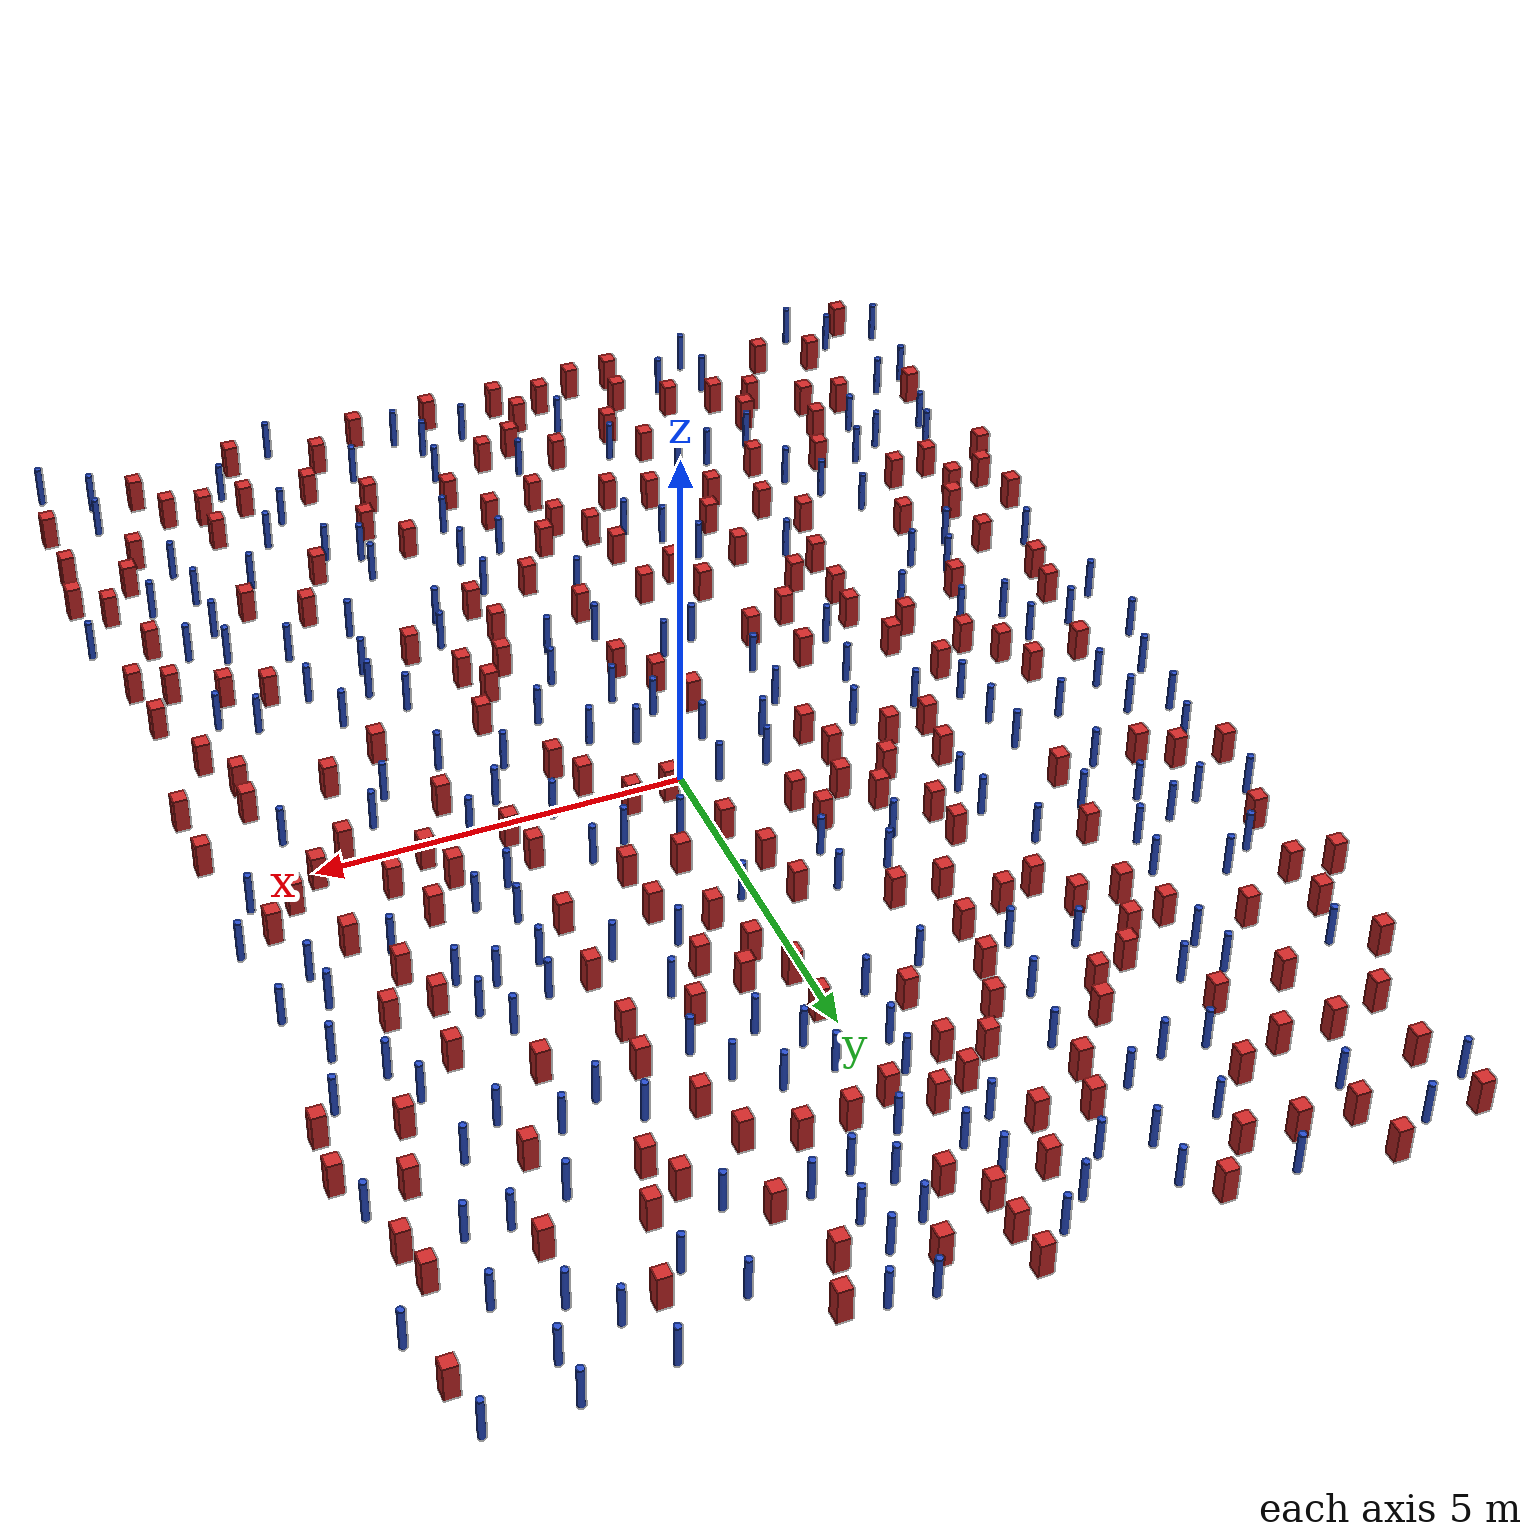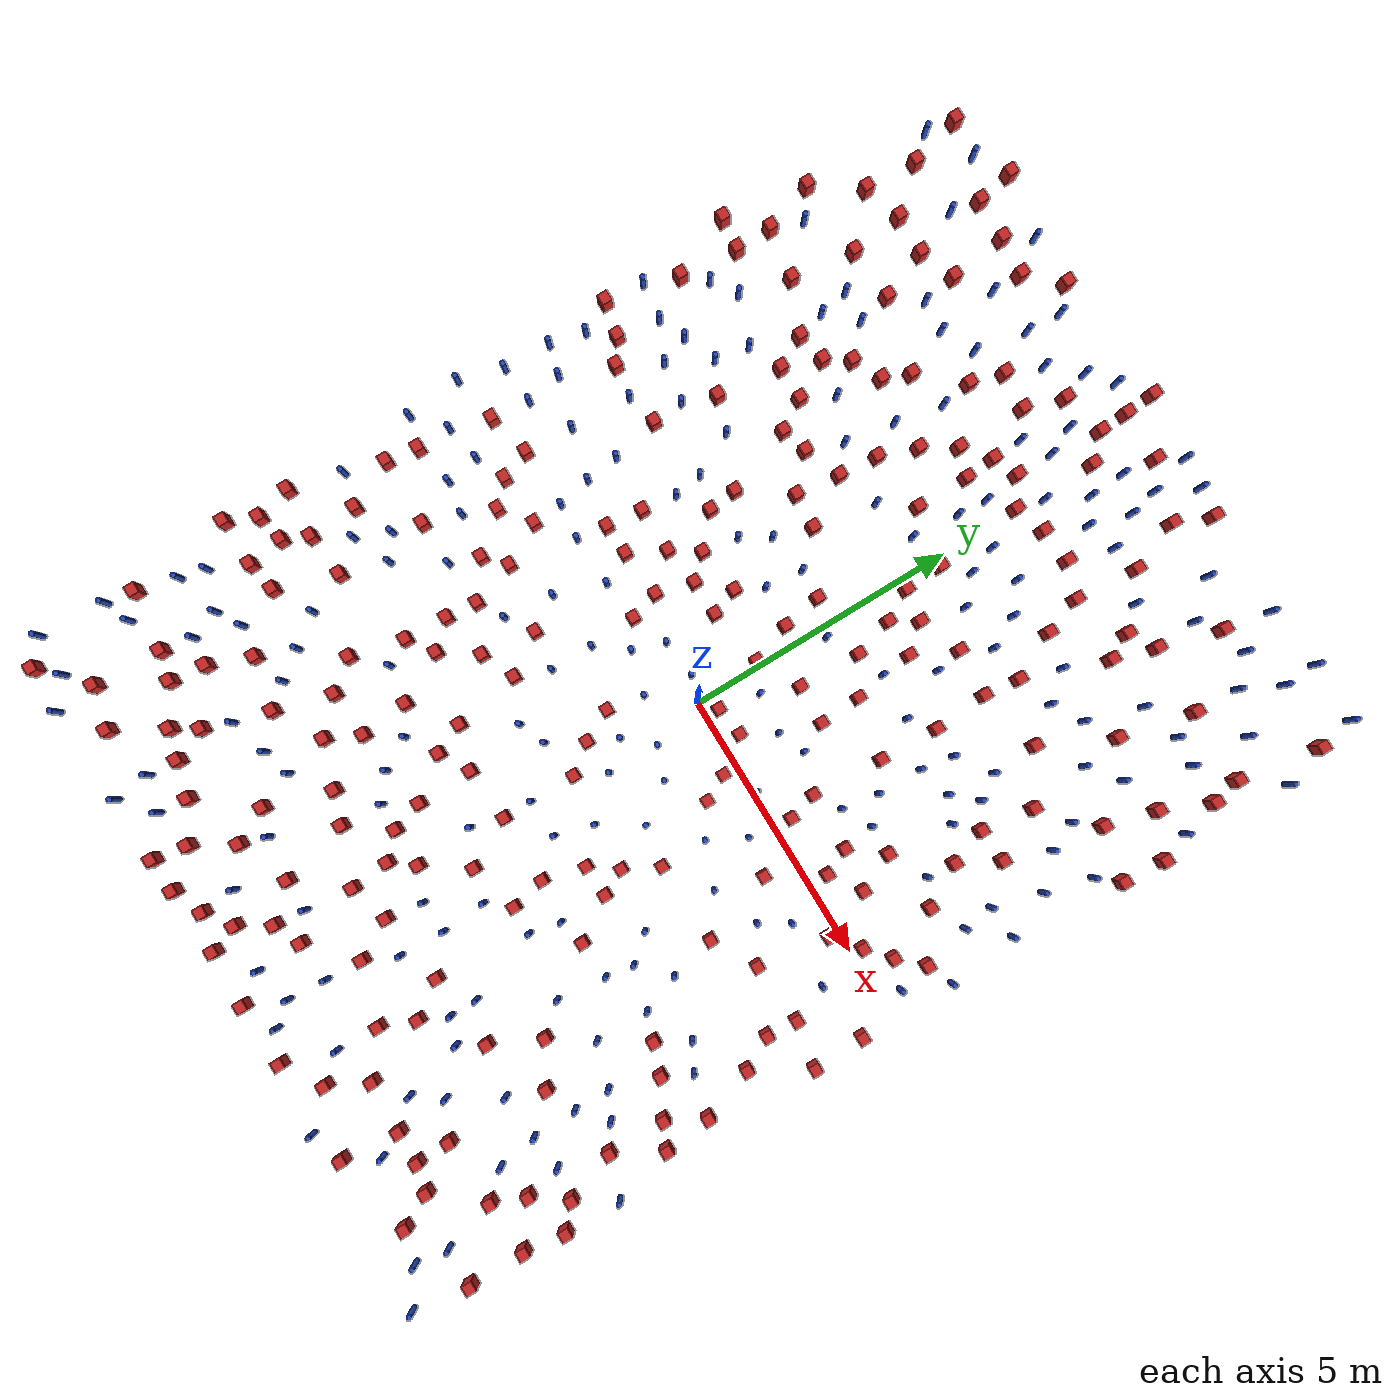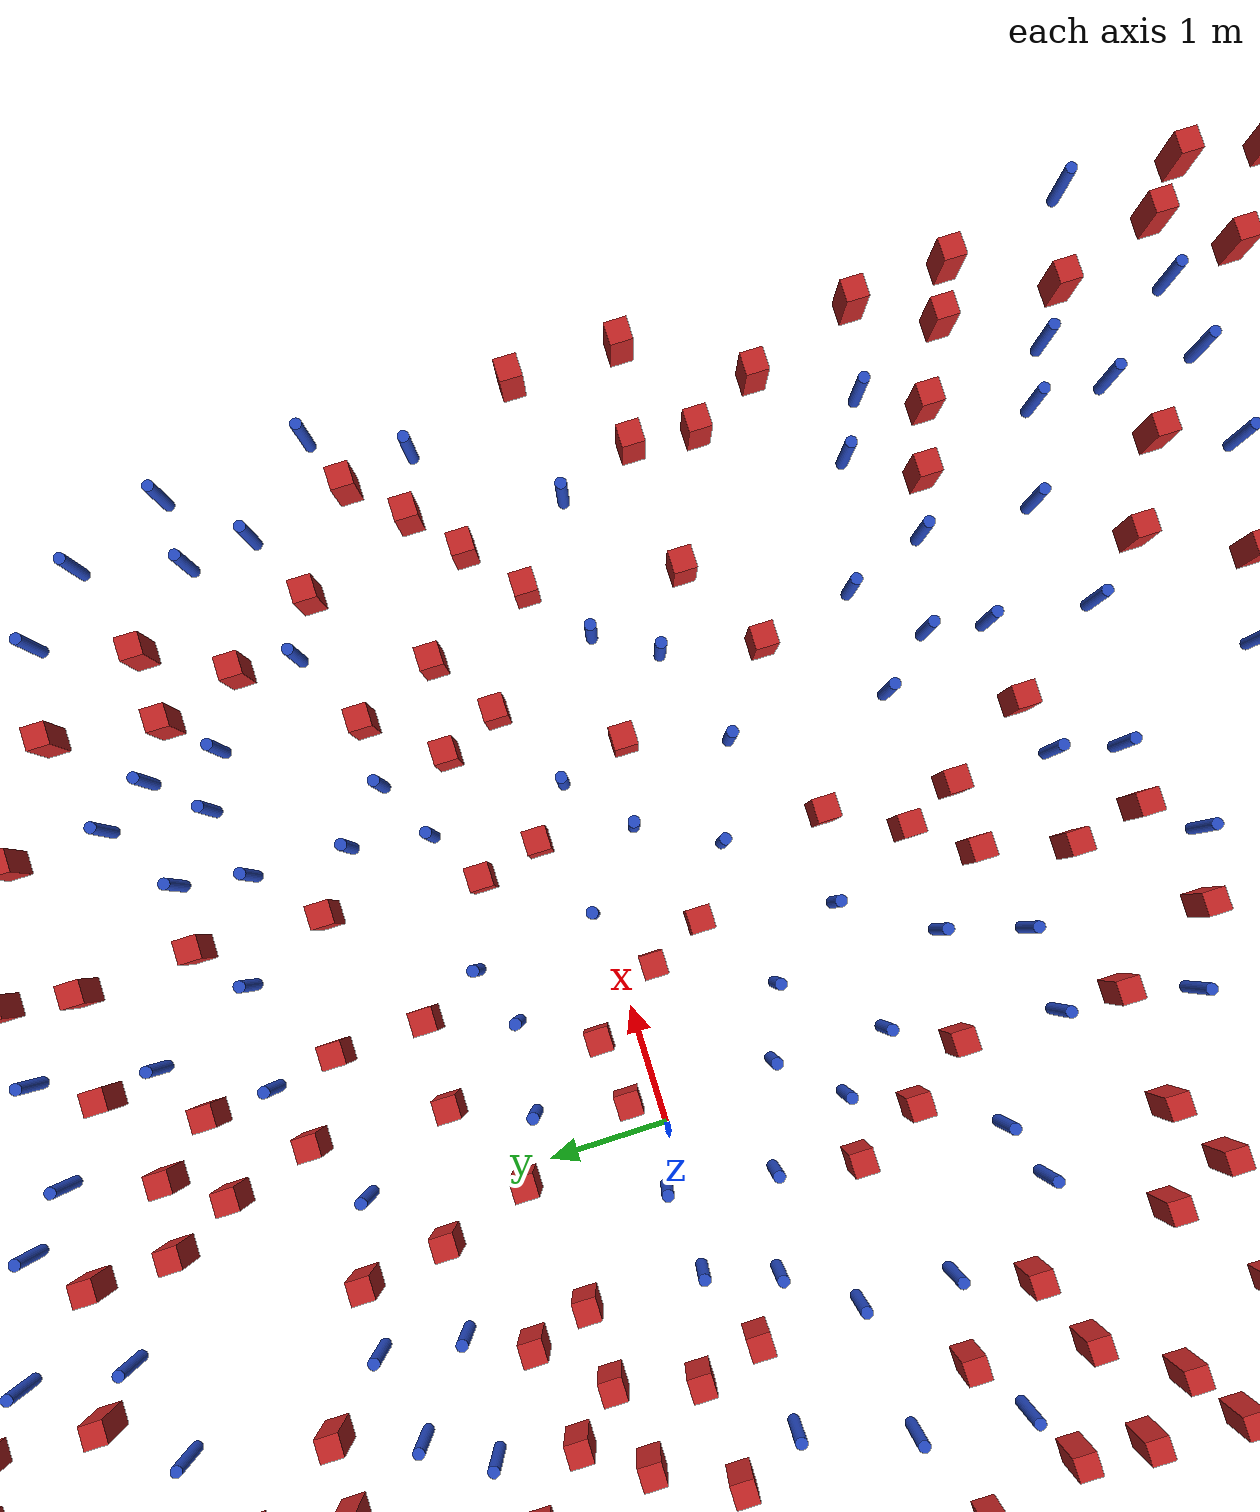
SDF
<sdf version="1.6">
  <model name="dense_52"><model name="square_post_obstacle0">
  <static>true</static>
  <pose frame="">-3.52017883421 -2.92411705398 8.22691968438e-08 7.2212513382e-06 -7.54495500217e-07 2.29674213826e-05</pose>
  <link name="link">
    <pose frame="">0 0 0.25 0 -0 0</pose>
    <inertial>
      <mass>100</mass>
      <inertia>
        <ixx>0.166667</ixx>
        <ixy>0</ixy>
        <ixz>0</ixz>
        <iyy>0.166667</iyy>
        <iyz>0</iyz>
        <izz>0.166667</izz>
      </inertia>
    </inertial>
    <collision name="collision">
      <geometry>
        <box>
          <size>.2 .2 .5</size>
        </box>
      </geometry>
      <max_contacts>10</max_contacts>
      <surface>
        <contact>
          <ode/>
        </contact>
        <bounce/>
        <friction>
          <torsional>
            <ode/>
          </torsional>
          <ode/>
        </friction>
      </surface>
    </collision>
    <visual name="visual">
      <geometry>
        <box>
          <size>.2 .2 .5</size>
        </box>
      </geometry>
      <material>
        <script>
          <name>Gazebo/Red</name>
          <uri>file://media/materials/scripts/gazebo.material</uri>
        </script>
      </material>
    </visual>
    <self_collide>0</self_collide>
    <kinematic>0</kinematic>
  </link>
</model>
<model name="square_post_obstacle1">
  <static>true</static>
  <pose frame="">4.98512163311 -8.85030999336 8.22691968438e-08 7.22125133819e-06 -7.54495500217e-07 2.29674213826e-05</pose>
  <link name="link">
    <pose frame="">0 0 0.25 0 -0 0</pose>
    <inertial>
      <mass>100</mass>
      <inertia>
        <ixx>0.166667</ixx>
        <ixy>0</ixy>
        <ixz>0</ixz>
        <iyy>0.166667</iyy>
        <iyz>0</iyz>
        <izz>0.166667</izz>
      </inertia>
    </inertial>
    <collision name="collision">
      <geometry>
        <box>
          <size>.2 .2 .5</size>
        </box>
      </geometry>
      <max_contacts>10</max_contacts>
      <surface>
        <contact>
          <ode/>
        </contact>
        <bounce/>
        <friction>
          <torsional>
            <ode/>
          </torsional>
          <ode/>
        </friction>
      </surface>
    </collision>
    <visual name="visual">
      <geometry>
        <box>
          <size>.2 .2 .5</size>
        </box>
      </geometry>
      <material>
        <script>
          <name>Gazebo/Red</name>
          <uri>file://media/materials/scripts/gazebo.material</uri>
        </script>
      </material>
    </visual>
    <self_collide>0</self_collide>
    <kinematic>0</kinematic>
  </link>
</model>
<model name="pole_obstacle0">
  <static>true</static>
  <pose frame="">-5.68199966664 -6.26441444535 2.88873142074e-08 -9.90536690842e-09 4.60219948965e-07 -1.20965994976e-07</pose>
  <link name="link">
  <pose frame="">0 0 0.3 0 -0 0</pose>
    <inertial>
      <mass>1</mass>
      <inertia>
        <ixx>0.145833</ixx>
        <ixy>0</ixy>
        <ixz>0</ixz>
        <iyy>0.145833</iyy>
        <iyz>0</iyz>
        <izz>0.125</izz>
      </inertia>
    </inertial>
    <collision name="collision">
      <geometry>
        <cylinder>
          <radius>0.05</radius>
          <length>.6</length>
        </cylinder>
      </geometry>
      <max_contacts>10</max_contacts>
      <surface>
        <contact>
          <ode/>
        </contact>
        <bounce/>
        <friction>
          <torsional>
            <ode/>
          </torsional>
          <ode/>
        </friction>
      </surface>
    </collision>
    <visual name="visual">
      <geometry>
        <cylinder>
          <radius>0.05</radius>
          <length>.6</length>
        </cylinder>
      </geometry>
      <material>
        <script>
          <name>Gazebo/Blue</name>
          <uri>file://media/materials/scripts/gazebo.material</uri>
        </script>
      </material>
    </visual>
    <self_collide>0</self_collide>
    <kinematic>0</kinematic>
  </link>
</model>
<model name="square_post_obstacle2">
  <static>true</static>
  <pose frame="">0.356496123219 -9.28904037353 8.22691968438e-08 7.2212513382e-06 -7.54495500217e-07 2.29674213826e-05</pose>
  <link name="link">
    <pose frame="">0 0 0.25 0 -0 0</pose>
    <inertial>
      <mass>100</mass>
      <inertia>
        <ixx>0.166667</ixx>
        <ixy>0</ixy>
        <ixz>0</ixz>
        <iyy>0.166667</iyy>
        <iyz>0</iyz>
        <izz>0.166667</izz>
      </inertia>
    </inertial>
    <collision name="collision">
      <geometry>
        <box>
          <size>.2 .2 .5</size>
        </box>
      </geometry>
      <max_contacts>10</max_contacts>
      <surface>
        <contact>
          <ode/>
        </contact>
        <bounce/>
        <friction>
          <torsional>
            <ode/>
          </torsional>
          <ode/>
        </friction>
      </surface>
    </collision>
    <visual name="visual">
      <geometry>
        <box>
          <size>.2 .2 .5</size>
        </box>
      </geometry>
      <material>
        <script>
          <name>Gazebo/Red</name>
          <uri>file://media/materials/scripts/gazebo.material</uri>
        </script>
      </material>
    </visual>
    <self_collide>0</self_collide>
    <kinematic>0</kinematic>
  </link>
</model>
<model name="pole_obstacle1">
  <static>true</static>
  <pose frame="">3.94145928123 3.25235252601 2.88873142074e-08 -9.90536690232e-09 4.6021994898e-07 -1.20965994968e-07</pose>
  <link name="link">
  <pose frame="">0 0 0.3 0 -0 0</pose>
    <inertial>
      <mass>1</mass>
      <inertia>
        <ixx>0.145833</ixx>
        <ixy>0</ixy>
        <ixz>0</ixz>
        <iyy>0.145833</iyy>
        <iyz>0</iyz>
        <izz>0.125</izz>
      </inertia>
    </inertial>
    <collision name="collision">
      <geometry>
        <cylinder>
          <radius>0.05</radius>
          <length>.6</length>
        </cylinder>
      </geometry>
      <max_contacts>10</max_contacts>
      <surface>
        <contact>
          <ode/>
        </contact>
        <bounce/>
        <friction>
          <torsional>
            <ode/>
          </torsional>
          <ode/>
        </friction>
      </surface>
    </collision>
    <visual name="visual">
      <geometry>
        <cylinder>
          <radius>0.05</radius>
          <length>.6</length>
        </cylinder>
      </geometry>
      <material>
        <script>
          <name>Gazebo/Blue</name>
          <uri>file://media/materials/scripts/gazebo.material</uri>
        </script>
      </material>
    </visual>
    <self_collide>0</self_collide>
    <kinematic>0</kinematic>
  </link>
</model>
<model name="square_post_obstacle3">
  <static>true</static>
  <pose frame="">-2.61809508313 -4.28710218862 8.22691968438e-08 7.2212513382e-06 -7.54495500217e-07 2.29674213826e-05</pose>
  <link name="link">
    <pose frame="">0 0 0.25 0 -0 0</pose>
    <inertial>
      <mass>100</mass>
      <inertia>
        <ixx>0.166667</ixx>
        <ixy>0</ixy>
        <ixz>0</ixz>
        <iyy>0.166667</iyy>
        <iyz>0</iyz>
        <izz>0.166667</izz>
      </inertia>
    </inertial>
    <collision name="collision">
      <geometry>
        <box>
          <size>.2 .2 .5</size>
        </box>
      </geometry>
      <max_contacts>10</max_contacts>
      <surface>
        <contact>
          <ode/>
        </contact>
        <bounce/>
        <friction>
          <torsional>
            <ode/>
          </torsional>
          <ode/>
        </friction>
      </surface>
    </collision>
    <visual name="visual">
      <geometry>
        <box>
          <size>.2 .2 .5</size>
        </box>
      </geometry>
      <material>
        <script>
          <name>Gazebo/Red</name>
          <uri>file://media/materials/scripts/gazebo.material</uri>
        </script>
      </material>
    </visual>
    <self_collide>0</self_collide>
    <kinematic>0</kinematic>
  </link>
</model>
<model name="pole_obstacle2">
  <static>true</static>
  <pose frame="">-4.29656376117 0.3883590733 2.88873142074e-08 -9.90536689981e-09 4.60219948986e-07 -1.20965994962e-07</pose>
  <link name="link">
  <pose frame="">0 0 0.3 0 -0 0</pose>
    <inertial>
      <mass>1</mass>
      <inertia>
        <ixx>0.145833</ixx>
        <ixy>0</ixy>
        <ixz>0</ixz>
        <iyy>0.145833</iyy>
        <iyz>0</iyz>
        <izz>0.125</izz>
      </inertia>
    </inertial>
    <collision name="collision">
      <geometry>
        <cylinder>
          <radius>0.05</radius>
          <length>.6</length>
        </cylinder>
      </geometry>
      <max_contacts>10</max_contacts>
      <surface>
        <contact>
          <ode/>
        </contact>
        <bounce/>
        <friction>
          <torsional>
            <ode/>
          </torsional>
          <ode/>
        </friction>
      </surface>
    </collision>
    <visual name="visual">
      <geometry>
        <cylinder>
          <radius>0.05</radius>
          <length>.6</length>
        </cylinder>
      </geometry>
      <material>
        <script>
          <name>Gazebo/Blue</name>
          <uri>file://media/materials/scripts/gazebo.material</uri>
        </script>
      </material>
    </visual>
    <self_collide>0</self_collide>
    <kinematic>0</kinematic>
  </link>
</model>
<model name="pole_obstacle3">
  <static>true</static>
  <pose frame="">-5.23848355303 -5.99416377618 2.88873142074e-08 -9.90536690842e-09 4.60219948965e-07 -1.20965994976e-07</pose>
  <link name="link">
  <pose frame="">0 0 0.3 0 -0 0</pose>
    <inertial>
      <mass>1</mass>
      <inertia>
        <ixx>0.145833</ixx>
        <ixy>0</ixy>
        <ixz>0</ixz>
        <iyy>0.145833</iyy>
        <iyz>0</iyz>
        <izz>0.125</izz>
      </inertia>
    </inertial>
    <collision name="collision">
      <geometry>
        <cylinder>
          <radius>0.05</radius>
          <length>.6</length>
        </cylinder>
      </geometry>
      <max_contacts>10</max_contacts>
      <surface>
        <contact>
          <ode/>
        </contact>
        <bounce/>
        <friction>
          <torsional>
            <ode/>
          </torsional>
          <ode/>
        </friction>
      </surface>
    </collision>
    <visual name="visual">
      <geometry>
        <cylinder>
          <radius>0.05</radius>
          <length>.6</length>
        </cylinder>
      </geometry>
      <material>
        <script>
          <name>Gazebo/Blue</name>
          <uri>file://media/materials/scripts/gazebo.material</uri>
        </script>
      </material>
    </visual>
    <self_collide>0</self_collide>
    <kinematic>0</kinematic>
  </link>
</model>
<model name="square_post_obstacle4">
  <static>true</static>
  <pose frame="">3.07197832872 -6.08663907217 8.22691968438e-08 7.2212513382e-06 -7.54495500217e-07 2.29674213826e-05</pose>
  <link name="link">
    <pose frame="">0 0 0.25 0 -0 0</pose>
    <inertial>
      <mass>100</mass>
      <inertia>
        <ixx>0.166667</ixx>
        <ixy>0</ixy>
        <ixz>0</ixz>
        <iyy>0.166667</iyy>
        <iyz>0</iyz>
        <izz>0.166667</izz>
      </inertia>
    </inertial>
    <collision name="collision">
      <geometry>
        <box>
          <size>.2 .2 .5</size>
        </box>
      </geometry>
      <max_contacts>10</max_contacts>
      <surface>
        <contact>
          <ode/>
        </contact>
        <bounce/>
        <friction>
          <torsional>
            <ode/>
          </torsional>
          <ode/>
        </friction>
      </surface>
    </collision>
    <visual name="visual">
      <geometry>
        <box>
          <size>.2 .2 .5</size>
        </box>
      </geometry>
      <material>
        <script>
          <name>Gazebo/Red</name>
          <uri>file://media/materials/scripts/gazebo.material</uri>
        </script>
      </material>
    </visual>
    <self_collide>0</self_collide>
    <kinematic>0</kinematic>
  </link>
</model>
<model name="square_post_obstacle5">
  <static>true</static>
  <pose frame="">5.47471650672 -1.39341901515 8.22691968438e-08 7.2212513382e-06 -7.54495500217e-07 2.29674213826e-05</pose>
  <link name="link">
    <pose frame="">0 0 0.25 0 -0 0</pose>
    <inertial>
      <mass>100</mass>
      <inertia>
        <ixx>0.166667</ixx>
        <ixy>0</ixy>
        <ixz>0</ixz>
        <iyy>0.166667</iyy>
        <iyz>0</iyz>
        <izz>0.166667</izz>
      </inertia>
    </inertial>
    <collision name="collision">
      <geometry>
        <box>
          <size>.2 .2 .5</size>
        </box>
      </geometry>
      <max_contacts>10</max_contacts>
      <surface>
        <contact>
          <ode/>
        </contact>
        <bounce/>
        <friction>
          <torsional>
            <ode/>
          </torsional>
          <ode/>
        </friction>
      </surface>
    </collision>
    <visual name="visual">
      <geometry>
        <box>
          <size>.2 .2 .5</size>
        </box>
      </geometry>
      <material>
        <script>
          <name>Gazebo/Red</name>
          <uri>file://media/materials/scripts/gazebo.material</uri>
        </script>
      </material>
    </visual>
    <self_collide>0</self_collide>
    <kinematic>0</kinematic>
  </link>
</model>
<model name="square_post_obstacle6">
  <static>true</static>
  <pose frame="">-6.45934820761 -9.41857495055 8.22691968438e-08 7.22125133819e-06 -7.54495500217e-07 2.29674213826e-05</pose>
  <link name="link">
    <pose frame="">0 0 0.25 0 -0 0</pose>
    <inertial>
      <mass>100</mass>
      <inertia>
        <ixx>0.166667</ixx>
        <ixy>0</ixy>
        <ixz>0</ixz>
        <iyy>0.166667</iyy>
        <iyz>0</iyz>
        <izz>0.166667</izz>
      </inertia>
    </inertial>
    <collision name="collision">
      <geometry>
        <box>
          <size>.2 .2 .5</size>
        </box>
      </geometry>
      <max_contacts>10</max_contacts>
      <surface>
        <contact>
          <ode/>
        </contact>
        <bounce/>
        <friction>
          <torsional>
            <ode/>
          </torsional>
          <ode/>
        </friction>
      </surface>
    </collision>
    <visual name="visual">
      <geometry>
        <box>
          <size>.2 .2 .5</size>
        </box>
      </geometry>
      <material>
        <script>
          <name>Gazebo/Red</name>
          <uri>file://media/materials/scripts/gazebo.material</uri>
        </script>
      </material>
    </visual>
    <self_collide>0</self_collide>
    <kinematic>0</kinematic>
  </link>
</model>
<model name="pole_obstacle4">
  <static>true</static>
  <pose frame="">6.25062392108 5.93523951194 2.88873142074e-08 -9.90536690842e-09 4.60219948965e-07 -1.20965994976e-07</pose>
  <link name="link">
  <pose frame="">0 0 0.3 0 -0 0</pose>
    <inertial>
      <mass>1</mass>
      <inertia>
        <ixx>0.145833</ixx>
        <ixy>0</ixy>
        <ixz>0</ixz>
        <iyy>0.145833</iyy>
        <iyz>0</iyz>
        <izz>0.125</izz>
      </inertia>
    </inertial>
    <collision name="collision">
      <geometry>
        <cylinder>
          <radius>0.05</radius>
          <length>.6</length>
        </cylinder>
      </geometry>
      <max_contacts>10</max_contacts>
      <surface>
        <contact>
          <ode/>
        </contact>
        <bounce/>
        <friction>
          <torsional>
            <ode/>
          </torsional>
          <ode/>
        </friction>
      </surface>
    </collision>
    <visual name="visual">
      <geometry>
        <cylinder>
          <radius>0.05</radius>
          <length>.6</length>
        </cylinder>
      </geometry>
      <material>
        <script>
          <name>Gazebo/Blue</name>
          <uri>file://media/materials/scripts/gazebo.material</uri>
        </script>
      </material>
    </visual>
    <self_collide>0</self_collide>
    <kinematic>0</kinematic>
  </link>
</model>
<model name="pole_obstacle5">
  <static>true</static>
  <pose frame="">1.15568861815 0.909828647617 2.88873142074e-08 -9.90536689692e-09 4.60219948993e-07 -1.20965994958e-07</pose>
  <link name="link">
  <pose frame="">0 0 0.3 0 -0 0</pose>
    <inertial>
      <mass>1</mass>
      <inertia>
        <ixx>0.145833</ixx>
        <ixy>0</ixy>
        <ixz>0</ixz>
        <iyy>0.145833</iyy>
        <iyz>0</iyz>
        <izz>0.125</izz>
      </inertia>
    </inertial>
    <collision name="collision">
      <geometry>
        <cylinder>
          <radius>0.05</radius>
          <length>.6</length>
        </cylinder>
      </geometry>
      <max_contacts>10</max_contacts>
      <surface>
        <contact>
          <ode/>
        </contact>
        <bounce/>
        <friction>
          <torsional>
            <ode/>
          </torsional>
          <ode/>
        </friction>
      </surface>
    </collision>
    <visual name="visual">
      <geometry>
        <cylinder>
          <radius>0.05</radius>
          <length>.6</length>
        </cylinder>
      </geometry>
      <material>
        <script>
          <name>Gazebo/Blue</name>
          <uri>file://media/materials/scripts/gazebo.material</uri>
        </script>
      </material>
    </visual>
    <self_collide>0</self_collide>
    <kinematic>0</kinematic>
  </link>
</model>
<model name="square_post_obstacle7">
  <static>true</static>
  <pose frame="">5.44254563058 0.562767419311 8.22691968438e-08 7.2212513382e-06 -7.54495500217e-07 2.29674213826e-05</pose>
  <link name="link">
    <pose frame="">0 0 0.25 0 -0 0</pose>
    <inertial>
      <mass>100</mass>
      <inertia>
        <ixx>0.166667</ixx>
        <ixy>0</ixy>
        <ixz>0</ixz>
        <iyy>0.166667</iyy>
        <iyz>0</iyz>
        <izz>0.166667</izz>
      </inertia>
    </inertial>
    <collision name="collision">
      <geometry>
        <box>
          <size>.2 .2 .5</size>
        </box>
      </geometry>
      <max_contacts>10</max_contacts>
      <surface>
        <contact>
          <ode/>
        </contact>
        <bounce/>
        <friction>
          <torsional>
            <ode/>
          </torsional>
          <ode/>
        </friction>
      </surface>
    </collision>
    <visual name="visual">
      <geometry>
        <box>
          <size>.2 .2 .5</size>
        </box>
      </geometry>
      <material>
        <script>
          <name>Gazebo/Red</name>
          <uri>file://media/materials/scripts/gazebo.material</uri>
        </script>
      </material>
    </visual>
    <self_collide>0</self_collide>
    <kinematic>0</kinematic>
  </link>
</model>
<model name="square_post_obstacle8">
  <static>true</static>
  <pose frame="">1.67702876717 -6.24048371614 8.22691968438e-08 7.2212513382e-06 -7.54495500217e-07 2.29674213826e-05</pose>
  <link name="link">
    <pose frame="">0 0 0.25 0 -0 0</pose>
    <inertial>
      <mass>100</mass>
      <inertia>
        <ixx>0.166667</ixx>
        <ixy>0</ixy>
        <ixz>0</ixz>
        <iyy>0.166667</iyy>
        <iyz>0</iyz>
        <izz>0.166667</izz>
      </inertia>
    </inertial>
    <collision name="collision">
      <geometry>
        <box>
          <size>.2 .2 .5</size>
        </box>
      </geometry>
      <max_contacts>10</max_contacts>
      <surface>
        <contact>
          <ode/>
        </contact>
        <bounce/>
        <friction>
          <torsional>
            <ode/>
          </torsional>
          <ode/>
        </friction>
      </surface>
    </collision>
    <visual name="visual">
      <geometry>
        <box>
          <size>.2 .2 .5</size>
        </box>
      </geometry>
      <material>
        <script>
          <name>Gazebo/Red</name>
          <uri>file://media/materials/scripts/gazebo.material</uri>
        </script>
      </material>
    </visual>
    <self_collide>0</self_collide>
    <kinematic>0</kinematic>
  </link>
</model>
<model name="pole_obstacle6">
  <static>true</static>
  <pose frame="">3.05227530506 3.25262592409 2.88873142074e-08 -9.90536690232e-09 4.6021994898e-07 -1.20965994968e-07</pose>
  <link name="link">
  <pose frame="">0 0 0.3 0 -0 0</pose>
    <inertial>
      <mass>1</mass>
      <inertia>
        <ixx>0.145833</ixx>
        <ixy>0</ixy>
        <ixz>0</ixz>
        <iyy>0.145833</iyy>
        <iyz>0</iyz>
        <izz>0.125</izz>
      </inertia>
    </inertial>
    <collision name="collision">
      <geometry>
        <cylinder>
          <radius>0.05</radius>
          <length>.6</length>
        </cylinder>
      </geometry>
      <max_contacts>10</max_contacts>
      <surface>
        <contact>
          <ode/>
        </contact>
        <bounce/>
        <friction>
          <torsional>
            <ode/>
          </torsional>
          <ode/>
        </friction>
      </surface>
    </collision>
    <visual name="visual">
      <geometry>
        <cylinder>
          <radius>0.05</radius>
          <length>.6</length>
        </cylinder>
      </geometry>
      <material>
        <script>
          <name>Gazebo/Blue</name>
          <uri>file://media/materials/scripts/gazebo.material</uri>
        </script>
      </material>
    </visual>
    <self_collide>0</self_collide>
    <kinematic>0</kinematic>
  </link>
</model>
<model name="pole_obstacle7">
  <static>true</static>
  <pose frame="">-5.55489222727 3.11626111956 2.88873142074e-08 -9.90536690245e-09 4.6021994898e-07 -1.20965994966e-07</pose>
  <link name="link">
  <pose frame="">0 0 0.3 0 -0 0</pose>
    <inertial>
      <mass>1</mass>
      <inertia>
        <ixx>0.145833</ixx>
        <ixy>0</ixy>
        <ixz>0</ixz>
        <iyy>0.145833</iyy>
        <iyz>0</iyz>
        <izz>0.125</izz>
      </inertia>
    </inertial>
    <collision name="collision">
      <geometry>
        <cylinder>
          <radius>0.05</radius>
          <length>.6</length>
        </cylinder>
      </geometry>
      <max_contacts>10</max_contacts>
      <surface>
        <contact>
          <ode/>
        </contact>
        <bounce/>
        <friction>
          <torsional>
            <ode/>
          </torsional>
          <ode/>
        </friction>
      </surface>
    </collision>
    <visual name="visual">
      <geometry>
        <cylinder>
          <radius>0.05</radius>
          <length>.6</length>
        </cylinder>
      </geometry>
      <material>
        <script>
          <name>Gazebo/Blue</name>
          <uri>file://media/materials/scripts/gazebo.material</uri>
        </script>
      </material>
    </visual>
    <self_collide>0</self_collide>
    <kinematic>0</kinematic>
  </link>
</model>
<model name="square_post_obstacle9">
  <static>true</static>
  <pose frame="">-4.65726586537 -6.07960110968 8.22691968438e-08 7.2212513382e-06 -7.54495500217e-07 2.29674213826e-05</pose>
  <link name="link">
    <pose frame="">0 0 0.25 0 -0 0</pose>
    <inertial>
      <mass>100</mass>
      <inertia>
        <ixx>0.166667</ixx>
        <ixy>0</ixy>
        <ixz>0</ixz>
        <iyy>0.166667</iyy>
        <iyz>0</iyz>
        <izz>0.166667</izz>
      </inertia>
    </inertial>
    <collision name="collision">
      <geometry>
        <box>
          <size>.2 .2 .5</size>
        </box>
      </geometry>
      <max_contacts>10</max_contacts>
      <surface>
        <contact>
          <ode/>
        </contact>
        <bounce/>
        <friction>
          <torsional>
            <ode/>
          </torsional>
          <ode/>
        </friction>
      </surface>
    </collision>
    <visual name="visual">
      <geometry>
        <box>
          <size>.2 .2 .5</size>
        </box>
      </geometry>
      <material>
        <script>
          <name>Gazebo/Red</name>
          <uri>file://media/materials/scripts/gazebo.material</uri>
        </script>
      </material>
    </visual>
    <self_collide>0</self_collide>
    <kinematic>0</kinematic>
  </link>
</model>
<model name="square_post_obstacle10">
  <static>true</static>
  <pose frame="">-4.55760182171 1.88871491998 8.22691968438e-08 7.2212513382e-06 -7.54495500217e-07 2.29674213826e-05</pose>
  <link name="link">
    <pose frame="">0 0 0.25 0 -0 0</pose>
    <inertial>
      <mass>100</mass>
      <inertia>
        <ixx>0.166667</ixx>
        <ixy>0</ixy>
        <ixz>0</ixz>
        <iyy>0.166667</iyy>
        <iyz>0</iyz>
        <izz>0.166667</izz>
      </inertia>
    </inertial>
    <collision name="collision">
      <geometry>
        <box>
          <size>.2 .2 .5</size>
        </box>
      </geometry>
      <max_contacts>10</max_contacts>
      <surface>
        <contact>
          <ode/>
        </contact>
        <bounce/>
        <friction>
          <torsional>
            <ode/>
          </torsional>
          <ode/>
        </friction>
      </surface>
    </collision>
    <visual name="visual">
      <geometry>
        <box>
          <size>.2 .2 .5</size>
        </box>
      </geometry>
      <material>
        <script>
          <name>Gazebo/Red</name>
          <uri>file://media/materials/scripts/gazebo.material</uri>
        </script>
      </material>
    </visual>
    <self_collide>0</self_collide>
    <kinematic>0</kinematic>
  </link>
</model>
<model name="square_post_obstacle11">
  <static>true</static>
  <pose frame="">-1.1652866961 1.04216273189 8.22691968438e-08 7.2212513382e-06 -7.54495500217e-07 2.29674213826e-05</pose>
  <link name="link">
    <pose frame="">0 0 0.25 0 -0 0</pose>
    <inertial>
      <mass>100</mass>
      <inertia>
        <ixx>0.166667</ixx>
        <ixy>0</ixy>
        <ixz>0</ixz>
        <iyy>0.166667</iyy>
        <iyz>0</iyz>
        <izz>0.166667</izz>
      </inertia>
    </inertial>
    <collision name="collision">
      <geometry>
        <box>
          <size>.2 .2 .5</size>
        </box>
      </geometry>
      <max_contacts>10</max_contacts>
      <surface>
        <contact>
          <ode/>
        </contact>
        <bounce/>
        <friction>
          <torsional>
            <ode/>
          </torsional>
          <ode/>
        </friction>
      </surface>
    </collision>
    <visual name="visual">
      <geometry>
        <box>
          <size>.2 .2 .5</size>
        </box>
      </geometry>
      <material>
        <script>
          <name>Gazebo/Red</name>
          <uri>file://media/materials/scripts/gazebo.material</uri>
        </script>
      </material>
    </visual>
    <self_collide>0</self_collide>
    <kinematic>0</kinematic>
  </link>
</model>
<model name="square_post_obstacle12">
  <static>true</static>
  <pose frame="">-4.15529586419 8.73507589895 8.22691968438e-08 7.22125133819e-06 -7.54495500217e-07 2.29674213826e-05</pose>
  <link name="link">
    <pose frame="">0 0 0.25 0 -0 0</pose>
    <inertial>
      <mass>100</mass>
      <inertia>
        <ixx>0.166667</ixx>
        <ixy>0</ixy>
        <ixz>0</ixz>
        <iyy>0.166667</iyy>
        <iyz>0</iyz>
        <izz>0.166667</izz>
      </inertia>
    </inertial>
    <collision name="collision">
      <geometry>
        <box>
          <size>.2 .2 .5</size>
        </box>
      </geometry>
      <max_contacts>10</max_contacts>
      <surface>
        <contact>
          <ode/>
        </contact>
        <bounce/>
        <friction>
          <torsional>
            <ode/>
          </torsional>
          <ode/>
        </friction>
      </surface>
    </collision>
    <visual name="visual">
      <geometry>
        <box>
          <size>.2 .2 .5</size>
        </box>
      </geometry>
      <material>
        <script>
          <name>Gazebo/Red</name>
          <uri>file://media/materials/scripts/gazebo.material</uri>
        </script>
      </material>
    </visual>
    <self_collide>0</self_collide>
    <kinematic>0</kinematic>
  </link>
</model>
<model name="square_post_obstacle13">
  <static>true</static>
  <pose frame="">1.60740175641 8.58705689888 8.22691968438e-08 7.22125133819e-06 -7.54495500217e-07 2.29674213826e-05</pose>
  <link name="link">
    <pose frame="">0 0 0.25 0 -0 0</pose>
    <inertial>
      <mass>100</mass>
      <inertia>
        <ixx>0.166667</ixx>
        <ixy>0</ixy>
        <ixz>0</ixz>
        <iyy>0.166667</iyy>
        <iyz>0</iyz>
        <izz>0.166667</izz>
      </inertia>
    </inertial>
    <collision name="collision">
      <geometry>
        <box>
          <size>.2 .2 .5</size>
        </box>
      </geometry>
      <max_contacts>10</max_contacts>
      <surface>
        <contact>
          <ode/>
        </contact>
        <bounce/>
        <friction>
          <torsional>
            <ode/>
          </torsional>
          <ode/>
        </friction>
      </surface>
    </collision>
    <visual name="visual">
      <geometry>
        <box>
          <size>.2 .2 .5</size>
        </box>
      </geometry>
      <material>
        <script>
          <name>Gazebo/Red</name>
          <uri>file://media/materials/scripts/gazebo.material</uri>
        </script>
      </material>
    </visual>
    <self_collide>0</self_collide>
    <kinematic>0</kinematic>
  </link>
</model>
<model name="pole_obstacle8">
  <static>true</static>
  <pose frame="">2.81739710096 -6.5374119747 2.88873142074e-08 -9.90536689859e-09 4.60219948989e-07 -1.20965994961e-07</pose>
  <link name="link">
  <pose frame="">0 0 0.3 0 -0 0</pose>
    <inertial>
      <mass>1</mass>
      <inertia>
        <ixx>0.145833</ixx>
        <ixy>0</ixy>
        <ixz>0</ixz>
        <iyy>0.145833</iyy>
        <iyz>0</iyz>
        <izz>0.125</izz>
      </inertia>
    </inertial>
    <collision name="collision">
      <geometry>
        <cylinder>
          <radius>0.05</radius>
          <length>.6</length>
        </cylinder>
      </geometry>
      <max_contacts>10</max_contacts>
      <surface>
        <contact>
          <ode/>
        </contact>
        <bounce/>
        <friction>
          <torsional>
            <ode/>
          </torsional>
          <ode/>
        </friction>
      </surface>
    </collision>
    <visual name="visual">
      <geometry>
        <cylinder>
          <radius>0.05</radius>
          <length>.6</length>
        </cylinder>
      </geometry>
      <material>
        <script>
          <name>Gazebo/Blue</name>
          <uri>file://media/materials/scripts/gazebo.material</uri>
        </script>
      </material>
    </visual>
    <self_collide>0</self_collide>
    <kinematic>0</kinematic>
  </link>
</model>
<model name="square_post_obstacle14">
  <static>true</static>
  <pose frame="">6.05142016758 6.63428384098 8.22691968438e-08 7.2212513382e-06 -7.54495500217e-07 2.29674213826e-05</pose>
  <link name="link">
    <pose frame="">0 0 0.25 0 -0 0</pose>
    <inertial>
      <mass>100</mass>
      <inertia>
        <ixx>0.166667</ixx>
        <ixy>0</ixy>
        <ixz>0</ixz>
        <iyy>0.166667</iyy>
        <iyz>0</iyz>
        <izz>0.166667</izz>
      </inertia>
    </inertial>
    <collision name="collision">
      <geometry>
        <box>
          <size>.2 .2 .5</size>
        </box>
      </geometry>
      <max_contacts>10</max_contacts>
      <surface>
        <contact>
          <ode/>
        </contact>
        <bounce/>
        <friction>
          <torsional>
            <ode/>
          </torsional>
          <ode/>
        </friction>
      </surface>
    </collision>
    <visual name="visual">
      <geometry>
        <box>
          <size>.2 .2 .5</size>
        </box>
      </geometry>
      <material>
        <script>
          <name>Gazebo/Red</name>
          <uri>file://media/materials/scripts/gazebo.material</uri>
        </script>
      </material>
    </visual>
    <self_collide>0</self_collide>
    <kinematic>0</kinematic>
  </link>
</model>
<model name="square_post_obstacle15">
  <static>true</static>
  <pose frame="">-4.22114828094 4.25865756777 8.22691968438e-08 7.2212513382e-06 -7.54495500217e-07 2.29674213826e-05</pose>
  <link name="link">
    <pose frame="">0 0 0.25 0 -0 0</pose>
    <inertial>
      <mass>100</mass>
      <inertia>
        <ixx>0.166667</ixx>
        <ixy>0</ixy>
        <ixz>0</ixz>
        <iyy>0.166667</iyy>
        <iyz>0</iyz>
        <izz>0.166667</izz>
      </inertia>
    </inertial>
    <collision name="collision">
      <geometry>
        <box>
          <size>.2 .2 .5</size>
        </box>
      </geometry>
      <max_contacts>10</max_contacts>
      <surface>
        <contact>
          <ode/>
        </contact>
        <bounce/>
        <friction>
          <torsional>
            <ode/>
          </torsional>
          <ode/>
        </friction>
      </surface>
    </collision>
    <visual name="visual">
      <geometry>
        <box>
          <size>.2 .2 .5</size>
        </box>
      </geometry>
      <material>
        <script>
          <name>Gazebo/Red</name>
          <uri>file://media/materials/scripts/gazebo.material</uri>
        </script>
      </material>
    </visual>
    <self_collide>0</self_collide>
    <kinematic>0</kinematic>
  </link>
</model>
<model name="square_post_obstacle16">
  <static>true</static>
  <pose frame="">-5.66816697203 -8.67683960717 8.22691968438e-08 7.22125133819e-06 -7.54495500217e-07 2.29674213826e-05</pose>
  <link name="link">
    <pose frame="">0 0 0.25 0 -0 0</pose>
    <inertial>
      <mass>100</mass>
      <inertia>
        <ixx>0.166667</ixx>
        <ixy>0</ixy>
        <ixz>0</ixz>
        <iyy>0.166667</iyy>
        <iyz>0</iyz>
        <izz>0.166667</izz>
      </inertia>
    </inertial>
    <collision name="collision">
      <geometry>
        <box>
          <size>.2 .2 .5</size>
        </box>
      </geometry>
      <max_contacts>10</max_contacts>
      <surface>
        <contact>
          <ode/>
        </contact>
        <bounce/>
        <friction>
          <torsional>
            <ode/>
          </torsional>
          <ode/>
        </friction>
      </surface>
    </collision>
    <visual name="visual">
      <geometry>
        <box>
          <size>.2 .2 .5</size>
        </box>
      </geometry>
      <material>
        <script>
          <name>Gazebo/Red</name>
          <uri>file://media/materials/scripts/gazebo.material</uri>
        </script>
      </material>
    </visual>
    <self_collide>0</self_collide>
    <kinematic>0</kinematic>
  </link>
</model>
<model name="pole_obstacle9">
  <static>true</static>
  <pose frame="">-6.12231987147 0.901458141551 2.88873142074e-08 -9.90536689837e-09 4.60219948989e-07 -1.2096599496e-07</pose>
  <link name="link">
  <pose frame="">0 0 0.3 0 -0 0</pose>
    <inertial>
      <mass>1</mass>
      <inertia>
        <ixx>0.145833</ixx>
        <ixy>0</ixy>
        <ixz>0</ixz>
        <iyy>0.145833</iyy>
        <iyz>0</iyz>
        <izz>0.125</izz>
      </inertia>
    </inertial>
    <collision name="collision">
      <geometry>
        <cylinder>
          <radius>0.05</radius>
          <length>.6</length>
        </cylinder>
      </geometry>
      <max_contacts>10</max_contacts>
      <surface>
        <contact>
          <ode/>
        </contact>
        <bounce/>
        <friction>
          <torsional>
            <ode/>
          </torsional>
          <ode/>
        </friction>
      </surface>
    </collision>
    <visual name="visual">
      <geometry>
        <cylinder>
          <radius>0.05</radius>
          <length>.6</length>
        </cylinder>
      </geometry>
      <material>
        <script>
          <name>Gazebo/Blue</name>
          <uri>file://media/materials/scripts/gazebo.material</uri>
        </script>
      </material>
    </visual>
    <self_collide>0</self_collide>
    <kinematic>0</kinematic>
  </link>
</model>
<model name="square_post_obstacle17">
  <static>true</static>
  <pose frame="">2.50358971569 3.25167115299 8.22691968438e-08 7.2212513382e-06 -7.54495500217e-07 2.29674213826e-05</pose>
  <link name="link">
    <pose frame="">0 0 0.25 0 -0 0</pose>
    <inertial>
      <mass>100</mass>
      <inertia>
        <ixx>0.166667</ixx>
        <ixy>0</ixy>
        <ixz>0</ixz>
        <iyy>0.166667</iyy>
        <iyz>0</iyz>
        <izz>0.166667</izz>
      </inertia>
    </inertial>
    <collision name="collision">
      <geometry>
        <box>
          <size>.2 .2 .5</size>
        </box>
      </geometry>
      <max_contacts>10</max_contacts>
      <surface>
        <contact>
          <ode/>
        </contact>
        <bounce/>
        <friction>
          <torsional>
            <ode/>
          </torsional>
          <ode/>
        </friction>
      </surface>
    </collision>
    <visual name="visual">
      <geometry>
        <box>
          <size>.2 .2 .5</size>
        </box>
      </geometry>
      <material>
        <script>
          <name>Gazebo/Red</name>
          <uri>file://media/materials/scripts/gazebo.material</uri>
        </script>
      </material>
    </visual>
    <self_collide>0</self_collide>
    <kinematic>0</kinematic>
  </link>
</model>
<model name="square_post_obstacle18">
  <static>true</static>
  <pose frame="">-4.13438676228 -0.792070955111 8.22691968438e-08 7.2212513382e-06 -7.54495500217e-07 2.29674213826e-05</pose>
  <link name="link">
    <pose frame="">0 0 0.25 0 -0 0</pose>
    <inertial>
      <mass>100</mass>
      <inertia>
        <ixx>0.166667</ixx>
        <ixy>0</ixy>
        <ixz>0</ixz>
        <iyy>0.166667</iyy>
        <iyz>0</iyz>
        <izz>0.166667</izz>
      </inertia>
    </inertial>
    <collision name="collision">
      <geometry>
        <box>
          <size>.2 .2 .5</size>
        </box>
      </geometry>
      <max_contacts>10</max_contacts>
      <surface>
        <contact>
          <ode/>
        </contact>
        <bounce/>
        <friction>
          <torsional>
            <ode/>
          </torsional>
          <ode/>
        </friction>
      </surface>
    </collision>
    <visual name="visual">
      <geometry>
        <box>
          <size>.2 .2 .5</size>
        </box>
      </geometry>
      <material>
        <script>
          <name>Gazebo/Red</name>
          <uri>file://media/materials/scripts/gazebo.material</uri>
        </script>
      </material>
    </visual>
    <self_collide>0</self_collide>
    <kinematic>0</kinematic>
  </link>
</model>
<model name="pole_obstacle10">
  <static>true</static>
  <pose frame="">6.08239028829 9.38743284664 2.88873142074e-08 -9.9053668967e-09 4.60219948993e-07 -1.20965994957e-07</pose>
  <link name="link">
  <pose frame="">0 0 0.3 0 -0 0</pose>
    <inertial>
      <mass>1</mass>
      <inertia>
        <ixx>0.145833</ixx>
        <ixy>0</ixy>
        <ixz>0</ixz>
        <iyy>0.145833</iyy>
        <iyz>0</iyz>
        <izz>0.125</izz>
      </inertia>
    </inertial>
    <collision name="collision">
      <geometry>
        <cylinder>
          <radius>0.05</radius>
          <length>.6</length>
        </cylinder>
      </geometry>
      <max_contacts>10</max_contacts>
      <surface>
        <contact>
          <ode/>
        </contact>
        <bounce/>
        <friction>
          <torsional>
            <ode/>
          </torsional>
          <ode/>
        </friction>
      </surface>
    </collision>
    <visual name="visual">
      <geometry>
        <cylinder>
          <radius>0.05</radius>
          <length>.6</length>
        </cylinder>
      </geometry>
      <material>
        <script>
          <name>Gazebo/Blue</name>
          <uri>file://media/materials/scripts/gazebo.material</uri>
        </script>
      </material>
    </visual>
    <self_collide>0</self_collide>
    <kinematic>0</kinematic>
  </link>
</model>
<model name="square_post_obstacle19">
  <static>true</static>
  <pose frame="">-0.851965355278 -5.54211889057 8.22691968438e-08 7.22125133819e-06 -7.54495500217e-07 2.29674213826e-05</pose>
  <link name="link">
    <pose frame="">0 0 0.25 0 -0 0</pose>
    <inertial>
      <mass>100</mass>
      <inertia>
        <ixx>0.166667</ixx>
        <ixy>0</ixy>
        <ixz>0</ixz>
        <iyy>0.166667</iyy>
        <iyz>0</iyz>
        <izz>0.166667</izz>
      </inertia>
    </inertial>
    <collision name="collision">
      <geometry>
        <box>
          <size>.2 .2 .5</size>
        </box>
      </geometry>
      <max_contacts>10</max_contacts>
      <surface>
        <contact>
          <ode/>
        </contact>
        <bounce/>
        <friction>
          <torsional>
            <ode/>
          </torsional>
          <ode/>
        </friction>
      </surface>
    </collision>
    <visual name="visual">
      <geometry>
        <box>
          <size>.2 .2 .5</size>
        </box>
      </geometry>
      <material>
        <script>
          <name>Gazebo/Red</name>
          <uri>file://media/materials/scripts/gazebo.material</uri>
        </script>
      </material>
    </visual>
    <self_collide>0</self_collide>
    <kinematic>0</kinematic>
  </link>
</model>
<model name="pole_obstacle11">
  <static>true</static>
  <pose frame="">-2.20432614599 6.33320191018 2.88873142074e-08 -9.90536689859e-09 4.60219948989e-07 -1.20965994961e-07</pose>
  <link name="link">
  <pose frame="">0 0 0.3 0 -0 0</pose>
    <inertial>
      <mass>1</mass>
      <inertia>
        <ixx>0.145833</ixx>
        <ixy>0</ixy>
        <ixz>0</ixz>
        <iyy>0.145833</iyy>
        <iyz>0</iyz>
        <izz>0.125</izz>
      </inertia>
    </inertial>
    <collision name="collision">
      <geometry>
        <cylinder>
          <radius>0.05</radius>
          <length>.6</length>
        </cylinder>
      </geometry>
      <max_contacts>10</max_contacts>
      <surface>
        <contact>
          <ode/>
        </contact>
        <bounce/>
        <friction>
          <torsional>
            <ode/>
          </torsional>
          <ode/>
        </friction>
      </surface>
    </collision>
    <visual name="visual">
      <geometry>
        <cylinder>
          <radius>0.05</radius>
          <length>.6</length>
        </cylinder>
      </geometry>
      <material>
        <script>
          <name>Gazebo/Blue</name>
          <uri>file://media/materials/scripts/gazebo.material</uri>
        </script>
      </material>
    </visual>
    <self_collide>0</self_collide>
    <kinematic>0</kinematic>
  </link>
</model>
<model name="square_post_obstacle20">
  <static>true</static>
  <pose frame="">-5.46918392373 5.24288375753 8.22691968438e-08 7.2212513382e-06 -7.54495500217e-07 2.29674213826e-05</pose>
  <link name="link">
    <pose frame="">0 0 0.25 0 -0 0</pose>
    <inertial>
      <mass>100</mass>
      <inertia>
        <ixx>0.166667</ixx>
        <ixy>0</ixy>
        <ixz>0</ixz>
        <iyy>0.166667</iyy>
        <iyz>0</iyz>
        <izz>0.166667</izz>
      </inertia>
    </inertial>
    <collision name="collision">
      <geometry>
        <box>
          <size>.2 .2 .5</size>
        </box>
      </geometry>
      <max_contacts>10</max_contacts>
      <surface>
        <contact>
          <ode/>
        </contact>
        <bounce/>
        <friction>
          <torsional>
            <ode/>
          </torsional>
          <ode/>
        </friction>
      </surface>
    </collision>
    <visual name="visual">
      <geometry>
        <box>
          <size>.2 .2 .5</size>
        </box>
      </geometry>
      <material>
        <script>
          <name>Gazebo/Red</name>
          <uri>file://media/materials/scripts/gazebo.material</uri>
        </script>
      </material>
    </visual>
    <self_collide>0</self_collide>
    <kinematic>0</kinematic>
  </link>
</model>
<model name="pole_obstacle12">
  <static>true</static>
  <pose frame="">-0.981018825531 7.1291223296 2.88873142074e-08 -9.90536689644e-09 4.60219948994e-07 -1.20965994957e-07</pose>
  <link name="link">
  <pose frame="">0 0 0.3 0 -0 0</pose>
    <inertial>
      <mass>1</mass>
      <inertia>
        <ixx>0.145833</ixx>
        <ixy>0</ixy>
        <ixz>0</ixz>
        <iyy>0.145833</iyy>
        <iyz>0</iyz>
        <izz>0.125</izz>
      </inertia>
    </inertial>
    <collision name="collision">
      <geometry>
        <cylinder>
          <radius>0.05</radius>
          <length>.6</length>
        </cylinder>
      </geometry>
      <max_contacts>10</max_contacts>
      <surface>
        <contact>
          <ode/>
        </contact>
        <bounce/>
        <friction>
          <torsional>
            <ode/>
          </torsional>
          <ode/>
        </friction>
      </surface>
    </collision>
    <visual name="visual">
      <geometry>
        <cylinder>
          <radius>0.05</radius>
          <length>.6</length>
        </cylinder>
      </geometry>
      <material>
        <script>
          <name>Gazebo/Blue</name>
          <uri>file://media/materials/scripts/gazebo.material</uri>
        </script>
      </material>
    </visual>
    <self_collide>0</self_collide>
    <kinematic>0</kinematic>
  </link>
</model>
<model name="square_post_obstacle21">
  <static>true</static>
  <pose frame="">-2.03028492216 4.86221257584 8.22691968438e-08 7.22125133819e-06 -7.54495500217e-07 2.29674213826e-05</pose>
  <link name="link">
    <pose frame="">0 0 0.25 0 -0 0</pose>
    <inertial>
      <mass>100</mass>
      <inertia>
        <ixx>0.166667</ixx>
        <ixy>0</ixy>
        <ixz>0</ixz>
        <iyy>0.166667</iyy>
        <iyz>0</iyz>
        <izz>0.166667</izz>
      </inertia>
    </inertial>
    <collision name="collision">
      <geometry>
        <box>
          <size>.2 .2 .5</size>
        </box>
      </geometry>
      <max_contacts>10</max_contacts>
      <surface>
        <contact>
          <ode/>
        </contact>
        <bounce/>
        <friction>
          <torsional>
            <ode/>
          </torsional>
          <ode/>
        </friction>
      </surface>
    </collision>
    <visual name="visual">
      <geometry>
        <box>
          <size>.2 .2 .5</size>
        </box>
      </geometry>
      <material>
        <script>
          <name>Gazebo/Red</name>
          <uri>file://media/materials/scripts/gazebo.material</uri>
        </script>
      </material>
    </visual>
    <self_collide>0</self_collide>
    <kinematic>0</kinematic>
  </link>
</model>
<model name="pole_obstacle13">
  <static>true</static>
  <pose frame="">0.713639975602 -7.86014418358 2.88873142074e-08 -9.90536689661e-09 4.60219948993e-07 -1.20965994957e-07</pose>
  <link name="link">
  <pose frame="">0 0 0.3 0 -0 0</pose>
    <inertial>
      <mass>1</mass>
      <inertia>
        <ixx>0.145833</ixx>
        <ixy>0</ixy>
        <ixz>0</ixz>
        <iyy>0.145833</iyy>
        <iyz>0</iyz>
        <izz>0.125</izz>
      </inertia>
    </inertial>
    <collision name="collision">
      <geometry>
        <cylinder>
          <radius>0.05</radius>
          <length>.6</length>
        </cylinder>
      </geometry>
      <max_contacts>10</max_contacts>
      <surface>
        <contact>
          <ode/>
        </contact>
        <bounce/>
        <friction>
          <torsional>
            <ode/>
          </torsional>
          <ode/>
        </friction>
      </surface>
    </collision>
    <visual name="visual">
      <geometry>
        <cylinder>
          <radius>0.05</radius>
          <length>.6</length>
        </cylinder>
      </geometry>
      <material>
        <script>
          <name>Gazebo/Blue</name>
          <uri>file://media/materials/scripts/gazebo.material</uri>
        </script>
      </material>
    </visual>
    <self_collide>0</self_collide>
    <kinematic>0</kinematic>
  </link>
</model>
<model name="square_post_obstacle22">
  <static>true</static>
  <pose frame="">-3.34970845487 0.912269692501 8.22691968438e-08 7.2212513382e-06 -7.54495500217e-07 2.29674213826e-05</pose>
  <link name="link">
    <pose frame="">0 0 0.25 0 -0 0</pose>
    <inertial>
      <mass>100</mass>
      <inertia>
        <ixx>0.166667</ixx>
        <ixy>0</ixy>
        <ixz>0</ixz>
        <iyy>0.166667</iyy>
        <iyz>0</iyz>
        <izz>0.166667</izz>
      </inertia>
    </inertial>
    <collision name="collision">
      <geometry>
        <box>
          <size>.2 .2 .5</size>
        </box>
      </geometry>
      <max_contacts>10</max_contacts>
      <surface>
        <contact>
          <ode/>
        </contact>
        <bounce/>
        <friction>
          <torsional>
            <ode/>
          </torsional>
          <ode/>
        </friction>
      </surface>
    </collision>
    <visual name="visual">
      <geometry>
        <box>
          <size>.2 .2 .5</size>
        </box>
      </geometry>
      <material>
        <script>
          <name>Gazebo/Red</name>
          <uri>file://media/materials/scripts/gazebo.material</uri>
        </script>
      </material>
    </visual>
    <self_collide>0</self_collide>
    <kinematic>0</kinematic>
  </link>
</model>
<model name="pole_obstacle14">
  <static>true</static>
  <pose frame="">3.56848363034 2.82322414847 2.88873142074e-08 -9.90536690232e-09 4.6021994898e-07 -1.20965994968e-07</pose>
  <link name="link">
  <pose frame="">0 0 0.3 0 -0 0</pose>
    <inertial>
      <mass>1</mass>
      <inertia>
        <ixx>0.145833</ixx>
        <ixy>0</ixy>
        <ixz>0</ixz>
        <iyy>0.145833</iyy>
        <iyz>0</iyz>
        <izz>0.125</izz>
      </inertia>
    </inertial>
    <collision name="collision">
      <geometry>
        <cylinder>
          <radius>0.05</radius>
          <length>.6</length>
        </cylinder>
      </geometry>
      <max_contacts>10</max_contacts>
      <surface>
        <contact>
          <ode/>
        </contact>
        <bounce/>
        <friction>
          <torsional>
            <ode/>
          </torsional>
          <ode/>
        </friction>
      </surface>
    </collision>
    <visual name="visual">
      <geometry>
        <cylinder>
          <radius>0.05</radius>
          <length>.6</length>
        </cylinder>
      </geometry>
      <material>
        <script>
          <name>Gazebo/Blue</name>
          <uri>file://media/materials/scripts/gazebo.material</uri>
        </script>
      </material>
    </visual>
    <self_collide>0</self_collide>
    <kinematic>0</kinematic>
  </link>
</model>
<model name="pole_obstacle15">
  <static>true</static>
  <pose frame="">4.03688961754 6.48515556852 2.88873142074e-08 -9.90536690822e-09 4.60219948966e-07 -1.20965994976e-07</pose>
  <link name="link">
  <pose frame="">0 0 0.3 0 -0 0</pose>
    <inertial>
      <mass>1</mass>
      <inertia>
        <ixx>0.145833</ixx>
        <ixy>0</ixy>
        <ixz>0</ixz>
        <iyy>0.145833</iyy>
        <iyz>0</iyz>
        <izz>0.125</izz>
      </inertia>
    </inertial>
    <collision name="collision">
      <geometry>
        <cylinder>
          <radius>0.05</radius>
          <length>.6</length>
        </cylinder>
      </geometry>
      <max_contacts>10</max_contacts>
      <surface>
        <contact>
          <ode/>
        </contact>
        <bounce/>
        <friction>
          <torsional>
            <ode/>
          </torsional>
          <ode/>
        </friction>
      </surface>
    </collision>
    <visual name="visual">
      <geometry>
        <cylinder>
          <radius>0.05</radius>
          <length>.6</length>
        </cylinder>
      </geometry>
      <material>
        <script>
          <name>Gazebo/Blue</name>
          <uri>file://media/materials/scripts/gazebo.material</uri>
        </script>
      </material>
    </visual>
    <self_collide>0</self_collide>
    <kinematic>0</kinematic>
  </link>
</model>
<model name="pole_obstacle16">
  <static>true</static>
  <pose frame="">-5.71531526968 4.32091101755 2.88873142074e-08 -9.90536690842e-09 4.60219948965e-07 -1.20965994976e-07</pose>
  <link name="link">
  <pose frame="">0 0 0.3 0 -0 0</pose>
    <inertial>
      <mass>1</mass>
      <inertia>
        <ixx>0.145833</ixx>
        <ixy>0</ixy>
        <ixz>0</ixz>
        <iyy>0.145833</iyy>
        <iyz>0</iyz>
        <izz>0.125</izz>
      </inertia>
    </inertial>
    <collision name="collision">
      <geometry>
        <cylinder>
          <radius>0.05</radius>
          <length>.6</length>
        </cylinder>
      </geometry>
      <max_contacts>10</max_contacts>
      <surface>
        <contact>
          <ode/>
        </contact>
        <bounce/>
        <friction>
          <torsional>
            <ode/>
          </torsional>
          <ode/>
        </friction>
      </surface>
    </collision>
    <visual name="visual">
      <geometry>
        <cylinder>
          <radius>0.05</radius>
          <length>.6</length>
        </cylinder>
      </geometry>
      <material>
        <script>
          <name>Gazebo/Blue</name>
          <uri>file://media/materials/scripts/gazebo.material</uri>
        </script>
      </material>
    </visual>
    <self_collide>0</self_collide>
    <kinematic>0</kinematic>
  </link>
</model>
<model name="square_post_obstacle23">
  <static>true</static>
  <pose frame="">-1.39485794637 -6.29237957162 8.22691968438e-08 7.2212513382e-06 -7.54495500217e-07 2.29674213826e-05</pose>
  <link name="link">
    <pose frame="">0 0 0.25 0 -0 0</pose>
    <inertial>
      <mass>100</mass>
      <inertia>
        <ixx>0.166667</ixx>
        <ixy>0</ixy>
        <ixz>0</ixz>
        <iyy>0.166667</iyy>
        <iyz>0</iyz>
        <izz>0.166667</izz>
      </inertia>
    </inertial>
    <collision name="collision">
      <geometry>
        <box>
          <size>.2 .2 .5</size>
        </box>
      </geometry>
      <max_contacts>10</max_contacts>
      <surface>
        <contact>
          <ode/>
        </contact>
        <bounce/>
        <friction>
          <torsional>
            <ode/>
          </torsional>
          <ode/>
        </friction>
      </surface>
    </collision>
    <visual name="visual">
      <geometry>
        <box>
          <size>.2 .2 .5</size>
        </box>
      </geometry>
      <material>
        <script>
          <name>Gazebo/Red</name>
          <uri>file://media/materials/scripts/gazebo.material</uri>
        </script>
      </material>
    </visual>
    <self_collide>0</self_collide>
    <kinematic>0</kinematic>
  </link>
</model>
<model name="pole_obstacle17">
  <static>true</static>
  <pose frame="">-0.486869030169 -7.56090047871 2.88873142074e-08 -9.90536689758e-09 4.60219948991e-07 -1.20965994957e-07</pose>
  <link name="link">
  <pose frame="">0 0 0.3 0 -0 0</pose>
    <inertial>
      <mass>1</mass>
      <inertia>
        <ixx>0.145833</ixx>
        <ixy>0</ixy>
        <ixz>0</ixz>
        <iyy>0.145833</iyy>
        <iyz>0</iyz>
        <izz>0.125</izz>
      </inertia>
    </inertial>
    <collision name="collision">
      <geometry>
        <cylinder>
          <radius>0.05</radius>
          <length>.6</length>
        </cylinder>
      </geometry>
      <max_contacts>10</max_contacts>
      <surface>
        <contact>
          <ode/>
        </contact>
        <bounce/>
        <friction>
          <torsional>
            <ode/>
          </torsional>
          <ode/>
        </friction>
      </surface>
    </collision>
    <visual name="visual">
      <geometry>
        <cylinder>
          <radius>0.05</radius>
          <length>.6</length>
        </cylinder>
      </geometry>
      <material>
        <script>
          <name>Gazebo/Blue</name>
          <uri>file://media/materials/scripts/gazebo.material</uri>
        </script>
      </material>
    </visual>
    <self_collide>0</self_collide>
    <kinematic>0</kinematic>
  </link>
</model>
<model name="square_post_obstacle24">
  <static>true</static>
  <pose frame="">-2.76721176571 3.85604177541 8.22691968438e-08 7.2212513382e-06 -7.54495500217e-07 2.29674213826e-05</pose>
  <link name="link">
    <pose frame="">0 0 0.25 0 -0 0</pose>
    <inertial>
      <mass>100</mass>
      <inertia>
        <ixx>0.166667</ixx>
        <ixy>0</ixy>
        <ixz>0</ixz>
        <iyy>0.166667</iyy>
        <iyz>0</iyz>
        <izz>0.166667</izz>
      </inertia>
    </inertial>
    <collision name="collision">
      <geometry>
        <box>
          <size>.2 .2 .5</size>
        </box>
      </geometry>
      <max_contacts>10</max_contacts>
      <surface>
        <contact>
          <ode/>
        </contact>
        <bounce/>
        <friction>
          <torsional>
            <ode/>
          </torsional>
          <ode/>
        </friction>
      </surface>
    </collision>
    <visual name="visual">
      <geometry>
        <box>
          <size>.2 .2 .5</size>
        </box>
      </geometry>
      <material>
        <script>
          <name>Gazebo/Red</name>
          <uri>file://media/materials/scripts/gazebo.material</uri>
        </script>
      </material>
    </visual>
    <self_collide>0</self_collide>
    <kinematic>0</kinematic>
  </link>
</model>
<model name="square_post_obstacle25">
  <static>true</static>
  <pose frame="">6.18317833185 -4.40697033715 8.22691968438e-08 7.22125133819e-06 -7.54495500217e-07 2.29674213826e-05</pose>
  <link name="link">
    <pose frame="">0 0 0.25 0 -0 0</pose>
    <inertial>
      <mass>100</mass>
      <inertia>
        <ixx>0.166667</ixx>
        <ixy>0</ixy>
        <ixz>0</ixz>
        <iyy>0.166667</iyy>
        <iyz>0</iyz>
        <izz>0.166667</izz>
      </inertia>
    </inertial>
    <collision name="collision">
      <geometry>
        <box>
          <size>.2 .2 .5</size>
        </box>
      </geometry>
      <max_contacts>10</max_contacts>
      <surface>
        <contact>
          <ode/>
        </contact>
        <bounce/>
        <friction>
          <torsional>
            <ode/>
          </torsional>
          <ode/>
        </friction>
      </surface>
    </collision>
    <visual name="visual">
      <geometry>
        <box>
          <size>.2 .2 .5</size>
        </box>
      </geometry>
      <material>
        <script>
          <name>Gazebo/Red</name>
          <uri>file://media/materials/scripts/gazebo.material</uri>
        </script>
      </material>
    </visual>
    <self_collide>0</self_collide>
    <kinematic>0</kinematic>
  </link>
</model>
<model name="square_post_obstacle26">
  <static>true</static>
  <pose frame="">-1.9964140701 0.348953168944 8.22691968438e-08 7.2212513382e-06 -7.54495500217e-07 2.29674213826e-05</pose>
  <link name="link">
    <pose frame="">0 0 0.25 0 -0 0</pose>
    <inertial>
      <mass>100</mass>
      <inertia>
        <ixx>0.166667</ixx>
        <ixy>0</ixy>
        <ixz>0</ixz>
        <iyy>0.166667</iyy>
        <iyz>0</iyz>
        <izz>0.166667</izz>
      </inertia>
    </inertial>
    <collision name="collision">
      <geometry>
        <box>
          <size>.2 .2 .5</size>
        </box>
      </geometry>
      <max_contacts>10</max_contacts>
      <surface>
        <contact>
          <ode/>
        </contact>
        <bounce/>
        <friction>
          <torsional>
            <ode/>
          </torsional>
          <ode/>
        </friction>
      </surface>
    </collision>
    <visual name="visual">
      <geometry>
        <box>
          <size>.2 .2 .5</size>
        </box>
      </geometry>
      <material>
        <script>
          <name>Gazebo/Red</name>
          <uri>file://media/materials/scripts/gazebo.material</uri>
        </script>
      </material>
    </visual>
    <self_collide>0</self_collide>
    <kinematic>0</kinematic>
  </link>
</model>
<model name="square_post_obstacle27">
  <static>true</static>
  <pose frame="">-2.36240675785 -7.28221465207 8.22691968438e-08 7.22125133819e-06 -7.54495500217e-07 2.29674213826e-05</pose>
  <link name="link">
    <pose frame="">0 0 0.25 0 -0 0</pose>
    <inertial>
      <mass>100</mass>
      <inertia>
        <ixx>0.166667</ixx>
        <ixy>0</ixy>
        <ixz>0</ixz>
        <iyy>0.166667</iyy>
        <iyz>0</iyz>
        <izz>0.166667</izz>
      </inertia>
    </inertial>
    <collision name="collision">
      <geometry>
        <box>
          <size>.2 .2 .5</size>
        </box>
      </geometry>
      <max_contacts>10</max_contacts>
      <surface>
        <contact>
          <ode/>
        </contact>
        <bounce/>
        <friction>
          <torsional>
            <ode/>
          </torsional>
          <ode/>
        </friction>
      </surface>
    </collision>
    <visual name="visual">
      <geometry>
        <box>
          <size>.2 .2 .5</size>
        </box>
      </geometry>
      <material>
        <script>
          <name>Gazebo/Red</name>
          <uri>file://media/materials/scripts/gazebo.material</uri>
        </script>
      </material>
    </visual>
    <self_collide>0</self_collide>
    <kinematic>0</kinematic>
  </link>
</model>
<model name="pole_obstacle18">
  <static>true</static>
  <pose frame="">5.96523020983 0.386765181012 2.88873142074e-08 -9.90536689981e-09 4.60219948986e-07 -1.20965994962e-07</pose>
  <link name="link">
  <pose frame="">0 0 0.3 0 -0 0</pose>
    <inertial>
      <mass>1</mass>
      <inertia>
        <ixx>0.145833</ixx>
        <ixy>0</ixy>
        <ixz>0</ixz>
        <iyy>0.145833</iyy>
        <iyz>0</iyz>
        <izz>0.125</izz>
      </inertia>
    </inertial>
    <collision name="collision">
      <geometry>
        <cylinder>
          <radius>0.05</radius>
          <length>.6</length>
        </cylinder>
      </geometry>
      <max_contacts>10</max_contacts>
      <surface>
        <contact>
          <ode/>
        </contact>
        <bounce/>
        <friction>
          <torsional>
            <ode/>
          </torsional>
          <ode/>
        </friction>
      </surface>
    </collision>
    <visual name="visual">
      <geometry>
        <cylinder>
          <radius>0.05</radius>
          <length>.6</length>
        </cylinder>
      </geometry>
      <material>
        <script>
          <name>Gazebo/Blue</name>
          <uri>file://media/materials/scripts/gazebo.material</uri>
        </script>
      </material>
    </visual>
    <self_collide>0</self_collide>
    <kinematic>0</kinematic>
  </link>
</model>
<model name="square_post_obstacle28">
  <static>true</static>
  <pose frame="">0.71189217481 2.78563970039 8.22691968438e-08 7.2212513382e-06 -7.54495500217e-07 2.29674213826e-05</pose>
  <link name="link">
    <pose frame="">0 0 0.25 0 -0 0</pose>
    <inertial>
      <mass>100</mass>
      <inertia>
        <ixx>0.166667</ixx>
        <ixy>0</ixy>
        <ixz>0</ixz>
        <iyy>0.166667</iyy>
        <iyz>0</iyz>
        <izz>0.166667</izz>
      </inertia>
    </inertial>
    <collision name="collision">
      <geometry>
        <box>
          <size>.2 .2 .5</size>
        </box>
      </geometry>
      <max_contacts>10</max_contacts>
      <surface>
        <contact>
          <ode/>
        </contact>
        <bounce/>
        <friction>
          <torsional>
            <ode/>
          </torsional>
          <ode/>
        </friction>
      </surface>
    </collision>
    <visual name="visual">
      <geometry>
        <box>
          <size>.2 .2 .5</size>
        </box>
      </geometry>
      <material>
        <script>
          <name>Gazebo/Red</name>
          <uri>file://media/materials/scripts/gazebo.material</uri>
        </script>
      </material>
    </visual>
    <self_collide>0</self_collide>
    <kinematic>0</kinematic>
  </link>
</model>
<model name="pole_obstacle19">
  <static>true</static>
  <pose frame="">-6.52908301461 1.70520439108 2.88873142074e-08 -9.90536689445e-09 4.60219948999e-07 -1.20965994956e-07</pose>
  <link name="link">
  <pose frame="">0 0 0.3 0 -0 0</pose>
    <inertial>
      <mass>1</mass>
      <inertia>
        <ixx>0.145833</ixx>
        <ixy>0</ixy>
        <ixz>0</ixz>
        <iyy>0.145833</iyy>
        <iyz>0</iyz>
        <izz>0.125</izz>
      </inertia>
    </inertial>
    <collision name="collision">
      <geometry>
        <cylinder>
          <radius>0.05</radius>
          <length>.6</length>
        </cylinder>
      </geometry>
      <max_contacts>10</max_contacts>
      <surface>
        <contact>
          <ode/>
        </contact>
        <bounce/>
        <friction>
          <torsional>
            <ode/>
          </torsional>
          <ode/>
        </friction>
      </surface>
    </collision>
    <visual name="visual">
      <geometry>
        <cylinder>
          <radius>0.05</radius>
          <length>.6</length>
        </cylinder>
      </geometry>
      <material>
        <script>
          <name>Gazebo/Blue</name>
          <uri>file://media/materials/scripts/gazebo.material</uri>
        </script>
      </material>
    </visual>
    <self_collide>0</self_collide>
    <kinematic>0</kinematic>
  </link>
</model>
<model name="square_post_obstacle29">
  <static>true</static>
  <pose frame="">1.96092399388 7.64124585685 8.22691968438e-08 7.2212513382e-06 -7.54495500217e-07 2.29674213826e-05</pose>
  <link name="link">
    <pose frame="">0 0 0.25 0 -0 0</pose>
    <inertial>
      <mass>100</mass>
      <inertia>
        <ixx>0.166667</ixx>
        <ixy>0</ixy>
        <ixz>0</ixz>
        <iyy>0.166667</iyy>
        <iyz>0</iyz>
        <izz>0.166667</izz>
      </inertia>
    </inertial>
    <collision name="collision">
      <geometry>
        <box>
          <size>.2 .2 .5</size>
        </box>
      </geometry>
      <max_contacts>10</max_contacts>
      <surface>
        <contact>
          <ode/>
        </contact>
        <bounce/>
        <friction>
          <torsional>
            <ode/>
          </torsional>
          <ode/>
        </friction>
      </surface>
    </collision>
    <visual name="visual">
      <geometry>
        <box>
          <size>.2 .2 .5</size>
        </box>
      </geometry>
      <material>
        <script>
          <name>Gazebo/Red</name>
          <uri>file://media/materials/scripts/gazebo.material</uri>
        </script>
      </material>
    </visual>
    <self_collide>0</self_collide>
    <kinematic>0</kinematic>
  </link>
</model>
<model name="square_post_obstacle30">
  <static>true</static>
  <pose frame="">5.36841673009 -7.40535791833 8.22691968438e-08 7.2212513382e-06 -7.54495500217e-07 2.29674213826e-05</pose>
  <link name="link">
    <pose frame="">0 0 0.25 0 -0 0</pose>
    <inertial>
      <mass>100</mass>
      <inertia>
        <ixx>0.166667</ixx>
        <ixy>0</ixy>
        <ixz>0</ixz>
        <iyy>0.166667</iyy>
        <iyz>0</iyz>
        <izz>0.166667</izz>
      </inertia>
    </inertial>
    <collision name="collision">
      <geometry>
        <box>
          <size>.2 .2 .5</size>
        </box>
      </geometry>
      <max_contacts>10</max_contacts>
      <surface>
        <contact>
          <ode/>
        </contact>
        <bounce/>
        <friction>
          <torsional>
            <ode/>
          </torsional>
          <ode/>
        </friction>
      </surface>
    </collision>
    <visual name="visual">
      <geometry>
        <box>
          <size>.2 .2 .5</size>
        </box>
      </geometry>
      <material>
        <script>
          <name>Gazebo/Red</name>
          <uri>file://media/materials/scripts/gazebo.material</uri>
        </script>
      </material>
    </visual>
    <self_collide>0</self_collide>
    <kinematic>0</kinematic>
  </link>
</model>
<model name="pole_obstacle20">
  <static>true</static>
  <pose frame="">3.99719522737 -4.45366541195 2.88873142074e-08 -9.90536690327e-09 4.60219948978e-07 -1.20965994969e-07</pose>
  <link name="link">
  <pose frame="">0 0 0.3 0 -0 0</pose>
    <inertial>
      <mass>1</mass>
      <inertia>
        <ixx>0.145833</ixx>
        <ixy>0</ixy>
        <ixz>0</ixz>
        <iyy>0.145833</iyy>
        <iyz>0</iyz>
        <izz>0.125</izz>
      </inertia>
    </inertial>
    <collision name="collision">
      <geometry>
        <cylinder>
          <radius>0.05</radius>
          <length>.6</length>
        </cylinder>
      </geometry>
      <max_contacts>10</max_contacts>
      <surface>
        <contact>
          <ode/>
        </contact>
        <bounce/>
        <friction>
          <torsional>
            <ode/>
          </torsional>
          <ode/>
        </friction>
      </surface>
    </collision>
    <visual name="visual">
      <geometry>
        <cylinder>
          <radius>0.05</radius>
          <length>.6</length>
        </cylinder>
      </geometry>
      <material>
        <script>
          <name>Gazebo/Blue</name>
          <uri>file://media/materials/scripts/gazebo.material</uri>
        </script>
      </material>
    </visual>
    <self_collide>0</self_collide>
    <kinematic>0</kinematic>
  </link>
</model>
<model name="pole_obstacle21">
  <static>true</static>
  <pose frame="">-2.37584562828 5.43707211398 2.88873142074e-08 -9.90536689859e-09 4.60219948989e-07 -1.20965994961e-07</pose>
  <link name="link">
  <pose frame="">0 0 0.3 0 -0 0</pose>
    <inertial>
      <mass>1</mass>
      <inertia>
        <ixx>0.145833</ixx>
        <ixy>0</ixy>
        <ixz>0</ixz>
        <iyy>0.145833</iyy>
        <iyz>0</iyz>
        <izz>0.125</izz>
      </inertia>
    </inertial>
    <collision name="collision">
      <geometry>
        <cylinder>
          <radius>0.05</radius>
          <length>.6</length>
        </cylinder>
      </geometry>
      <max_contacts>10</max_contacts>
      <surface>
        <contact>
          <ode/>
        </contact>
        <bounce/>
        <friction>
          <torsional>
            <ode/>
          </torsional>
          <ode/>
        </friction>
      </surface>
    </collision>
    <visual name="visual">
      <geometry>
        <cylinder>
          <radius>0.05</radius>
          <length>.6</length>
        </cylinder>
      </geometry>
      <material>
        <script>
          <name>Gazebo/Blue</name>
          <uri>file://media/materials/scripts/gazebo.material</uri>
        </script>
      </material>
    </visual>
    <self_collide>0</self_collide>
    <kinematic>0</kinematic>
  </link>
</model>
<model name="square_post_obstacle31">
  <static>true</static>
  <pose frame="">2.51714546498 4.9107897604 8.22691968438e-08 7.2212513382e-06 -7.54495500217e-07 2.29674213826e-05</pose>
  <link name="link">
    <pose frame="">0 0 0.25 0 -0 0</pose>
    <inertial>
      <mass>100</mass>
      <inertia>
        <ixx>0.166667</ixx>
        <ixy>0</ixy>
        <ixz>0</ixz>
        <iyy>0.166667</iyy>
        <iyz>0</iyz>
        <izz>0.166667</izz>
      </inertia>
    </inertial>
    <collision name="collision">
      <geometry>
        <box>
          <size>.2 .2 .5</size>
        </box>
      </geometry>
      <max_contacts>10</max_contacts>
      <surface>
        <contact>
          <ode/>
        </contact>
        <bounce/>
        <friction>
          <torsional>
            <ode/>
          </torsional>
          <ode/>
        </friction>
      </surface>
    </collision>
    <visual name="visual">
      <geometry>
        <box>
          <size>.2 .2 .5</size>
        </box>
      </geometry>
      <material>
        <script>
          <name>Gazebo/Red</name>
          <uri>file://media/materials/scripts/gazebo.material</uri>
        </script>
      </material>
    </visual>
    <self_collide>0</self_collide>
    <kinematic>0</kinematic>
  </link>
</model>
<model name="pole_obstacle22">
  <static>true</static>
  <pose frame="">1.02918778833 -6.57409113815 2.88873142074e-08 -9.90536689905e-09 4.60219948988e-07 -1.20965994961e-07</pose>
  <link name="link">
  <pose frame="">0 0 0.3 0 -0 0</pose>
    <inertial>
      <mass>1</mass>
      <inertia>
        <ixx>0.145833</ixx>
        <ixy>0</ixy>
        <ixz>0</ixz>
        <iyy>0.145833</iyy>
        <iyz>0</iyz>
        <izz>0.125</izz>
      </inertia>
    </inertial>
    <collision name="collision">
      <geometry>
        <cylinder>
          <radius>0.05</radius>
          <length>.6</length>
        </cylinder>
      </geometry>
      <max_contacts>10</max_contacts>
      <surface>
        <contact>
          <ode/>
        </contact>
        <bounce/>
        <friction>
          <torsional>
            <ode/>
          </torsional>
          <ode/>
        </friction>
      </surface>
    </collision>
    <visual name="visual">
      <geometry>
        <cylinder>
          <radius>0.05</radius>
          <length>.6</length>
        </cylinder>
      </geometry>
      <material>
        <script>
          <name>Gazebo/Blue</name>
          <uri>file://media/materials/scripts/gazebo.material</uri>
        </script>
      </material>
    </visual>
    <self_collide>0</self_collide>
    <kinematic>0</kinematic>
  </link>
</model>
<model name="pole_obstacle23">
  <static>true</static>
  <pose frame="">-5.52887101835 -1.67814548392 2.88873142074e-08 -9.90536689445e-09 4.60219948999e-07 -1.20965994956e-07</pose>
  <link name="link">
  <pose frame="">0 0 0.3 0 -0 0</pose>
    <inertial>
      <mass>1</mass>
      <inertia>
        <ixx>0.145833</ixx>
        <ixy>0</ixy>
        <ixz>0</ixz>
        <iyy>0.145833</iyy>
        <iyz>0</iyz>
        <izz>0.125</izz>
      </inertia>
    </inertial>
    <collision name="collision">
      <geometry>
        <cylinder>
          <radius>0.05</radius>
          <length>.6</length>
        </cylinder>
      </geometry>
      <max_contacts>10</max_contacts>
      <surface>
        <contact>
          <ode/>
        </contact>
        <bounce/>
        <friction>
          <torsional>
            <ode/>
          </torsional>
          <ode/>
        </friction>
      </surface>
    </collision>
    <visual name="visual">
      <geometry>
        <cylinder>
          <radius>0.05</radius>
          <length>.6</length>
        </cylinder>
      </geometry>
      <material>
        <script>
          <name>Gazebo/Blue</name>
          <uri>file://media/materials/scripts/gazebo.material</uri>
        </script>
      </material>
    </visual>
    <self_collide>0</self_collide>
    <kinematic>0</kinematic>
  </link>
</model>
<model name="pole_obstacle24">
  <static>true</static>
  <pose frame="">-1.18255086633 0.0763230548813 2.88873142074e-08 -9.90536689732e-09 4.60219948992e-07 -1.20965994957e-07</pose>
  <link name="link">
  <pose frame="">0 0 0.3 0 -0 0</pose>
    <inertial>
      <mass>1</mass>
      <inertia>
        <ixx>0.145833</ixx>
        <ixy>0</ixy>
        <ixz>0</ixz>
        <iyy>0.145833</iyy>
        <iyz>0</iyz>
        <izz>0.125</izz>
      </inertia>
    </inertial>
    <collision name="collision">
      <geometry>
        <cylinder>
          <radius>0.05</radius>
          <length>.6</length>
        </cylinder>
      </geometry>
      <max_contacts>10</max_contacts>
      <surface>
        <contact>
          <ode/>
        </contact>
        <bounce/>
        <friction>
          <torsional>
            <ode/>
          </torsional>
          <ode/>
        </friction>
      </surface>
    </collision>
    <visual name="visual">
      <geometry>
        <cylinder>
          <radius>0.05</radius>
          <length>.6</length>
        </cylinder>
      </geometry>
      <material>
        <script>
          <name>Gazebo/Blue</name>
          <uri>file://media/materials/scripts/gazebo.material</uri>
        </script>
      </material>
    </visual>
    <self_collide>0</self_collide>
    <kinematic>0</kinematic>
  </link>
</model>
<model name="pole_obstacle25">
  <static>true</static>
  <pose frame="">3.16579255804 5.1446258756 2.88873142074e-08 -9.90536689859e-09 4.60219948989e-07 -1.20965994961e-07</pose>
  <link name="link">
  <pose frame="">0 0 0.3 0 -0 0</pose>
    <inertial>
      <mass>1</mass>
      <inertia>
        <ixx>0.145833</ixx>
        <ixy>0</ixy>
        <ixz>0</ixz>
        <iyy>0.145833</iyy>
        <iyz>0</iyz>
        <izz>0.125</izz>
      </inertia>
    </inertial>
    <collision name="collision">
      <geometry>
        <cylinder>
          <radius>0.05</radius>
          <length>.6</length>
        </cylinder>
      </geometry>
      <max_contacts>10</max_contacts>
      <surface>
        <contact>
          <ode/>
        </contact>
        <bounce/>
        <friction>
          <torsional>
            <ode/>
          </torsional>
          <ode/>
        </friction>
      </surface>
    </collision>
    <visual name="visual">
      <geometry>
        <cylinder>
          <radius>0.05</radius>
          <length>.6</length>
        </cylinder>
      </geometry>
      <material>
        <script>
          <name>Gazebo/Blue</name>
          <uri>file://media/materials/scripts/gazebo.material</uri>
        </script>
      </material>
    </visual>
    <self_collide>0</self_collide>
    <kinematic>0</kinematic>
  </link>
</model>
<model name="pole_obstacle26">
  <static>true</static>
  <pose frame="">3.25200990936 8.0047037829 2.88873142074e-08 -9.90536689889e-09 4.60219948988e-07 -1.2096599496e-07</pose>
  <link name="link">
  <pose frame="">0 0 0.3 0 -0 0</pose>
    <inertial>
      <mass>1</mass>
      <inertia>
        <ixx>0.145833</ixx>
        <ixy>0</ixy>
        <ixz>0</ixz>
        <iyy>0.145833</iyy>
        <iyz>0</iyz>
        <izz>0.125</izz>
      </inertia>
    </inertial>
    <collision name="collision">
      <geometry>
        <cylinder>
          <radius>0.05</radius>
          <length>.6</length>
        </cylinder>
      </geometry>
      <max_contacts>10</max_contacts>
      <surface>
        <contact>
          <ode/>
        </contact>
        <bounce/>
        <friction>
          <torsional>
            <ode/>
          </torsional>
          <ode/>
        </friction>
      </surface>
    </collision>
    <visual name="visual">
      <geometry>
        <cylinder>
          <radius>0.05</radius>
          <length>.6</length>
        </cylinder>
      </geometry>
      <material>
        <script>
          <name>Gazebo/Blue</name>
          <uri>file://media/materials/scripts/gazebo.material</uri>
        </script>
      </material>
    </visual>
    <self_collide>0</self_collide>
    <kinematic>0</kinematic>
  </link>
</model>
<model name="pole_obstacle27">
  <static>true</static>
  <pose frame="">-1.78002003431 2.59226386189 2.88873142074e-08 -9.90536689791e-09 4.6021994899e-07 -1.20965994959e-07</pose>
  <link name="link">
  <pose frame="">0 0 0.3 0 -0 0</pose>
    <inertial>
      <mass>1</mass>
      <inertia>
        <ixx>0.145833</ixx>
        <ixy>0</ixy>
        <ixz>0</ixz>
        <iyy>0.145833</iyy>
        <iyz>0</iyz>
        <izz>0.125</izz>
      </inertia>
    </inertial>
    <collision name="collision">
      <geometry>
        <cylinder>
          <radius>0.05</radius>
          <length>.6</length>
        </cylinder>
      </geometry>
      <max_contacts>10</max_contacts>
      <surface>
        <contact>
          <ode/>
        </contact>
        <bounce/>
        <friction>
          <torsional>
            <ode/>
          </torsional>
          <ode/>
        </friction>
      </surface>
    </collision>
    <visual name="visual">
      <geometry>
        <cylinder>
          <radius>0.05</radius>
          <length>.6</length>
        </cylinder>
      </geometry>
      <material>
        <script>
          <name>Gazebo/Blue</name>
          <uri>file://media/materials/scripts/gazebo.material</uri>
        </script>
      </material>
    </visual>
    <self_collide>0</self_collide>
    <kinematic>0</kinematic>
  </link>
</model>
<model name="square_post_obstacle32">
  <static>true</static>
  <pose frame="">-1.78459588977 5.56165740867 8.22691968438e-08 7.2212513382e-06 -7.54495500217e-07 2.29674213826e-05</pose>
  <link name="link">
    <pose frame="">0 0 0.25 0 -0 0</pose>
    <inertial>
      <mass>100</mass>
      <inertia>
        <ixx>0.166667</ixx>
        <ixy>0</ixy>
        <ixz>0</ixz>
        <iyy>0.166667</iyy>
        <iyz>0</iyz>
        <izz>0.166667</izz>
      </inertia>
    </inertial>
    <collision name="collision">
      <geometry>
        <box>
          <size>.2 .2 .5</size>
        </box>
      </geometry>
      <max_contacts>10</max_contacts>
      <surface>
        <contact>
          <ode/>
        </contact>
        <bounce/>
        <friction>
          <torsional>
            <ode/>
          </torsional>
          <ode/>
        </friction>
      </surface>
    </collision>
    <visual name="visual">
      <geometry>
        <box>
          <size>.2 .2 .5</size>
        </box>
      </geometry>
      <material>
        <script>
          <name>Gazebo/Red</name>
          <uri>file://media/materials/scripts/gazebo.material</uri>
        </script>
      </material>
    </visual>
    <self_collide>0</self_collide>
    <kinematic>0</kinematic>
  </link>
</model>
<model name="square_post_obstacle33">
  <static>true</static>
  <pose frame="">1.38309810057 -3.08793547738 8.22691968438e-08 7.2212513382e-06 -7.54495500217e-07 2.29674213826e-05</pose>
  <link name="link">
    <pose frame="">0 0 0.25 0 -0 0</pose>
    <inertial>
      <mass>100</mass>
      <inertia>
        <ixx>0.166667</ixx>
        <ixy>0</ixy>
        <ixz>0</ixz>
        <iyy>0.166667</iyy>
        <iyz>0</iyz>
        <izz>0.166667</izz>
      </inertia>
    </inertial>
    <collision name="collision">
      <geometry>
        <box>
          <size>.2 .2 .5</size>
        </box>
      </geometry>
      <max_contacts>10</max_contacts>
      <surface>
        <contact>
          <ode/>
        </contact>
        <bounce/>
        <friction>
          <torsional>
            <ode/>
          </torsional>
          <ode/>
        </friction>
      </surface>
    </collision>
    <visual name="visual">
      <geometry>
        <box>
          <size>.2 .2 .5</size>
        </box>
      </geometry>
      <material>
        <script>
          <name>Gazebo/Red</name>
          <uri>file://media/materials/scripts/gazebo.material</uri>
        </script>
      </material>
    </visual>
    <self_collide>0</self_collide>
    <kinematic>0</kinematic>
  </link>
</model>
<model name="pole_obstacle28">
  <static>true</static>
  <pose frame="">0.351171055243 5.71879454964 2.88873142074e-08 -9.90536689683e-09 4.60219948993e-07 -1.20965994957e-07</pose>
  <link name="link">
  <pose frame="">0 0 0.3 0 -0 0</pose>
    <inertial>
      <mass>1</mass>
      <inertia>
        <ixx>0.145833</ixx>
        <ixy>0</ixy>
        <ixz>0</ixz>
        <iyy>0.145833</iyy>
        <iyz>0</iyz>
        <izz>0.125</izz>
      </inertia>
    </inertial>
    <collision name="collision">
      <geometry>
        <cylinder>
          <radius>0.05</radius>
          <length>.6</length>
        </cylinder>
      </geometry>
      <max_contacts>10</max_contacts>
      <surface>
        <contact>
          <ode/>
        </contact>
        <bounce/>
        <friction>
          <torsional>
            <ode/>
          </torsional>
          <ode/>
        </friction>
      </surface>
    </collision>
    <visual name="visual">
      <geometry>
        <cylinder>
          <radius>0.05</radius>
          <length>.6</length>
        </cylinder>
      </geometry>
      <material>
        <script>
          <name>Gazebo/Blue</name>
          <uri>file://media/materials/scripts/gazebo.material</uri>
        </script>
      </material>
    </visual>
    <self_collide>0</self_collide>
    <kinematic>0</kinematic>
  </link>
</model>
<model name="pole_obstacle29">
  <static>true</static>
  <pose frame="">0.982726285975 -8.99360834334 2.88873142074e-08 -9.9053669105e-09 4.6021994896e-07 -1.20965994979e-07</pose>
  <link name="link">
  <pose frame="">0 0 0.3 0 -0 0</pose>
    <inertial>
      <mass>1</mass>
      <inertia>
        <ixx>0.145833</ixx>
        <ixy>0</ixy>
        <ixz>0</ixz>
        <iyy>0.145833</iyy>
        <iyz>0</iyz>
        <izz>0.125</izz>
      </inertia>
    </inertial>
    <collision name="collision">
      <geometry>
        <cylinder>
          <radius>0.05</radius>
          <length>.6</length>
        </cylinder>
      </geometry>
      <max_contacts>10</max_contacts>
      <surface>
        <contact>
          <ode/>
        </contact>
        <bounce/>
        <friction>
          <torsional>
            <ode/>
          </torsional>
          <ode/>
        </friction>
      </surface>
    </collision>
    <visual name="visual">
      <geometry>
        <cylinder>
          <radius>0.05</radius>
          <length>.6</length>
        </cylinder>
      </geometry>
      <material>
        <script>
          <name>Gazebo/Blue</name>
          <uri>file://media/materials/scripts/gazebo.material</uri>
        </script>
      </material>
    </visual>
    <self_collide>0</self_collide>
    <kinematic>0</kinematic>
  </link>
</model>
<model name="square_post_obstacle34">
  <static>true</static>
  <pose frame="">3.10798686411 -0.59308284486 8.22691968438e-08 7.2212513382e-06 -7.54495500217e-07 2.29674213826e-05</pose>
  <link name="link">
    <pose frame="">0 0 0.25 0 -0 0</pose>
    <inertial>
      <mass>100</mass>
      <inertia>
        <ixx>0.166667</ixx>
        <ixy>0</ixy>
        <ixz>0</ixz>
        <iyy>0.166667</iyy>
        <iyz>0</iyz>
        <izz>0.166667</izz>
      </inertia>
    </inertial>
    <collision name="collision">
      <geometry>
        <box>
          <size>.2 .2 .5</size>
        </box>
      </geometry>
      <max_contacts>10</max_contacts>
      <surface>
        <contact>
          <ode/>
        </contact>
        <bounce/>
        <friction>
          <torsional>
            <ode/>
          </torsional>
          <ode/>
        </friction>
      </surface>
    </collision>
    <visual name="visual">
      <geometry>
        <box>
          <size>.2 .2 .5</size>
        </box>
      </geometry>
      <material>
        <script>
          <name>Gazebo/Red</name>
          <uri>file://media/materials/scripts/gazebo.material</uri>
        </script>
      </material>
    </visual>
    <self_collide>0</self_collide>
    <kinematic>0</kinematic>
  </link>
</model>
<model name="pole_obstacle30">
  <static>true</static>
  <pose frame="">-6.80623444083 -7.80608476634 2.88873142074e-08 -9.90536690842e-09 4.60219948965e-07 -1.20965994976e-07</pose>
  <link name="link">
  <pose frame="">0 0 0.3 0 -0 0</pose>
    <inertial>
      <mass>1</mass>
      <inertia>
        <ixx>0.145833</ixx>
        <ixy>0</ixy>
        <ixz>0</ixz>
        <iyy>0.145833</iyy>
        <iyz>0</iyz>
        <izz>0.125</izz>
      </inertia>
    </inertial>
    <collision name="collision">
      <geometry>
        <cylinder>
          <radius>0.05</radius>
          <length>.6</length>
        </cylinder>
      </geometry>
      <max_contacts>10</max_contacts>
      <surface>
        <contact>
          <ode/>
        </contact>
        <bounce/>
        <friction>
          <torsional>
            <ode/>
          </torsional>
          <ode/>
        </friction>
      </surface>
    </collision>
    <visual name="visual">
      <geometry>
        <cylinder>
          <radius>0.05</radius>
          <length>.6</length>
        </cylinder>
      </geometry>
      <material>
        <script>
          <name>Gazebo/Blue</name>
          <uri>file://media/materials/scripts/gazebo.material</uri>
        </script>
      </material>
    </visual>
    <self_collide>0</self_collide>
    <kinematic>0</kinematic>
  </link>
</model>
<model name="pole_obstacle31">
  <static>true</static>
  <pose frame="">-3.0052027179 -2.07580802084 2.88873142074e-08 -9.90536690232e-09 4.6021994898e-07 -1.20965994968e-07</pose>
  <link name="link">
  <pose frame="">0 0 0.3 0 -0 0</pose>
    <inertial>
      <mass>1</mass>
      <inertia>
        <ixx>0.145833</ixx>
        <ixy>0</ixy>
        <ixz>0</ixz>
        <iyy>0.145833</iyy>
        <iyz>0</iyz>
        <izz>0.125</izz>
      </inertia>
    </inertial>
    <collision name="collision">
      <geometry>
        <cylinder>
          <radius>0.05</radius>
          <length>.6</length>
        </cylinder>
      </geometry>
      <max_contacts>10</max_contacts>
      <surface>
        <contact>
          <ode/>
        </contact>
        <bounce/>
        <friction>
          <torsional>
            <ode/>
          </torsional>
          <ode/>
        </friction>
      </surface>
    </collision>
    <visual name="visual">
      <geometry>
        <cylinder>
          <radius>0.05</radius>
          <length>.6</length>
        </cylinder>
      </geometry>
      <material>
        <script>
          <name>Gazebo/Blue</name>
          <uri>file://media/materials/scripts/gazebo.material</uri>
        </script>
      </material>
    </visual>
    <self_collide>0</self_collide>
    <kinematic>0</kinematic>
  </link>
</model>
<model name="pole_obstacle32">
  <static>true</static>
  <pose frame="">3.23208982439 -3.25956717688 2.88873142074e-08 -9.90536690232e-09 4.6021994898e-07 -1.20965994968e-07</pose>
  <link name="link">
  <pose frame="">0 0 0.3 0 -0 0</pose>
    <inertial>
      <mass>1</mass>
      <inertia>
        <ixx>0.145833</ixx>
        <ixy>0</ixy>
        <ixz>0</ixz>
        <iyy>0.145833</iyy>
        <iyz>0</iyz>
        <izz>0.125</izz>
      </inertia>
    </inertial>
    <collision name="collision">
      <geometry>
        <cylinder>
          <radius>0.05</radius>
          <length>.6</length>
        </cylinder>
      </geometry>
      <max_contacts>10</max_contacts>
      <surface>
        <contact>
          <ode/>
        </contact>
        <bounce/>
        <friction>
          <torsional>
            <ode/>
          </torsional>
          <ode/>
        </friction>
      </surface>
    </collision>
    <visual name="visual">
      <geometry>
        <cylinder>
          <radius>0.05</radius>
          <length>.6</length>
        </cylinder>
      </geometry>
      <material>
        <script>
          <name>Gazebo/Blue</name>
          <uri>file://media/materials/scripts/gazebo.material</uri>
        </script>
      </material>
    </visual>
    <self_collide>0</self_collide>
    <kinematic>0</kinematic>
  </link>
</model>
<model name="pole_obstacle33">
  <static>true</static>
  <pose frame="">3.7899568839 9.22745315971 2.88873142074e-08 -9.90536692318e-09 4.6021994893e-07 -1.20965994988e-07</pose>
  <link name="link">
  <pose frame="">0 0 0.3 0 -0 0</pose>
    <inertial>
      <mass>1</mass>
      <inertia>
        <ixx>0.145833</ixx>
        <ixy>0</ixy>
        <ixz>0</ixz>
        <iyy>0.145833</iyy>
        <iyz>0</iyz>
        <izz>0.125</izz>
      </inertia>
    </inertial>
    <collision name="collision">
      <geometry>
        <cylinder>
          <radius>0.05</radius>
          <length>.6</length>
        </cylinder>
      </geometry>
      <max_contacts>10</max_contacts>
      <surface>
        <contact>
          <ode/>
        </contact>
        <bounce/>
        <friction>
          <torsional>
            <ode/>
          </torsional>
          <ode/>
        </friction>
      </surface>
    </collision>
    <visual name="visual">
      <geometry>
        <cylinder>
          <radius>0.05</radius>
          <length>.6</length>
        </cylinder>
      </geometry>
      <material>
        <script>
          <name>Gazebo/Blue</name>
          <uri>file://media/materials/scripts/gazebo.material</uri>
        </script>
      </material>
    </visual>
    <self_collide>0</self_collide>
    <kinematic>0</kinematic>
  </link>
</model>
<model name="square_post_obstacle35">
  <static>true</static>
  <pose frame="">-4.67540025355 7.38899250749 8.22691968438e-08 7.2212513382e-06 -7.54495500217e-07 2.29674213826e-05</pose>
  <link name="link">
    <pose frame="">0 0 0.25 0 -0 0</pose>
    <inertial>
      <mass>100</mass>
      <inertia>
        <ixx>0.166667</ixx>
        <ixy>0</ixy>
        <ixz>0</ixz>
        <iyy>0.166667</iyy>
        <iyz>0</iyz>
        <izz>0.166667</izz>
      </inertia>
    </inertial>
    <collision name="collision">
      <geometry>
        <box>
          <size>.2 .2 .5</size>
        </box>
      </geometry>
      <max_contacts>10</max_contacts>
      <surface>
        <contact>
          <ode/>
        </contact>
        <bounce/>
        <friction>
          <torsional>
            <ode/>
          </torsional>
          <ode/>
        </friction>
      </surface>
    </collision>
    <visual name="visual">
      <geometry>
        <box>
          <size>.2 .2 .5</size>
        </box>
      </geometry>
      <material>
        <script>
          <name>Gazebo/Red</name>
          <uri>file://media/materials/scripts/gazebo.material</uri>
        </script>
      </material>
    </visual>
    <self_collide>0</self_collide>
    <kinematic>0</kinematic>
  </link>
</model>
<model name="pole_obstacle34">
  <static>true</static>
  <pose frame="">3.776180721 -8.57237869199 2.88873142074e-08 -9.90536692318e-09 4.6021994893e-07 -1.20965994988e-07</pose>
  <link name="link">
  <pose frame="">0 0 0.3 0 -0 0</pose>
    <inertial>
      <mass>1</mass>
      <inertia>
        <ixx>0.145833</ixx>
        <ixy>0</ixy>
        <ixz>0</ixz>
        <iyy>0.145833</iyy>
        <iyz>0</iyz>
        <izz>0.125</izz>
      </inertia>
    </inertial>
    <collision name="collision">
      <geometry>
        <cylinder>
          <radius>0.05</radius>
          <length>.6</length>
        </cylinder>
      </geometry>
      <max_contacts>10</max_contacts>
      <surface>
        <contact>
          <ode/>
        </contact>
        <bounce/>
        <friction>
          <torsional>
            <ode/>
          </torsional>
          <ode/>
        </friction>
      </surface>
    </collision>
    <visual name="visual">
      <geometry>
        <cylinder>
          <radius>0.05</radius>
          <length>.6</length>
        </cylinder>
      </geometry>
      <material>
        <script>
          <name>Gazebo/Blue</name>
          <uri>file://media/materials/scripts/gazebo.material</uri>
        </script>
      </material>
    </visual>
    <self_collide>0</self_collide>
    <kinematic>0</kinematic>
  </link>
</model>
<model name="pole_obstacle35">
  <static>true</static>
  <pose frame="">0.775003731208 9.39430453857 2.88873142074e-08 -9.90536690779e-09 4.60219948967e-07 -1.20965994975e-07</pose>
  <link name="link">
  <pose frame="">0 0 0.3 0 -0 0</pose>
    <inertial>
      <mass>1</mass>
      <inertia>
        <ixx>0.145833</ixx>
        <ixy>0</ixy>
        <ixz>0</ixz>
        <iyy>0.145833</iyy>
        <iyz>0</iyz>
        <izz>0.125</izz>
      </inertia>
    </inertial>
    <collision name="collision">
      <geometry>
        <cylinder>
          <radius>0.05</radius>
          <length>.6</length>
        </cylinder>
      </geometry>
      <max_contacts>10</max_contacts>
      <surface>
        <contact>
          <ode/>
        </contact>
        <bounce/>
        <friction>
          <torsional>
            <ode/>
          </torsional>
          <ode/>
        </friction>
      </surface>
    </collision>
    <visual name="visual">
      <geometry>
        <cylinder>
          <radius>0.05</radius>
          <length>.6</length>
        </cylinder>
      </geometry>
      <material>
        <script>
          <name>Gazebo/Blue</name>
          <uri>file://media/materials/scripts/gazebo.material</uri>
        </script>
      </material>
    </visual>
    <self_collide>0</self_collide>
    <kinematic>0</kinematic>
  </link>
</model>
<model name="pole_obstacle36">
  <static>true</static>
  <pose frame="">-4.6694628473 5.37134205562 2.88873142074e-08 -9.90536690842e-09 4.60219948965e-07 -1.20965994976e-07</pose>
  <link name="link">
  <pose frame="">0 0 0.3 0 -0 0</pose>
    <inertial>
      <mass>1</mass>
      <inertia>
        <ixx>0.145833</ixx>
        <ixy>0</ixy>
        <ixz>0</ixz>
        <iyy>0.145833</iyy>
        <iyz>0</iyz>
        <izz>0.125</izz>
      </inertia>
    </inertial>
    <collision name="collision">
      <geometry>
        <cylinder>
          <radius>0.05</radius>
          <length>.6</length>
        </cylinder>
      </geometry>
      <max_contacts>10</max_contacts>
      <surface>
        <contact>
          <ode/>
        </contact>
        <bounce/>
        <friction>
          <torsional>
            <ode/>
          </torsional>
          <ode/>
        </friction>
      </surface>
    </collision>
    <visual name="visual">
      <geometry>
        <cylinder>
          <radius>0.05</radius>
          <length>.6</length>
        </cylinder>
      </geometry>
      <material>
        <script>
          <name>Gazebo/Blue</name>
          <uri>file://media/materials/scripts/gazebo.material</uri>
        </script>
      </material>
    </visual>
    <self_collide>0</self_collide>
    <kinematic>0</kinematic>
  </link>
</model>
<model name="square_post_obstacle36">
  <static>true</static>
  <pose frame="">-4.01650090892 7.65901872811 8.22691968438e-08 7.2212513382e-06 -7.54495500217e-07 2.29674213826e-05</pose>
  <link name="link">
    <pose frame="">0 0 0.25 0 -0 0</pose>
    <inertial>
      <mass>100</mass>
      <inertia>
        <ixx>0.166667</ixx>
        <ixy>0</ixy>
        <ixz>0</ixz>
        <iyy>0.166667</iyy>
        <iyz>0</iyz>
        <izz>0.166667</izz>
      </inertia>
    </inertial>
    <collision name="collision">
      <geometry>
        <box>
          <size>.2 .2 .5</size>
        </box>
      </geometry>
      <max_contacts>10</max_contacts>
      <surface>
        <contact>
          <ode/>
        </contact>
        <bounce/>
        <friction>
          <torsional>
            <ode/>
          </torsional>
          <ode/>
        </friction>
      </surface>
    </collision>
    <visual name="visual">
      <geometry>
        <box>
          <size>.2 .2 .5</size>
        </box>
      </geometry>
      <material>
        <script>
          <name>Gazebo/Red</name>
          <uri>file://media/materials/scripts/gazebo.material</uri>
        </script>
      </material>
    </visual>
    <self_collide>0</self_collide>
    <kinematic>0</kinematic>
  </link>
</model>
<model name="square_post_obstacle37">
  <static>true</static>
  <pose frame="">-1.19906093287 8.18536717646 8.22691968438e-08 7.22125133819e-06 -7.54495500217e-07 2.29674213826e-05</pose>
  <link name="link">
    <pose frame="">0 0 0.25 0 -0 0</pose>
    <inertial>
      <mass>100</mass>
      <inertia>
        <ixx>0.166667</ixx>
        <ixy>0</ixy>
        <ixz>0</ixz>
        <iyy>0.166667</iyy>
        <iyz>0</iyz>
        <izz>0.166667</izz>
      </inertia>
    </inertial>
    <collision name="collision">
      <geometry>
        <box>
          <size>.2 .2 .5</size>
        </box>
      </geometry>
      <max_contacts>10</max_contacts>
      <surface>
        <contact>
          <ode/>
        </contact>
        <bounce/>
        <friction>
          <torsional>
            <ode/>
          </torsional>
          <ode/>
        </friction>
      </surface>
    </collision>
    <visual name="visual">
      <geometry>
        <box>
          <size>.2 .2 .5</size>
        </box>
      </geometry>
      <material>
        <script>
          <name>Gazebo/Red</name>
          <uri>file://media/materials/scripts/gazebo.material</uri>
        </script>
      </material>
    </visual>
    <self_collide>0</self_collide>
    <kinematic>0</kinematic>
  </link>
</model>
<model name="pole_obstacle37">
  <static>true</static>
  <pose frame="">5.31489590078 -3.34119083142 2.88873142074e-08 -9.90536690245e-09 4.6021994898e-07 -1.20965994966e-07</pose>
  <link name="link">
  <pose frame="">0 0 0.3 0 -0 0</pose>
    <inertial>
      <mass>1</mass>
      <inertia>
        <ixx>0.145833</ixx>
        <ixy>0</ixy>
        <ixz>0</ixz>
        <iyy>0.145833</iyy>
        <iyz>0</iyz>
        <izz>0.125</izz>
      </inertia>
    </inertial>
    <collision name="collision">
      <geometry>
        <cylinder>
          <radius>0.05</radius>
          <length>.6</length>
        </cylinder>
      </geometry>
      <max_contacts>10</max_contacts>
      <surface>
        <contact>
          <ode/>
        </contact>
        <bounce/>
        <friction>
          <torsional>
            <ode/>
          </torsional>
          <ode/>
        </friction>
      </surface>
    </collision>
    <visual name="visual">
      <geometry>
        <cylinder>
          <radius>0.05</radius>
          <length>.6</length>
        </cylinder>
      </geometry>
      <material>
        <script>
          <name>Gazebo/Blue</name>
          <uri>file://media/materials/scripts/gazebo.material</uri>
        </script>
      </material>
    </visual>
    <self_collide>0</self_collide>
    <kinematic>0</kinematic>
  </link>
</model>
<model name="pole_obstacle38">
  <static>true</static>
  <pose frame="">4.92263622136 5.51287538201 2.88873142074e-08 -9.90536690842e-09 4.60219948965e-07 -1.20965994976e-07</pose>
  <link name="link">
  <pose frame="">0 0 0.3 0 -0 0</pose>
    <inertial>
      <mass>1</mass>
      <inertia>
        <ixx>0.145833</ixx>
        <ixy>0</ixy>
        <ixz>0</ixz>
        <iyy>0.145833</iyy>
        <iyz>0</iyz>
        <izz>0.125</izz>
      </inertia>
    </inertial>
    <collision name="collision">
      <geometry>
        <cylinder>
          <radius>0.05</radius>
          <length>.6</length>
        </cylinder>
      </geometry>
      <max_contacts>10</max_contacts>
      <surface>
        <contact>
          <ode/>
        </contact>
        <bounce/>
        <friction>
          <torsional>
            <ode/>
          </torsional>
          <ode/>
        </friction>
      </surface>
    </collision>
    <visual name="visual">
      <geometry>
        <cylinder>
          <radius>0.05</radius>
          <length>.6</length>
        </cylinder>
      </geometry>
      <material>
        <script>
          <name>Gazebo/Blue</name>
          <uri>file://media/materials/scripts/gazebo.material</uri>
        </script>
      </material>
    </visual>
    <self_collide>0</self_collide>
    <kinematic>0</kinematic>
  </link>
</model>
<model name="square_post_obstacle38">
  <static>true</static>
  <pose frame="">4.1421093715 -7.47324730544 8.22691968438e-08 7.22125133819e-06 -7.54495500217e-07 2.29674213826e-05</pose>
  <link name="link">
    <pose frame="">0 0 0.25 0 -0 0</pose>
    <inertial>
      <mass>100</mass>
      <inertia>
        <ixx>0.166667</ixx>
        <ixy>0</ixy>
        <ixz>0</ixz>
        <iyy>0.166667</iyy>
        <iyz>0</iyz>
        <izz>0.166667</izz>
      </inertia>
    </inertial>
    <collision name="collision">
      <geometry>
        <box>
          <size>.2 .2 .5</size>
        </box>
      </geometry>
      <max_contacts>10</max_contacts>
      <surface>
        <contact>
          <ode/>
        </contact>
        <bounce/>
        <friction>
          <torsional>
            <ode/>
          </torsional>
          <ode/>
        </friction>
      </surface>
    </collision>
    <visual name="visual">
      <geometry>
        <box>
          <size>.2 .2 .5</size>
        </box>
      </geometry>
      <material>
        <script>
          <name>Gazebo/Red</name>
          <uri>file://media/materials/scripts/gazebo.material</uri>
        </script>
      </material>
    </visual>
    <self_collide>0</self_collide>
    <kinematic>0</kinematic>
  </link>
</model>
<model name="square_post_obstacle39">
  <static>true</static>
  <pose frame="">0.501299653124 3.51987766097 8.22691968438e-08 7.2212513382e-06 -7.54495500217e-07 2.29674213826e-05</pose>
  <link name="link">
    <pose frame="">0 0 0.25 0 -0 0</pose>
    <inertial>
      <mass>100</mass>
      <inertia>
        <ixx>0.166667</ixx>
        <ixy>0</ixy>
        <ixz>0</ixz>
        <iyy>0.166667</iyy>
        <iyz>0</iyz>
        <izz>0.166667</izz>
      </inertia>
    </inertial>
    <collision name="collision">
      <geometry>
        <box>
          <size>.2 .2 .5</size>
        </box>
      </geometry>
      <max_contacts>10</max_contacts>
      <surface>
        <contact>
          <ode/>
        </contact>
        <bounce/>
        <friction>
          <torsional>
            <ode/>
          </torsional>
          <ode/>
        </friction>
      </surface>
    </collision>
    <visual name="visual">
      <geometry>
        <box>
          <size>.2 .2 .5</size>
        </box>
      </geometry>
      <material>
        <script>
          <name>Gazebo/Red</name>
          <uri>file://media/materials/scripts/gazebo.material</uri>
        </script>
      </material>
    </visual>
    <self_collide>0</self_collide>
    <kinematic>0</kinematic>
  </link>
</model>
<model name="pole_obstacle39">
  <static>true</static>
  <pose frame="">3.05622703414 -4.67441624264 2.88873142074e-08 -9.90536689859e-09 4.60219948989e-07 -1.20965994961e-07</pose>
  <link name="link">
  <pose frame="">0 0 0.3 0 -0 0</pose>
    <inertial>
      <mass>1</mass>
      <inertia>
        <ixx>0.145833</ixx>
        <ixy>0</ixy>
        <ixz>0</ixz>
        <iyy>0.145833</iyy>
        <iyz>0</iyz>
        <izz>0.125</izz>
      </inertia>
    </inertial>
    <collision name="collision">
      <geometry>
        <cylinder>
          <radius>0.05</radius>
          <length>.6</length>
        </cylinder>
      </geometry>
      <max_contacts>10</max_contacts>
      <surface>
        <contact>
          <ode/>
        </contact>
        <bounce/>
        <friction>
          <torsional>
            <ode/>
          </torsional>
          <ode/>
        </friction>
      </surface>
    </collision>
    <visual name="visual">
      <geometry>
        <cylinder>
          <radius>0.05</radius>
          <length>.6</length>
        </cylinder>
      </geometry>
      <material>
        <script>
          <name>Gazebo/Blue</name>
          <uri>file://media/materials/scripts/gazebo.material</uri>
        </script>
      </material>
    </visual>
    <self_collide>0</self_collide>
    <kinematic>0</kinematic>
  </link>
</model>
<model name="pole_obstacle40">
  <static>true</static>
  <pose frame="">-0.439445643847 5.53030472204 2.88873142074e-08 -9.90536689683e-09 4.60219948993e-07 -1.20965994957e-07</pose>
  <link name="link">
  <pose frame="">0 0 0.3 0 -0 0</pose>
    <inertial>
      <mass>1</mass>
      <inertia>
        <ixx>0.145833</ixx>
        <ixy>0</ixy>
        <ixz>0</ixz>
        <iyy>0.145833</iyy>
        <iyz>0</iyz>
        <izz>0.125</izz>
      </inertia>
    </inertial>
    <collision name="collision">
      <geometry>
        <cylinder>
          <radius>0.05</radius>
          <length>.6</length>
        </cylinder>
      </geometry>
      <max_contacts>10</max_contacts>
      <surface>
        <contact>
          <ode/>
        </contact>
        <bounce/>
        <friction>
          <torsional>
            <ode/>
          </torsional>
          <ode/>
        </friction>
      </surface>
    </collision>
    <visual name="visual">
      <geometry>
        <cylinder>
          <radius>0.05</radius>
          <length>.6</length>
        </cylinder>
      </geometry>
      <material>
        <script>
          <name>Gazebo/Blue</name>
          <uri>file://media/materials/scripts/gazebo.material</uri>
        </script>
      </material>
    </visual>
    <self_collide>0</self_collide>
    <kinematic>0</kinematic>
  </link>
</model>
<model name="pole_obstacle41">
  <static>true</static>
  <pose frame="">-5.35954485996 2.58659841658 2.88873142074e-08 -9.90536690245e-09 4.6021994898e-07 -1.20965994966e-07</pose>
  <link name="link">
  <pose frame="">0 0 0.3 0 -0 0</pose>
    <inertial>
      <mass>1</mass>
      <inertia>
        <ixx>0.145833</ixx>
        <ixy>0</ixy>
        <ixz>0</ixz>
        <iyy>0.145833</iyy>
        <iyz>0</iyz>
        <izz>0.125</izz>
      </inertia>
    </inertial>
    <collision name="collision">
      <geometry>
        <cylinder>
          <radius>0.05</radius>
          <length>.6</length>
        </cylinder>
      </geometry>
      <max_contacts>10</max_contacts>
      <surface>
        <contact>
          <ode/>
        </contact>
        <bounce/>
        <friction>
          <torsional>
            <ode/>
          </torsional>
          <ode/>
        </friction>
      </surface>
    </collision>
    <visual name="visual">
      <geometry>
        <cylinder>
          <radius>0.05</radius>
          <length>.6</length>
        </cylinder>
      </geometry>
      <material>
        <script>
          <name>Gazebo/Blue</name>
          <uri>file://media/materials/scripts/gazebo.material</uri>
        </script>
      </material>
    </visual>
    <self_collide>0</self_collide>
    <kinematic>0</kinematic>
  </link>
</model>
<model name="pole_obstacle42">
  <static>true</static>
  <pose frame="">-0.520954247757 4.65257949036 2.88873142074e-08 -9.90536689526e-09 4.60219948997e-07 -1.20965994955e-07</pose>
  <link name="link">
  <pose frame="">0 0 0.3 0 -0 0</pose>
    <inertial>
      <mass>1</mass>
      <inertia>
        <ixx>0.145833</ixx>
        <ixy>0</ixy>
        <ixz>0</ixz>
        <iyy>0.145833</iyy>
        <iyz>0</iyz>
        <izz>0.125</izz>
      </inertia>
    </inertial>
    <collision name="collision">
      <geometry>
        <cylinder>
          <radius>0.05</radius>
          <length>.6</length>
        </cylinder>
      </geometry>
      <max_contacts>10</max_contacts>
      <surface>
        <contact>
          <ode/>
        </contact>
        <bounce/>
        <friction>
          <torsional>
            <ode/>
          </torsional>
          <ode/>
        </friction>
      </surface>
    </collision>
    <visual name="visual">
      <geometry>
        <cylinder>
          <radius>0.05</radius>
          <length>.6</length>
        </cylinder>
      </geometry>
      <material>
        <script>
          <name>Gazebo/Blue</name>
          <uri>file://media/materials/scripts/gazebo.material</uri>
        </script>
      </material>
    </visual>
    <self_collide>0</self_collide>
    <kinematic>0</kinematic>
  </link>
</model>
<model name="pole_obstacle43">
  <static>true</static>
  <pose frame="">-6.30839743142 -1.18968430451 2.88873142074e-08 -9.90536689445e-09 4.60219948999e-07 -1.20965994956e-07</pose>
  <link name="link">
  <pose frame="">0 0 0.3 0 -0 0</pose>
    <inertial>
      <mass>1</mass>
      <inertia>
        <ixx>0.145833</ixx>
        <ixy>0</ixy>
        <ixz>0</ixz>
        <iyy>0.145833</iyy>
        <iyz>0</iyz>
        <izz>0.125</izz>
      </inertia>
    </inertial>
    <collision name="collision">
      <geometry>
        <cylinder>
          <radius>0.05</radius>
          <length>.6</length>
        </cylinder>
      </geometry>
      <max_contacts>10</max_contacts>
      <surface>
        <contact>
          <ode/>
        </contact>
        <bounce/>
        <friction>
          <torsional>
            <ode/>
          </torsional>
          <ode/>
        </friction>
      </surface>
    </collision>
    <visual name="visual">
      <geometry>
        <cylinder>
          <radius>0.05</radius>
          <length>.6</length>
        </cylinder>
      </geometry>
      <material>
        <script>
          <name>Gazebo/Blue</name>
          <uri>file://media/materials/scripts/gazebo.material</uri>
        </script>
      </material>
    </visual>
    <self_collide>0</self_collide>
    <kinematic>0</kinematic>
  </link>
</model>
<model name="square_post_obstacle40">
  <static>true</static>
  <pose frame="">0.27143165079 0.245713718609 8.22691968438e-08 7.2212513382e-06 -7.54495500217e-07 2.29674213826e-05</pose>
  <link name="link">
    <pose frame="">0 0 0.25 0 -0 0</pose>
    <inertial>
      <mass>100</mass>
      <inertia>
        <ixx>0.166667</ixx>
        <ixy>0</ixy>
        <ixz>0</ixz>
        <iyy>0.166667</iyy>
        <iyz>0</iyz>
        <izz>0.166667</izz>
      </inertia>
    </inertial>
    <collision name="collision">
      <geometry>
        <box>
          <size>.2 .2 .5</size>
        </box>
      </geometry>
      <max_contacts>10</max_contacts>
      <surface>
        <contact>
          <ode/>
        </contact>
        <bounce/>
        <friction>
          <torsional>
            <ode/>
          </torsional>
          <ode/>
        </friction>
      </surface>
    </collision>
    <visual name="visual">
      <geometry>
        <box>
          <size>.2 .2 .5</size>
        </box>
      </geometry>
      <material>
        <script>
          <name>Gazebo/Red</name>
          <uri>file://media/materials/scripts/gazebo.material</uri>
        </script>
      </material>
    </visual>
    <self_collide>0</self_collide>
    <kinematic>0</kinematic>
  </link>
</model>
<model name="square_post_obstacle41">
  <static>true</static>
  <pose frame="">1.21902497302 6.70314681089 8.22691968438e-08 7.2212513382e-06 -7.54495500217e-07 2.29674213826e-05</pose>
  <link name="link">
    <pose frame="">0 0 0.25 0 -0 0</pose>
    <inertial>
      <mass>100</mass>
      <inertia>
        <ixx>0.166667</ixx>
        <ixy>0</ixy>
        <ixz>0</ixz>
        <iyy>0.166667</iyy>
        <iyz>0</iyz>
        <izz>0.166667</izz>
      </inertia>
    </inertial>
    <collision name="collision">
      <geometry>
        <box>
          <size>.2 .2 .5</size>
        </box>
      </geometry>
      <max_contacts>10</max_contacts>
      <surface>
        <contact>
          <ode/>
        </contact>
        <bounce/>
        <friction>
          <torsional>
            <ode/>
          </torsional>
          <ode/>
        </friction>
      </surface>
    </collision>
    <visual name="visual">
      <geometry>
        <box>
          <size>.2 .2 .5</size>
        </box>
      </geometry>
      <material>
        <script>
          <name>Gazebo/Red</name>
          <uri>file://media/materials/scripts/gazebo.material</uri>
        </script>
      </material>
    </visual>
    <self_collide>0</self_collide>
    <kinematic>0</kinematic>
  </link>
</model>
<model name="pole_obstacle44">
  <static>true</static>
  <pose frame="">-3.86706845383 -8.67823417328 2.88873142074e-08 -9.90536692318e-09 4.6021994893e-07 -1.20965994988e-07</pose>
  <link name="link">
  <pose frame="">0 0 0.3 0 -0 0</pose>
    <inertial>
      <mass>1</mass>
      <inertia>
        <ixx>0.145833</ixx>
        <ixy>0</ixy>
        <ixz>0</ixz>
        <iyy>0.145833</iyy>
        <iyz>0</iyz>
        <izz>0.125</izz>
      </inertia>
    </inertial>
    <collision name="collision">
      <geometry>
        <cylinder>
          <radius>0.05</radius>
          <length>.6</length>
        </cylinder>
      </geometry>
      <max_contacts>10</max_contacts>
      <surface>
        <contact>
          <ode/>
        </contact>
        <bounce/>
        <friction>
          <torsional>
            <ode/>
          </torsional>
          <ode/>
        </friction>
      </surface>
    </collision>
    <visual name="visual">
      <geometry>
        <cylinder>
          <radius>0.05</radius>
          <length>.6</length>
        </cylinder>
      </geometry>
      <material>
        <script>
          <name>Gazebo/Blue</name>
          <uri>file://media/materials/scripts/gazebo.material</uri>
        </script>
      </material>
    </visual>
    <self_collide>0</self_collide>
    <kinematic>0</kinematic>
  </link>
</model>
<model name="pole_obstacle45">
  <static>true</static>
  <pose frame="">1.85048243267 -4.50542198533 2.88873142074e-08 -9.90536689852e-09 4.60219948989e-07 -1.2096599496e-07</pose>
  <link name="link">
  <pose frame="">0 0 0.3 0 -0 0</pose>
    <inertial>
      <mass>1</mass>
      <inertia>
        <ixx>0.145833</ixx>
        <ixy>0</ixy>
        <ixz>0</ixz>
        <iyy>0.145833</iyy>
        <iyz>0</iyz>
        <izz>0.125</izz>
      </inertia>
    </inertial>
    <collision name="collision">
      <geometry>
        <cylinder>
          <radius>0.05</radius>
          <length>.6</length>
        </cylinder>
      </geometry>
      <max_contacts>10</max_contacts>
      <surface>
        <contact>
          <ode/>
        </contact>
        <bounce/>
        <friction>
          <torsional>
            <ode/>
          </torsional>
          <ode/>
        </friction>
      </surface>
    </collision>
    <visual name="visual">
      <geometry>
        <cylinder>
          <radius>0.05</radius>
          <length>.6</length>
        </cylinder>
      </geometry>
      <material>
        <script>
          <name>Gazebo/Blue</name>
          <uri>file://media/materials/scripts/gazebo.material</uri>
        </script>
      </material>
    </visual>
    <self_collide>0</self_collide>
    <kinematic>0</kinematic>
  </link>
</model>
<model name="square_post_obstacle42">
  <static>true</static>
  <pose frame="">-6.07014322825 -5.33068150196 8.22691968438e-08 7.22125133819e-06 -7.54495500217e-07 2.29674213826e-05</pose>
  <link name="link">
    <pose frame="">0 0 0.25 0 -0 0</pose>
    <inertial>
      <mass>100</mass>
      <inertia>
        <ixx>0.166667</ixx>
        <ixy>0</ixy>
        <ixz>0</ixz>
        <iyy>0.166667</iyy>
        <iyz>0</iyz>
        <izz>0.166667</izz>
      </inertia>
    </inertial>
    <collision name="collision">
      <geometry>
        <box>
          <size>.2 .2 .5</size>
        </box>
      </geometry>
      <max_contacts>10</max_contacts>
      <surface>
        <contact>
          <ode/>
        </contact>
        <bounce/>
        <friction>
          <torsional>
            <ode/>
          </torsional>
          <ode/>
        </friction>
      </surface>
    </collision>
    <visual name="visual">
      <geometry>
        <box>
          <size>.2 .2 .5</size>
        </box>
      </geometry>
      <material>
        <script>
          <name>Gazebo/Red</name>
          <uri>file://media/materials/scripts/gazebo.material</uri>
        </script>
      </material>
    </visual>
    <self_collide>0</self_collide>
    <kinematic>0</kinematic>
  </link>
</model>
<model name="square_post_obstacle43">
  <static>true</static>
  <pose frame="">3.54974140808 -8.10706687578 8.22691968438e-08 7.22125133819e-06 -7.54495500217e-07 2.29674213826e-05</pose>
  <link name="link">
    <pose frame="">0 0 0.25 0 -0 0</pose>
    <inertial>
      <mass>100</mass>
      <inertia>
        <ixx>0.166667</ixx>
        <ixy>0</ixy>
        <ixz>0</ixz>
        <iyy>0.166667</iyy>
        <iyz>0</iyz>
        <izz>0.166667</izz>
      </inertia>
    </inertial>
    <collision name="collision">
      <geometry>
        <box>
          <size>.2 .2 .5</size>
        </box>
      </geometry>
      <max_contacts>10</max_contacts>
      <surface>
        <contact>
          <ode/>
        </contact>
        <bounce/>
        <friction>
          <torsional>
            <ode/>
          </torsional>
          <ode/>
        </friction>
      </surface>
    </collision>
    <visual name="visual">
      <geometry>
        <box>
          <size>.2 .2 .5</size>
        </box>
      </geometry>
      <material>
        <script>
          <name>Gazebo/Red</name>
          <uri>file://media/materials/scripts/gazebo.material</uri>
        </script>
      </material>
    </visual>
    <self_collide>0</self_collide>
    <kinematic>0</kinematic>
  </link>
</model>
<model name="square_post_obstacle44">
  <static>true</static>
  <pose frame="">-0.913854319643 5.00585240548 8.22691968438e-08 7.22125133819e-06 -7.54495500217e-07 2.29674213826e-05</pose>
  <link name="link">
    <pose frame="">0 0 0.25 0 -0 0</pose>
    <inertial>
      <mass>100</mass>
      <inertia>
        <ixx>0.166667</ixx>
        <ixy>0</ixy>
        <ixz>0</ixz>
        <iyy>0.166667</iyy>
        <iyz>0</iyz>
        <izz>0.166667</izz>
      </inertia>
    </inertial>
    <collision name="collision">
      <geometry>
        <box>
          <size>.2 .2 .5</size>
        </box>
      </geometry>
      <max_contacts>10</max_contacts>
      <surface>
        <contact>
          <ode/>
        </contact>
        <bounce/>
        <friction>
          <torsional>
            <ode/>
          </torsional>
          <ode/>
        </friction>
      </surface>
    </collision>
    <visual name="visual">
      <geometry>
        <box>
          <size>.2 .2 .5</size>
        </box>
      </geometry>
      <material>
        <script>
          <name>Gazebo/Red</name>
          <uri>file://media/materials/scripts/gazebo.material</uri>
        </script>
      </material>
    </visual>
    <self_collide>0</self_collide>
    <kinematic>0</kinematic>
  </link>
</model>
<model name="square_post_obstacle45">
  <static>true</static>
  <pose frame="">-6.99369727493 4.77667573287 8.22691968438e-08 7.22125133819e-06 -7.54495500217e-07 2.29674213826e-05</pose>
  <link name="link">
    <pose frame="">0 0 0.25 0 -0 0</pose>
    <inertial>
      <mass>100</mass>
      <inertia>
        <ixx>0.166667</ixx>
        <ixy>0</ixy>
        <ixz>0</ixz>
        <iyy>0.166667</iyy>
        <iyz>0</iyz>
        <izz>0.166667</izz>
      </inertia>
    </inertial>
    <collision name="collision">
      <geometry>
        <box>
          <size>.2 .2 .5</size>
        </box>
      </geometry>
      <max_contacts>10</max_contacts>
      <surface>
        <contact>
          <ode/>
        </contact>
        <bounce/>
        <friction>
          <torsional>
            <ode/>
          </torsional>
          <ode/>
        </friction>
      </surface>
    </collision>
    <visual name="visual">
      <geometry>
        <box>
          <size>.2 .2 .5</size>
        </box>
      </geometry>
      <material>
        <script>
          <name>Gazebo/Red</name>
          <uri>file://media/materials/scripts/gazebo.material</uri>
        </script>
      </material>
    </visual>
    <self_collide>0</self_collide>
    <kinematic>0</kinematic>
  </link>
</model>
<model name="square_post_obstacle46">
  <static>true</static>
  <pose frame="">-6.70570960798 -7.26275233673 8.22691968438e-08 7.2212513382e-06 -7.54495500217e-07 2.29674213826e-05</pose>
  <link name="link">
    <pose frame="">0 0 0.25 0 -0 0</pose>
    <inertial>
      <mass>100</mass>
      <inertia>
        <ixx>0.166667</ixx>
        <ixy>0</ixy>
        <ixz>0</ixz>
        <iyy>0.166667</iyy>
        <iyz>0</iyz>
        <izz>0.166667</izz>
      </inertia>
    </inertial>
    <collision name="collision">
      <geometry>
        <box>
          <size>.2 .2 .5</size>
        </box>
      </geometry>
      <max_contacts>10</max_contacts>
      <surface>
        <contact>
          <ode/>
        </contact>
        <bounce/>
        <friction>
          <torsional>
            <ode/>
          </torsional>
          <ode/>
        </friction>
      </surface>
    </collision>
    <visual name="visual">
      <geometry>
        <box>
          <size>.2 .2 .5</size>
        </box>
      </geometry>
      <material>
        <script>
          <name>Gazebo/Red</name>
          <uri>file://media/materials/scripts/gazebo.material</uri>
        </script>
      </material>
    </visual>
    <self_collide>0</self_collide>
    <kinematic>0</kinematic>
  </link>
</model>
<model name="square_post_obstacle47">
  <static>true</static>
  <pose frame="">-2.18865689238 1.42225771255 8.22691968438e-08 7.2212513382e-06 -7.54495500217e-07 2.29674213826e-05</pose>
  <link name="link">
    <pose frame="">0 0 0.25 0 -0 0</pose>
    <inertial>
      <mass>100</mass>
      <inertia>
        <ixx>0.166667</ixx>
        <ixy>0</ixy>
        <ixz>0</ixz>
        <iyy>0.166667</iyy>
        <iyz>0</iyz>
        <izz>0.166667</izz>
      </inertia>
    </inertial>
    <collision name="collision">
      <geometry>
        <box>
          <size>.2 .2 .5</size>
        </box>
      </geometry>
      <max_contacts>10</max_contacts>
      <surface>
        <contact>
          <ode/>
        </contact>
        <bounce/>
        <friction>
          <torsional>
            <ode/>
          </torsional>
          <ode/>
        </friction>
      </surface>
    </collision>
    <visual name="visual">
      <geometry>
        <box>
          <size>.2 .2 .5</size>
        </box>
      </geometry>
      <material>
        <script>
          <name>Gazebo/Red</name>
          <uri>file://media/materials/scripts/gazebo.material</uri>
        </script>
      </material>
    </visual>
    <self_collide>0</self_collide>
    <kinematic>0</kinematic>
  </link>
</model>
<model name="square_post_obstacle48">
  <static>true</static>
  <pose frame="">4.2496971158 -5.6195925228 8.22691968438e-08 7.2212513382e-06 -7.54495500217e-07 2.29674213826e-05</pose>
  <link name="link">
    <pose frame="">0 0 0.25 0 -0 0</pose>
    <inertial>
      <mass>100</mass>
      <inertia>
        <ixx>0.166667</ixx>
        <ixy>0</ixy>
        <ixz>0</ixz>
        <iyy>0.166667</iyy>
        <iyz>0</iyz>
        <izz>0.166667</izz>
      </inertia>
    </inertial>
    <collision name="collision">
      <geometry>
        <box>
          <size>.2 .2 .5</size>
        </box>
      </geometry>
      <max_contacts>10</max_contacts>
      <surface>
        <contact>
          <ode/>
        </contact>
        <bounce/>
        <friction>
          <torsional>
            <ode/>
          </torsional>
          <ode/>
        </friction>
      </surface>
    </collision>
    <visual name="visual">
      <geometry>
        <box>
          <size>.2 .2 .5</size>
        </box>
      </geometry>
      <material>
        <script>
          <name>Gazebo/Red</name>
          <uri>file://media/materials/scripts/gazebo.material</uri>
        </script>
      </material>
    </visual>
    <self_collide>0</self_collide>
    <kinematic>0</kinematic>
  </link>
</model>
<model name="pole_obstacle46">
  <static>true</static>
  <pose frame="">4.03366678847 -0.60470468191 2.88873142074e-08 -9.90536689398e-09 4.60219949e-07 -1.20965994956e-07</pose>
  <link name="link">
  <pose frame="">0 0 0.3 0 -0 0</pose>
    <inertial>
      <mass>1</mass>
      <inertia>
        <ixx>0.145833</ixx>
        <ixy>0</ixy>
        <ixz>0</ixz>
        <iyy>0.145833</iyy>
        <iyz>0</iyz>
        <izz>0.125</izz>
      </inertia>
    </inertial>
    <collision name="collision">
      <geometry>
        <cylinder>
          <radius>0.05</radius>
          <length>.6</length>
        </cylinder>
      </geometry>
      <max_contacts>10</max_contacts>
      <surface>
        <contact>
          <ode/>
        </contact>
        <bounce/>
        <friction>
          <torsional>
            <ode/>
          </torsional>
          <ode/>
        </friction>
      </surface>
    </collision>
    <visual name="visual">
      <geometry>
        <cylinder>
          <radius>0.05</radius>
          <length>.6</length>
        </cylinder>
      </geometry>
      <material>
        <script>
          <name>Gazebo/Blue</name>
          <uri>file://media/materials/scripts/gazebo.material</uri>
        </script>
      </material>
    </visual>
    <self_collide>0</self_collide>
    <kinematic>0</kinematic>
  </link>
</model>
<model name="pole_obstacle47">
  <static>true</static>
  <pose frame="">-0.599268883135 -0.721719197288 2.88873142074e-08 -9.90536689967e-09 4.60219948986e-07 -1.20965994963e-07</pose>
  <link name="link">
  <pose frame="">0 0 0.3 0 -0 0</pose>
    <inertial>
      <mass>1</mass>
      <inertia>
        <ixx>0.145833</ixx>
        <ixy>0</ixy>
        <ixz>0</ixz>
        <iyy>0.145833</iyy>
        <iyz>0</iyz>
        <izz>0.125</izz>
      </inertia>
    </inertial>
    <collision name="collision">
      <geometry>
        <cylinder>
          <radius>0.05</radius>
          <length>.6</length>
        </cylinder>
      </geometry>
      <max_contacts>10</max_contacts>
      <surface>
        <contact>
          <ode/>
        </contact>
        <bounce/>
        <friction>
          <torsional>
            <ode/>
          </torsional>
          <ode/>
        </friction>
      </surface>
    </collision>
    <visual name="visual">
      <geometry>
        <cylinder>
          <radius>0.05</radius>
          <length>.6</length>
        </cylinder>
      </geometry>
      <material>
        <script>
          <name>Gazebo/Blue</name>
          <uri>file://media/materials/scripts/gazebo.material</uri>
        </script>
      </material>
    </visual>
    <self_collide>0</self_collide>
    <kinematic>0</kinematic>
  </link>
</model>
<model name="pole_obstacle48">
  <static>true</static>
  <pose frame="">1.6671823128 3.79995229118 2.88873142074e-08 -9.90536689791e-09 4.6021994899e-07 -1.20965994959e-07</pose>
  <link name="link">
  <pose frame="">0 0 0.3 0 -0 0</pose>
    <inertial>
      <mass>1</mass>
      <inertia>
        <ixx>0.145833</ixx>
        <ixy>0</ixy>
        <ixz>0</ixz>
        <iyy>0.145833</iyy>
        <iyz>0</iyz>
        <izz>0.125</izz>
      </inertia>
    </inertial>
    <collision name="collision">
      <geometry>
        <cylinder>
          <radius>0.05</radius>
          <length>.6</length>
        </cylinder>
      </geometry>
      <max_contacts>10</max_contacts>
      <surface>
        <contact>
          <ode/>
        </contact>
        <bounce/>
        <friction>
          <torsional>
            <ode/>
          </torsional>
          <ode/>
        </friction>
      </surface>
    </collision>
    <visual name="visual">
      <geometry>
        <cylinder>
          <radius>0.05</radius>
          <length>.6</length>
        </cylinder>
      </geometry>
      <material>
        <script>
          <name>Gazebo/Blue</name>
          <uri>file://media/materials/scripts/gazebo.material</uri>
        </script>
      </material>
    </visual>
    <self_collide>0</self_collide>
    <kinematic>0</kinematic>
  </link>
</model>
<model name="pole_obstacle49">
  <static>true</static>
  <pose frame="">2.95070600059 2.65302911917 2.88873142074e-08 -9.90536690232e-09 4.6021994898e-07 -1.20965994968e-07</pose>
  <link name="link">
  <pose frame="">0 0 0.3 0 -0 0</pose>
    <inertial>
      <mass>1</mass>
      <inertia>
        <ixx>0.145833</ixx>
        <ixy>0</ixy>
        <ixz>0</ixz>
        <iyy>0.145833</iyy>
        <iyz>0</iyz>
        <izz>0.125</izz>
      </inertia>
    </inertial>
    <collision name="collision">
      <geometry>
        <cylinder>
          <radius>0.05</radius>
          <length>.6</length>
        </cylinder>
      </geometry>
      <max_contacts>10</max_contacts>
      <surface>
        <contact>
          <ode/>
        </contact>
        <bounce/>
        <friction>
          <torsional>
            <ode/>
          </torsional>
          <ode/>
        </friction>
      </surface>
    </collision>
    <visual name="visual">
      <geometry>
        <cylinder>
          <radius>0.05</radius>
          <length>.6</length>
        </cylinder>
      </geometry>
      <material>
        <script>
          <name>Gazebo/Blue</name>
          <uri>file://media/materials/scripts/gazebo.material</uri>
        </script>
      </material>
    </visual>
    <self_collide>0</self_collide>
    <kinematic>0</kinematic>
  </link>
</model>
<model name="pole_obstacle50">
  <static>true</static>
  <pose frame="">-4.834128976 3.99065446787 2.88873142074e-08 -9.9053669014e-09 4.60219948982e-07 -1.20965994965e-07</pose>
  <link name="link">
  <pose frame="">0 0 0.3 0 -0 0</pose>
    <inertial>
      <mass>1</mass>
      <inertia>
        <ixx>0.145833</ixx>
        <ixy>0</ixy>
        <ixz>0</ixz>
        <iyy>0.145833</iyy>
        <iyz>0</iyz>
        <izz>0.125</izz>
      </inertia>
    </inertial>
    <collision name="collision">
      <geometry>
        <cylinder>
          <radius>0.05</radius>
          <length>.6</length>
        </cylinder>
      </geometry>
      <max_contacts>10</max_contacts>
      <surface>
        <contact>
          <ode/>
        </contact>
        <bounce/>
        <friction>
          <torsional>
            <ode/>
          </torsional>
          <ode/>
        </friction>
      </surface>
    </collision>
    <visual name="visual">
      <geometry>
        <cylinder>
          <radius>0.05</radius>
          <length>.6</length>
        </cylinder>
      </geometry>
      <material>
        <script>
          <name>Gazebo/Blue</name>
          <uri>file://media/materials/scripts/gazebo.material</uri>
        </script>
      </material>
    </visual>
    <self_collide>0</self_collide>
    <kinematic>0</kinematic>
  </link>
</model>
<model name="square_post_obstacle49">
  <static>true</static>
  <pose frame="">5.61511567562 -6.80044956761 8.22691968438e-08 7.2212513382e-06 -7.54495500217e-07 2.29674213826e-05</pose>
  <link name="link">
    <pose frame="">0 0 0.25 0 -0 0</pose>
    <inertial>
      <mass>100</mass>
      <inertia>
        <ixx>0.166667</ixx>
        <ixy>0</ixy>
        <ixz>0</ixz>
        <iyy>0.166667</iyy>
        <iyz>0</iyz>
        <izz>0.166667</izz>
      </inertia>
    </inertial>
    <collision name="collision">
      <geometry>
        <box>
          <size>.2 .2 .5</size>
        </box>
      </geometry>
      <max_contacts>10</max_contacts>
      <surface>
        <contact>
          <ode/>
        </contact>
        <bounce/>
        <friction>
          <torsional>
            <ode/>
          </torsional>
          <ode/>
        </friction>
      </surface>
    </collision>
    <visual name="visual">
      <geometry>
        <box>
          <size>.2 .2 .5</size>
        </box>
      </geometry>
      <material>
        <script>
          <name>Gazebo/Red</name>
          <uri>file://media/materials/scripts/gazebo.material</uri>
        </script>
      </material>
    </visual>
    <self_collide>0</self_collide>
    <kinematic>0</kinematic>
  </link>
</model>
<model name="square_post_obstacle50">
  <static>true</static>
  <pose frame="">-5.50018695501 -5.22416886498 8.22691968438e-08 7.22125133819e-06 -7.54495500217e-07 2.29674213826e-05</pose>
  <link name="link">
    <pose frame="">0 0 0.25 0 -0 0</pose>
    <inertial>
      <mass>100</mass>
      <inertia>
        <ixx>0.166667</ixx>
        <ixy>0</ixy>
        <ixz>0</ixz>
        <iyy>0.166667</iyy>
        <iyz>0</iyz>
        <izz>0.166667</izz>
      </inertia>
    </inertial>
    <collision name="collision">
      <geometry>
        <box>
          <size>.2 .2 .5</size>
        </box>
      </geometry>
      <max_contacts>10</max_contacts>
      <surface>
        <contact>
          <ode/>
        </contact>
        <bounce/>
        <friction>
          <torsional>
            <ode/>
          </torsional>
          <ode/>
        </friction>
      </surface>
    </collision>
    <visual name="visual">
      <geometry>
        <box>
          <size>.2 .2 .5</size>
        </box>
      </geometry>
      <material>
        <script>
          <name>Gazebo/Red</name>
          <uri>file://media/materials/scripts/gazebo.material</uri>
        </script>
      </material>
    </visual>
    <self_collide>0</self_collide>
    <kinematic>0</kinematic>
  </link>
</model>
<model name="square_post_obstacle51">
  <static>true</static>
  <pose frame="">3.62441299886 8.35543509499 8.22691968438e-08 7.22125133819e-06 -7.54495500217e-07 2.29674213826e-05</pose>
  <link name="link">
    <pose frame="">0 0 0.25 0 -0 0</pose>
    <inertial>
      <mass>100</mass>
      <inertia>
        <ixx>0.166667</ixx>
        <ixy>0</ixy>
        <ixz>0</ixz>
        <iyy>0.166667</iyy>
        <iyz>0</iyz>
        <izz>0.166667</izz>
      </inertia>
    </inertial>
    <collision name="collision">
      <geometry>
        <box>
          <size>.2 .2 .5</size>
        </box>
      </geometry>
      <max_contacts>10</max_contacts>
      <surface>
        <contact>
          <ode/>
        </contact>
        <bounce/>
        <friction>
          <torsional>
            <ode/>
          </torsional>
          <ode/>
        </friction>
      </surface>
    </collision>
    <visual name="visual">
      <geometry>
        <box>
          <size>.2 .2 .5</size>
        </box>
      </geometry>
      <material>
        <script>
          <name>Gazebo/Red</name>
          <uri>file://media/materials/scripts/gazebo.material</uri>
        </script>
      </material>
    </visual>
    <self_collide>0</self_collide>
    <kinematic>0</kinematic>
  </link>
</model>
<model name="square_post_obstacle52">
  <static>true</static>
  <pose frame="">0.824553978532 0.324145552143 8.22691968438e-08 7.22125133819e-06 -7.54495500217e-07 2.29674213826e-05</pose>
  <link name="link">
    <pose frame="">0 0 0.25 0 -0 0</pose>
    <inertial>
      <mass>100</mass>
      <inertia>
        <ixx>0.166667</ixx>
        <ixy>0</ixy>
        <ixz>0</ixz>
        <iyy>0.166667</iyy>
        <iyz>0</iyz>
        <izz>0.166667</izz>
      </inertia>
    </inertial>
    <collision name="collision">
      <geometry>
        <box>
          <size>.2 .2 .5</size>
        </box>
      </geometry>
      <max_contacts>10</max_contacts>
      <surface>
        <contact>
          <ode/>
        </contact>
        <bounce/>
        <friction>
          <torsional>
            <ode/>
          </torsional>
          <ode/>
        </friction>
      </surface>
    </collision>
    <visual name="visual">
      <geometry>
        <box>
          <size>.2 .2 .5</size>
        </box>
      </geometry>
      <material>
        <script>
          <name>Gazebo/Red</name>
          <uri>file://media/materials/scripts/gazebo.material</uri>
        </script>
      </material>
    </visual>
    <self_collide>0</self_collide>
    <kinematic>0</kinematic>
  </link>
</model>
<model name="square_post_obstacle53">
  <static>true</static>
  <pose frame="">5.40251894343 4.80079059802 8.22691968438e-08 7.2212513382e-06 -7.54495500217e-07 2.29674213826e-05</pose>
  <link name="link">
    <pose frame="">0 0 0.25 0 -0 0</pose>
    <inertial>
      <mass>100</mass>
      <inertia>
        <ixx>0.166667</ixx>
        <ixy>0</ixy>
        <ixz>0</ixz>
        <iyy>0.166667</iyy>
        <iyz>0</iyz>
        <izz>0.166667</izz>
      </inertia>
    </inertial>
    <collision name="collision">
      <geometry>
        <box>
          <size>.2 .2 .5</size>
        </box>
      </geometry>
      <max_contacts>10</max_contacts>
      <surface>
        <contact>
          <ode/>
        </contact>
        <bounce/>
        <friction>
          <torsional>
            <ode/>
          </torsional>
          <ode/>
        </friction>
      </surface>
    </collision>
    <visual name="visual">
      <geometry>
        <box>
          <size>.2 .2 .5</size>
        </box>
      </geometry>
      <material>
        <script>
          <name>Gazebo/Red</name>
          <uri>file://media/materials/scripts/gazebo.material</uri>
        </script>
      </material>
    </visual>
    <self_collide>0</self_collide>
    <kinematic>0</kinematic>
  </link>
</model>
<model name="pole_obstacle51">
  <static>true</static>
  <pose frame="">-2.89913517799 -1.16561489375 2.88873142074e-08 -9.90536689395e-09 4.60219949e-07 -1.20965994953e-07</pose>
  <link name="link">
  <pose frame="">0 0 0.3 0 -0 0</pose>
    <inertial>
      <mass>1</mass>
      <inertia>
        <ixx>0.145833</ixx>
        <ixy>0</ixy>
        <ixz>0</ixz>
        <iyy>0.145833</iyy>
        <iyz>0</iyz>
        <izz>0.125</izz>
      </inertia>
    </inertial>
    <collision name="collision">
      <geometry>
        <cylinder>
          <radius>0.05</radius>
          <length>.6</length>
        </cylinder>
      </geometry>
      <max_contacts>10</max_contacts>
      <surface>
        <contact>
          <ode/>
        </contact>
        <bounce/>
        <friction>
          <torsional>
            <ode/>
          </torsional>
          <ode/>
        </friction>
      </surface>
    </collision>
    <visual name="visual">
      <geometry>
        <cylinder>
          <radius>0.05</radius>
          <length>.6</length>
        </cylinder>
      </geometry>
      <material>
        <script>
          <name>Gazebo/Blue</name>
          <uri>file://media/materials/scripts/gazebo.material</uri>
        </script>
      </material>
    </visual>
    <self_collide>0</self_collide>
    <kinematic>0</kinematic>
  </link>
</model>
<model name="square_post_obstacle54">
  <static>true</static>
  <pose frame="">3.49885614447 -5.1874615845 8.22691968438e-08 7.2212513382e-06 -7.54495500217e-07 2.29674213826e-05</pose>
  <link name="link">
    <pose frame="">0 0 0.25 0 -0 0</pose>
    <inertial>
      <mass>100</mass>
      <inertia>
        <ixx>0.166667</ixx>
        <ixy>0</ixy>
        <ixz>0</ixz>
        <iyy>0.166667</iyy>
        <iyz>0</iyz>
        <izz>0.166667</izz>
      </inertia>
    </inertial>
    <collision name="collision">
      <geometry>
        <box>
          <size>.2 .2 .5</size>
        </box>
      </geometry>
      <max_contacts>10</max_contacts>
      <surface>
        <contact>
          <ode/>
        </contact>
        <bounce/>
        <friction>
          <torsional>
            <ode/>
          </torsional>
          <ode/>
        </friction>
      </surface>
    </collision>
    <visual name="visual">
      <geometry>
        <box>
          <size>.2 .2 .5</size>
        </box>
      </geometry>
      <material>
        <script>
          <name>Gazebo/Red</name>
          <uri>file://media/materials/scripts/gazebo.material</uri>
        </script>
      </material>
    </visual>
    <self_collide>0</self_collide>
    <kinematic>0</kinematic>
  </link>
</model>
<model name="square_post_obstacle55">
  <static>true</static>
  <pose frame="">-6.07246341507 -0.473921188446 8.22691968438e-08 7.22125133819e-06 -7.54495500217e-07 2.29674213826e-05</pose>
  <link name="link">
    <pose frame="">0 0 0.25 0 -0 0</pose>
    <inertial>
      <mass>100</mass>
      <inertia>
        <ixx>0.166667</ixx>
        <ixy>0</ixy>
        <ixz>0</ixz>
        <iyy>0.166667</iyy>
        <iyz>0</iyz>
        <izz>0.166667</izz>
      </inertia>
    </inertial>
    <collision name="collision">
      <geometry>
        <box>
          <size>.2 .2 .5</size>
        </box>
      </geometry>
      <max_contacts>10</max_contacts>
      <surface>
        <contact>
          <ode/>
        </contact>
        <bounce/>
        <friction>
          <torsional>
            <ode/>
          </torsional>
          <ode/>
        </friction>
      </surface>
    </collision>
    <visual name="visual">
      <geometry>
        <box>
          <size>.2 .2 .5</size>
        </box>
      </geometry>
      <material>
        <script>
          <name>Gazebo/Red</name>
          <uri>file://media/materials/scripts/gazebo.material</uri>
        </script>
      </material>
    </visual>
    <self_collide>0</self_collide>
    <kinematic>0</kinematic>
  </link>
</model>
<model name="pole_obstacle52">
  <static>true</static>
  <pose frame="">-4.80466122462 -4.833465259 2.88873142074e-08 -9.90536690842e-09 4.60219948965e-07 -1.20965994976e-07</pose>
  <link name="link">
  <pose frame="">0 0 0.3 0 -0 0</pose>
    <inertial>
      <mass>1</mass>
      <inertia>
        <ixx>0.145833</ixx>
        <ixy>0</ixy>
        <ixz>0</ixz>
        <iyy>0.145833</iyy>
        <iyz>0</iyz>
        <izz>0.125</izz>
      </inertia>
    </inertial>
    <collision name="collision">
      <geometry>
        <cylinder>
          <radius>0.05</radius>
          <length>.6</length>
        </cylinder>
      </geometry>
      <max_contacts>10</max_contacts>
      <surface>
        <contact>
          <ode/>
        </contact>
        <bounce/>
        <friction>
          <torsional>
            <ode/>
          </torsional>
          <ode/>
        </friction>
      </surface>
    </collision>
    <visual name="visual">
      <geometry>
        <cylinder>
          <radius>0.05</radius>
          <length>.6</length>
        </cylinder>
      </geometry>
      <material>
        <script>
          <name>Gazebo/Blue</name>
          <uri>file://media/materials/scripts/gazebo.material</uri>
        </script>
      </material>
    </visual>
    <self_collide>0</self_collide>
    <kinematic>0</kinematic>
  </link>
</model>
<model name="square_post_obstacle56">
  <static>true</static>
  <pose frame="">-0.379557443874 -6.67123432718 8.22691968438e-08 7.22125133819e-06 -7.54495500217e-07 2.29674213826e-05</pose>
  <link name="link">
    <pose frame="">0 0 0.25 0 -0 0</pose>
    <inertial>
      <mass>100</mass>
      <inertia>
        <ixx>0.166667</ixx>
        <ixy>0</ixy>
        <ixz>0</ixz>
        <iyy>0.166667</iyy>
        <iyz>0</iyz>
        <izz>0.166667</izz>
      </inertia>
    </inertial>
    <collision name="collision">
      <geometry>
        <box>
          <size>.2 .2 .5</size>
        </box>
      </geometry>
      <max_contacts>10</max_contacts>
      <surface>
        <contact>
          <ode/>
        </contact>
        <bounce/>
        <friction>
          <torsional>
            <ode/>
          </torsional>
          <ode/>
        </friction>
      </surface>
    </collision>
    <visual name="visual">
      <geometry>
        <box>
          <size>.2 .2 .5</size>
        </box>
      </geometry>
      <material>
        <script>
          <name>Gazebo/Red</name>
          <uri>file://media/materials/scripts/gazebo.material</uri>
        </script>
      </material>
    </visual>
    <self_collide>0</self_collide>
    <kinematic>0</kinematic>
  </link>
</model>
<model name="pole_obstacle53">
  <static>true</static>
  <pose frame="">1.45786186009 7.5126399277 2.88873142074e-08 -9.90536689852e-09 4.60219948989e-07 -1.2096599496e-07</pose>
  <link name="link">
  <pose frame="">0 0 0.3 0 -0 0</pose>
    <inertial>
      <mass>1</mass>
      <inertia>
        <ixx>0.145833</ixx>
        <ixy>0</ixy>
        <ixz>0</ixz>
        <iyy>0.145833</iyy>
        <iyz>0</iyz>
        <izz>0.125</izz>
      </inertia>
    </inertial>
    <collision name="collision">
      <geometry>
        <cylinder>
          <radius>0.05</radius>
          <length>.6</length>
        </cylinder>
      </geometry>
      <max_contacts>10</max_contacts>
      <surface>
        <contact>
          <ode/>
        </contact>
        <bounce/>
        <friction>
          <torsional>
            <ode/>
          </torsional>
          <ode/>
        </friction>
      </surface>
    </collision>
    <visual name="visual">
      <geometry>
        <cylinder>
          <radius>0.05</radius>
          <length>.6</length>
        </cylinder>
      </geometry>
      <material>
        <script>
          <name>Gazebo/Blue</name>
          <uri>file://media/materials/scripts/gazebo.material</uri>
        </script>
      </material>
    </visual>
    <self_collide>0</self_collide>
    <kinematic>0</kinematic>
  </link>
</model>
<model name="square_post_obstacle57">
  <static>true</static>
  <pose frame="">5.03759961073 1.54476784764 8.22691968438e-08 7.2212513382e-06 -7.54495500217e-07 2.29674213826e-05</pose>
  <link name="link">
    <pose frame="">0 0 0.25 0 -0 0</pose>
    <inertial>
      <mass>100</mass>
      <inertia>
        <ixx>0.166667</ixx>
        <ixy>0</ixy>
        <ixz>0</ixz>
        <iyy>0.166667</iyy>
        <iyz>0</iyz>
        <izz>0.166667</izz>
      </inertia>
    </inertial>
    <collision name="collision">
      <geometry>
        <box>
          <size>.2 .2 .5</size>
        </box>
      </geometry>
      <max_contacts>10</max_contacts>
      <surface>
        <contact>
          <ode/>
        </contact>
        <bounce/>
        <friction>
          <torsional>
            <ode/>
          </torsional>
          <ode/>
        </friction>
      </surface>
    </collision>
    <visual name="visual">
      <geometry>
        <box>
          <size>.2 .2 .5</size>
        </box>
      </geometry>
      <material>
        <script>
          <name>Gazebo/Red</name>
          <uri>file://media/materials/scripts/gazebo.material</uri>
        </script>
      </material>
    </visual>
    <self_collide>0</self_collide>
    <kinematic>0</kinematic>
  </link>
</model>
<model name="pole_obstacle54">
  <static>true</static>
  <pose frame="">4.14288564063 8.47687909228 2.88873142074e-08 -9.9053668967e-09 4.60219948993e-07 -1.20965994957e-07</pose>
  <link name="link">
  <pose frame="">0 0 0.3 0 -0 0</pose>
    <inertial>
      <mass>1</mass>
      <inertia>
        <ixx>0.145833</ixx>
        <ixy>0</ixy>
        <ixz>0</ixz>
        <iyy>0.145833</iyy>
        <iyz>0</iyz>
        <izz>0.125</izz>
      </inertia>
    </inertial>
    <collision name="collision">
      <geometry>
        <cylinder>
          <radius>0.05</radius>
          <length>.6</length>
        </cylinder>
      </geometry>
      <max_contacts>10</max_contacts>
      <surface>
        <contact>
          <ode/>
        </contact>
        <bounce/>
        <friction>
          <torsional>
            <ode/>
          </torsional>
          <ode/>
        </friction>
      </surface>
    </collision>
    <visual name="visual">
      <geometry>
        <cylinder>
          <radius>0.05</radius>
          <length>.6</length>
        </cylinder>
      </geometry>
      <material>
        <script>
          <name>Gazebo/Blue</name>
          <uri>file://media/materials/scripts/gazebo.material</uri>
        </script>
      </material>
    </visual>
    <self_collide>0</self_collide>
    <kinematic>0</kinematic>
  </link>
</model>
<model name="pole_obstacle55">
  <static>true</static>
  <pose frame="">4.97924118706 8.7440290734 2.88873142074e-08 -9.9053668967e-09 4.60219948993e-07 -1.20965994957e-07</pose>
  <link name="link">
  <pose frame="">0 0 0.3 0 -0 0</pose>
    <inertial>
      <mass>1</mass>
      <inertia>
        <ixx>0.145833</ixx>
        <ixy>0</ixy>
        <ixz>0</ixz>
        <iyy>0.145833</iyy>
        <iyz>0</iyz>
        <izz>0.125</izz>
      </inertia>
    </inertial>
    <collision name="collision">
      <geometry>
        <cylinder>
          <radius>0.05</radius>
          <length>.6</length>
        </cylinder>
      </geometry>
      <max_contacts>10</max_contacts>
      <surface>
        <contact>
          <ode/>
        </contact>
        <bounce/>
        <friction>
          <torsional>
            <ode/>
          </torsional>
          <ode/>
        </friction>
      </surface>
    </collision>
    <visual name="visual">
      <geometry>
        <cylinder>
          <radius>0.05</radius>
          <length>.6</length>
        </cylinder>
      </geometry>
      <material>
        <script>
          <name>Gazebo/Blue</name>
          <uri>file://media/materials/scripts/gazebo.material</uri>
        </script>
      </material>
    </visual>
    <self_collide>0</self_collide>
    <kinematic>0</kinematic>
  </link>
</model>
<model name="square_post_obstacle58">
  <static>true</static>
  <pose frame="">-5.27029998189 -0.277535152743 8.22691968438e-08 7.2212513382e-06 -7.54495500217e-07 2.29674213826e-05</pose>
  <link name="link">
    <pose frame="">0 0 0.25 0 -0 0</pose>
    <inertial>
      <mass>100</mass>
      <inertia>
        <ixx>0.166667</ixx>
        <ixy>0</ixy>
        <ixz>0</ixz>
        <iyy>0.166667</iyy>
        <iyz>0</iyz>
        <izz>0.166667</izz>
      </inertia>
    </inertial>
    <collision name="collision">
      <geometry>
        <box>
          <size>.2 .2 .5</size>
        </box>
      </geometry>
      <max_contacts>10</max_contacts>
      <surface>
        <contact>
          <ode/>
        </contact>
        <bounce/>
        <friction>
          <torsional>
            <ode/>
          </torsional>
          <ode/>
        </friction>
      </surface>
    </collision>
    <visual name="visual">
      <geometry>
        <box>
          <size>.2 .2 .5</size>
        </box>
      </geometry>
      <material>
        <script>
          <name>Gazebo/Red</name>
          <uri>file://media/materials/scripts/gazebo.material</uri>
        </script>
      </material>
    </visual>
    <self_collide>0</self_collide>
    <kinematic>0</kinematic>
  </link>
</model>
<model name="square_post_obstacle59">
  <static>true</static>
  <pose frame="">-6.09076377882 8.16923131281 8.22691968438e-08 7.22125133819e-06 -7.54495500217e-07 2.29674213826e-05</pose>
  <link name="link">
    <pose frame="">0 0 0.25 0 -0 0</pose>
    <inertial>
      <mass>100</mass>
      <inertia>
        <ixx>0.166667</ixx>
        <ixy>0</ixy>
        <ixz>0</ixz>
        <iyy>0.166667</iyy>
        <iyz>0</iyz>
        <izz>0.166667</izz>
      </inertia>
    </inertial>
    <collision name="collision">
      <geometry>
        <box>
          <size>.2 .2 .5</size>
        </box>
      </geometry>
      <max_contacts>10</max_contacts>
      <surface>
        <contact>
          <ode/>
        </contact>
        <bounce/>
        <friction>
          <torsional>
            <ode/>
          </torsional>
          <ode/>
        </friction>
      </surface>
    </collision>
    <visual name="visual">
      <geometry>
        <box>
          <size>.2 .2 .5</size>
        </box>
      </geometry>
      <material>
        <script>
          <name>Gazebo/Red</name>
          <uri>file://media/materials/scripts/gazebo.material</uri>
        </script>
      </material>
    </visual>
    <self_collide>0</self_collide>
    <kinematic>0</kinematic>
  </link>
</model>
<model name="square_post_obstacle60">
  <static>true</static>
  <pose frame="">-6.13876946278 7.18456155953 8.22691968438e-08 7.22125133819e-06 -7.54495500217e-07 2.29674213826e-05</pose>
  <link name="link">
    <pose frame="">0 0 0.25 0 -0 0</pose>
    <inertial>
      <mass>100</mass>
      <inertia>
        <ixx>0.166667</ixx>
        <ixy>0</ixy>
        <ixz>0</ixz>
        <iyy>0.166667</iyy>
        <iyz>0</iyz>
        <izz>0.166667</izz>
      </inertia>
    </inertial>
    <collision name="collision">
      <geometry>
        <box>
          <size>.2 .2 .5</size>
        </box>
      </geometry>
      <max_contacts>10</max_contacts>
      <surface>
        <contact>
          <ode/>
        </contact>
        <bounce/>
        <friction>
          <torsional>
            <ode/>
          </torsional>
          <ode/>
        </friction>
      </surface>
    </collision>
    <visual name="visual">
      <geometry>
        <box>
          <size>.2 .2 .5</size>
        </box>
      </geometry>
      <material>
        <script>
          <name>Gazebo/Red</name>
          <uri>file://media/materials/scripts/gazebo.material</uri>
        </script>
      </material>
    </visual>
    <self_collide>0</self_collide>
    <kinematic>0</kinematic>
  </link>
</model>
<model name="pole_obstacle56">
  <static>true</static>
  <pose frame="">-4.91835925637 -1.7796025843 2.88873142074e-08 -9.90536689445e-09 4.60219948999e-07 -1.20965994956e-07</pose>
  <link name="link">
  <pose frame="">0 0 0.3 0 -0 0</pose>
    <inertial>
      <mass>1</mass>
      <inertia>
        <ixx>0.145833</ixx>
        <ixy>0</ixy>
        <ixz>0</ixz>
        <iyy>0.145833</iyy>
        <iyz>0</iyz>
        <izz>0.125</izz>
      </inertia>
    </inertial>
    <collision name="collision">
      <geometry>
        <cylinder>
          <radius>0.05</radius>
          <length>.6</length>
        </cylinder>
      </geometry>
      <max_contacts>10</max_contacts>
      <surface>
        <contact>
          <ode/>
        </contact>
        <bounce/>
        <friction>
          <torsional>
            <ode/>
          </torsional>
          <ode/>
        </friction>
      </surface>
    </collision>
    <visual name="visual">
      <geometry>
        <cylinder>
          <radius>0.05</radius>
          <length>.6</length>
        </cylinder>
      </geometry>
      <material>
        <script>
          <name>Gazebo/Blue</name>
          <uri>file://media/materials/scripts/gazebo.material</uri>
        </script>
      </material>
    </visual>
    <self_collide>0</self_collide>
    <kinematic>0</kinematic>
  </link>
</model>
<model name="pole_obstacle57">
  <static>true</static>
  <pose frame="">-2.53593312598 8.24602093879 2.88873142074e-08 -9.90536692318e-09 4.6021994893e-07 -1.20965994988e-07</pose>
  <link name="link">
  <pose frame="">0 0 0.3 0 -0 0</pose>
    <inertial>
      <mass>1</mass>
      <inertia>
        <ixx>0.145833</ixx>
        <ixy>0</ixy>
        <ixz>0</ixz>
        <iyy>0.145833</iyy>
        <iyz>0</iyz>
        <izz>0.125</izz>
      </inertia>
    </inertial>
    <collision name="collision">
      <geometry>
        <cylinder>
          <radius>0.05</radius>
          <length>.6</length>
        </cylinder>
      </geometry>
      <max_contacts>10</max_contacts>
      <surface>
        <contact>
          <ode/>
        </contact>
        <bounce/>
        <friction>
          <torsional>
            <ode/>
          </torsional>
          <ode/>
        </friction>
      </surface>
    </collision>
    <visual name="visual">
      <geometry>
        <cylinder>
          <radius>0.05</radius>
          <length>.6</length>
        </cylinder>
      </geometry>
      <material>
        <script>
          <name>Gazebo/Blue</name>
          <uri>file://media/materials/scripts/gazebo.material</uri>
        </script>
      </material>
    </visual>
    <self_collide>0</self_collide>
    <kinematic>0</kinematic>
  </link>
</model>
<model name="square_post_obstacle61">
  <static>true</static>
  <pose frame="">4.66519820238 -8.23943527017 8.22691968438e-08 7.22125133819e-06 -7.54495500217e-07 2.29674213826e-05</pose>
  <link name="link">
    <pose frame="">0 0 0.25 0 -0 0</pose>
    <inertial>
      <mass>100</mass>
      <inertia>
        <ixx>0.166667</ixx>
        <ixy>0</ixy>
        <ixz>0</ixz>
        <iyy>0.166667</iyy>
        <iyz>0</iyz>
        <izz>0.166667</izz>
      </inertia>
    </inertial>
    <collision name="collision">
      <geometry>
        <box>
          <size>.2 .2 .5</size>
        </box>
      </geometry>
      <max_contacts>10</max_contacts>
      <surface>
        <contact>
          <ode/>
        </contact>
        <bounce/>
        <friction>
          <torsional>
            <ode/>
          </torsional>
          <ode/>
        </friction>
      </surface>
    </collision>
    <visual name="visual">
      <geometry>
        <box>
          <size>.2 .2 .5</size>
        </box>
      </geometry>
      <material>
        <script>
          <name>Gazebo/Red</name>
          <uri>file://media/materials/scripts/gazebo.material</uri>
        </script>
      </material>
    </visual>
    <self_collide>0</self_collide>
    <kinematic>0</kinematic>
  </link>
</model>
<model name="pole_obstacle58">
  <static>true</static>
  <pose frame="">-4.37397847794 1.01400022209 2.88873142074e-08 -9.90536689422e-09 4.60219948999e-07 -1.20965994955e-07</pose>
  <link name="link">
  <pose frame="">0 0 0.3 0 -0 0</pose>
    <inertial>
      <mass>1</mass>
      <inertia>
        <ixx>0.145833</ixx>
        <ixy>0</ixy>
        <ixz>0</ixz>
        <iyy>0.145833</iyy>
        <iyz>0</iyz>
        <izz>0.125</izz>
      </inertia>
    </inertial>
    <collision name="collision">
      <geometry>
        <cylinder>
          <radius>0.05</radius>
          <length>.6</length>
        </cylinder>
      </geometry>
      <max_contacts>10</max_contacts>
      <surface>
        <contact>
          <ode/>
        </contact>
        <bounce/>
        <friction>
          <torsional>
            <ode/>
          </torsional>
          <ode/>
        </friction>
      </surface>
    </collision>
    <visual name="visual">
      <geometry>
        <cylinder>
          <radius>0.05</radius>
          <length>.6</length>
        </cylinder>
      </geometry>
      <material>
        <script>
          <name>Gazebo/Blue</name>
          <uri>file://media/materials/scripts/gazebo.material</uri>
        </script>
      </material>
    </visual>
    <self_collide>0</self_collide>
    <kinematic>0</kinematic>
  </link>
</model>
<model name="pole_obstacle59">
  <static>true</static>
  <pose frame="">2.92207473677 -0.0161002207971 2.88873142074e-08 -9.90536689355e-09 4.60219949001e-07 -1.20965994954e-07</pose>
  <link name="link">
  <pose frame="">0 0 0.3 0 -0 0</pose>
    <inertial>
      <mass>1</mass>
      <inertia>
        <ixx>0.145833</ixx>
        <ixy>0</ixy>
        <ixz>0</ixz>
        <iyy>0.145833</iyy>
        <iyz>0</iyz>
        <izz>0.125</izz>
      </inertia>
    </inertial>
    <collision name="collision">
      <geometry>
        <cylinder>
          <radius>0.05</radius>
          <length>.6</length>
        </cylinder>
      </geometry>
      <max_contacts>10</max_contacts>
      <surface>
        <contact>
          <ode/>
        </contact>
        <bounce/>
        <friction>
          <torsional>
            <ode/>
          </torsional>
          <ode/>
        </friction>
      </surface>
    </collision>
    <visual name="visual">
      <geometry>
        <cylinder>
          <radius>0.05</radius>
          <length>.6</length>
        </cylinder>
      </geometry>
      <material>
        <script>
          <name>Gazebo/Blue</name>
          <uri>file://media/materials/scripts/gazebo.material</uri>
        </script>
      </material>
    </visual>
    <self_collide>0</self_collide>
    <kinematic>0</kinematic>
  </link>
</model>
<model name="pole_obstacle60">
  <static>true</static>
  <pose frame="">-3.30121699339 4.83204099583 2.88873142074e-08 -9.90536692062e-09 4.60219948937e-07 -1.20965994985e-07</pose>
  <link name="link">
  <pose frame="">0 0 0.3 0 -0 0</pose>
    <inertial>
      <mass>1</mass>
      <inertia>
        <ixx>0.145833</ixx>
        <ixy>0</ixy>
        <ixz>0</ixz>
        <iyy>0.145833</iyy>
        <iyz>0</iyz>
        <izz>0.125</izz>
      </inertia>
    </inertial>
    <collision name="collision">
      <geometry>
        <cylinder>
          <radius>0.05</radius>
          <length>.6</length>
        </cylinder>
      </geometry>
      <max_contacts>10</max_contacts>
      <surface>
        <contact>
          <ode/>
        </contact>
        <bounce/>
        <friction>
          <torsional>
            <ode/>
          </torsional>
          <ode/>
        </friction>
      </surface>
    </collision>
    <visual name="visual">
      <geometry>
        <cylinder>
          <radius>0.05</radius>
          <length>.6</length>
        </cylinder>
      </geometry>
      <material>
        <script>
          <name>Gazebo/Blue</name>
          <uri>file://media/materials/scripts/gazebo.material</uri>
        </script>
      </material>
    </visual>
    <self_collide>0</self_collide>
    <kinematic>0</kinematic>
  </link>
</model>
<model name="square_post_obstacle62">
  <static>true</static>
  <pose frame="">-1.04339955082 -3.9355311973 8.22691968438e-08 7.22125133819e-06 -7.54495500217e-07 2.29674213826e-05</pose>
  <link name="link">
    <pose frame="">0 0 0.25 0 -0 0</pose>
    <inertial>
      <mass>100</mass>
      <inertia>
        <ixx>0.166667</ixx>
        <ixy>0</ixy>
        <ixz>0</ixz>
        <iyy>0.166667</iyy>
        <iyz>0</iyz>
        <izz>0.166667</izz>
      </inertia>
    </inertial>
    <collision name="collision">
      <geometry>
        <box>
          <size>.2 .2 .5</size>
        </box>
      </geometry>
      <max_contacts>10</max_contacts>
      <surface>
        <contact>
          <ode/>
        </contact>
        <bounce/>
        <friction>
          <torsional>
            <ode/>
          </torsional>
          <ode/>
        </friction>
      </surface>
    </collision>
    <visual name="visual">
      <geometry>
        <box>
          <size>.2 .2 .5</size>
        </box>
      </geometry>
      <material>
        <script>
          <name>Gazebo/Red</name>
          <uri>file://media/materials/scripts/gazebo.material</uri>
        </script>
      </material>
    </visual>
    <self_collide>0</self_collide>
    <kinematic>0</kinematic>
  </link>
</model>
<model name="square_post_obstacle63">
  <static>true</static>
  <pose frame="">3.29728585964 7.21730366256 8.22691968438e-08 7.2212513382e-06 -7.54495500217e-07 2.29674213826e-05</pose>
  <link name="link">
    <pose frame="">0 0 0.25 0 -0 0</pose>
    <inertial>
      <mass>100</mass>
      <inertia>
        <ixx>0.166667</ixx>
        <ixy>0</ixy>
        <ixz>0</ixz>
        <iyy>0.166667</iyy>
        <iyz>0</iyz>
        <izz>0.166667</izz>
      </inertia>
    </inertial>
    <collision name="collision">
      <geometry>
        <box>
          <size>.2 .2 .5</size>
        </box>
      </geometry>
      <max_contacts>10</max_contacts>
      <surface>
        <contact>
          <ode/>
        </contact>
        <bounce/>
        <friction>
          <torsional>
            <ode/>
          </torsional>
          <ode/>
        </friction>
      </surface>
    </collision>
    <visual name="visual">
      <geometry>
        <box>
          <size>.2 .2 .5</size>
        </box>
      </geometry>
      <material>
        <script>
          <name>Gazebo/Red</name>
          <uri>file://media/materials/scripts/gazebo.material</uri>
        </script>
      </material>
    </visual>
    <self_collide>0</self_collide>
    <kinematic>0</kinematic>
  </link>
</model>
<model name="pole_obstacle61">
  <static>true</static>
  <pose frame="">-0.801092550227 -2.60743918164 2.88873142074e-08 -9.90536689636e-09 4.60219948994e-07 -1.20965994958e-07</pose>
  <link name="link">
  <pose frame="">0 0 0.3 0 -0 0</pose>
    <inertial>
      <mass>1</mass>
      <inertia>
        <ixx>0.145833</ixx>
        <ixy>0</ixy>
        <ixz>0</ixz>
        <iyy>0.145833</iyy>
        <iyz>0</iyz>
        <izz>0.125</izz>
      </inertia>
    </inertial>
    <collision name="collision">
      <geometry>
        <cylinder>
          <radius>0.05</radius>
          <length>.6</length>
        </cylinder>
      </geometry>
      <max_contacts>10</max_contacts>
      <surface>
        <contact>
          <ode/>
        </contact>
        <bounce/>
        <friction>
          <torsional>
            <ode/>
          </torsional>
          <ode/>
        </friction>
      </surface>
    </collision>
    <visual name="visual">
      <geometry>
        <cylinder>
          <radius>0.05</radius>
          <length>.6</length>
        </cylinder>
      </geometry>
      <material>
        <script>
          <name>Gazebo/Blue</name>
          <uri>file://media/materials/scripts/gazebo.material</uri>
        </script>
      </material>
    </visual>
    <self_collide>0</self_collide>
    <kinematic>0</kinematic>
  </link>
</model>
<model name="pole_obstacle62">
  <static>true</static>
  <pose frame="">-4.86208455189 -3.26866886622 2.88873142074e-08 -9.90536690245e-09 4.6021994898e-07 -1.20965994966e-07</pose>
  <link name="link">
  <pose frame="">0 0 0.3 0 -0 0</pose>
    <inertial>
      <mass>1</mass>
      <inertia>
        <ixx>0.145833</ixx>
        <ixy>0</ixy>
        <ixz>0</ixz>
        <iyy>0.145833</iyy>
        <iyz>0</iyz>
        <izz>0.125</izz>
      </inertia>
    </inertial>
    <collision name="collision">
      <geometry>
        <cylinder>
          <radius>0.05</radius>
          <length>.6</length>
        </cylinder>
      </geometry>
      <max_contacts>10</max_contacts>
      <surface>
        <contact>
          <ode/>
        </contact>
        <bounce/>
        <friction>
          <torsional>
            <ode/>
          </torsional>
          <ode/>
        </friction>
      </surface>
    </collision>
    <visual name="visual">
      <geometry>
        <cylinder>
          <radius>0.05</radius>
          <length>.6</length>
        </cylinder>
      </geometry>
      <material>
        <script>
          <name>Gazebo/Blue</name>
          <uri>file://media/materials/scripts/gazebo.material</uri>
        </script>
      </material>
    </visual>
    <self_collide>0</self_collide>
    <kinematic>0</kinematic>
  </link>
</model>
<model name="square_post_obstacle64">
  <static>true</static>
  <pose frame="">-3.25678186688 3.71199360506 8.22691968438e-08 7.2212513382e-06 -7.54495500217e-07 2.29674213826e-05</pose>
  <link name="link">
    <pose frame="">0 0 0.25 0 -0 0</pose>
    <inertial>
      <mass>100</mass>
      <inertia>
        <ixx>0.166667</ixx>
        <ixy>0</ixy>
        <ixz>0</ixz>
        <iyy>0.166667</iyy>
        <iyz>0</iyz>
        <izz>0.166667</izz>
      </inertia>
    </inertial>
    <collision name="collision">
      <geometry>
        <box>
          <size>.2 .2 .5</size>
        </box>
      </geometry>
      <max_contacts>10</max_contacts>
      <surface>
        <contact>
          <ode/>
        </contact>
        <bounce/>
        <friction>
          <torsional>
            <ode/>
          </torsional>
          <ode/>
        </friction>
      </surface>
    </collision>
    <visual name="visual">
      <geometry>
        <box>
          <size>.2 .2 .5</size>
        </box>
      </geometry>
      <material>
        <script>
          <name>Gazebo/Red</name>
          <uri>file://media/materials/scripts/gazebo.material</uri>
        </script>
      </material>
    </visual>
    <self_collide>0</self_collide>
    <kinematic>0</kinematic>
  </link>
</model>
<model name="square_post_obstacle65">
  <static>true</static>
  <pose frame="">-5.74604161286 1.84038034705 8.22691968438e-08 7.2212513382e-06 -7.54495500217e-07 2.29674213826e-05</pose>
  <link name="link">
    <pose frame="">0 0 0.25 0 -0 0</pose>
    <inertial>
      <mass>100</mass>
      <inertia>
        <ixx>0.166667</ixx>
        <ixy>0</ixy>
        <ixz>0</ixz>
        <iyy>0.166667</iyy>
        <iyz>0</iyz>
        <izz>0.166667</izz>
      </inertia>
    </inertial>
    <collision name="collision">
      <geometry>
        <box>
          <size>.2 .2 .5</size>
        </box>
      </geometry>
      <max_contacts>10</max_contacts>
      <surface>
        <contact>
          <ode/>
        </contact>
        <bounce/>
        <friction>
          <torsional>
            <ode/>
          </torsional>
          <ode/>
        </friction>
      </surface>
    </collision>
    <visual name="visual">
      <geometry>
        <box>
          <size>.2 .2 .5</size>
        </box>
      </geometry>
      <material>
        <script>
          <name>Gazebo/Red</name>
          <uri>file://media/materials/scripts/gazebo.material</uri>
        </script>
      </material>
    </visual>
    <self_collide>0</self_collide>
    <kinematic>0</kinematic>
  </link>
</model>
<model name="pole_obstacle63">
  <static>true</static>
  <pose frame="">5.06277176892 4.37193636384 2.88873142074e-08 -9.90536690842e-09 4.60219948965e-07 -1.20965994976e-07</pose>
  <link name="link">
  <pose frame="">0 0 0.3 0 -0 0</pose>
    <inertial>
      <mass>1</mass>
      <inertia>
        <ixx>0.145833</ixx>
        <ixy>0</ixy>
        <ixz>0</ixz>
        <iyy>0.145833</iyy>
        <iyz>0</iyz>
        <izz>0.125</izz>
      </inertia>
    </inertial>
    <collision name="collision">
      <geometry>
        <cylinder>
          <radius>0.05</radius>
          <length>.6</length>
        </cylinder>
      </geometry>
      <max_contacts>10</max_contacts>
      <surface>
        <contact>
          <ode/>
        </contact>
        <bounce/>
        <friction>
          <torsional>
            <ode/>
          </torsional>
          <ode/>
        </friction>
      </surface>
    </collision>
    <visual name="visual">
      <geometry>
        <cylinder>
          <radius>0.05</radius>
          <length>.6</length>
        </cylinder>
      </geometry>
      <material>
        <script>
          <name>Gazebo/Blue</name>
          <uri>file://media/materials/scripts/gazebo.material</uri>
        </script>
      </material>
    </visual>
    <self_collide>0</self_collide>
    <kinematic>0</kinematic>
  </link>
</model>
<model name="square_post_obstacle66">
  <static>true</static>
  <pose frame="">-0.478024407436 2.69612305971 8.22691968438e-08 7.2212513382e-06 -7.54495500217e-07 2.29674213826e-05</pose>
  <link name="link">
    <pose frame="">0 0 0.25 0 -0 0</pose>
    <inertial>
      <mass>100</mass>
      <inertia>
        <ixx>0.166667</ixx>
        <ixy>0</ixy>
        <ixz>0</ixz>
        <iyy>0.166667</iyy>
        <iyz>0</iyz>
        <izz>0.166667</izz>
      </inertia>
    </inertial>
    <collision name="collision">
      <geometry>
        <box>
          <size>.2 .2 .5</size>
        </box>
      </geometry>
      <max_contacts>10</max_contacts>
      <surface>
        <contact>
          <ode/>
        </contact>
        <bounce/>
        <friction>
          <torsional>
            <ode/>
          </torsional>
          <ode/>
        </friction>
      </surface>
    </collision>
    <visual name="visual">
      <geometry>
        <box>
          <size>.2 .2 .5</size>
        </box>
      </geometry>
      <material>
        <script>
          <name>Gazebo/Red</name>
          <uri>file://media/materials/scripts/gazebo.material</uri>
        </script>
      </material>
    </visual>
    <self_collide>0</self_collide>
    <kinematic>0</kinematic>
  </link>
</model>
<model name="pole_obstacle64">
  <static>true</static>
  <pose frame="">-1.80755796735 -5.16416907288 2.88873142074e-08 -9.90536689852e-09 4.60219948989e-07 -1.2096599496e-07</pose>
  <link name="link">
  <pose frame="">0 0 0.3 0 -0 0</pose>
    <inertial>
      <mass>1</mass>
      <inertia>
        <ixx>0.145833</ixx>
        <ixy>0</ixy>
        <ixz>0</ixz>
        <iyy>0.145833</iyy>
        <iyz>0</iyz>
        <izz>0.125</izz>
      </inertia>
    </inertial>
    <collision name="collision">
      <geometry>
        <cylinder>
          <radius>0.05</radius>
          <length>.6</length>
        </cylinder>
      </geometry>
      <max_contacts>10</max_contacts>
      <surface>
        <contact>
          <ode/>
        </contact>
        <bounce/>
        <friction>
          <torsional>
            <ode/>
          </torsional>
          <ode/>
        </friction>
      </surface>
    </collision>
    <visual name="visual">
      <geometry>
        <cylinder>
          <radius>0.05</radius>
          <length>.6</length>
        </cylinder>
      </geometry>
      <material>
        <script>
          <name>Gazebo/Blue</name>
          <uri>file://media/materials/scripts/gazebo.material</uri>
        </script>
      </material>
    </visual>
    <self_collide>0</self_collide>
    <kinematic>0</kinematic>
  </link>
</model>
<model name="square_post_obstacle67">
  <static>true</static>
  <pose frame="">0.750453599424 -7.1626523866 8.22691968438e-08 7.22125133819e-06 -7.54495500217e-07 2.29674213826e-05</pose>
  <link name="link">
    <pose frame="">0 0 0.25 0 -0 0</pose>
    <inertial>
      <mass>100</mass>
      <inertia>
        <ixx>0.166667</ixx>
        <ixy>0</ixy>
        <ixz>0</ixz>
        <iyy>0.166667</iyy>
        <iyz>0</iyz>
        <izz>0.166667</izz>
      </inertia>
    </inertial>
    <collision name="collision">
      <geometry>
        <box>
          <size>.2 .2 .5</size>
        </box>
      </geometry>
      <max_contacts>10</max_contacts>
      <surface>
        <contact>
          <ode/>
        </contact>
        <bounce/>
        <friction>
          <torsional>
            <ode/>
          </torsional>
          <ode/>
        </friction>
      </surface>
    </collision>
    <visual name="visual">
      <geometry>
        <box>
          <size>.2 .2 .5</size>
        </box>
      </geometry>
      <material>
        <script>
          <name>Gazebo/Red</name>
          <uri>file://media/materials/scripts/gazebo.material</uri>
        </script>
      </material>
    </visual>
    <self_collide>0</self_collide>
    <kinematic>0</kinematic>
  </link>
</model>
<model name="pole_obstacle65">
  <static>true</static>
  <pose frame="">-3.88680683641 -6.98886133244 2.88873142074e-08 -9.90536689859e-09 4.60219948989e-07 -1.20965994961e-07</pose>
  <link name="link">
  <pose frame="">0 0 0.3 0 -0 0</pose>
    <inertial>
      <mass>1</mass>
      <inertia>
        <ixx>0.145833</ixx>
        <ixy>0</ixy>
        <ixz>0</ixz>
        <iyy>0.145833</iyy>
        <iyz>0</iyz>
        <izz>0.125</izz>
      </inertia>
    </inertial>
    <collision name="collision">
      <geometry>
        <cylinder>
          <radius>0.05</radius>
          <length>.6</length>
        </cylinder>
      </geometry>
      <max_contacts>10</max_contacts>
      <surface>
        <contact>
          <ode/>
        </contact>
        <bounce/>
        <friction>
          <torsional>
            <ode/>
          </torsional>
          <ode/>
        </friction>
      </surface>
    </collision>
    <visual name="visual">
      <geometry>
        <cylinder>
          <radius>0.05</radius>
          <length>.6</length>
        </cylinder>
      </geometry>
      <material>
        <script>
          <name>Gazebo/Blue</name>
          <uri>file://media/materials/scripts/gazebo.material</uri>
        </script>
      </material>
    </visual>
    <self_collide>0</self_collide>
    <kinematic>0</kinematic>
  </link>
</model>
<model name="square_post_obstacle68">
  <static>true</static>
  <pose frame="">-2.19494234033 3.32253606707 8.22691968438e-08 7.2212513382e-06 -7.54495500217e-07 2.29674213826e-05</pose>
  <link name="link">
    <pose frame="">0 0 0.25 0 -0 0</pose>
    <inertial>
      <mass>100</mass>
      <inertia>
        <ixx>0.166667</ixx>
        <ixy>0</ixy>
        <ixz>0</ixz>
        <iyy>0.166667</iyy>
        <iyz>0</iyz>
        <izz>0.166667</izz>
      </inertia>
    </inertial>
    <collision name="collision">
      <geometry>
        <box>
          <size>.2 .2 .5</size>
        </box>
      </geometry>
      <max_contacts>10</max_contacts>
      <surface>
        <contact>
          <ode/>
        </contact>
        <bounce/>
        <friction>
          <torsional>
            <ode/>
          </torsional>
          <ode/>
        </friction>
      </surface>
    </collision>
    <visual name="visual">
      <geometry>
        <box>
          <size>.2 .2 .5</size>
        </box>
      </geometry>
      <material>
        <script>
          <name>Gazebo/Red</name>
          <uri>file://media/materials/scripts/gazebo.material</uri>
        </script>
      </material>
    </visual>
    <self_collide>0</self_collide>
    <kinematic>0</kinematic>
  </link>
</model>
<model name="pole_obstacle66">
  <static>true</static>
  <pose frame="">5.2132037423 -0.721027584315 2.88873142074e-08 -9.90536689837e-09 4.60219948989e-07 -1.2096599496e-07</pose>
  <link name="link">
  <pose frame="">0 0 0.3 0 -0 0</pose>
    <inertial>
      <mass>1</mass>
      <inertia>
        <ixx>0.145833</ixx>
        <ixy>0</ixy>
        <ixz>0</ixz>
        <iyy>0.145833</iyy>
        <iyz>0</iyz>
        <izz>0.125</izz>
      </inertia>
    </inertial>
    <collision name="collision">
      <geometry>
        <cylinder>
          <radius>0.05</radius>
          <length>.6</length>
        </cylinder>
      </geometry>
      <max_contacts>10</max_contacts>
      <surface>
        <contact>
          <ode/>
        </contact>
        <bounce/>
        <friction>
          <torsional>
            <ode/>
          </torsional>
          <ode/>
        </friction>
      </surface>
    </collision>
    <visual name="visual">
      <geometry>
        <cylinder>
          <radius>0.05</radius>
          <length>.6</length>
        </cylinder>
      </geometry>
      <material>
        <script>
          <name>Gazebo/Blue</name>
          <uri>file://media/materials/scripts/gazebo.material</uri>
        </script>
      </material>
    </visual>
    <self_collide>0</self_collide>
    <kinematic>0</kinematic>
  </link>
</model>
<model name="square_post_obstacle69">
  <static>true</static>
  <pose frame="">-0.0511654074525 -2.46885445732 8.22691968438e-08 7.2212513382e-06 -7.54495500217e-07 2.29674213826e-05</pose>
  <link name="link">
    <pose frame="">0 0 0.25 0 -0 0</pose>
    <inertial>
      <mass>100</mass>
      <inertia>
        <ixx>0.166667</ixx>
        <ixy>0</ixy>
        <ixz>0</ixz>
        <iyy>0.166667</iyy>
        <iyz>0</iyz>
        <izz>0.166667</izz>
      </inertia>
    </inertial>
    <collision name="collision">
      <geometry>
        <box>
          <size>.2 .2 .5</size>
        </box>
      </geometry>
      <max_contacts>10</max_contacts>
      <surface>
        <contact>
          <ode/>
        </contact>
        <bounce/>
        <friction>
          <torsional>
            <ode/>
          </torsional>
          <ode/>
        </friction>
      </surface>
    </collision>
    <visual name="visual">
      <geometry>
        <box>
          <size>.2 .2 .5</size>
        </box>
      </geometry>
      <material>
        <script>
          <name>Gazebo/Red</name>
          <uri>file://media/materials/scripts/gazebo.material</uri>
        </script>
      </material>
    </visual>
    <self_collide>0</self_collide>
    <kinematic>0</kinematic>
  </link>
</model>
<model name="square_post_obstacle70">
  <static>true</static>
  <pose frame="">-6.39947339818 4.69861001248 8.22691968438e-08 7.2212513382e-06 -7.54495500217e-07 2.29674213826e-05</pose>
  <link name="link">
    <pose frame="">0 0 0.25 0 -0 0</pose>
    <inertial>
      <mass>100</mass>
      <inertia>
        <ixx>0.166667</ixx>
        <ixy>0</ixy>
        <ixz>0</ixz>
        <iyy>0.166667</iyy>
        <iyz>0</iyz>
        <izz>0.166667</izz>
      </inertia>
    </inertial>
    <collision name="collision">
      <geometry>
        <box>
          <size>.2 .2 .5</size>
        </box>
      </geometry>
      <max_contacts>10</max_contacts>
      <surface>
        <contact>
          <ode/>
        </contact>
        <bounce/>
        <friction>
          <torsional>
            <ode/>
          </torsional>
          <ode/>
        </friction>
      </surface>
    </collision>
    <visual name="visual">
      <geometry>
        <box>
          <size>.2 .2 .5</size>
        </box>
      </geometry>
      <material>
        <script>
          <name>Gazebo/Red</name>
          <uri>file://media/materials/scripts/gazebo.material</uri>
        </script>
      </material>
    </visual>
    <self_collide>0</self_collide>
    <kinematic>0</kinematic>
  </link>
</model>
<model name="pole_obstacle67">
  <static>true</static>
  <pose frame="">0.458232614662 -5.77760965465 2.88873142074e-08 -9.90536689616e-09 4.60219948994e-07 -1.20965994955e-07</pose>
  <link name="link">
  <pose frame="">0 0 0.3 0 -0 0</pose>
    <inertial>
      <mass>1</mass>
      <inertia>
        <ixx>0.145833</ixx>
        <ixy>0</ixy>
        <ixz>0</ixz>
        <iyy>0.145833</iyy>
        <iyz>0</iyz>
        <izz>0.125</izz>
      </inertia>
    </inertial>
    <collision name="collision">
      <geometry>
        <cylinder>
          <radius>0.05</radius>
          <length>.6</length>
        </cylinder>
      </geometry>
      <max_contacts>10</max_contacts>
      <surface>
        <contact>
          <ode/>
        </contact>
        <bounce/>
        <friction>
          <torsional>
            <ode/>
          </torsional>
          <ode/>
        </friction>
      </surface>
    </collision>
    <visual name="visual">
      <geometry>
        <cylinder>
          <radius>0.05</radius>
          <length>.6</length>
        </cylinder>
      </geometry>
      <material>
        <script>
          <name>Gazebo/Blue</name>
          <uri>file://media/materials/scripts/gazebo.material</uri>
        </script>
      </material>
    </visual>
    <self_collide>0</self_collide>
    <kinematic>0</kinematic>
  </link>
</model>
<model name="square_post_obstacle71">
  <static>true</static>
  <pose frame="">-2.74436251999 1.91724149082 8.22691968438e-08 7.2212513382e-06 -7.54495500217e-07 2.29674213826e-05</pose>
  <link name="link">
    <pose frame="">0 0 0.25 0 -0 0</pose>
    <inertial>
      <mass>100</mass>
      <inertia>
        <ixx>0.166667</ixx>
        <ixy>0</ixy>
        <ixz>0</ixz>
        <iyy>0.166667</iyy>
        <iyz>0</iyz>
        <izz>0.166667</izz>
      </inertia>
    </inertial>
    <collision name="collision">
      <geometry>
        <box>
          <size>.2 .2 .5</size>
        </box>
      </geometry>
      <max_contacts>10</max_contacts>
      <surface>
        <contact>
          <ode/>
        </contact>
        <bounce/>
        <friction>
          <torsional>
            <ode/>
          </torsional>
          <ode/>
        </friction>
      </surface>
    </collision>
    <visual name="visual">
      <geometry>
        <box>
          <size>.2 .2 .5</size>
        </box>
      </geometry>
      <material>
        <script>
          <name>Gazebo/Red</name>
          <uri>file://media/materials/scripts/gazebo.material</uri>
        </script>
      </material>
    </visual>
    <self_collide>0</self_collide>
    <kinematic>0</kinematic>
  </link>
</model>
<model name="pole_obstacle68">
  <static>true</static>
  <pose frame="">5.66229097962 -8.38997382632 2.88873142074e-08 -9.9053668967e-09 4.60219948993e-07 -1.20965994957e-07</pose>
  <link name="link">
  <pose frame="">0 0 0.3 0 -0 0</pose>
    <inertial>
      <mass>1</mass>
      <inertia>
        <ixx>0.145833</ixx>
        <ixy>0</ixy>
        <ixz>0</ixz>
        <iyy>0.145833</iyy>
        <iyz>0</iyz>
        <izz>0.125</izz>
      </inertia>
    </inertial>
    <collision name="collision">
      <geometry>
        <cylinder>
          <radius>0.05</radius>
          <length>.6</length>
        </cylinder>
      </geometry>
      <max_contacts>10</max_contacts>
      <surface>
        <contact>
          <ode/>
        </contact>
        <bounce/>
        <friction>
          <torsional>
            <ode/>
          </torsional>
          <ode/>
        </friction>
      </surface>
    </collision>
    <visual name="visual">
      <geometry>
        <cylinder>
          <radius>0.05</radius>
          <length>.6</length>
        </cylinder>
      </geometry>
      <material>
        <script>
          <name>Gazebo/Blue</name>
          <uri>file://media/materials/scripts/gazebo.material</uri>
        </script>
      </material>
    </visual>
    <self_collide>0</self_collide>
    <kinematic>0</kinematic>
  </link>
</model>
<model name="square_post_obstacle72">
  <static>true</static>
  <pose frame="">5.72340091215 -4.19345197059 8.22691968438e-08 7.2212513382e-06 -7.54495500217e-07 2.29674213826e-05</pose>
  <link name="link">
    <pose frame="">0 0 0.25 0 -0 0</pose>
    <inertial>
      <mass>100</mass>
      <inertia>
        <ixx>0.166667</ixx>
        <ixy>0</ixy>
        <ixz>0</ixz>
        <iyy>0.166667</iyy>
        <iyz>0</iyz>
        <izz>0.166667</izz>
      </inertia>
    </inertial>
    <collision name="collision">
      <geometry>
        <box>
          <size>.2 .2 .5</size>
        </box>
      </geometry>
      <max_contacts>10</max_contacts>
      <surface>
        <contact>
          <ode/>
        </contact>
        <bounce/>
        <friction>
          <torsional>
            <ode/>
          </torsional>
          <ode/>
        </friction>
      </surface>
    </collision>
    <visual name="visual">
      <geometry>
        <box>
          <size>.2 .2 .5</size>
        </box>
      </geometry>
      <material>
        <script>
          <name>Gazebo/Red</name>
          <uri>file://media/materials/scripts/gazebo.material</uri>
        </script>
      </material>
    </visual>
    <self_collide>0</self_collide>
    <kinematic>0</kinematic>
  </link>
</model>
<model name="square_post_obstacle73">
  <static>true</static>
  <pose frame="">5.00421460632 3.02159867123 8.22691968438e-08 7.2212513382e-06 -7.54495500217e-07 2.29674213826e-05</pose>
  <link name="link">
    <pose frame="">0 0 0.25 0 -0 0</pose>
    <inertial>
      <mass>100</mass>
      <inertia>
        <ixx>0.166667</ixx>
        <ixy>0</ixy>
        <ixz>0</ixz>
        <iyy>0.166667</iyy>
        <iyz>0</iyz>
        <izz>0.166667</izz>
      </inertia>
    </inertial>
    <collision name="collision">
      <geometry>
        <box>
          <size>.2 .2 .5</size>
        </box>
      </geometry>
      <max_contacts>10</max_contacts>
      <surface>
        <contact>
          <ode/>
        </contact>
        <bounce/>
        <friction>
          <torsional>
            <ode/>
          </torsional>
          <ode/>
        </friction>
      </surface>
    </collision>
    <visual name="visual">
      <geometry>
        <box>
          <size>.2 .2 .5</size>
        </box>
      </geometry>
      <material>
        <script>
          <name>Gazebo/Red</name>
          <uri>file://media/materials/scripts/gazebo.material</uri>
        </script>
      </material>
    </visual>
    <self_collide>0</self_collide>
    <kinematic>0</kinematic>
  </link>
</model>
<model name="square_post_obstacle74">
  <static>true</static>
  <pose frame="">-2.86417675779 0.274677837507 8.22691968438e-08 7.2212513382e-06 -7.54495500217e-07 2.29674213826e-05</pose>
  <link name="link">
    <pose frame="">0 0 0.25 0 -0 0</pose>
    <inertial>
      <mass>100</mass>
      <inertia>
        <ixx>0.166667</ixx>
        <ixy>0</ixy>
        <ixz>0</ixz>
        <iyy>0.166667</iyy>
        <iyz>0</iyz>
        <izz>0.166667</izz>
      </inertia>
    </inertial>
    <collision name="collision">
      <geometry>
        <box>
          <size>.2 .2 .5</size>
        </box>
      </geometry>
      <max_contacts>10</max_contacts>
      <surface>
        <contact>
          <ode/>
        </contact>
        <bounce/>
        <friction>
          <torsional>
            <ode/>
          </torsional>
          <ode/>
        </friction>
      </surface>
    </collision>
    <visual name="visual">
      <geometry>
        <box>
          <size>.2 .2 .5</size>
        </box>
      </geometry>
      <material>
        <script>
          <name>Gazebo/Red</name>
          <uri>file://media/materials/scripts/gazebo.material</uri>
        </script>
      </material>
    </visual>
    <self_collide>0</self_collide>
    <kinematic>0</kinematic>
  </link>
</model>
<model name="square_post_obstacle75">
  <static>true</static>
  <pose frame="">0.19816951591 4.07948838997 8.22691968438e-08 7.2212513382e-06 -7.54495500217e-07 2.29674213826e-05</pose>
  <link name="link">
    <pose frame="">0 0 0.25 0 -0 0</pose>
    <inertial>
      <mass>100</mass>
      <inertia>
        <ixx>0.166667</ixx>
        <ixy>0</ixy>
        <ixz>0</ixz>
        <iyy>0.166667</iyy>
        <iyz>0</iyz>
        <izz>0.166667</izz>
      </inertia>
    </inertial>
    <collision name="collision">
      <geometry>
        <box>
          <size>.2 .2 .5</size>
        </box>
      </geometry>
      <max_contacts>10</max_contacts>
      <surface>
        <contact>
          <ode/>
        </contact>
        <bounce/>
        <friction>
          <torsional>
            <ode/>
          </torsional>
          <ode/>
        </friction>
      </surface>
    </collision>
    <visual name="visual">
      <geometry>
        <box>
          <size>.2 .2 .5</size>
        </box>
      </geometry>
      <material>
        <script>
          <name>Gazebo/Red</name>
          <uri>file://media/materials/scripts/gazebo.material</uri>
        </script>
      </material>
    </visual>
    <self_collide>0</self_collide>
    <kinematic>0</kinematic>
  </link>
</model>
<model name="pole_obstacle69">
  <static>true</static>
  <pose frame="">-6.05316054666 2.91015911283 2.88873142074e-08 -9.90536690245e-09 4.6021994898e-07 -1.20965994966e-07</pose>
  <link name="link">
  <pose frame="">0 0 0.3 0 -0 0</pose>
    <inertial>
      <mass>1</mass>
      <inertia>
        <ixx>0.145833</ixx>
        <ixy>0</ixy>
        <ixz>0</ixz>
        <iyy>0.145833</iyy>
        <iyz>0</iyz>
        <izz>0.125</izz>
      </inertia>
    </inertial>
    <collision name="collision">
      <geometry>
        <cylinder>
          <radius>0.05</radius>
          <length>.6</length>
        </cylinder>
      </geometry>
      <max_contacts>10</max_contacts>
      <surface>
        <contact>
          <ode/>
        </contact>
        <bounce/>
        <friction>
          <torsional>
            <ode/>
          </torsional>
          <ode/>
        </friction>
      </surface>
    </collision>
    <visual name="visual">
      <geometry>
        <cylinder>
          <radius>0.05</radius>
          <length>.6</length>
        </cylinder>
      </geometry>
      <material>
        <script>
          <name>Gazebo/Blue</name>
          <uri>file://media/materials/scripts/gazebo.material</uri>
        </script>
      </material>
    </visual>
    <self_collide>0</self_collide>
    <kinematic>0</kinematic>
  </link>
</model>
<model name="pole_obstacle70">
  <static>true</static>
  <pose frame="">-6.22672294216 5.97556806077 2.88873142074e-08 -9.90536690842e-09 4.60219948965e-07 -1.20965994976e-07</pose>
  <link name="link">
  <pose frame="">0 0 0.3 0 -0 0</pose>
    <inertial>
      <mass>1</mass>
      <inertia>
        <ixx>0.145833</ixx>
        <ixy>0</ixy>
        <ixz>0</ixz>
        <iyy>0.145833</iyy>
        <iyz>0</iyz>
        <izz>0.125</izz>
      </inertia>
    </inertial>
    <collision name="collision">
      <geometry>
        <cylinder>
          <radius>0.05</radius>
          <length>.6</length>
        </cylinder>
      </geometry>
      <max_contacts>10</max_contacts>
      <surface>
        <contact>
          <ode/>
        </contact>
        <bounce/>
        <friction>
          <torsional>
            <ode/>
          </torsional>
          <ode/>
        </friction>
      </surface>
    </collision>
    <visual name="visual">
      <geometry>
        <cylinder>
          <radius>0.05</radius>
          <length>.6</length>
        </cylinder>
      </geometry>
      <material>
        <script>
          <name>Gazebo/Blue</name>
          <uri>file://media/materials/scripts/gazebo.material</uri>
        </script>
      </material>
    </visual>
    <self_collide>0</self_collide>
    <kinematic>0</kinematic>
  </link>
</model>
<model name="pole_obstacle71">
  <static>true</static>
  <pose frame="">-1.09667490801 2.03350989312 2.88873142074e-08 -9.9053669019e-09 4.60219948981e-07 -1.20965994965e-07</pose>
  <link name="link">
  <pose frame="">0 0 0.3 0 -0 0</pose>
    <inertial>
      <mass>1</mass>
      <inertia>
        <ixx>0.145833</ixx>
        <ixy>0</ixy>
        <ixz>0</ixz>
        <iyy>0.145833</iyy>
        <iyz>0</iyz>
        <izz>0.125</izz>
      </inertia>
    </inertial>
    <collision name="collision">
      <geometry>
        <cylinder>
          <radius>0.05</radius>
          <length>.6</length>
        </cylinder>
      </geometry>
      <max_contacts>10</max_contacts>
      <surface>
        <contact>
          <ode/>
        </contact>
        <bounce/>
        <friction>
          <torsional>
            <ode/>
          </torsional>
          <ode/>
        </friction>
      </surface>
    </collision>
    <visual name="visual">
      <geometry>
        <cylinder>
          <radius>0.05</radius>
          <length>.6</length>
        </cylinder>
      </geometry>
      <material>
        <script>
          <name>Gazebo/Blue</name>
          <uri>file://media/materials/scripts/gazebo.material</uri>
        </script>
      </material>
    </visual>
    <self_collide>0</self_collide>
    <kinematic>0</kinematic>
  </link>
</model>
<model name="square_post_obstacle76">
  <static>true</static>
  <pose frame="">6.36379807594 -7.3450303224 8.22691968438e-08 7.2212513382e-06 -7.54495500217e-07 2.29674213826e-05</pose>
  <link name="link">
    <pose frame="">0 0 0.25 0 -0 0</pose>
    <inertial>
      <mass>100</mass>
      <inertia>
        <ixx>0.166667</ixx>
        <ixy>0</ixy>
        <ixz>0</ixz>
        <iyy>0.166667</iyy>
        <iyz>0</iyz>
        <izz>0.166667</izz>
      </inertia>
    </inertial>
    <collision name="collision">
      <geometry>
        <box>
          <size>.2 .2 .5</size>
        </box>
      </geometry>
      <max_contacts>10</max_contacts>
      <surface>
        <contact>
          <ode/>
        </contact>
        <bounce/>
        <friction>
          <torsional>
            <ode/>
          </torsional>
          <ode/>
        </friction>
      </surface>
    </collision>
    <visual name="visual">
      <geometry>
        <box>
          <size>.2 .2 .5</size>
        </box>
      </geometry>
      <material>
        <script>
          <name>Gazebo/Red</name>
          <uri>file://media/materials/scripts/gazebo.material</uri>
        </script>
      </material>
    </visual>
    <self_collide>0</self_collide>
    <kinematic>0</kinematic>
  </link>
</model>
<model name="pole_obstacle72">
  <static>true</static>
  <pose frame="">-6.51773497697 -6.50194190076 2.88873142074e-08 -9.90536690842e-09 4.60219948965e-07 -1.20965994976e-07</pose>
  <link name="link">
  <pose frame="">0 0 0.3 0 -0 0</pose>
    <inertial>
      <mass>1</mass>
      <inertia>
        <ixx>0.145833</ixx>
        <ixy>0</ixy>
        <ixz>0</ixz>
        <iyy>0.145833</iyy>
        <iyz>0</iyz>
        <izz>0.125</izz>
      </inertia>
    </inertial>
    <collision name="collision">
      <geometry>
        <cylinder>
          <radius>0.05</radius>
          <length>.6</length>
        </cylinder>
      </geometry>
      <max_contacts>10</max_contacts>
      <surface>
        <contact>
          <ode/>
        </contact>
        <bounce/>
        <friction>
          <torsional>
            <ode/>
          </torsional>
          <ode/>
        </friction>
      </surface>
    </collision>
    <visual name="visual">
      <geometry>
        <cylinder>
          <radius>0.05</radius>
          <length>.6</length>
        </cylinder>
      </geometry>
      <material>
        <script>
          <name>Gazebo/Blue</name>
          <uri>file://media/materials/scripts/gazebo.material</uri>
        </script>
      </material>
    </visual>
    <self_collide>0</self_collide>
    <kinematic>0</kinematic>
  </link>
</model>
<model name="pole_obstacle73">
  <static>true</static>
  <pose frame="">2.93315307802 1.82003700261 2.88873142074e-08 -9.90536689395e-09 4.60219949e-07 -1.20965994953e-07</pose>
  <link name="link">
  <pose frame="">0 0 0.3 0 -0 0</pose>
    <inertial>
      <mass>1</mass>
      <inertia>
        <ixx>0.145833</ixx>
        <ixy>0</ixy>
        <ixz>0</ixz>
        <iyy>0.145833</iyy>
        <iyz>0</iyz>
        <izz>0.125</izz>
      </inertia>
    </inertial>
    <collision name="collision">
      <geometry>
        <cylinder>
          <radius>0.05</radius>
          <length>.6</length>
        </cylinder>
      </geometry>
      <max_contacts>10</max_contacts>
      <surface>
        <contact>
          <ode/>
        </contact>
        <bounce/>
        <friction>
          <torsional>
            <ode/>
          </torsional>
          <ode/>
        </friction>
      </surface>
    </collision>
    <visual name="visual">
      <geometry>
        <cylinder>
          <radius>0.05</radius>
          <length>.6</length>
        </cylinder>
      </geometry>
      <material>
        <script>
          <name>Gazebo/Blue</name>
          <uri>file://media/materials/scripts/gazebo.material</uri>
        </script>
      </material>
    </visual>
    <self_collide>0</self_collide>
    <kinematic>0</kinematic>
  </link>
</model>
<model name="pole_obstacle74">
  <static>true</static>
  <pose frame="">0.89164059397 7.33952672366 2.88873142074e-08 -9.90536689661e-09 4.60219948993e-07 -1.20965994957e-07</pose>
  <link name="link">
  <pose frame="">0 0 0.3 0 -0 0</pose>
    <inertial>
      <mass>1</mass>
      <inertia>
        <ixx>0.145833</ixx>
        <ixy>0</ixy>
        <ixz>0</ixz>
        <iyy>0.145833</iyy>
        <iyz>0</iyz>
        <izz>0.125</izz>
      </inertia>
    </inertial>
    <collision name="collision">
      <geometry>
        <cylinder>
          <radius>0.05</radius>
          <length>.6</length>
        </cylinder>
      </geometry>
      <max_contacts>10</max_contacts>
      <surface>
        <contact>
          <ode/>
        </contact>
        <bounce/>
        <friction>
          <torsional>
            <ode/>
          </torsional>
          <ode/>
        </friction>
      </surface>
    </collision>
    <visual name="visual">
      <geometry>
        <cylinder>
          <radius>0.05</radius>
          <length>.6</length>
        </cylinder>
      </geometry>
      <material>
        <script>
          <name>Gazebo/Blue</name>
          <uri>file://media/materials/scripts/gazebo.material</uri>
        </script>
      </material>
    </visual>
    <self_collide>0</self_collide>
    <kinematic>0</kinematic>
  </link>
</model>
<model name="pole_obstacle75">
  <static>true</static>
  <pose frame="">4.79500722997 -5.3747782037 2.88873142074e-08 -9.90536690842e-09 4.60219948965e-07 -1.20965994976e-07</pose>
  <link name="link">
  <pose frame="">0 0 0.3 0 -0 0</pose>
    <inertial>
      <mass>1</mass>
      <inertia>
        <ixx>0.145833</ixx>
        <ixy>0</ixy>
        <ixz>0</ixz>
        <iyy>0.145833</iyy>
        <iyz>0</iyz>
        <izz>0.125</izz>
      </inertia>
    </inertial>
    <collision name="collision">
      <geometry>
        <cylinder>
          <radius>0.05</radius>
          <length>.6</length>
        </cylinder>
      </geometry>
      <max_contacts>10</max_contacts>
      <surface>
        <contact>
          <ode/>
        </contact>
        <bounce/>
        <friction>
          <torsional>
            <ode/>
          </torsional>
          <ode/>
        </friction>
      </surface>
    </collision>
    <visual name="visual">
      <geometry>
        <cylinder>
          <radius>0.05</radius>
          <length>.6</length>
        </cylinder>
      </geometry>
      <material>
        <script>
          <name>Gazebo/Blue</name>
          <uri>file://media/materials/scripts/gazebo.material</uri>
        </script>
      </material>
    </visual>
    <self_collide>0</self_collide>
    <kinematic>0</kinematic>
  </link>
</model>
<model name="pole_obstacle76">
  <static>true</static>
  <pose frame="">0.112289512491 6.94191018716 2.88873142074e-08 -9.90536689742e-09 4.60219948992e-07 -1.2096599496e-07</pose>
  <link name="link">
  <pose frame="">0 0 0.3 0 -0 0</pose>
    <inertial>
      <mass>1</mass>
      <inertia>
        <ixx>0.145833</ixx>
        <ixy>0</ixy>
        <ixz>0</ixz>
        <iyy>0.145833</iyy>
        <iyz>0</iyz>
        <izz>0.125</izz>
      </inertia>
    </inertial>
    <collision name="collision">
      <geometry>
        <cylinder>
          <radius>0.05</radius>
          <length>.6</length>
        </cylinder>
      </geometry>
      <max_contacts>10</max_contacts>
      <surface>
        <contact>
          <ode/>
        </contact>
        <bounce/>
        <friction>
          <torsional>
            <ode/>
          </torsional>
          <ode/>
        </friction>
      </surface>
    </collision>
    <visual name="visual">
      <geometry>
        <cylinder>
          <radius>0.05</radius>
          <length>.6</length>
        </cylinder>
      </geometry>
      <material>
        <script>
          <name>Gazebo/Blue</name>
          <uri>file://media/materials/scripts/gazebo.material</uri>
        </script>
      </material>
    </visual>
    <self_collide>0</self_collide>
    <kinematic>0</kinematic>
  </link>
</model>
<model name="pole_obstacle77">
  <static>true</static>
  <pose frame="">1.65673848284 1.10668738786 2.88873142074e-08 -9.90536689672e-09 4.60219948993e-07 -1.20965994959e-07</pose>
  <link name="link">
  <pose frame="">0 0 0.3 0 -0 0</pose>
    <inertial>
      <mass>1</mass>
      <inertia>
        <ixx>0.145833</ixx>
        <ixy>0</ixy>
        <ixz>0</ixz>
        <iyy>0.145833</iyy>
        <iyz>0</iyz>
        <izz>0.125</izz>
      </inertia>
    </inertial>
    <collision name="collision">
      <geometry>
        <cylinder>
          <radius>0.05</radius>
          <length>.6</length>
        </cylinder>
      </geometry>
      <max_contacts>10</max_contacts>
      <surface>
        <contact>
          <ode/>
        </contact>
        <bounce/>
        <friction>
          <torsional>
            <ode/>
          </torsional>
          <ode/>
        </friction>
      </surface>
    </collision>
    <visual name="visual">
      <geometry>
        <cylinder>
          <radius>0.05</radius>
          <length>.6</length>
        </cylinder>
      </geometry>
      <material>
        <script>
          <name>Gazebo/Blue</name>
          <uri>file://media/materials/scripts/gazebo.material</uri>
        </script>
      </material>
    </visual>
    <self_collide>0</self_collide>
    <kinematic>0</kinematic>
  </link>
</model>
<model name="pole_obstacle78">
  <static>true</static>
  <pose frame="">-6.39251049745 -6.00956394772 2.88873142074e-08 -9.90536690842e-09 4.60219948965e-07 -1.20965994976e-07</pose>
  <link name="link">
  <pose frame="">0 0 0.3 0 -0 0</pose>
    <inertial>
      <mass>1</mass>
      <inertia>
        <ixx>0.145833</ixx>
        <ixy>0</ixy>
        <ixz>0</ixz>
        <iyy>0.145833</iyy>
        <iyz>0</iyz>
        <izz>0.125</izz>
      </inertia>
    </inertial>
    <collision name="collision">
      <geometry>
        <cylinder>
          <radius>0.05</radius>
          <length>.6</length>
        </cylinder>
      </geometry>
      <max_contacts>10</max_contacts>
      <surface>
        <contact>
          <ode/>
        </contact>
        <bounce/>
        <friction>
          <torsional>
            <ode/>
          </torsional>
          <ode/>
        </friction>
      </surface>
    </collision>
    <visual name="visual">
      <geometry>
        <cylinder>
          <radius>0.05</radius>
          <length>.6</length>
        </cylinder>
      </geometry>
      <material>
        <script>
          <name>Gazebo/Blue</name>
          <uri>file://media/materials/scripts/gazebo.material</uri>
        </script>
      </material>
    </visual>
    <self_collide>0</self_collide>
    <kinematic>0</kinematic>
  </link>
</model>
<model name="square_post_obstacle77">
  <static>true</static>
  <pose frame="">-1.83476535139 -0.187113584211 8.22691968438e-08 7.2212513382e-06 -7.54495500217e-07 2.29674213826e-05</pose>
  <link name="link">
    <pose frame="">0 0 0.25 0 -0 0</pose>
    <inertial>
      <mass>100</mass>
      <inertia>
        <ixx>0.166667</ixx>
        <ixy>0</ixy>
        <ixz>0</ixz>
        <iyy>0.166667</iyy>
        <iyz>0</iyz>
        <izz>0.166667</izz>
      </inertia>
    </inertial>
    <collision name="collision">
      <geometry>
        <box>
          <size>.2 .2 .5</size>
        </box>
      </geometry>
      <max_contacts>10</max_contacts>
      <surface>
        <contact>
          <ode/>
        </contact>
        <bounce/>
        <friction>
          <torsional>
            <ode/>
          </torsional>
          <ode/>
        </friction>
      </surface>
    </collision>
    <visual name="visual">
      <geometry>
        <box>
          <size>.2 .2 .5</size>
        </box>
      </geometry>
      <material>
        <script>
          <name>Gazebo/Red</name>
          <uri>file://media/materials/scripts/gazebo.material</uri>
        </script>
      </material>
    </visual>
    <self_collide>0</self_collide>
    <kinematic>0</kinematic>
  </link>
</model>
<model name="pole_obstacle79">
  <static>true</static>
  <pose frame="">5.83107753629 3.32872732967 2.88873142074e-08 -9.90536690245e-09 4.6021994898e-07 -1.20965994966e-07</pose>
  <link name="link">
  <pose frame="">0 0 0.3 0 -0 0</pose>
    <inertial>
      <mass>1</mass>
      <inertia>
        <ixx>0.145833</ixx>
        <ixy>0</ixy>
        <ixz>0</ixz>
        <iyy>0.145833</iyy>
        <iyz>0</iyz>
        <izz>0.125</izz>
      </inertia>
    </inertial>
    <collision name="collision">
      <geometry>
        <cylinder>
          <radius>0.05</radius>
          <length>.6</length>
        </cylinder>
      </geometry>
      <max_contacts>10</max_contacts>
      <surface>
        <contact>
          <ode/>
        </contact>
        <bounce/>
        <friction>
          <torsional>
            <ode/>
          </torsional>
          <ode/>
        </friction>
      </surface>
    </collision>
    <visual name="visual">
      <geometry>
        <cylinder>
          <radius>0.05</radius>
          <length>.6</length>
        </cylinder>
      </geometry>
      <material>
        <script>
          <name>Gazebo/Blue</name>
          <uri>file://media/materials/scripts/gazebo.material</uri>
        </script>
      </material>
    </visual>
    <self_collide>0</self_collide>
    <kinematic>0</kinematic>
  </link>
</model>
<model name="square_post_obstacle78">
  <static>true</static>
  <pose frame="">-4.1040688836 -1.87548438319 8.22691968438e-08 7.2212513382e-06 -7.54495500217e-07 2.29674213826e-05</pose>
  <link name="link">
    <pose frame="">0 0 0.25 0 -0 0</pose>
    <inertial>
      <mass>100</mass>
      <inertia>
        <ixx>0.166667</ixx>
        <ixy>0</ixy>
        <ixz>0</ixz>
        <iyy>0.166667</iyy>
        <iyz>0</iyz>
        <izz>0.166667</izz>
      </inertia>
    </inertial>
    <collision name="collision">
      <geometry>
        <box>
          <size>.2 .2 .5</size>
        </box>
      </geometry>
      <max_contacts>10</max_contacts>
      <surface>
        <contact>
          <ode/>
        </contact>
        <bounce/>
        <friction>
          <torsional>
            <ode/>
          </torsional>
          <ode/>
        </friction>
      </surface>
    </collision>
    <visual name="visual">
      <geometry>
        <box>
          <size>.2 .2 .5</size>
        </box>
      </geometry>
      <material>
        <script>
          <name>Gazebo/Red</name>
          <uri>file://media/materials/scripts/gazebo.material</uri>
        </script>
      </material>
    </visual>
    <self_collide>0</self_collide>
    <kinematic>0</kinematic>
  </link>
</model>
<model name="square_post_obstacle79">
  <static>true</static>
  <pose frame="">-5.06626901916 -0.825395817439 8.22691968438e-08 7.2212513382e-06 -7.54495500217e-07 2.29674213826e-05</pose>
  <link name="link">
    <pose frame="">0 0 0.25 0 -0 0</pose>
    <inertial>
      <mass>100</mass>
      <inertia>
        <ixx>0.166667</ixx>
        <ixy>0</ixy>
        <ixz>0</ixz>
        <iyy>0.166667</iyy>
        <iyz>0</iyz>
        <izz>0.166667</izz>
      </inertia>
    </inertial>
    <collision name="collision">
      <geometry>
        <box>
          <size>.2 .2 .5</size>
        </box>
      </geometry>
      <max_contacts>10</max_contacts>
      <surface>
        <contact>
          <ode/>
        </contact>
        <bounce/>
        <friction>
          <torsional>
            <ode/>
          </torsional>
          <ode/>
        </friction>
      </surface>
    </collision>
    <visual name="visual">
      <geometry>
        <box>
          <size>.2 .2 .5</size>
        </box>
      </geometry>
      <material>
        <script>
          <name>Gazebo/Red</name>
          <uri>file://media/materials/scripts/gazebo.material</uri>
        </script>
      </material>
    </visual>
    <self_collide>0</self_collide>
    <kinematic>0</kinematic>
  </link>
</model>
<model name="pole_obstacle80">
  <static>true</static>
  <pose frame="">-4.04554786163 -5.88872726581 2.88873142074e-08 -9.90536691069e-09 4.6021994896e-07 -1.20965994979e-07</pose>
  <link name="link">
  <pose frame="">0 0 0.3 0 -0 0</pose>
    <inertial>
      <mass>1</mass>
      <inertia>
        <ixx>0.145833</ixx>
        <ixy>0</ixy>
        <ixz>0</ixz>
        <iyy>0.145833</iyy>
        <iyz>0</iyz>
        <izz>0.125</izz>
      </inertia>
    </inertial>
    <collision name="collision">
      <geometry>
        <cylinder>
          <radius>0.05</radius>
          <length>.6</length>
        </cylinder>
      </geometry>
      <max_contacts>10</max_contacts>
      <surface>
        <contact>
          <ode/>
        </contact>
        <bounce/>
        <friction>
          <torsional>
            <ode/>
          </torsional>
          <ode/>
        </friction>
      </surface>
    </collision>
    <visual name="visual">
      <geometry>
        <cylinder>
          <radius>0.05</radius>
          <length>.6</length>
        </cylinder>
      </geometry>
      <material>
        <script>
          <name>Gazebo/Blue</name>
          <uri>file://media/materials/scripts/gazebo.material</uri>
        </script>
      </material>
    </visual>
    <self_collide>0</self_collide>
    <kinematic>0</kinematic>
  </link>
</model>
<model name="pole_obstacle81">
  <static>true</static>
  <pose frame="">1.34829978055 9.34208371026 2.88873142074e-08 -9.90536690474e-09 4.60219948974e-07 -1.2096599497e-07</pose>
  <link name="link">
  <pose frame="">0 0 0.3 0 -0 0</pose>
    <inertial>
      <mass>1</mass>
      <inertia>
        <ixx>0.145833</ixx>
        <ixy>0</ixy>
        <ixz>0</ixz>
        <iyy>0.145833</iyy>
        <iyz>0</iyz>
        <izz>0.125</izz>
      </inertia>
    </inertial>
    <collision name="collision">
      <geometry>
        <cylinder>
          <radius>0.05</radius>
          <length>.6</length>
        </cylinder>
      </geometry>
      <max_contacts>10</max_contacts>
      <surface>
        <contact>
          <ode/>
        </contact>
        <bounce/>
        <friction>
          <torsional>
            <ode/>
          </torsional>
          <ode/>
        </friction>
      </surface>
    </collision>
    <visual name="visual">
      <geometry>
        <cylinder>
          <radius>0.05</radius>
          <length>.6</length>
        </cylinder>
      </geometry>
      <material>
        <script>
          <name>Gazebo/Blue</name>
          <uri>file://media/materials/scripts/gazebo.material</uri>
        </script>
      </material>
    </visual>
    <self_collide>0</self_collide>
    <kinematic>0</kinematic>
  </link>
</model>
<model name="pole_obstacle82">
  <static>true</static>
  <pose frame="">-1.29118002644 -2.80128167995 2.88873142074e-08 -9.90536689791e-09 4.6021994899e-07 -1.20965994959e-07</pose>
  <link name="link">
  <pose frame="">0 0 0.3 0 -0 0</pose>
    <inertial>
      <mass>1</mass>
      <inertia>
        <ixx>0.145833</ixx>
        <ixy>0</ixy>
        <ixz>0</ixz>
        <iyy>0.145833</iyy>
        <iyz>0</iyz>
        <izz>0.125</izz>
      </inertia>
    </inertial>
    <collision name="collision">
      <geometry>
        <cylinder>
          <radius>0.05</radius>
          <length>.6</length>
        </cylinder>
      </geometry>
      <max_contacts>10</max_contacts>
      <surface>
        <contact>
          <ode/>
        </contact>
        <bounce/>
        <friction>
          <torsional>
            <ode/>
          </torsional>
          <ode/>
        </friction>
      </surface>
    </collision>
    <visual name="visual">
      <geometry>
        <cylinder>
          <radius>0.05</radius>
          <length>.6</length>
        </cylinder>
      </geometry>
      <material>
        <script>
          <name>Gazebo/Blue</name>
          <uri>file://media/materials/scripts/gazebo.material</uri>
        </script>
      </material>
    </visual>
    <self_collide>0</self_collide>
    <kinematic>0</kinematic>
  </link>
</model>
<model name="pole_obstacle83">
  <static>true</static>
  <pose frame="">-6.32376703337 -7.60749913062 2.88873142074e-08 -9.90536690842e-09 4.60219948965e-07 -1.20965994976e-07</pose>
  <link name="link">
  <pose frame="">0 0 0.3 0 -0 0</pose>
    <inertial>
      <mass>1</mass>
      <inertia>
        <ixx>0.145833</ixx>
        <ixy>0</ixy>
        <ixz>0</ixz>
        <iyy>0.145833</iyy>
        <iyz>0</iyz>
        <izz>0.125</izz>
      </inertia>
    </inertial>
    <collision name="collision">
      <geometry>
        <cylinder>
          <radius>0.05</radius>
          <length>.6</length>
        </cylinder>
      </geometry>
      <max_contacts>10</max_contacts>
      <surface>
        <contact>
          <ode/>
        </contact>
        <bounce/>
        <friction>
          <torsional>
            <ode/>
          </torsional>
          <ode/>
        </friction>
      </surface>
    </collision>
    <visual name="visual">
      <geometry>
        <cylinder>
          <radius>0.05</radius>
          <length>.6</length>
        </cylinder>
      </geometry>
      <material>
        <script>
          <name>Gazebo/Blue</name>
          <uri>file://media/materials/scripts/gazebo.material</uri>
        </script>
      </material>
    </visual>
    <self_collide>0</self_collide>
    <kinematic>0</kinematic>
  </link>
</model>
<model name="pole_obstacle84">
  <static>true</static>
  <pose frame="">-1.80832034895 -1.84570549597 2.88873142074e-08 -9.90536689672e-09 4.60219948993e-07 -1.20965994959e-07</pose>
  <link name="link">
  <pose frame="">0 0 0.3 0 -0 0</pose>
    <inertial>
      <mass>1</mass>
      <inertia>
        <ixx>0.145833</ixx>
        <ixy>0</ixy>
        <ixz>0</ixz>
        <iyy>0.145833</iyy>
        <iyz>0</iyz>
        <izz>0.125</izz>
      </inertia>
    </inertial>
    <collision name="collision">
      <geometry>
        <cylinder>
          <radius>0.05</radius>
          <length>.6</length>
        </cylinder>
      </geometry>
      <max_contacts>10</max_contacts>
      <surface>
        <contact>
          <ode/>
        </contact>
        <bounce/>
        <friction>
          <torsional>
            <ode/>
          </torsional>
          <ode/>
        </friction>
      </surface>
    </collision>
    <visual name="visual">
      <geometry>
        <cylinder>
          <radius>0.05</radius>
          <length>.6</length>
        </cylinder>
      </geometry>
      <material>
        <script>
          <name>Gazebo/Blue</name>
          <uri>file://media/materials/scripts/gazebo.material</uri>
        </script>
      </material>
    </visual>
    <self_collide>0</self_collide>
    <kinematic>0</kinematic>
  </link>
</model>
<model name="pole_obstacle85">
  <static>true</static>
  <pose frame="">0.181410010292 2.47327323451 2.88873142074e-08 -9.90536689569e-09 4.60219948995e-07 -1.20965994955e-07</pose>
  <link name="link">
  <pose frame="">0 0 0.3 0 -0 0</pose>
    <inertial>
      <mass>1</mass>
      <inertia>
        <ixx>0.145833</ixx>
        <ixy>0</ixy>
        <ixz>0</ixz>
        <iyy>0.145833</iyy>
        <iyz>0</iyz>
        <izz>0.125</izz>
      </inertia>
    </inertial>
    <collision name="collision">
      <geometry>
        <cylinder>
          <radius>0.05</radius>
          <length>.6</length>
        </cylinder>
      </geometry>
      <max_contacts>10</max_contacts>
      <surface>
        <contact>
          <ode/>
        </contact>
        <bounce/>
        <friction>
          <torsional>
            <ode/>
          </torsional>
          <ode/>
        </friction>
      </surface>
    </collision>
    <visual name="visual">
      <geometry>
        <cylinder>
          <radius>0.05</radius>
          <length>.6</length>
        </cylinder>
      </geometry>
      <material>
        <script>
          <name>Gazebo/Blue</name>
          <uri>file://media/materials/scripts/gazebo.material</uri>
        </script>
      </material>
    </visual>
    <self_collide>0</self_collide>
    <kinematic>0</kinematic>
  </link>
</model>
<model name="square_post_obstacle80">
  <static>true</static>
  <pose frame="">-4.52187574968 4.83491491524 8.22691968438e-08 7.22125133819e-06 -7.54495500217e-07 2.29674213826e-05</pose>
  <link name="link">
    <pose frame="">0 0 0.25 0 -0 0</pose>
    <inertial>
      <mass>100</mass>
      <inertia>
        <ixx>0.166667</ixx>
        <ixy>0</ixy>
        <ixz>0</ixz>
        <iyy>0.166667</iyy>
        <iyz>0</iyz>
        <izz>0.166667</izz>
      </inertia>
    </inertial>
    <collision name="collision">
      <geometry>
        <box>
          <size>.2 .2 .5</size>
        </box>
      </geometry>
      <max_contacts>10</max_contacts>
      <surface>
        <contact>
          <ode/>
        </contact>
        <bounce/>
        <friction>
          <torsional>
            <ode/>
          </torsional>
          <ode/>
        </friction>
      </surface>
    </collision>
    <visual name="visual">
      <geometry>
        <box>
          <size>.2 .2 .5</size>
        </box>
      </geometry>
      <material>
        <script>
          <name>Gazebo/Red</name>
          <uri>file://media/materials/scripts/gazebo.material</uri>
        </script>
      </material>
    </visual>
    <self_collide>0</self_collide>
    <kinematic>0</kinematic>
  </link>
</model>
<model name="pole_obstacle86">
  <static>true</static>
  <pose frame="">-5.21949666472 0.625245267435 2.88873142074e-08 -9.90536689837e-09 4.60219948989e-07 -1.2096599496e-07</pose>
  <link name="link">
  <pose frame="">0 0 0.3 0 -0 0</pose>
    <inertial>
      <mass>1</mass>
      <inertia>
        <ixx>0.145833</ixx>
        <ixy>0</ixy>
        <ixz>0</ixz>
        <iyy>0.145833</iyy>
        <iyz>0</iyz>
        <izz>0.125</izz>
      </inertia>
    </inertial>
    <collision name="collision">
      <geometry>
        <cylinder>
          <radius>0.05</radius>
          <length>.6</length>
        </cylinder>
      </geometry>
      <max_contacts>10</max_contacts>
      <surface>
        <contact>
          <ode/>
        </contact>
        <bounce/>
        <friction>
          <torsional>
            <ode/>
          </torsional>
          <ode/>
        </friction>
      </surface>
    </collision>
    <visual name="visual">
      <geometry>
        <cylinder>
          <radius>0.05</radius>
          <length>.6</length>
        </cylinder>
      </geometry>
      <material>
        <script>
          <name>Gazebo/Blue</name>
          <uri>file://media/materials/scripts/gazebo.material</uri>
        </script>
      </material>
    </visual>
    <self_collide>0</self_collide>
    <kinematic>0</kinematic>
  </link>
</model>
<model name="pole_obstacle87">
  <static>true</static>
  <pose frame="">-6.1735670745 4.01386568796 2.88873142074e-08 -9.90536690763e-09 4.60219948967e-07 -1.20965994975e-07</pose>
  <link name="link">
  <pose frame="">0 0 0.3 0 -0 0</pose>
    <inertial>
      <mass>1</mass>
      <inertia>
        <ixx>0.145833</ixx>
        <ixy>0</ixy>
        <ixz>0</ixz>
        <iyy>0.145833</iyy>
        <iyz>0</iyz>
        <izz>0.125</izz>
      </inertia>
    </inertial>
    <collision name="collision">
      <geometry>
        <cylinder>
          <radius>0.05</radius>
          <length>.6</length>
        </cylinder>
      </geometry>
      <max_contacts>10</max_contacts>
      <surface>
        <contact>
          <ode/>
        </contact>
        <bounce/>
        <friction>
          <torsional>
            <ode/>
          </torsional>
          <ode/>
        </friction>
      </surface>
    </collision>
    <visual name="visual">
      <geometry>
        <cylinder>
          <radius>0.05</radius>
          <length>.6</length>
        </cylinder>
      </geometry>
      <material>
        <script>
          <name>Gazebo/Blue</name>
          <uri>file://media/materials/scripts/gazebo.material</uri>
        </script>
      </material>
    </visual>
    <self_collide>0</self_collide>
    <kinematic>0</kinematic>
  </link>
</model>
<model name="square_post_obstacle81">
  <static>true</static>
  <pose frame="">4.25370816084 5.81993179814 8.22691968438e-08 7.2212513382e-06 -7.54495500217e-07 2.29674213826e-05</pose>
  <link name="link">
    <pose frame="">0 0 0.25 0 -0 0</pose>
    <inertial>
      <mass>100</mass>
      <inertia>
        <ixx>0.166667</ixx>
        <ixy>0</ixy>
        <ixz>0</ixz>
        <iyy>0.166667</iyy>
        <iyz>0</iyz>
        <izz>0.166667</izz>
      </inertia>
    </inertial>
    <collision name="collision">
      <geometry>
        <box>
          <size>.2 .2 .5</size>
        </box>
      </geometry>
      <max_contacts>10</max_contacts>
      <surface>
        <contact>
          <ode/>
        </contact>
        <bounce/>
        <friction>
          <torsional>
            <ode/>
          </torsional>
          <ode/>
        </friction>
      </surface>
    </collision>
    <visual name="visual">
      <geometry>
        <box>
          <size>.2 .2 .5</size>
        </box>
      </geometry>
      <material>
        <script>
          <name>Gazebo/Red</name>
          <uri>file://media/materials/scripts/gazebo.material</uri>
        </script>
      </material>
    </visual>
    <self_collide>0</self_collide>
    <kinematic>0</kinematic>
  </link>
</model>
<model name="pole_obstacle88">
  <static>true</static>
  <pose frame="">0.648081252535 -3.28849379341 2.88873142074e-08 -9.90536689636e-09 4.60219948994e-07 -1.20965994958e-07</pose>
  <link name="link">
  <pose frame="">0 0 0.3 0 -0 0</pose>
    <inertial>
      <mass>1</mass>
      <inertia>
        <ixx>0.145833</ixx>
        <ixy>0</ixy>
        <ixz>0</ixz>
        <iyy>0.145833</iyy>
        <iyz>0</iyz>
        <izz>0.125</izz>
      </inertia>
    </inertial>
    <collision name="collision">
      <geometry>
        <cylinder>
          <radius>0.05</radius>
          <length>.6</length>
        </cylinder>
      </geometry>
      <max_contacts>10</max_contacts>
      <surface>
        <contact>
          <ode/>
        </contact>
        <bounce/>
        <friction>
          <torsional>
            <ode/>
          </torsional>
          <ode/>
        </friction>
      </surface>
    </collision>
    <visual name="visual">
      <geometry>
        <cylinder>
          <radius>0.05</radius>
          <length>.6</length>
        </cylinder>
      </geometry>
      <material>
        <script>
          <name>Gazebo/Blue</name>
          <uri>file://media/materials/scripts/gazebo.material</uri>
        </script>
      </material>
    </visual>
    <self_collide>0</self_collide>
    <kinematic>0</kinematic>
  </link>
</model>
<model name="pole_obstacle89">
  <static>true</static>
  <pose frame="">1.31473457447 -1.85137507833 2.88873142074e-08 -9.90536689672e-09 4.60219948993e-07 -1.20965994959e-07</pose>
  <link name="link">
  <pose frame="">0 0 0.3 0 -0 0</pose>
    <inertial>
      <mass>1</mass>
      <inertia>
        <ixx>0.145833</ixx>
        <ixy>0</ixy>
        <ixz>0</ixz>
        <iyy>0.145833</iyy>
        <iyz>0</iyz>
        <izz>0.125</izz>
      </inertia>
    </inertial>
    <collision name="collision">
      <geometry>
        <cylinder>
          <radius>0.05</radius>
          <length>.6</length>
        </cylinder>
      </geometry>
      <max_contacts>10</max_contacts>
      <surface>
        <contact>
          <ode/>
        </contact>
        <bounce/>
        <friction>
          <torsional>
            <ode/>
          </torsional>
          <ode/>
        </friction>
      </surface>
    </collision>
    <visual name="visual">
      <geometry>
        <cylinder>
          <radius>0.05</radius>
          <length>.6</length>
        </cylinder>
      </geometry>
      <material>
        <script>
          <name>Gazebo/Blue</name>
          <uri>file://media/materials/scripts/gazebo.material</uri>
        </script>
      </material>
    </visual>
    <self_collide>0</self_collide>
    <kinematic>0</kinematic>
  </link>
</model>
<model name="square_post_obstacle82">
  <static>true</static>
  <pose frame="">-3.68296513192 5.38272877225 8.22691968438e-08 7.2212513382e-06 -7.54495500217e-07 2.29674213826e-05</pose>
  <link name="link">
    <pose frame="">0 0 0.25 0 -0 0</pose>
    <inertial>
      <mass>100</mass>
      <inertia>
        <ixx>0.166667</ixx>
        <ixy>0</ixy>
        <ixz>0</ixz>
        <iyy>0.166667</iyy>
        <iyz>0</iyz>
        <izz>0.166667</izz>
      </inertia>
    </inertial>
    <collision name="collision">
      <geometry>
        <box>
          <size>.2 .2 .5</size>
        </box>
      </geometry>
      <max_contacts>10</max_contacts>
      <surface>
        <contact>
          <ode/>
        </contact>
        <bounce/>
        <friction>
          <torsional>
            <ode/>
          </torsional>
          <ode/>
        </friction>
      </surface>
    </collision>
    <visual name="visual">
      <geometry>
        <box>
          <size>.2 .2 .5</size>
        </box>
      </geometry>
      <material>
        <script>
          <name>Gazebo/Red</name>
          <uri>file://media/materials/scripts/gazebo.material</uri>
        </script>
      </material>
    </visual>
    <self_collide>0</self_collide>
    <kinematic>0</kinematic>
  </link>
</model>
<model name="pole_obstacle90">
  <static>true</static>
  <pose frame="">4.6235431869 8.01604617667 2.88873142074e-08 -9.90536690354e-09 4.60219948977e-07 -1.20965994967e-07</pose>
  <link name="link">
  <pose frame="">0 0 0.3 0 -0 0</pose>
    <inertial>
      <mass>1</mass>
      <inertia>
        <ixx>0.145833</ixx>
        <ixy>0</ixy>
        <ixz>0</ixz>
        <iyy>0.145833</iyy>
        <iyz>0</iyz>
        <izz>0.125</izz>
      </inertia>
    </inertial>
    <collision name="collision">
      <geometry>
        <cylinder>
          <radius>0.05</radius>
          <length>.6</length>
        </cylinder>
      </geometry>
      <max_contacts>10</max_contacts>
      <surface>
        <contact>
          <ode/>
        </contact>
        <bounce/>
        <friction>
          <torsional>
            <ode/>
          </torsional>
          <ode/>
        </friction>
      </surface>
    </collision>
    <visual name="visual">
      <geometry>
        <cylinder>
          <radius>0.05</radius>
          <length>.6</length>
        </cylinder>
      </geometry>
      <material>
        <script>
          <name>Gazebo/Blue</name>
          <uri>file://media/materials/scripts/gazebo.material</uri>
        </script>
      </material>
    </visual>
    <self_collide>0</self_collide>
    <kinematic>0</kinematic>
  </link>
</model>
<model name="pole_obstacle91">
  <static>true</static>
  <pose frame="">-6.45919030858 8.61125207409 2.88873142074e-08 -9.9053668967e-09 4.60219948993e-07 -1.20965994957e-07</pose>
  <link name="link">
  <pose frame="">0 0 0.3 0 -0 0</pose>
    <inertial>
      <mass>1</mass>
      <inertia>
        <ixx>0.145833</ixx>
        <ixy>0</ixy>
        <ixz>0</ixz>
        <iyy>0.145833</iyy>
        <iyz>0</iyz>
        <izz>0.125</izz>
      </inertia>
    </inertial>
    <collision name="collision">
      <geometry>
        <cylinder>
          <radius>0.05</radius>
          <length>.6</length>
        </cylinder>
      </geometry>
      <max_contacts>10</max_contacts>
      <surface>
        <contact>
          <ode/>
        </contact>
        <bounce/>
        <friction>
          <torsional>
            <ode/>
          </torsional>
          <ode/>
        </friction>
      </surface>
    </collision>
    <visual name="visual">
      <geometry>
        <cylinder>
          <radius>0.05</radius>
          <length>.6</length>
        </cylinder>
      </geometry>
      <material>
        <script>
          <name>Gazebo/Blue</name>
          <uri>file://media/materials/scripts/gazebo.material</uri>
        </script>
      </material>
    </visual>
    <self_collide>0</self_collide>
    <kinematic>0</kinematic>
  </link>
</model>
<model name="pole_obstacle92">
  <static>true</static>
  <pose frame="">4.5711787582 1.77863008984 2.88873142074e-08 -9.90536689445e-09 4.60219948999e-07 -1.20965994956e-07</pose>
  <link name="link">
  <pose frame="">0 0 0.3 0 -0 0</pose>
    <inertial>
      <mass>1</mass>
      <inertia>
        <ixx>0.145833</ixx>
        <ixy>0</ixy>
        <ixz>0</ixz>
        <iyy>0.145833</iyy>
        <iyz>0</iyz>
        <izz>0.125</izz>
      </inertia>
    </inertial>
    <collision name="collision">
      <geometry>
        <cylinder>
          <radius>0.05</radius>
          <length>.6</length>
        </cylinder>
      </geometry>
      <max_contacts>10</max_contacts>
      <surface>
        <contact>
          <ode/>
        </contact>
        <bounce/>
        <friction>
          <torsional>
            <ode/>
          </torsional>
          <ode/>
        </friction>
      </surface>
    </collision>
    <visual name="visual">
      <geometry>
        <cylinder>
          <radius>0.05</radius>
          <length>.6</length>
        </cylinder>
      </geometry>
      <material>
        <script>
          <name>Gazebo/Blue</name>
          <uri>file://media/materials/scripts/gazebo.material</uri>
        </script>
      </material>
    </visual>
    <self_collide>0</self_collide>
    <kinematic>0</kinematic>
  </link>
</model>
<model name="pole_obstacle93">
  <static>true</static>
  <pose frame="">-5.28124433528 -2.96419347455 2.88873142074e-08 -9.90536690245e-09 4.6021994898e-07 -1.20965994966e-07</pose>
  <link name="link">
  <pose frame="">0 0 0.3 0 -0 0</pose>
    <inertial>
      <mass>1</mass>
      <inertia>
        <ixx>0.145833</ixx>
        <ixy>0</ixy>
        <ixz>0</ixz>
        <iyy>0.145833</iyy>
        <iyz>0</iyz>
        <izz>0.125</izz>
      </inertia>
    </inertial>
    <collision name="collision">
      <geometry>
        <cylinder>
          <radius>0.05</radius>
          <length>.6</length>
        </cylinder>
      </geometry>
      <max_contacts>10</max_contacts>
      <surface>
        <contact>
          <ode/>
        </contact>
        <bounce/>
        <friction>
          <torsional>
            <ode/>
          </torsional>
          <ode/>
        </friction>
      </surface>
    </collision>
    <visual name="visual">
      <geometry>
        <cylinder>
          <radius>0.05</radius>
          <length>.6</length>
        </cylinder>
      </geometry>
      <material>
        <script>
          <name>Gazebo/Blue</name>
          <uri>file://media/materials/scripts/gazebo.material</uri>
        </script>
      </material>
    </visual>
    <self_collide>0</self_collide>
    <kinematic>0</kinematic>
  </link>
</model>
<model name="pole_obstacle94">
  <static>true</static>
  <pose frame="">3.72324024829 -1.10595730925 2.88873142074e-08 -9.90536689395e-09 4.60219949e-07 -1.20965994953e-07</pose>
  <link name="link">
  <pose frame="">0 0 0.3 0 -0 0</pose>
    <inertial>
      <mass>1</mass>
      <inertia>
        <ixx>0.145833</ixx>
        <ixy>0</ixy>
        <ixz>0</ixz>
        <iyy>0.145833</iyy>
        <iyz>0</iyz>
        <izz>0.125</izz>
      </inertia>
    </inertial>
    <collision name="collision">
      <geometry>
        <cylinder>
          <radius>0.05</radius>
          <length>.6</length>
        </cylinder>
      </geometry>
      <max_contacts>10</max_contacts>
      <surface>
        <contact>
          <ode/>
        </contact>
        <bounce/>
        <friction>
          <torsional>
            <ode/>
          </torsional>
          <ode/>
        </friction>
      </surface>
    </collision>
    <visual name="visual">
      <geometry>
        <cylinder>
          <radius>0.05</radius>
          <length>.6</length>
        </cylinder>
      </geometry>
      <material>
        <script>
          <name>Gazebo/Blue</name>
          <uri>file://media/materials/scripts/gazebo.material</uri>
        </script>
      </material>
    </visual>
    <self_collide>0</self_collide>
    <kinematic>0</kinematic>
  </link>
</model>
<model name="square_post_obstacle83">
  <static>true</static>
  <pose frame="">0.669904435998 1.6401510628 8.22691968438e-08 7.2212513382e-06 -7.54495500217e-07 2.29674213826e-05</pose>
  <link name="link">
    <pose frame="">0 0 0.25 0 -0 0</pose>
    <inertial>
      <mass>100</mass>
      <inertia>
        <ixx>0.166667</ixx>
        <ixy>0</ixy>
        <ixz>0</ixz>
        <iyy>0.166667</iyy>
        <iyz>0</iyz>
        <izz>0.166667</izz>
      </inertia>
    </inertial>
    <collision name="collision">
      <geometry>
        <box>
          <size>.2 .2 .5</size>
        </box>
      </geometry>
      <max_contacts>10</max_contacts>
      <surface>
        <contact>
          <ode/>
        </contact>
        <bounce/>
        <friction>
          <torsional>
            <ode/>
          </torsional>
          <ode/>
        </friction>
      </surface>
    </collision>
    <visual name="visual">
      <geometry>
        <box>
          <size>.2 .2 .5</size>
        </box>
      </geometry>
      <material>
        <script>
          <name>Gazebo/Red</name>
          <uri>file://media/materials/scripts/gazebo.material</uri>
        </script>
      </material>
    </visual>
    <self_collide>0</self_collide>
    <kinematic>0</kinematic>
  </link>
</model>
<model name="pole_obstacle95">
  <static>true</static>
  <pose frame="">5.39492867554 7.73087636008 2.88873142074e-08 -9.90536690842e-09 4.60219948965e-07 -1.20965994976e-07</pose>
  <link name="link">
  <pose frame="">0 0 0.3 0 -0 0</pose>
    <inertial>
      <mass>1</mass>
      <inertia>
        <ixx>0.145833</ixx>
        <ixy>0</ixy>
        <ixz>0</ixz>
        <iyy>0.145833</iyy>
        <iyz>0</iyz>
        <izz>0.125</izz>
      </inertia>
    </inertial>
    <collision name="collision">
      <geometry>
        <cylinder>
          <radius>0.05</radius>
          <length>.6</length>
        </cylinder>
      </geometry>
      <max_contacts>10</max_contacts>
      <surface>
        <contact>
          <ode/>
        </contact>
        <bounce/>
        <friction>
          <torsional>
            <ode/>
          </torsional>
          <ode/>
        </friction>
      </surface>
    </collision>
    <visual name="visual">
      <geometry>
        <cylinder>
          <radius>0.05</radius>
          <length>.6</length>
        </cylinder>
      </geometry>
      <material>
        <script>
          <name>Gazebo/Blue</name>
          <uri>file://media/materials/scripts/gazebo.material</uri>
        </script>
      </material>
    </visual>
    <self_collide>0</self_collide>
    <kinematic>0</kinematic>
  </link>
</model>
<model name="pole_obstacle96">
  <static>true</static>
  <pose frame="">-5.15503563026 1.75675305372 2.88873142074e-08 -9.90536689445e-09 4.60219948999e-07 -1.20965994956e-07</pose>
  <link name="link">
  <pose frame="">0 0 0.3 0 -0 0</pose>
    <inertial>
      <mass>1</mass>
      <inertia>
        <ixx>0.145833</ixx>
        <ixy>0</ixy>
        <ixz>0</ixz>
        <iyy>0.145833</iyy>
        <iyz>0</iyz>
        <izz>0.125</izz>
      </inertia>
    </inertial>
    <collision name="collision">
      <geometry>
        <cylinder>
          <radius>0.05</radius>
          <length>.6</length>
        </cylinder>
      </geometry>
      <max_contacts>10</max_contacts>
      <surface>
        <contact>
          <ode/>
        </contact>
        <bounce/>
        <friction>
          <torsional>
            <ode/>
          </torsional>
          <ode/>
        </friction>
      </surface>
    </collision>
    <visual name="visual">
      <geometry>
        <cylinder>
          <radius>0.05</radius>
          <length>.6</length>
        </cylinder>
      </geometry>
      <material>
        <script>
          <name>Gazebo/Blue</name>
          <uri>file://media/materials/scripts/gazebo.material</uri>
        </script>
      </material>
    </visual>
    <self_collide>0</self_collide>
    <kinematic>0</kinematic>
  </link>
</model>
<model name="square_post_obstacle84">
  <static>true</static>
  <pose frame="">-4.67191701929 -1.20693763902 8.22691968438e-08 7.2212513382e-06 -7.54495500217e-07 2.29674213826e-05</pose>
  <link name="link">
    <pose frame="">0 0 0.25 0 -0 0</pose>
    <inertial>
      <mass>100</mass>
      <inertia>
        <ixx>0.166667</ixx>
        <ixy>0</ixy>
        <ixz>0</ixz>
        <iyy>0.166667</iyy>
        <iyz>0</iyz>
        <izz>0.166667</izz>
      </inertia>
    </inertial>
    <collision name="collision">
      <geometry>
        <box>
          <size>.2 .2 .5</size>
        </box>
      </geometry>
      <max_contacts>10</max_contacts>
      <surface>
        <contact>
          <ode/>
        </contact>
        <bounce/>
        <friction>
          <torsional>
            <ode/>
          </torsional>
          <ode/>
        </friction>
      </surface>
    </collision>
    <visual name="visual">
      <geometry>
        <box>
          <size>.2 .2 .5</size>
        </box>
      </geometry>
      <material>
        <script>
          <name>Gazebo/Red</name>
          <uri>file://media/materials/scripts/gazebo.material</uri>
        </script>
      </material>
    </visual>
    <self_collide>0</self_collide>
    <kinematic>0</kinematic>
  </link>
</model>
<model name="square_post_obstacle85">
  <static>true</static>
  <pose frame="">-4.88569826754 -8.87693878102 8.22691968438e-08 7.22125133819e-06 -7.54495500217e-07 2.29674213826e-05</pose>
  <link name="link">
    <pose frame="">0 0 0.25 0 -0 0</pose>
    <inertial>
      <mass>100</mass>
      <inertia>
        <ixx>0.166667</ixx>
        <ixy>0</ixy>
        <ixz>0</ixz>
        <iyy>0.166667</iyy>
        <iyz>0</iyz>
        <izz>0.166667</izz>
      </inertia>
    </inertial>
    <collision name="collision">
      <geometry>
        <box>
          <size>.2 .2 .5</size>
        </box>
      </geometry>
      <max_contacts>10</max_contacts>
      <surface>
        <contact>
          <ode/>
        </contact>
        <bounce/>
        <friction>
          <torsional>
            <ode/>
          </torsional>
          <ode/>
        </friction>
      </surface>
    </collision>
    <visual name="visual">
      <geometry>
        <box>
          <size>.2 .2 .5</size>
        </box>
      </geometry>
      <material>
        <script>
          <name>Gazebo/Red</name>
          <uri>file://media/materials/scripts/gazebo.material</uri>
        </script>
      </material>
    </visual>
    <self_collide>0</self_collide>
    <kinematic>0</kinematic>
  </link>
</model>
<model name="square_post_obstacle86">
  <static>true</static>
  <pose frame="">-6.16498773347 -4.66272879017 8.22691968438e-08 7.22125133819e-06 -7.54495500217e-07 2.29674213826e-05</pose>
  <link name="link">
    <pose frame="">0 0 0.25 0 -0 0</pose>
    <inertial>
      <mass>100</mass>
      <inertia>
        <ixx>0.166667</ixx>
        <ixy>0</ixy>
        <ixz>0</ixz>
        <iyy>0.166667</iyy>
        <iyz>0</iyz>
        <izz>0.166667</izz>
      </inertia>
    </inertial>
    <collision name="collision">
      <geometry>
        <box>
          <size>.2 .2 .5</size>
        </box>
      </geometry>
      <max_contacts>10</max_contacts>
      <surface>
        <contact>
          <ode/>
        </contact>
        <bounce/>
        <friction>
          <torsional>
            <ode/>
          </torsional>
          <ode/>
        </friction>
      </surface>
    </collision>
    <visual name="visual">
      <geometry>
        <box>
          <size>.2 .2 .5</size>
        </box>
      </geometry>
      <material>
        <script>
          <name>Gazebo/Red</name>
          <uri>file://media/materials/scripts/gazebo.material</uri>
        </script>
      </material>
    </visual>
    <self_collide>0</self_collide>
    <kinematic>0</kinematic>
  </link>
</model>
<model name="square_post_obstacle87">
  <static>true</static>
  <pose frame="">1.86391675757 6.47358717025 8.22691968438e-08 7.2212513382e-06 -7.54495500217e-07 2.29674213826e-05</pose>
  <link name="link">
    <pose frame="">0 0 0.25 0 -0 0</pose>
    <inertial>
      <mass>100</mass>
      <inertia>
        <ixx>0.166667</ixx>
        <ixy>0</ixy>
        <ixz>0</ixz>
        <iyy>0.166667</iyy>
        <iyz>0</iyz>
        <izz>0.166667</izz>
      </inertia>
    </inertial>
    <collision name="collision">
      <geometry>
        <box>
          <size>.2 .2 .5</size>
        </box>
      </geometry>
      <max_contacts>10</max_contacts>
      <surface>
        <contact>
          <ode/>
        </contact>
        <bounce/>
        <friction>
          <torsional>
            <ode/>
          </torsional>
          <ode/>
        </friction>
      </surface>
    </collision>
    <visual name="visual">
      <geometry>
        <box>
          <size>.2 .2 .5</size>
        </box>
      </geometry>
      <material>
        <script>
          <name>Gazebo/Red</name>
          <uri>file://media/materials/scripts/gazebo.material</uri>
        </script>
      </material>
    </visual>
    <self_collide>0</self_collide>
    <kinematic>0</kinematic>
  </link>
</model>
<model name="pole_obstacle97">
  <static>true</static>
  <pose frame="">-5.02759815736 8.23315547752 2.88873142074e-08 -9.9053668967e-09 4.60219948993e-07 -1.20965994957e-07</pose>
  <link name="link">
  <pose frame="">0 0 0.3 0 -0 0</pose>
    <inertial>
      <mass>1</mass>
      <inertia>
        <ixx>0.145833</ixx>
        <ixy>0</ixy>
        <ixz>0</ixz>
        <iyy>0.145833</iyy>
        <iyz>0</iyz>
        <izz>0.125</izz>
      </inertia>
    </inertial>
    <collision name="collision">
      <geometry>
        <cylinder>
          <radius>0.05</radius>
          <length>.6</length>
        </cylinder>
      </geometry>
      <max_contacts>10</max_contacts>
      <surface>
        <contact>
          <ode/>
        </contact>
        <bounce/>
        <friction>
          <torsional>
            <ode/>
          </torsional>
          <ode/>
        </friction>
      </surface>
    </collision>
    <visual name="visual">
      <geometry>
        <cylinder>
          <radius>0.05</radius>
          <length>.6</length>
        </cylinder>
      </geometry>
      <material>
        <script>
          <name>Gazebo/Blue</name>
          <uri>file://media/materials/scripts/gazebo.material</uri>
        </script>
      </material>
    </visual>
    <self_collide>0</self_collide>
    <kinematic>0</kinematic>
  </link>
</model>
<model name="pole_obstacle98">
  <static>true</static>
  <pose frame="">-3.86528735981 9.23869462663 2.88873142074e-08 -9.9053668994e-09 4.60219948987e-07 -1.20965994963e-07</pose>
  <link name="link">
  <pose frame="">0 0 0.3 0 -0 0</pose>
    <inertial>
      <mass>1</mass>
      <inertia>
        <ixx>0.145833</ixx>
        <ixy>0</ixy>
        <ixz>0</ixz>
        <iyy>0.145833</iyy>
        <iyz>0</iyz>
        <izz>0.125</izz>
      </inertia>
    </inertial>
    <collision name="collision">
      <geometry>
        <cylinder>
          <radius>0.05</radius>
          <length>.6</length>
        </cylinder>
      </geometry>
      <max_contacts>10</max_contacts>
      <surface>
        <contact>
          <ode/>
        </contact>
        <bounce/>
        <friction>
          <torsional>
            <ode/>
          </torsional>
          <ode/>
        </friction>
      </surface>
    </collision>
    <visual name="visual">
      <geometry>
        <cylinder>
          <radius>0.05</radius>
          <length>.6</length>
        </cylinder>
      </geometry>
      <material>
        <script>
          <name>Gazebo/Blue</name>
          <uri>file://media/materials/scripts/gazebo.material</uri>
        </script>
      </material>
    </visual>
    <self_collide>0</self_collide>
    <kinematic>0</kinematic>
  </link>
</model>
<model name="pole_obstacle99">
  <static>true</static>
  <pose frame="">-5.54504558696 -3.57914411246 2.88873142074e-08 -9.90536690245e-09 4.6021994898e-07 -1.20965994966e-07</pose>
  <link name="link">
  <pose frame="">0 0 0.3 0 -0 0</pose>
    <inertial>
      <mass>1</mass>
      <inertia>
        <ixx>0.145833</ixx>
        <ixy>0</ixy>
        <ixz>0</ixz>
        <iyy>0.145833</iyy>
        <iyz>0</iyz>
        <izz>0.125</izz>
      </inertia>
    </inertial>
    <collision name="collision">
      <geometry>
        <cylinder>
          <radius>0.05</radius>
          <length>.6</length>
        </cylinder>
      </geometry>
      <max_contacts>10</max_contacts>
      <surface>
        <contact>
          <ode/>
        </contact>
        <bounce/>
        <friction>
          <torsional>
            <ode/>
          </torsional>
          <ode/>
        </friction>
      </surface>
    </collision>
    <visual name="visual">
      <geometry>
        <cylinder>
          <radius>0.05</radius>
          <length>.6</length>
        </cylinder>
      </geometry>
      <material>
        <script>
          <name>Gazebo/Blue</name>
          <uri>file://media/materials/scripts/gazebo.material</uri>
        </script>
      </material>
    </visual>
    <self_collide>0</self_collide>
    <kinematic>0</kinematic>
  </link>
</model>
<model name="pole_obstacle100">
  <static>true</static>
  <pose frame="">-3.44760402041 8.11159592273 2.88873142074e-08 -9.90536692318e-09 4.6021994893e-07 -1.20965994988e-07</pose>
  <link name="link">
  <pose frame="">0 0 0.3 0 -0 0</pose>
    <inertial>
      <mass>1</mass>
      <inertia>
        <ixx>0.145833</ixx>
        <ixy>0</ixy>
        <ixz>0</ixz>
        <iyy>0.145833</iyy>
        <iyz>0</iyz>
        <izz>0.125</izz>
      </inertia>
    </inertial>
    <collision name="collision">
      <geometry>
        <cylinder>
          <radius>0.05</radius>
          <length>.6</length>
        </cylinder>
      </geometry>
      <max_contacts>10</max_contacts>
      <surface>
        <contact>
          <ode/>
        </contact>
        <bounce/>
        <friction>
          <torsional>
            <ode/>
          </torsional>
          <ode/>
        </friction>
      </surface>
    </collision>
    <visual name="visual">
      <geometry>
        <cylinder>
          <radius>0.05</radius>
          <length>.6</length>
        </cylinder>
      </geometry>
      <material>
        <script>
          <name>Gazebo/Blue</name>
          <uri>file://media/materials/scripts/gazebo.material</uri>
        </script>
      </material>
    </visual>
    <self_collide>0</self_collide>
    <kinematic>0</kinematic>
  </link>
</model>
<model name="square_post_obstacle88">
  <static>true</static>
  <pose frame="">-0.463203669507 9.49600784472 8.22691968438e-08 7.22125133819e-06 -7.54495500217e-07 2.29674213826e-05</pose>
  <link name="link">
    <pose frame="">0 0 0.25 0 -0 0</pose>
    <inertial>
      <mass>100</mass>
      <inertia>
        <ixx>0.166667</ixx>
        <ixy>0</ixy>
        <ixz>0</ixz>
        <iyy>0.166667</iyy>
        <iyz>0</iyz>
        <izz>0.166667</izz>
      </inertia>
    </inertial>
    <collision name="collision">
      <geometry>
        <box>
          <size>.2 .2 .5</size>
        </box>
      </geometry>
      <max_contacts>10</max_contacts>
      <surface>
        <contact>
          <ode/>
        </contact>
        <bounce/>
        <friction>
          <torsional>
            <ode/>
          </torsional>
          <ode/>
        </friction>
      </surface>
    </collision>
    <visual name="visual">
      <geometry>
        <box>
          <size>.2 .2 .5</size>
        </box>
      </geometry>
      <material>
        <script>
          <name>Gazebo/Red</name>
          <uri>file://media/materials/scripts/gazebo.material</uri>
        </script>
      </material>
    </visual>
    <self_collide>0</self_collide>
    <kinematic>0</kinematic>
  </link>
</model>
<model name="pole_obstacle101">
  <static>true</static>
  <pose frame="">-3.79245349203 -9.367421757 2.88873142074e-08 -9.90536692318e-09 4.6021994893e-07 -1.20965994988e-07</pose>
  <link name="link">
  <pose frame="">0 0 0.3 0 -0 0</pose>
    <inertial>
      <mass>1</mass>
      <inertia>
        <ixx>0.145833</ixx>
        <ixy>0</ixy>
        <ixz>0</ixz>
        <iyy>0.145833</iyy>
        <iyz>0</iyz>
        <izz>0.125</izz>
      </inertia>
    </inertial>
    <collision name="collision">
      <geometry>
        <cylinder>
          <radius>0.05</radius>
          <length>.6</length>
        </cylinder>
      </geometry>
      <max_contacts>10</max_contacts>
      <surface>
        <contact>
          <ode/>
        </contact>
        <bounce/>
        <friction>
          <torsional>
            <ode/>
          </torsional>
          <ode/>
        </friction>
      </surface>
    </collision>
    <visual name="visual">
      <geometry>
        <cylinder>
          <radius>0.05</radius>
          <length>.6</length>
        </cylinder>
      </geometry>
      <material>
        <script>
          <name>Gazebo/Blue</name>
          <uri>file://media/materials/scripts/gazebo.material</uri>
        </script>
      </material>
    </visual>
    <self_collide>0</self_collide>
    <kinematic>0</kinematic>
  </link>
</model>
<model name="square_post_obstacle89">
  <static>true</static>
  <pose frame="">-1.98007110624 -6.08599031361 8.22691968438e-08 7.2212513382e-06 -7.54495500217e-07 2.29674213826e-05</pose>
  <link name="link">
    <pose frame="">0 0 0.25 0 -0 0</pose>
    <inertial>
      <mass>100</mass>
      <inertia>
        <ixx>0.166667</ixx>
        <ixy>0</ixy>
        <ixz>0</ixz>
        <iyy>0.166667</iyy>
        <iyz>0</iyz>
        <izz>0.166667</izz>
      </inertia>
    </inertial>
    <collision name="collision">
      <geometry>
        <box>
          <size>.2 .2 .5</size>
        </box>
      </geometry>
      <max_contacts>10</max_contacts>
      <surface>
        <contact>
          <ode/>
        </contact>
        <bounce/>
        <friction>
          <torsional>
            <ode/>
          </torsional>
          <ode/>
        </friction>
      </surface>
    </collision>
    <visual name="visual">
      <geometry>
        <box>
          <size>.2 .2 .5</size>
        </box>
      </geometry>
      <material>
        <script>
          <name>Gazebo/Red</name>
          <uri>file://media/materials/scripts/gazebo.material</uri>
        </script>
      </material>
    </visual>
    <self_collide>0</self_collide>
    <kinematic>0</kinematic>
  </link>
</model>
<model name="square_post_obstacle90">
  <static>true</static>
  <pose frame="">-2.65400493957 -2.73656602366 8.22691968438e-08 7.2212513382e-06 -7.54495500217e-07 2.29674213826e-05</pose>
  <link name="link">
    <pose frame="">0 0 0.25 0 -0 0</pose>
    <inertial>
      <mass>100</mass>
      <inertia>
        <ixx>0.166667</ixx>
        <ixy>0</ixy>
        <ixz>0</ixz>
        <iyy>0.166667</iyy>
        <iyz>0</iyz>
        <izz>0.166667</izz>
      </inertia>
    </inertial>
    <collision name="collision">
      <geometry>
        <box>
          <size>.2 .2 .5</size>
        </box>
      </geometry>
      <max_contacts>10</max_contacts>
      <surface>
        <contact>
          <ode/>
        </contact>
        <bounce/>
        <friction>
          <torsional>
            <ode/>
          </torsional>
          <ode/>
        </friction>
      </surface>
    </collision>
    <visual name="visual">
      <geometry>
        <box>
          <size>.2 .2 .5</size>
        </box>
      </geometry>
      <material>
        <script>
          <name>Gazebo/Red</name>
          <uri>file://media/materials/scripts/gazebo.material</uri>
        </script>
      </material>
    </visual>
    <self_collide>0</self_collide>
    <kinematic>0</kinematic>
  </link>
</model>
<model name="pole_obstacle102">
  <static>true</static>
  <pose frame="">2.40864202936 -0.466792761881 2.88873142074e-08 -9.90536689634e-09 4.60219948994e-07 -1.20965994958e-07</pose>
  <link name="link">
  <pose frame="">0 0 0.3 0 -0 0</pose>
    <inertial>
      <mass>1</mass>
      <inertia>
        <ixx>0.145833</ixx>
        <ixy>0</ixy>
        <ixz>0</ixz>
        <iyy>0.145833</iyy>
        <iyz>0</iyz>
        <izz>0.125</izz>
      </inertia>
    </inertial>
    <collision name="collision">
      <geometry>
        <cylinder>
          <radius>0.05</radius>
          <length>.6</length>
        </cylinder>
      </geometry>
      <max_contacts>10</max_contacts>
      <surface>
        <contact>
          <ode/>
        </contact>
        <bounce/>
        <friction>
          <torsional>
            <ode/>
          </torsional>
          <ode/>
        </friction>
      </surface>
    </collision>
    <visual name="visual">
      <geometry>
        <cylinder>
          <radius>0.05</radius>
          <length>.6</length>
        </cylinder>
      </geometry>
      <material>
        <script>
          <name>Gazebo/Blue</name>
          <uri>file://media/materials/scripts/gazebo.material</uri>
        </script>
      </material>
    </visual>
    <self_collide>0</self_collide>
    <kinematic>0</kinematic>
  </link>
</model>
<model name="square_post_obstacle91">
  <static>true</static>
  <pose frame="">-3.4461023965 8.67388486071 8.22691968438e-08 7.22125133819e-06 -7.54495500217e-07 2.29674213826e-05</pose>
  <link name="link">
    <pose frame="">0 0 0.25 0 -0 0</pose>
    <inertial>
      <mass>100</mass>
      <inertia>
        <ixx>0.166667</ixx>
        <ixy>0</ixy>
        <ixz>0</ixz>
        <iyy>0.166667</iyy>
        <iyz>0</iyz>
        <izz>0.166667</izz>
      </inertia>
    </inertial>
    <collision name="collision">
      <geometry>
        <box>
          <size>.2 .2 .5</size>
        </box>
      </geometry>
      <max_contacts>10</max_contacts>
      <surface>
        <contact>
          <ode/>
        </contact>
        <bounce/>
        <friction>
          <torsional>
            <ode/>
          </torsional>
          <ode/>
        </friction>
      </surface>
    </collision>
    <visual name="visual">
      <geometry>
        <box>
          <size>.2 .2 .5</size>
        </box>
      </geometry>
      <material>
        <script>
          <name>Gazebo/Red</name>
          <uri>file://media/materials/scripts/gazebo.material</uri>
        </script>
      </material>
    </visual>
    <self_collide>0</self_collide>
    <kinematic>0</kinematic>
  </link>
</model>
<model name="pole_obstacle103">
  <static>true</static>
  <pose frame="">-0.22448012162 -4.43620303594 2.88873142074e-08 -9.90536689703e-09 4.60219948992e-07 -1.20965994959e-07</pose>
  <link name="link">
  <pose frame="">0 0 0.3 0 -0 0</pose>
    <inertial>
      <mass>1</mass>
      <inertia>
        <ixx>0.145833</ixx>
        <ixy>0</ixy>
        <ixz>0</ixz>
        <iyy>0.145833</iyy>
        <iyz>0</iyz>
        <izz>0.125</izz>
      </inertia>
    </inertial>
    <collision name="collision">
      <geometry>
        <cylinder>
          <radius>0.05</radius>
          <length>.6</length>
        </cylinder>
      </geometry>
      <max_contacts>10</max_contacts>
      <surface>
        <contact>
          <ode/>
        </contact>
        <bounce/>
        <friction>
          <torsional>
            <ode/>
          </torsional>
          <ode/>
        </friction>
      </surface>
    </collision>
    <visual name="visual">
      <geometry>
        <cylinder>
          <radius>0.05</radius>
          <length>.6</length>
        </cylinder>
      </geometry>
      <material>
        <script>
          <name>Gazebo/Blue</name>
          <uri>file://media/materials/scripts/gazebo.material</uri>
        </script>
      </material>
    </visual>
    <self_collide>0</self_collide>
    <kinematic>0</kinematic>
  </link>
</model>
<model name="pole_obstacle104">
  <static>true</static>
  <pose frame="">0.222646440576 -1.92469986445 2.88873142074e-08 -9.90536690118e-09 4.60219948983e-07 -1.20965994965e-07</pose>
  <link name="link">
  <pose frame="">0 0 0.3 0 -0 0</pose>
    <inertial>
      <mass>1</mass>
      <inertia>
        <ixx>0.145833</ixx>
        <ixy>0</ixy>
        <ixz>0</ixz>
        <iyy>0.145833</iyy>
        <iyz>0</iyz>
        <izz>0.125</izz>
      </inertia>
    </inertial>
    <collision name="collision">
      <geometry>
        <cylinder>
          <radius>0.05</radius>
          <length>.6</length>
        </cylinder>
      </geometry>
      <max_contacts>10</max_contacts>
      <surface>
        <contact>
          <ode/>
        </contact>
        <bounce/>
        <friction>
          <torsional>
            <ode/>
          </torsional>
          <ode/>
        </friction>
      </surface>
    </collision>
    <visual name="visual">
      <geometry>
        <cylinder>
          <radius>0.05</radius>
          <length>.6</length>
        </cylinder>
      </geometry>
      <material>
        <script>
          <name>Gazebo/Blue</name>
          <uri>file://media/materials/scripts/gazebo.material</uri>
        </script>
      </material>
    </visual>
    <self_collide>0</self_collide>
    <kinematic>0</kinematic>
  </link>
</model>
<model name="square_post_obstacle92">
  <static>true</static>
  <pose frame="">-3.15952154864 -8.29442349124 8.22691968438e-08 7.22125133819e-06 -7.54495500217e-07 2.29674213826e-05</pose>
  <link name="link">
    <pose frame="">0 0 0.25 0 -0 0</pose>
    <inertial>
      <mass>100</mass>
      <inertia>
        <ixx>0.166667</ixx>
        <ixy>0</ixy>
        <ixz>0</ixz>
        <iyy>0.166667</iyy>
        <iyz>0</iyz>
        <izz>0.166667</izz>
      </inertia>
    </inertial>
    <collision name="collision">
      <geometry>
        <box>
          <size>.2 .2 .5</size>
        </box>
      </geometry>
      <max_contacts>10</max_contacts>
      <surface>
        <contact>
          <ode/>
        </contact>
        <bounce/>
        <friction>
          <torsional>
            <ode/>
          </torsional>
          <ode/>
        </friction>
      </surface>
    </collision>
    <visual name="visual">
      <geometry>
        <box>
          <size>.2 .2 .5</size>
        </box>
      </geometry>
      <material>
        <script>
          <name>Gazebo/Red</name>
          <uri>file://media/materials/scripts/gazebo.material</uri>
        </script>
      </material>
    </visual>
    <self_collide>0</self_collide>
    <kinematic>0</kinematic>
  </link>
</model>
<model name="square_post_obstacle93">
  <static>true</static>
  <pose frame="">-5.05514182641 -7.53107148534 8.22691968438e-08 7.2212513382e-06 -7.54495500217e-07 2.29674213826e-05</pose>
  <link name="link">
    <pose frame="">0 0 0.25 0 -0 0</pose>
    <inertial>
      <mass>100</mass>
      <inertia>
        <ixx>0.166667</ixx>
        <ixy>0</ixy>
        <ixz>0</ixz>
        <iyy>0.166667</iyy>
        <iyz>0</iyz>
        <izz>0.166667</izz>
      </inertia>
    </inertial>
    <collision name="collision">
      <geometry>
        <box>
          <size>.2 .2 .5</size>
        </box>
      </geometry>
      <max_contacts>10</max_contacts>
      <surface>
        <contact>
          <ode/>
        </contact>
        <bounce/>
        <friction>
          <torsional>
            <ode/>
          </torsional>
          <ode/>
        </friction>
      </surface>
    </collision>
    <visual name="visual">
      <geometry>
        <box>
          <size>.2 .2 .5</size>
        </box>
      </geometry>
      <material>
        <script>
          <name>Gazebo/Red</name>
          <uri>file://media/materials/scripts/gazebo.material</uri>
        </script>
      </material>
    </visual>
    <self_collide>0</self_collide>
    <kinematic>0</kinematic>
  </link>
</model>
<model name="pole_obstacle105">
  <static>true</static>
  <pose frame="">0.410325103925 0.99251207532 2.88873142074e-08 -9.90536689641e-09 4.60219948994e-07 -1.20965994956e-07</pose>
  <link name="link">
  <pose frame="">0 0 0.3 0 -0 0</pose>
    <inertial>
      <mass>1</mass>
      <inertia>
        <ixx>0.145833</ixx>
        <ixy>0</ixy>
        <ixz>0</ixz>
        <iyy>0.145833</iyy>
        <iyz>0</iyz>
        <izz>0.125</izz>
      </inertia>
    </inertial>
    <collision name="collision">
      <geometry>
        <cylinder>
          <radius>0.05</radius>
          <length>.6</length>
        </cylinder>
      </geometry>
      <max_contacts>10</max_contacts>
      <surface>
        <contact>
          <ode/>
        </contact>
        <bounce/>
        <friction>
          <torsional>
            <ode/>
          </torsional>
          <ode/>
        </friction>
      </surface>
    </collision>
    <visual name="visual">
      <geometry>
        <cylinder>
          <radius>0.05</radius>
          <length>.6</length>
        </cylinder>
      </geometry>
      <material>
        <script>
          <name>Gazebo/Blue</name>
          <uri>file://media/materials/scripts/gazebo.material</uri>
        </script>
      </material>
    </visual>
    <self_collide>0</self_collide>
    <kinematic>0</kinematic>
  </link>
</model>
<model name="pole_obstacle106">
  <static>true</static>
  <pose frame="">0.666298882794 -8.57895916905 2.88873142074e-08 -9.90536690779e-09 4.60219948967e-07 -1.20965994975e-07</pose>
  <link name="link">
  <pose frame="">0 0 0.3 0 -0 0</pose>
    <inertial>
      <mass>1</mass>
      <inertia>
        <ixx>0.145833</ixx>
        <ixy>0</ixy>
        <ixz>0</ixz>
        <iyy>0.145833</iyy>
        <iyz>0</iyz>
        <izz>0.125</izz>
      </inertia>
    </inertial>
    <collision name="collision">
      <geometry>
        <cylinder>
          <radius>0.05</radius>
          <length>.6</length>
        </cylinder>
      </geometry>
      <max_contacts>10</max_contacts>
      <surface>
        <contact>
          <ode/>
        </contact>
        <bounce/>
        <friction>
          <torsional>
            <ode/>
          </torsional>
          <ode/>
        </friction>
      </surface>
    </collision>
    <visual name="visual">
      <geometry>
        <cylinder>
          <radius>0.05</radius>
          <length>.6</length>
        </cylinder>
      </geometry>
      <material>
        <script>
          <name>Gazebo/Blue</name>
          <uri>file://media/materials/scripts/gazebo.material</uri>
        </script>
      </material>
    </visual>
    <self_collide>0</self_collide>
    <kinematic>0</kinematic>
  </link>
</model>
<model name="square_post_obstacle94">
  <static>true</static>
  <pose frame="">0.156408534408 4.79203358237 8.22691968438e-08 7.2212513382e-06 -7.54495500217e-07 2.29674213826e-05</pose>
  <link name="link">
    <pose frame="">0 0 0.25 0 -0 0</pose>
    <inertial>
      <mass>100</mass>
      <inertia>
        <ixx>0.166667</ixx>
        <ixy>0</ixy>
        <ixz>0</ixz>
        <iyy>0.166667</iyy>
        <iyz>0</iyz>
        <izz>0.166667</izz>
      </inertia>
    </inertial>
    <collision name="collision">
      <geometry>
        <box>
          <size>.2 .2 .5</size>
        </box>
      </geometry>
      <max_contacts>10</max_contacts>
      <surface>
        <contact>
          <ode/>
        </contact>
        <bounce/>
        <friction>
          <torsional>
            <ode/>
          </torsional>
          <ode/>
        </friction>
      </surface>
    </collision>
    <visual name="visual">
      <geometry>
        <box>
          <size>.2 .2 .5</size>
        </box>
      </geometry>
      <material>
        <script>
          <name>Gazebo/Red</name>
          <uri>file://media/materials/scripts/gazebo.material</uri>
        </script>
      </material>
    </visual>
    <self_collide>0</self_collide>
    <kinematic>0</kinematic>
  </link>
</model>
<model name="pole_obstacle107">
  <static>true</static>
  <pose frame="">-0.0168736808405 -8.7699348839 2.88873142074e-08 -9.90536690815e-09 4.60219948966e-07 -1.20965994976e-07</pose>
  <link name="link">
  <pose frame="">0 0 0.3 0 -0 0</pose>
    <inertial>
      <mass>1</mass>
      <inertia>
        <ixx>0.145833</ixx>
        <ixy>0</ixy>
        <ixz>0</ixz>
        <iyy>0.145833</iyy>
        <iyz>0</iyz>
        <izz>0.125</izz>
      </inertia>
    </inertial>
    <collision name="collision">
      <geometry>
        <cylinder>
          <radius>0.05</radius>
          <length>.6</length>
        </cylinder>
      </geometry>
      <max_contacts>10</max_contacts>
      <surface>
        <contact>
          <ode/>
        </contact>
        <bounce/>
        <friction>
          <torsional>
            <ode/>
          </torsional>
          <ode/>
        </friction>
      </surface>
    </collision>
    <visual name="visual">
      <geometry>
        <cylinder>
          <radius>0.05</radius>
          <length>.6</length>
        </cylinder>
      </geometry>
      <material>
        <script>
          <name>Gazebo/Blue</name>
          <uri>file://media/materials/scripts/gazebo.material</uri>
        </script>
      </material>
    </visual>
    <self_collide>0</self_collide>
    <kinematic>0</kinematic>
  </link>
</model>
<model name="square_post_obstacle95">
  <static>true</static>
  <pose frame="">-0.055517162418 -3.85417466073 8.22691968438e-08 7.2212513382e-06 -7.54495500217e-07 2.29674213826e-05</pose>
  <link name="link">
    <pose frame="">0 0 0.25 0 -0 0</pose>
    <inertial>
      <mass>100</mass>
      <inertia>
        <ixx>0.166667</ixx>
        <ixy>0</ixy>
        <ixz>0</ixz>
        <iyy>0.166667</iyy>
        <iyz>0</iyz>
        <izz>0.166667</izz>
      </inertia>
    </inertial>
    <collision name="collision">
      <geometry>
        <box>
          <size>.2 .2 .5</size>
        </box>
      </geometry>
      <max_contacts>10</max_contacts>
      <surface>
        <contact>
          <ode/>
        </contact>
        <bounce/>
        <friction>
          <torsional>
            <ode/>
          </torsional>
          <ode/>
        </friction>
      </surface>
    </collision>
    <visual name="visual">
      <geometry>
        <box>
          <size>.2 .2 .5</size>
        </box>
      </geometry>
      <material>
        <script>
          <name>Gazebo/Red</name>
          <uri>file://media/materials/scripts/gazebo.material</uri>
        </script>
      </material>
    </visual>
    <self_collide>0</self_collide>
    <kinematic>0</kinematic>
  </link>
</model>
<model name="pole_obstacle108">
  <static>true</static>
  <pose frame="">-0.0636278913677 -3.31950558026 2.88873142074e-08 -9.90536689778e-09 4.60219948991e-07 -1.20965994959e-07</pose>
  <link name="link">
  <pose frame="">0 0 0.3 0 -0 0</pose>
    <inertial>
      <mass>1</mass>
      <inertia>
        <ixx>0.145833</ixx>
        <ixy>0</ixy>
        <ixz>0</ixz>
        <iyy>0.145833</iyy>
        <iyz>0</iyz>
        <izz>0.125</izz>
      </inertia>
    </inertial>
    <collision name="collision">
      <geometry>
        <cylinder>
          <radius>0.05</radius>
          <length>.6</length>
        </cylinder>
      </geometry>
      <max_contacts>10</max_contacts>
      <surface>
        <contact>
          <ode/>
        </contact>
        <bounce/>
        <friction>
          <torsional>
            <ode/>
          </torsional>
          <ode/>
        </friction>
      </surface>
    </collision>
    <visual name="visual">
      <geometry>
        <cylinder>
          <radius>0.05</radius>
          <length>.6</length>
        </cylinder>
      </geometry>
      <material>
        <script>
          <name>Gazebo/Blue</name>
          <uri>file://media/materials/scripts/gazebo.material</uri>
        </script>
      </material>
    </visual>
    <self_collide>0</self_collide>
    <kinematic>0</kinematic>
  </link>
</model>
<model name="square_post_obstacle96">
  <static>true</static>
  <pose frame="">3.42814478149 0.832832476468 8.22691968438e-08 7.2212513382e-06 -7.54495500217e-07 2.29674213826e-05</pose>
  <link name="link">
    <pose frame="">0 0 0.25 0 -0 0</pose>
    <inertial>
      <mass>100</mass>
      <inertia>
        <ixx>0.166667</ixx>
        <ixy>0</ixy>
        <ixz>0</ixz>
        <iyy>0.166667</iyy>
        <iyz>0</iyz>
        <izz>0.166667</izz>
      </inertia>
    </inertial>
    <collision name="collision">
      <geometry>
        <box>
          <size>.2 .2 .5</size>
        </box>
      </geometry>
      <max_contacts>10</max_contacts>
      <surface>
        <contact>
          <ode/>
        </contact>
        <bounce/>
        <friction>
          <torsional>
            <ode/>
          </torsional>
          <ode/>
        </friction>
      </surface>
    </collision>
    <visual name="visual">
      <geometry>
        <box>
          <size>.2 .2 .5</size>
        </box>
      </geometry>
      <material>
        <script>
          <name>Gazebo/Red</name>
          <uri>file://media/materials/scripts/gazebo.material</uri>
        </script>
      </material>
    </visual>
    <self_collide>0</self_collide>
    <kinematic>0</kinematic>
  </link>
</model>
<model name="pole_obstacle109">
  <static>true</static>
  <pose frame="">-3.16647335495 -6.77127378841 2.88873142074e-08 -9.90536689859e-09 4.60219948989e-07 -1.20965994961e-07</pose>
  <link name="link">
  <pose frame="">0 0 0.3 0 -0 0</pose>
    <inertial>
      <mass>1</mass>
      <inertia>
        <ixx>0.145833</ixx>
        <ixy>0</ixy>
        <ixz>0</ixz>
        <iyy>0.145833</iyy>
        <iyz>0</iyz>
        <izz>0.125</izz>
      </inertia>
    </inertial>
    <collision name="collision">
      <geometry>
        <cylinder>
          <radius>0.05</radius>
          <length>.6</length>
        </cylinder>
      </geometry>
      <max_contacts>10</max_contacts>
      <surface>
        <contact>
          <ode/>
        </contact>
        <bounce/>
        <friction>
          <torsional>
            <ode/>
          </torsional>
          <ode/>
        </friction>
      </surface>
    </collision>
    <visual name="visual">
      <geometry>
        <cylinder>
          <radius>0.05</radius>
          <length>.6</length>
        </cylinder>
      </geometry>
      <material>
        <script>
          <name>Gazebo/Blue</name>
          <uri>file://media/materials/scripts/gazebo.material</uri>
        </script>
      </material>
    </visual>
    <self_collide>0</self_collide>
    <kinematic>0</kinematic>
  </link>
</model>
<model name="square_post_obstacle97">
  <static>true</static>
  <pose frame="">-5.4121443268 7.40579461723 8.22691968438e-08 7.2212513382e-06 -7.54495500217e-07 2.29674213826e-05</pose>
  <link name="link">
    <pose frame="">0 0 0.25 0 -0 0</pose>
    <inertial>
      <mass>100</mass>
      <inertia>
        <ixx>0.166667</ixx>
        <ixy>0</ixy>
        <ixz>0</ixz>
        <iyy>0.166667</iyy>
        <iyz>0</iyz>
        <izz>0.166667</izz>
      </inertia>
    </inertial>
    <collision name="collision">
      <geometry>
        <box>
          <size>.2 .2 .5</size>
        </box>
      </geometry>
      <max_contacts>10</max_contacts>
      <surface>
        <contact>
          <ode/>
        </contact>
        <bounce/>
        <friction>
          <torsional>
            <ode/>
          </torsional>
          <ode/>
        </friction>
      </surface>
    </collision>
    <visual name="visual">
      <geometry>
        <box>
          <size>.2 .2 .5</size>
        </box>
      </geometry>
      <material>
        <script>
          <name>Gazebo/Red</name>
          <uri>file://media/materials/scripts/gazebo.material</uri>
        </script>
      </material>
    </visual>
    <self_collide>0</self_collide>
    <kinematic>0</kinematic>
  </link>
</model>
<model name="square_post_obstacle98">
  <static>true</static>
  <pose frame="">2.60036764104 -8.06396566892 8.22691968438e-08 7.2212513382e-06 -7.54495500217e-07 2.29674213826e-05</pose>
  <link name="link">
    <pose frame="">0 0 0.25 0 -0 0</pose>
    <inertial>
      <mass>100</mass>
      <inertia>
        <ixx>0.166667</ixx>
        <ixy>0</ixy>
        <ixz>0</ixz>
        <iyy>0.166667</iyy>
        <iyz>0</iyz>
        <izz>0.166667</izz>
      </inertia>
    </inertial>
    <collision name="collision">
      <geometry>
        <box>
          <size>.2 .2 .5</size>
        </box>
      </geometry>
      <max_contacts>10</max_contacts>
      <surface>
        <contact>
          <ode/>
        </contact>
        <bounce/>
        <friction>
          <torsional>
            <ode/>
          </torsional>
          <ode/>
        </friction>
      </surface>
    </collision>
    <visual name="visual">
      <geometry>
        <box>
          <size>.2 .2 .5</size>
        </box>
      </geometry>
      <material>
        <script>
          <name>Gazebo/Red</name>
          <uri>file://media/materials/scripts/gazebo.material</uri>
        </script>
      </material>
    </visual>
    <self_collide>0</self_collide>
    <kinematic>0</kinematic>
  </link>
</model>
<model name="pole_obstacle110">
  <static>true</static>
  <pose frame="">0.245453239597 -0.973071662758 2.88873142074e-08 -9.90536689948e-09 4.60219948986e-07 -1.20965994962e-07</pose>
  <link name="link">
  <pose frame="">0 0 0.3 0 -0 0</pose>
    <inertial>
      <mass>1</mass>
      <inertia>
        <ixx>0.145833</ixx>
        <ixy>0</ixy>
        <ixz>0</ixz>
        <iyy>0.145833</iyy>
        <iyz>0</iyz>
        <izz>0.125</izz>
      </inertia>
    </inertial>
    <collision name="collision">
      <geometry>
        <cylinder>
          <radius>0.05</radius>
          <length>.6</length>
        </cylinder>
      </geometry>
      <max_contacts>10</max_contacts>
      <surface>
        <contact>
          <ode/>
        </contact>
        <bounce/>
        <friction>
          <torsional>
            <ode/>
          </torsional>
          <ode/>
        </friction>
      </surface>
    </collision>
    <visual name="visual">
      <geometry>
        <cylinder>
          <radius>0.05</radius>
          <length>.6</length>
        </cylinder>
      </geometry>
      <material>
        <script>
          <name>Gazebo/Blue</name>
          <uri>file://media/materials/scripts/gazebo.material</uri>
        </script>
      </material>
    </visual>
    <self_collide>0</self_collide>
    <kinematic>0</kinematic>
  </link>
</model>
<model name="pole_obstacle111">
  <static>true</static>
  <pose frame="">2.71149507821 8.62835247739 2.88873142074e-08 -9.90536692318e-09 4.6021994893e-07 -1.20965994988e-07</pose>
  <link name="link">
  <pose frame="">0 0 0.3 0 -0 0</pose>
    <inertial>
      <mass>1</mass>
      <inertia>
        <ixx>0.145833</ixx>
        <ixy>0</ixy>
        <ixz>0</ixz>
        <iyy>0.145833</iyy>
        <iyz>0</iyz>
        <izz>0.125</izz>
      </inertia>
    </inertial>
    <collision name="collision">
      <geometry>
        <cylinder>
          <radius>0.05</radius>
          <length>.6</length>
        </cylinder>
      </geometry>
      <max_contacts>10</max_contacts>
      <surface>
        <contact>
          <ode/>
        </contact>
        <bounce/>
        <friction>
          <torsional>
            <ode/>
          </torsional>
          <ode/>
        </friction>
      </surface>
    </collision>
    <visual name="visual">
      <geometry>
        <cylinder>
          <radius>0.05</radius>
          <length>.6</length>
        </cylinder>
      </geometry>
      <material>
        <script>
          <name>Gazebo/Blue</name>
          <uri>file://media/materials/scripts/gazebo.material</uri>
        </script>
      </material>
    </visual>
    <self_collide>0</self_collide>
    <kinematic>0</kinematic>
  </link>
</model>
<model name="pole_obstacle112">
  <static>true</static>
  <pose frame="">2.86412638105 -1.43719556574 2.88873142074e-08 -9.90536689395e-09 4.60219949e-07 -1.20965994953e-07</pose>
  <link name="link">
  <pose frame="">0 0 0.3 0 -0 0</pose>
    <inertial>
      <mass>1</mass>
      <inertia>
        <ixx>0.145833</ixx>
        <ixy>0</ixy>
        <ixz>0</ixz>
        <iyy>0.145833</iyy>
        <iyz>0</iyz>
        <izz>0.125</izz>
      </inertia>
    </inertial>
    <collision name="collision">
      <geometry>
        <cylinder>
          <radius>0.05</radius>
          <length>.6</length>
        </cylinder>
      </geometry>
      <max_contacts>10</max_contacts>
      <surface>
        <contact>
          <ode/>
        </contact>
        <bounce/>
        <friction>
          <torsional>
            <ode/>
          </torsional>
          <ode/>
        </friction>
      </surface>
    </collision>
    <visual name="visual">
      <geometry>
        <cylinder>
          <radius>0.05</radius>
          <length>.6</length>
        </cylinder>
      </geometry>
      <material>
        <script>
          <name>Gazebo/Blue</name>
          <uri>file://media/materials/scripts/gazebo.material</uri>
        </script>
      </material>
    </visual>
    <self_collide>0</self_collide>
    <kinematic>0</kinematic>
  </link>
</model>
<model name="square_post_obstacle99">
  <static>true</static>
  <pose frame="">3.62608536704 4.5308937451 8.22691968438e-08 7.2212513382e-06 -7.54495500217e-07 2.29674213826e-05</pose>
  <link name="link">
    <pose frame="">0 0 0.25 0 -0 0</pose>
    <inertial>
      <mass>100</mass>
      <inertia>
        <ixx>0.166667</ixx>
        <ixy>0</ixy>
        <ixz>0</ixz>
        <iyy>0.166667</iyy>
        <iyz>0</iyz>
        <izz>0.166667</izz>
      </inertia>
    </inertial>
    <collision name="collision">
      <geometry>
        <box>
          <size>.2 .2 .5</size>
        </box>
      </geometry>
      <max_contacts>10</max_contacts>
      <surface>
        <contact>
          <ode/>
        </contact>
        <bounce/>
        <friction>
          <torsional>
            <ode/>
          </torsional>
          <ode/>
        </friction>
      </surface>
    </collision>
    <visual name="visual">
      <geometry>
        <box>
          <size>.2 .2 .5</size>
        </box>
      </geometry>
      <material>
        <script>
          <name>Gazebo/Red</name>
          <uri>file://media/materials/scripts/gazebo.material</uri>
        </script>
      </material>
    </visual>
    <self_collide>0</self_collide>
    <kinematic>0</kinematic>
  </link>
</model>
<model name="pole_obstacle113">
  <static>true</static>
  <pose frame="">1.23753624162 2.95687868084 2.88873142074e-08 -9.90536689791e-09 4.6021994899e-07 -1.20965994959e-07</pose>
  <link name="link">
  <pose frame="">0 0 0.3 0 -0 0</pose>
    <inertial>
      <mass>1</mass>
      <inertia>
        <ixx>0.145833</ixx>
        <ixy>0</ixy>
        <ixz>0</ixz>
        <iyy>0.145833</iyy>
        <iyz>0</iyz>
        <izz>0.125</izz>
      </inertia>
    </inertial>
    <collision name="collision">
      <geometry>
        <cylinder>
          <radius>0.05</radius>
          <length>.6</length>
        </cylinder>
      </geometry>
      <max_contacts>10</max_contacts>
      <surface>
        <contact>
          <ode/>
        </contact>
        <bounce/>
        <friction>
          <torsional>
            <ode/>
          </torsional>
          <ode/>
        </friction>
      </surface>
    </collision>
    <visual name="visual">
      <geometry>
        <cylinder>
          <radius>0.05</radius>
          <length>.6</length>
        </cylinder>
      </geometry>
      <material>
        <script>
          <name>Gazebo/Blue</name>
          <uri>file://media/materials/scripts/gazebo.material</uri>
        </script>
      </material>
    </visual>
    <self_collide>0</self_collide>
    <kinematic>0</kinematic>
  </link>
</model>
<model name="square_post_obstacle100">
  <static>true</static>
  <pose frame="">6.46310514946 -6.5741552067 8.22691968438e-08 7.2212513382e-06 -7.54495500217e-07 2.29674213826e-05</pose>
  <link name="link">
    <pose frame="">0 0 0.25 0 -0 0</pose>
    <inertial>
      <mass>100</mass>
      <inertia>
        <ixx>0.166667</ixx>
        <ixy>0</ixy>
        <ixz>0</ixz>
        <iyy>0.166667</iyy>
        <iyz>0</iyz>
        <izz>0.166667</izz>
      </inertia>
    </inertial>
    <collision name="collision">
      <geometry>
        <box>
          <size>.2 .2 .5</size>
        </box>
      </geometry>
      <max_contacts>10</max_contacts>
      <surface>
        <contact>
          <ode/>
        </contact>
        <bounce/>
        <friction>
          <torsional>
            <ode/>
          </torsional>
          <ode/>
        </friction>
      </surface>
    </collision>
    <visual name="visual">
      <geometry>
        <box>
          <size>.2 .2 .5</size>
        </box>
      </geometry>
      <material>
        <script>
          <name>Gazebo/Red</name>
          <uri>file://media/materials/scripts/gazebo.material</uri>
        </script>
      </material>
    </visual>
    <self_collide>0</self_collide>
    <kinematic>0</kinematic>
  </link>
</model>
<model name="square_post_obstacle101">
  <static>true</static>
  <pose frame="">0.408930154003 -4.73893074047 8.22691968438e-08 7.2212513382e-06 -7.54495500217e-07 2.29674213826e-05</pose>
  <link name="link">
    <pose frame="">0 0 0.25 0 -0 0</pose>
    <inertial>
      <mass>100</mass>
      <inertia>
        <ixx>0.166667</ixx>
        <ixy>0</ixy>
        <ixz>0</ixz>
        <iyy>0.166667</iyy>
        <iyz>0</iyz>
        <izz>0.166667</izz>
      </inertia>
    </inertial>
    <collision name="collision">
      <geometry>
        <box>
          <size>.2 .2 .5</size>
        </box>
      </geometry>
      <max_contacts>10</max_contacts>
      <surface>
        <contact>
          <ode/>
        </contact>
        <bounce/>
        <friction>
          <torsional>
            <ode/>
          </torsional>
          <ode/>
        </friction>
      </surface>
    </collision>
    <visual name="visual">
      <geometry>
        <box>
          <size>.2 .2 .5</size>
        </box>
      </geometry>
      <material>
        <script>
          <name>Gazebo/Red</name>
          <uri>file://media/materials/scripts/gazebo.material</uri>
        </script>
      </material>
    </visual>
    <self_collide>0</self_collide>
    <kinematic>0</kinematic>
  </link>
</model>
<model name="pole_obstacle114">
  <static>true</static>
  <pose frame="">2.46189906596 7.30450411155 2.88873142074e-08 -9.90536689859e-09 4.60219948989e-07 -1.20965994961e-07</pose>
  <link name="link">
  <pose frame="">0 0 0.3 0 -0 0</pose>
    <inertial>
      <mass>1</mass>
      <inertia>
        <ixx>0.145833</ixx>
        <ixy>0</ixy>
        <ixz>0</ixz>
        <iyy>0.145833</iyy>
        <iyz>0</iyz>
        <izz>0.125</izz>
      </inertia>
    </inertial>
    <collision name="collision">
      <geometry>
        <cylinder>
          <radius>0.05</radius>
          <length>.6</length>
        </cylinder>
      </geometry>
      <max_contacts>10</max_contacts>
      <surface>
        <contact>
          <ode/>
        </contact>
        <bounce/>
        <friction>
          <torsional>
            <ode/>
          </torsional>
          <ode/>
        </friction>
      </surface>
    </collision>
    <visual name="visual">
      <geometry>
        <cylinder>
          <radius>0.05</radius>
          <length>.6</length>
        </cylinder>
      </geometry>
      <material>
        <script>
          <name>Gazebo/Blue</name>
          <uri>file://media/materials/scripts/gazebo.material</uri>
        </script>
      </material>
    </visual>
    <self_collide>0</self_collide>
    <kinematic>0</kinematic>
  </link>
</model>
<model name="pole_obstacle115">
  <static>true</static>
  <pose frame="">2.82312814159 1.14673025917 2.88873142074e-08 -9.90536689395e-09 4.60219949e-07 -1.20965994953e-07</pose>
  <link name="link">
  <pose frame="">0 0 0.3 0 -0 0</pose>
    <inertial>
      <mass>1</mass>
      <inertia>
        <ixx>0.145833</ixx>
        <ixy>0</ixy>
        <ixz>0</ixz>
        <iyy>0.145833</iyy>
        <iyz>0</iyz>
        <izz>0.125</izz>
      </inertia>
    </inertial>
    <collision name="collision">
      <geometry>
        <cylinder>
          <radius>0.05</radius>
          <length>.6</length>
        </cylinder>
      </geometry>
      <max_contacts>10</max_contacts>
      <surface>
        <contact>
          <ode/>
        </contact>
        <bounce/>
        <friction>
          <torsional>
            <ode/>
          </torsional>
          <ode/>
        </friction>
      </surface>
    </collision>
    <visual name="visual">
      <geometry>
        <cylinder>
          <radius>0.05</radius>
          <length>.6</length>
        </cylinder>
      </geometry>
      <material>
        <script>
          <name>Gazebo/Blue</name>
          <uri>file://media/materials/scripts/gazebo.material</uri>
        </script>
      </material>
    </visual>
    <self_collide>0</self_collide>
    <kinematic>0</kinematic>
  </link>
</model>
<model name="square_post_obstacle102">
  <static>true</static>
  <pose frame="">-4.3800832271 3.06688688276 8.22691968438e-08 7.2212513382e-06 -7.54495500217e-07 2.29674213826e-05</pose>
  <link name="link">
    <pose frame="">0 0 0.25 0 -0 0</pose>
    <inertial>
      <mass>100</mass>
      <inertia>
        <ixx>0.166667</ixx>
        <ixy>0</ixy>
        <ixz>0</ixz>
        <iyy>0.166667</iyy>
        <iyz>0</iyz>
        <izz>0.166667</izz>
      </inertia>
    </inertial>
    <collision name="collision">
      <geometry>
        <box>
          <size>.2 .2 .5</size>
        </box>
      </geometry>
      <max_contacts>10</max_contacts>
      <surface>
        <contact>
          <ode/>
        </contact>
        <bounce/>
        <friction>
          <torsional>
            <ode/>
          </torsional>
          <ode/>
        </friction>
      </surface>
    </collision>
    <visual name="visual">
      <geometry>
        <box>
          <size>.2 .2 .5</size>
        </box>
      </geometry>
      <material>
        <script>
          <name>Gazebo/Red</name>
          <uri>file://media/materials/scripts/gazebo.material</uri>
        </script>
      </material>
    </visual>
    <self_collide>0</self_collide>
    <kinematic>0</kinematic>
  </link>
</model>
<model name="pole_obstacle116">
  <static>true</static>
  <pose frame="">0.439127600806 8.32171813539 2.88873142074e-08 -9.90536691079e-09 4.6021994896e-07 -1.2096599498e-07</pose>
  <link name="link">
  <pose frame="">0 0 0.3 0 -0 0</pose>
    <inertial>
      <mass>1</mass>
      <inertia>
        <ixx>0.145833</ixx>
        <ixy>0</ixy>
        <ixz>0</ixz>
        <iyy>0.145833</iyy>
        <iyz>0</iyz>
        <izz>0.125</izz>
      </inertia>
    </inertial>
    <collision name="collision">
      <geometry>
        <cylinder>
          <radius>0.05</radius>
          <length>.6</length>
        </cylinder>
      </geometry>
      <max_contacts>10</max_contacts>
      <surface>
        <contact>
          <ode/>
        </contact>
        <bounce/>
        <friction>
          <torsional>
            <ode/>
          </torsional>
          <ode/>
        </friction>
      </surface>
    </collision>
    <visual name="visual">
      <geometry>
        <cylinder>
          <radius>0.05</radius>
          <length>.6</length>
        </cylinder>
      </geometry>
      <material>
        <script>
          <name>Gazebo/Blue</name>
          <uri>file://media/materials/scripts/gazebo.material</uri>
        </script>
      </material>
    </visual>
    <self_collide>0</self_collide>
    <kinematic>0</kinematic>
  </link>
</model>
<model name="pole_obstacle117">
  <static>true</static>
  <pose frame="">4.95310837414 -6.9424619774 2.88873142074e-08 -9.90536690842e-09 4.60219948965e-07 -1.20965994976e-07</pose>
  <link name="link">
  <pose frame="">0 0 0.3 0 -0 0</pose>
    <inertial>
      <mass>1</mass>
      <inertia>
        <ixx>0.145833</ixx>
        <ixy>0</ixy>
        <ixz>0</ixz>
        <iyy>0.145833</iyy>
        <iyz>0</iyz>
        <izz>0.125</izz>
      </inertia>
    </inertial>
    <collision name="collision">
      <geometry>
        <cylinder>
          <radius>0.05</radius>
          <length>.6</length>
        </cylinder>
      </geometry>
      <max_contacts>10</max_contacts>
      <surface>
        <contact>
          <ode/>
        </contact>
        <bounce/>
        <friction>
          <torsional>
            <ode/>
          </torsional>
          <ode/>
        </friction>
      </surface>
    </collision>
    <visual name="visual">
      <geometry>
        <cylinder>
          <radius>0.05</radius>
          <length>.6</length>
        </cylinder>
      </geometry>
      <material>
        <script>
          <name>Gazebo/Blue</name>
          <uri>file://media/materials/scripts/gazebo.material</uri>
        </script>
      </material>
    </visual>
    <self_collide>0</self_collide>
    <kinematic>0</kinematic>
  </link>
</model>
<model name="pole_obstacle118">
  <static>true</static>
  <pose frame="">-1.35392968282 -5.52374608789 2.88873142074e-08 -9.90536689852e-09 4.60219948989e-07 -1.2096599496e-07</pose>
  <link name="link">
  <pose frame="">0 0 0.3 0 -0 0</pose>
    <inertial>
      <mass>1</mass>
      <inertia>
        <ixx>0.145833</ixx>
        <ixy>0</ixy>
        <ixz>0</ixz>
        <iyy>0.145833</iyy>
        <iyz>0</iyz>
        <izz>0.125</izz>
      </inertia>
    </inertial>
    <collision name="collision">
      <geometry>
        <cylinder>
          <radius>0.05</radius>
          <length>.6</length>
        </cylinder>
      </geometry>
      <max_contacts>10</max_contacts>
      <surface>
        <contact>
          <ode/>
        </contact>
        <bounce/>
        <friction>
          <torsional>
            <ode/>
          </torsional>
          <ode/>
        </friction>
      </surface>
    </collision>
    <visual name="visual">
      <geometry>
        <cylinder>
          <radius>0.05</radius>
          <length>.6</length>
        </cylinder>
      </geometry>
      <material>
        <script>
          <name>Gazebo/Blue</name>
          <uri>file://media/materials/scripts/gazebo.material</uri>
        </script>
      </material>
    </visual>
    <self_collide>0</self_collide>
    <kinematic>0</kinematic>
  </link>
</model>
<model name="square_post_obstacle103">
  <static>true</static>
  <pose frame="">-1.34354317452 1.54250365772 8.22691968438e-08 7.2212513382e-06 -7.54495500217e-07 2.29674213826e-05</pose>
  <link name="link">
    <pose frame="">0 0 0.25 0 -0 0</pose>
    <inertial>
      <mass>100</mass>
      <inertia>
        <ixx>0.166667</ixx>
        <ixy>0</ixy>
        <ixz>0</ixz>
        <iyy>0.166667</iyy>
        <iyz>0</iyz>
        <izz>0.166667</izz>
      </inertia>
    </inertial>
    <collision name="collision">
      <geometry>
        <box>
          <size>.2 .2 .5</size>
        </box>
      </geometry>
      <max_contacts>10</max_contacts>
      <surface>
        <contact>
          <ode/>
        </contact>
        <bounce/>
        <friction>
          <torsional>
            <ode/>
          </torsional>
          <ode/>
        </friction>
      </surface>
    </collision>
    <visual name="visual">
      <geometry>
        <box>
          <size>.2 .2 .5</size>
        </box>
      </geometry>
      <material>
        <script>
          <name>Gazebo/Red</name>
          <uri>file://media/materials/scripts/gazebo.material</uri>
        </script>
      </material>
    </visual>
    <self_collide>0</self_collide>
    <kinematic>0</kinematic>
  </link>
</model>
<model name="square_post_obstacle104">
  <static>true</static>
  <pose frame="">3.05609129547 6.44041803608 8.22691968438e-08 7.2212513382e-06 -7.54495500217e-07 2.29674213826e-05</pose>
  <link name="link">
    <pose frame="">0 0 0.25 0 -0 0</pose>
    <inertial>
      <mass>100</mass>
      <inertia>
        <ixx>0.166667</ixx>
        <ixy>0</ixy>
        <ixz>0</ixz>
        <iyy>0.166667</iyy>
        <iyz>0</iyz>
        <izz>0.166667</izz>
      </inertia>
    </inertial>
    <collision name="collision">
      <geometry>
        <box>
          <size>.2 .2 .5</size>
        </box>
      </geometry>
      <max_contacts>10</max_contacts>
      <surface>
        <contact>
          <ode/>
        </contact>
        <bounce/>
        <friction>
          <torsional>
            <ode/>
          </torsional>
          <ode/>
        </friction>
      </surface>
    </collision>
    <visual name="visual">
      <geometry>
        <box>
          <size>.2 .2 .5</size>
        </box>
      </geometry>
      <material>
        <script>
          <name>Gazebo/Red</name>
          <uri>file://media/materials/scripts/gazebo.material</uri>
        </script>
      </material>
    </visual>
    <self_collide>0</self_collide>
    <kinematic>0</kinematic>
  </link>
</model>
<model name="square_post_obstacle105">
  <static>true</static>
  <pose frame="">2.50747562912 0.327599965815 8.22691968438e-08 7.2212513382e-06 -7.54495500217e-07 2.29674213826e-05</pose>
  <link name="link">
    <pose frame="">0 0 0.25 0 -0 0</pose>
    <inertial>
      <mass>100</mass>
      <inertia>
        <ixx>0.166667</ixx>
        <ixy>0</ixy>
        <ixz>0</ixz>
        <iyy>0.166667</iyy>
        <iyz>0</iyz>
        <izz>0.166667</izz>
      </inertia>
    </inertial>
    <collision name="collision">
      <geometry>
        <box>
          <size>.2 .2 .5</size>
        </box>
      </geometry>
      <max_contacts>10</max_contacts>
      <surface>
        <contact>
          <ode/>
        </contact>
        <bounce/>
        <friction>
          <torsional>
            <ode/>
          </torsional>
          <ode/>
        </friction>
      </surface>
    </collision>
    <visual name="visual">
      <geometry>
        <box>
          <size>.2 .2 .5</size>
        </box>
      </geometry>
      <material>
        <script>
          <name>Gazebo/Red</name>
          <uri>file://media/materials/scripts/gazebo.material</uri>
        </script>
      </material>
    </visual>
    <self_collide>0</self_collide>
    <kinematic>0</kinematic>
  </link>
</model>
<model name="square_post_obstacle106">
  <static>true</static>
  <pose frame="">-4.32275136199 6.48903231942 8.22691968438e-08 7.2212513382e-06 -7.54495500217e-07 2.29674213826e-05</pose>
  <link name="link">
    <pose frame="">0 0 0.25 0 -0 0</pose>
    <inertial>
      <mass>100</mass>
      <inertia>
        <ixx>0.166667</ixx>
        <ixy>0</ixy>
        <ixz>0</ixz>
        <iyy>0.166667</iyy>
        <iyz>0</iyz>
        <izz>0.166667</izz>
      </inertia>
    </inertial>
    <collision name="collision">
      <geometry>
        <box>
          <size>.2 .2 .5</size>
        </box>
      </geometry>
      <max_contacts>10</max_contacts>
      <surface>
        <contact>
          <ode/>
        </contact>
        <bounce/>
        <friction>
          <torsional>
            <ode/>
          </torsional>
          <ode/>
        </friction>
      </surface>
    </collision>
    <visual name="visual">
      <geometry>
        <box>
          <size>.2 .2 .5</size>
        </box>
      </geometry>
      <material>
        <script>
          <name>Gazebo/Red</name>
          <uri>file://media/materials/scripts/gazebo.material</uri>
        </script>
      </material>
    </visual>
    <self_collide>0</self_collide>
    <kinematic>0</kinematic>
  </link>
</model>
<model name="square_post_obstacle107">
  <static>true</static>
  <pose frame="">3.45377669791 -9.18041229384 8.22691968438e-08 7.22125133819e-06 -7.54495500217e-07 2.29674213826e-05</pose>
  <link name="link">
    <pose frame="">0 0 0.25 0 -0 0</pose>
    <inertial>
      <mass>100</mass>
      <inertia>
        <ixx>0.166667</ixx>
        <ixy>0</ixy>
        <ixz>0</ixz>
        <iyy>0.166667</iyy>
        <iyz>0</iyz>
        <izz>0.166667</izz>
      </inertia>
    </inertial>
    <collision name="collision">
      <geometry>
        <box>
          <size>.2 .2 .5</size>
        </box>
      </geometry>
      <max_contacts>10</max_contacts>
      <surface>
        <contact>
          <ode/>
        </contact>
        <bounce/>
        <friction>
          <torsional>
            <ode/>
          </torsional>
          <ode/>
        </friction>
      </surface>
    </collision>
    <visual name="visual">
      <geometry>
        <box>
          <size>.2 .2 .5</size>
        </box>
      </geometry>
      <material>
        <script>
          <name>Gazebo/Red</name>
          <uri>file://media/materials/scripts/gazebo.material</uri>
        </script>
      </material>
    </visual>
    <self_collide>0</self_collide>
    <kinematic>0</kinematic>
  </link>
</model>
<model name="pole_obstacle119">
  <static>true</static>
  <pose frame="">3.15659651203 -3.7718616717 2.88873142074e-08 -9.90536690232e-09 4.6021994898e-07 -1.20965994968e-07</pose>
  <link name="link">
  <pose frame="">0 0 0.3 0 -0 0</pose>
    <inertial>
      <mass>1</mass>
      <inertia>
        <ixx>0.145833</ixx>
        <ixy>0</ixy>
        <ixz>0</ixz>
        <iyy>0.145833</iyy>
        <iyz>0</iyz>
        <izz>0.125</izz>
      </inertia>
    </inertial>
    <collision name="collision">
      <geometry>
        <cylinder>
          <radius>0.05</radius>
          <length>.6</length>
        </cylinder>
      </geometry>
      <max_contacts>10</max_contacts>
      <surface>
        <contact>
          <ode/>
        </contact>
        <bounce/>
        <friction>
          <torsional>
            <ode/>
          </torsional>
          <ode/>
        </friction>
      </surface>
    </collision>
    <visual name="visual">
      <geometry>
        <cylinder>
          <radius>0.05</radius>
          <length>.6</length>
        </cylinder>
      </geometry>
      <material>
        <script>
          <name>Gazebo/Blue</name>
          <uri>file://media/materials/scripts/gazebo.material</uri>
        </script>
      </material>
    </visual>
    <self_collide>0</self_collide>
    <kinematic>0</kinematic>
  </link>
</model>
<model name="square_post_obstacle108">
  <static>true</static>
  <pose frame="">-0.42082902612 8.93598194787 8.22691968438e-08 7.22125133819e-06 -7.54495500217e-07 2.29674213826e-05</pose>
  <link name="link">
    <pose frame="">0 0 0.25 0 -0 0</pose>
    <inertial>
      <mass>100</mass>
      <inertia>
        <ixx>0.166667</ixx>
        <ixy>0</ixy>
        <ixz>0</ixz>
        <iyy>0.166667</iyy>
        <iyz>0</iyz>
        <izz>0.166667</izz>
      </inertia>
    </inertial>
    <collision name="collision">
      <geometry>
        <box>
          <size>.2 .2 .5</size>
        </box>
      </geometry>
      <max_contacts>10</max_contacts>
      <surface>
        <contact>
          <ode/>
        </contact>
        <bounce/>
        <friction>
          <torsional>
            <ode/>
          </torsional>
          <ode/>
        </friction>
      </surface>
    </collision>
    <visual name="visual">
      <geometry>
        <box>
          <size>.2 .2 .5</size>
        </box>
      </geometry>
      <material>
        <script>
          <name>Gazebo/Red</name>
          <uri>file://media/materials/scripts/gazebo.material</uri>
        </script>
      </material>
    </visual>
    <self_collide>0</self_collide>
    <kinematic>0</kinematic>
  </link>
</model>
<model name="square_post_obstacle109">
  <static>true</static>
  <pose frame="">-6.85219485312 -4.12359246405 8.22691968438e-08 7.22125133819e-06 -7.54495500217e-07 2.29674213826e-05</pose>
  <link name="link">
    <pose frame="">0 0 0.25 0 -0 0</pose>
    <inertial>
      <mass>100</mass>
      <inertia>
        <ixx>0.166667</ixx>
        <ixy>0</ixy>
        <ixz>0</ixz>
        <iyy>0.166667</iyy>
        <iyz>0</iyz>
        <izz>0.166667</izz>
      </inertia>
    </inertial>
    <collision name="collision">
      <geometry>
        <box>
          <size>.2 .2 .5</size>
        </box>
      </geometry>
      <max_contacts>10</max_contacts>
      <surface>
        <contact>
          <ode/>
        </contact>
        <bounce/>
        <friction>
          <torsional>
            <ode/>
          </torsional>
          <ode/>
        </friction>
      </surface>
    </collision>
    <visual name="visual">
      <geometry>
        <box>
          <size>.2 .2 .5</size>
        </box>
      </geometry>
      <material>
        <script>
          <name>Gazebo/Red</name>
          <uri>file://media/materials/scripts/gazebo.material</uri>
        </script>
      </material>
    </visual>
    <self_collide>0</self_collide>
    <kinematic>0</kinematic>
  </link>
</model>
<model name="square_post_obstacle110">
  <static>true</static>
  <pose frame="">-0.537586733014 -8.12923019691 8.22691968438e-08 7.22125133819e-06 -7.54495500217e-07 2.29674213826e-05</pose>
  <link name="link">
    <pose frame="">0 0 0.25 0 -0 0</pose>
    <inertial>
      <mass>100</mass>
      <inertia>
        <ixx>0.166667</ixx>
        <ixy>0</ixy>
        <ixz>0</ixz>
        <iyy>0.166667</iyy>
        <iyz>0</iyz>
        <izz>0.166667</izz>
      </inertia>
    </inertial>
    <collision name="collision">
      <geometry>
        <box>
          <size>.2 .2 .5</size>
        </box>
      </geometry>
      <max_contacts>10</max_contacts>
      <surface>
        <contact>
          <ode/>
        </contact>
        <bounce/>
        <friction>
          <torsional>
            <ode/>
          </torsional>
          <ode/>
        </friction>
      </surface>
    </collision>
    <visual name="visual">
      <geometry>
        <box>
          <size>.2 .2 .5</size>
        </box>
      </geometry>
      <material>
        <script>
          <name>Gazebo/Red</name>
          <uri>file://media/materials/scripts/gazebo.material</uri>
        </script>
      </material>
    </visual>
    <self_collide>0</self_collide>
    <kinematic>0</kinematic>
  </link>
</model>
<model name="square_post_obstacle111">
  <static>true</static>
  <pose frame="">-2.52525627827 0.925180879162 8.22691968438e-08 7.2212513382e-06 -7.54495500217e-07 2.29674213826e-05</pose>
  <link name="link">
    <pose frame="">0 0 0.25 0 -0 0</pose>
    <inertial>
      <mass>100</mass>
      <inertia>
        <ixx>0.166667</ixx>
        <ixy>0</ixy>
        <ixz>0</ixz>
        <iyy>0.166667</iyy>
        <iyz>0</iyz>
        <izz>0.166667</izz>
      </inertia>
    </inertial>
    <collision name="collision">
      <geometry>
        <box>
          <size>.2 .2 .5</size>
        </box>
      </geometry>
      <max_contacts>10</max_contacts>
      <surface>
        <contact>
          <ode/>
        </contact>
        <bounce/>
        <friction>
          <torsional>
            <ode/>
          </torsional>
          <ode/>
        </friction>
      </surface>
    </collision>
    <visual name="visual">
      <geometry>
        <box>
          <size>.2 .2 .5</size>
        </box>
      </geometry>
      <material>
        <script>
          <name>Gazebo/Red</name>
          <uri>file://media/materials/scripts/gazebo.material</uri>
        </script>
      </material>
    </visual>
    <self_collide>0</self_collide>
    <kinematic>0</kinematic>
  </link>
</model>
<model name="pole_obstacle120">
  <static>true</static>
  <pose frame="">1.83852917064 -8.31142802645 2.88873142074e-08 -9.90536690474e-09 4.60219948974e-07 -1.2096599497e-07</pose>
  <link name="link">
  <pose frame="">0 0 0.3 0 -0 0</pose>
    <inertial>
      <mass>1</mass>
      <inertia>
        <ixx>0.145833</ixx>
        <ixy>0</ixy>
        <ixz>0</ixz>
        <iyy>0.145833</iyy>
        <iyz>0</iyz>
        <izz>0.125</izz>
      </inertia>
    </inertial>
    <collision name="collision">
      <geometry>
        <cylinder>
          <radius>0.05</radius>
          <length>.6</length>
        </cylinder>
      </geometry>
      <max_contacts>10</max_contacts>
      <surface>
        <contact>
          <ode/>
        </contact>
        <bounce/>
        <friction>
          <torsional>
            <ode/>
          </torsional>
          <ode/>
        </friction>
      </surface>
    </collision>
    <visual name="visual">
      <geometry>
        <cylinder>
          <radius>0.05</radius>
          <length>.6</length>
        </cylinder>
      </geometry>
      <material>
        <script>
          <name>Gazebo/Blue</name>
          <uri>file://media/materials/scripts/gazebo.material</uri>
        </script>
      </material>
    </visual>
    <self_collide>0</self_collide>
    <kinematic>0</kinematic>
  </link>
</model>
<model name="square_post_obstacle112">
  <static>true</static>
  <pose frame="">-5.300884937 6.42165302158 8.22691968438e-08 7.2212513382e-06 -7.54495500217e-07 2.29674213826e-05</pose>
  <link name="link">
    <pose frame="">0 0 0.25 0 -0 0</pose>
    <inertial>
      <mass>100</mass>
      <inertia>
        <ixx>0.166667</ixx>
        <ixy>0</ixy>
        <ixz>0</ixz>
        <iyy>0.166667</iyy>
        <iyz>0</iyz>
        <izz>0.166667</izz>
      </inertia>
    </inertial>
    <collision name="collision">
      <geometry>
        <box>
          <size>.2 .2 .5</size>
        </box>
      </geometry>
      <max_contacts>10</max_contacts>
      <surface>
        <contact>
          <ode/>
        </contact>
        <bounce/>
        <friction>
          <torsional>
            <ode/>
          </torsional>
          <ode/>
        </friction>
      </surface>
    </collision>
    <visual name="visual">
      <geometry>
        <box>
          <size>.2 .2 .5</size>
        </box>
      </geometry>
      <material>
        <script>
          <name>Gazebo/Red</name>
          <uri>file://media/materials/scripts/gazebo.material</uri>
        </script>
      </material>
    </visual>
    <self_collide>0</self_collide>
    <kinematic>0</kinematic>
  </link>
</model>
<model name="pole_obstacle121">
  <static>true</static>
  <pose frame="">-6.90834604143 -9.06588769216 2.88873142074e-08 -9.9053668967e-09 4.60219948993e-07 -1.20965994957e-07</pose>
  <link name="link">
  <pose frame="">0 0 0.3 0 -0 0</pose>
    <inertial>
      <mass>1</mass>
      <inertia>
        <ixx>0.145833</ixx>
        <ixy>0</ixy>
        <ixz>0</ixz>
        <iyy>0.145833</iyy>
        <iyz>0</iyz>
        <izz>0.125</izz>
      </inertia>
    </inertial>
    <collision name="collision">
      <geometry>
        <cylinder>
          <radius>0.05</radius>
          <length>.6</length>
        </cylinder>
      </geometry>
      <max_contacts>10</max_contacts>
      <surface>
        <contact>
          <ode/>
        </contact>
        <bounce/>
        <friction>
          <torsional>
            <ode/>
          </torsional>
          <ode/>
        </friction>
      </surface>
    </collision>
    <visual name="visual">
      <geometry>
        <cylinder>
          <radius>0.05</radius>
          <length>.6</length>
        </cylinder>
      </geometry>
      <material>
        <script>
          <name>Gazebo/Blue</name>
          <uri>file://media/materials/scripts/gazebo.material</uri>
        </script>
      </material>
    </visual>
    <self_collide>0</self_collide>
    <kinematic>0</kinematic>
  </link>
</model>
<model name="pole_obstacle122">
  <static>true</static>
  <pose frame="">-5.49629941499 -6.81681727505 2.88873142074e-08 -9.90536690842e-09 4.60219948965e-07 -1.20965994976e-07</pose>
  <link name="link">
  <pose frame="">0 0 0.3 0 -0 0</pose>
    <inertial>
      <mass>1</mass>
      <inertia>
        <ixx>0.145833</ixx>
        <ixy>0</ixy>
        <ixz>0</ixz>
        <iyy>0.145833</iyy>
        <iyz>0</iyz>
        <izz>0.125</izz>
      </inertia>
    </inertial>
    <collision name="collision">
      <geometry>
        <cylinder>
          <radius>0.05</radius>
          <length>.6</length>
        </cylinder>
      </geometry>
      <max_contacts>10</max_contacts>
      <surface>
        <contact>
          <ode/>
        </contact>
        <bounce/>
        <friction>
          <torsional>
            <ode/>
          </torsional>
          <ode/>
        </friction>
      </surface>
    </collision>
    <visual name="visual">
      <geometry>
        <cylinder>
          <radius>0.05</radius>
          <length>.6</length>
        </cylinder>
      </geometry>
      <material>
        <script>
          <name>Gazebo/Blue</name>
          <uri>file://media/materials/scripts/gazebo.material</uri>
        </script>
      </material>
    </visual>
    <self_collide>0</self_collide>
    <kinematic>0</kinematic>
  </link>
</model>
<model name="pole_obstacle123">
  <static>true</static>
  <pose frame="">0.536753798176 5.19411564982 2.88873142074e-08 -9.90536689714e-09 4.60219948992e-07 -1.20965994957e-07</pose>
  <link name="link">
  <pose frame="">0 0 0.3 0 -0 0</pose>
    <inertial>
      <mass>1</mass>
      <inertia>
        <ixx>0.145833</ixx>
        <ixy>0</ixy>
        <ixz>0</ixz>
        <iyy>0.145833</iyy>
        <iyz>0</iyz>
        <izz>0.125</izz>
      </inertia>
    </inertial>
    <collision name="collision">
      <geometry>
        <cylinder>
          <radius>0.05</radius>
          <length>.6</length>
        </cylinder>
      </geometry>
      <max_contacts>10</max_contacts>
      <surface>
        <contact>
          <ode/>
        </contact>
        <bounce/>
        <friction>
          <torsional>
            <ode/>
          </torsional>
          <ode/>
        </friction>
      </surface>
    </collision>
    <visual name="visual">
      <geometry>
        <cylinder>
          <radius>0.05</radius>
          <length>.6</length>
        </cylinder>
      </geometry>
      <material>
        <script>
          <name>Gazebo/Blue</name>
          <uri>file://media/materials/scripts/gazebo.material</uri>
        </script>
      </material>
    </visual>
    <self_collide>0</self_collide>
    <kinematic>0</kinematic>
  </link>
</model>
<model name="pole_obstacle124">
  <static>true</static>
  <pose frame="">-1.86073296695 8.17098072513 2.88873142074e-08 -9.90536690474e-09 4.60219948974e-07 -1.2096599497e-07</pose>
  <link name="link">
  <pose frame="">0 0 0.3 0 -0 0</pose>
    <inertial>
      <mass>1</mass>
      <inertia>
        <ixx>0.145833</ixx>
        <ixy>0</ixy>
        <ixz>0</ixz>
        <iyy>0.145833</iyy>
        <iyz>0</iyz>
        <izz>0.125</izz>
      </inertia>
    </inertial>
    <collision name="collision">
      <geometry>
        <cylinder>
          <radius>0.05</radius>
          <length>.6</length>
        </cylinder>
      </geometry>
      <max_contacts>10</max_contacts>
      <surface>
        <contact>
          <ode/>
        </contact>
        <bounce/>
        <friction>
          <torsional>
            <ode/>
          </torsional>
          <ode/>
        </friction>
      </surface>
    </collision>
    <visual name="visual">
      <geometry>
        <cylinder>
          <radius>0.05</radius>
          <length>.6</length>
        </cylinder>
      </geometry>
      <material>
        <script>
          <name>Gazebo/Blue</name>
          <uri>file://media/materials/scripts/gazebo.material</uri>
        </script>
      </material>
    </visual>
    <self_collide>0</self_collide>
    <kinematic>0</kinematic>
  </link>
</model>
<model name="pole_obstacle125">
  <static>true</static>
  <pose frame="">5.46809388481 -6.13240386834 2.88873142074e-08 -9.90536690842e-09 4.60219948965e-07 -1.20965994976e-07</pose>
  <link name="link">
  <pose frame="">0 0 0.3 0 -0 0</pose>
    <inertial>
      <mass>1</mass>
      <inertia>
        <ixx>0.145833</ixx>
        <ixy>0</ixy>
        <ixz>0</ixz>
        <iyy>0.145833</iyy>
        <iyz>0</iyz>
        <izz>0.125</izz>
      </inertia>
    </inertial>
    <collision name="collision">
      <geometry>
        <cylinder>
          <radius>0.05</radius>
          <length>.6</length>
        </cylinder>
      </geometry>
      <max_contacts>10</max_contacts>
      <surface>
        <contact>
          <ode/>
        </contact>
        <bounce/>
        <friction>
          <torsional>
            <ode/>
          </torsional>
          <ode/>
        </friction>
      </surface>
    </collision>
    <visual name="visual">
      <geometry>
        <cylinder>
          <radius>0.05</radius>
          <length>.6</length>
        </cylinder>
      </geometry>
      <material>
        <script>
          <name>Gazebo/Blue</name>
          <uri>file://media/materials/scripts/gazebo.material</uri>
        </script>
      </material>
    </visual>
    <self_collide>0</self_collide>
    <kinematic>0</kinematic>
  </link>
</model>
<model name="pole_obstacle126">
  <static>true</static>
  <pose frame="">4.83457943428 -3.07667516422 2.88873142074e-08 -9.90536690245e-09 4.6021994898e-07 -1.20965994966e-07</pose>
  <link name="link">
  <pose frame="">0 0 0.3 0 -0 0</pose>
    <inertial>
      <mass>1</mass>
      <inertia>
        <ixx>0.145833</ixx>
        <ixy>0</ixy>
        <ixz>0</ixz>
        <iyy>0.145833</iyy>
        <iyz>0</iyz>
        <izz>0.125</izz>
      </inertia>
    </inertial>
    <collision name="collision">
      <geometry>
        <cylinder>
          <radius>0.05</radius>
          <length>.6</length>
        </cylinder>
      </geometry>
      <max_contacts>10</max_contacts>
      <surface>
        <contact>
          <ode/>
        </contact>
        <bounce/>
        <friction>
          <torsional>
            <ode/>
          </torsional>
          <ode/>
        </friction>
      </surface>
    </collision>
    <visual name="visual">
      <geometry>
        <cylinder>
          <radius>0.05</radius>
          <length>.6</length>
        </cylinder>
      </geometry>
      <material>
        <script>
          <name>Gazebo/Blue</name>
          <uri>file://media/materials/scripts/gazebo.material</uri>
        </script>
      </material>
    </visual>
    <self_collide>0</self_collide>
    <kinematic>0</kinematic>
  </link>
</model>
<model name="pole_obstacle127">
  <static>true</static>
  <pose frame="">-4.40043488833 -5.38861837221 2.88873142074e-08 -9.90536690842e-09 4.60219948965e-07 -1.20965994976e-07</pose>
  <link name="link">
  <pose frame="">0 0 0.3 0 -0 0</pose>
    <inertial>
      <mass>1</mass>
      <inertia>
        <ixx>0.145833</ixx>
        <ixy>0</ixy>
        <ixz>0</ixz>
        <iyy>0.145833</iyy>
        <iyz>0</iyz>
        <izz>0.125</izz>
      </inertia>
    </inertial>
    <collision name="collision">
      <geometry>
        <cylinder>
          <radius>0.05</radius>
          <length>.6</length>
        </cylinder>
      </geometry>
      <max_contacts>10</max_contacts>
      <surface>
        <contact>
          <ode/>
        </contact>
        <bounce/>
        <friction>
          <torsional>
            <ode/>
          </torsional>
          <ode/>
        </friction>
      </surface>
    </collision>
    <visual name="visual">
      <geometry>
        <cylinder>
          <radius>0.05</radius>
          <length>.6</length>
        </cylinder>
      </geometry>
      <material>
        <script>
          <name>Gazebo/Blue</name>
          <uri>file://media/materials/scripts/gazebo.material</uri>
        </script>
      </material>
    </visual>
    <self_collide>0</self_collide>
    <kinematic>0</kinematic>
  </link>
</model>
<model name="square_post_obstacle113">
  <static>true</static>
  <pose frame="">3.89140445451 1.41724098343 8.22691968438e-08 7.2212513382e-06 -7.54495500217e-07 2.29674213826e-05</pose>
  <link name="link">
    <pose frame="">0 0 0.25 0 -0 0</pose>
    <inertial>
      <mass>100</mass>
      <inertia>
        <ixx>0.166667</ixx>
        <ixy>0</ixy>
        <ixz>0</ixz>
        <iyy>0.166667</iyy>
        <iyz>0</iyz>
        <izz>0.166667</izz>
      </inertia>
    </inertial>
    <collision name="collision">
      <geometry>
        <box>
          <size>.2 .2 .5</size>
        </box>
      </geometry>
      <max_contacts>10</max_contacts>
      <surface>
        <contact>
          <ode/>
        </contact>
        <bounce/>
        <friction>
          <torsional>
            <ode/>
          </torsional>
          <ode/>
        </friction>
      </surface>
    </collision>
    <visual name="visual">
      <geometry>
        <box>
          <size>.2 .2 .5</size>
        </box>
      </geometry>
      <material>
        <script>
          <name>Gazebo/Red</name>
          <uri>file://media/materials/scripts/gazebo.material</uri>
        </script>
      </material>
    </visual>
    <self_collide>0</self_collide>
    <kinematic>0</kinematic>
  </link>
</model>
<model name="pole_obstacle128">
  <static>true</static>
  <pose frame="">-0.478040595308 0.156750851464 2.88873142074e-08 -9.90536690111e-09 4.60219948983e-07 -1.20965994964e-07</pose>
  <link name="link">
  <pose frame="">0 0 0.3 0 -0 0</pose>
    <inertial>
      <mass>1</mass>
      <inertia>
        <ixx>0.145833</ixx>
        <ixy>0</ixy>
        <ixz>0</ixz>
        <iyy>0.145833</iyy>
        <iyz>0</iyz>
        <izz>0.125</izz>
      </inertia>
    </inertial>
    <collision name="collision">
      <geometry>
        <cylinder>
          <radius>0.05</radius>
          <length>.6</length>
        </cylinder>
      </geometry>
      <max_contacts>10</max_contacts>
      <surface>
        <contact>
          <ode/>
        </contact>
        <bounce/>
        <friction>
          <torsional>
            <ode/>
          </torsional>
          <ode/>
        </friction>
      </surface>
    </collision>
    <visual name="visual">
      <geometry>
        <cylinder>
          <radius>0.05</radius>
          <length>.6</length>
        </cylinder>
      </geometry>
      <material>
        <script>
          <name>Gazebo/Blue</name>
          <uri>file://media/materials/scripts/gazebo.material</uri>
        </script>
      </material>
    </visual>
    <self_collide>0</self_collide>
    <kinematic>0</kinematic>
  </link>
</model>
<model name="pole_obstacle129">
  <static>true</static>
  <pose frame="">2.34291669255 -5.85115899623 2.88873142074e-08 -9.90536689859e-09 4.60219948989e-07 -1.20965994961e-07</pose>
  <link name="link">
  <pose frame="">0 0 0.3 0 -0 0</pose>
    <inertial>
      <mass>1</mass>
      <inertia>
        <ixx>0.145833</ixx>
        <ixy>0</ixy>
        <ixz>0</ixz>
        <iyy>0.145833</iyy>
        <iyz>0</iyz>
        <izz>0.125</izz>
      </inertia>
    </inertial>
    <collision name="collision">
      <geometry>
        <cylinder>
          <radius>0.05</radius>
          <length>.6</length>
        </cylinder>
      </geometry>
      <max_contacts>10</max_contacts>
      <surface>
        <contact>
          <ode/>
        </contact>
        <bounce/>
        <friction>
          <torsional>
            <ode/>
          </torsional>
          <ode/>
        </friction>
      </surface>
    </collision>
    <visual name="visual">
      <geometry>
        <cylinder>
          <radius>0.05</radius>
          <length>.6</length>
        </cylinder>
      </geometry>
      <material>
        <script>
          <name>Gazebo/Blue</name>
          <uri>file://media/materials/scripts/gazebo.material</uri>
        </script>
      </material>
    </visual>
    <self_collide>0</self_collide>
    <kinematic>0</kinematic>
  </link>
</model>
<model name="square_post_obstacle114">
  <static>true</static>
  <pose frame="">-1.36163023008 -9.06668867546 8.22691968438e-08 7.2212513382e-06 -7.54495500217e-07 2.29674213826e-05</pose>
  <link name="link">
    <pose frame="">0 0 0.25 0 -0 0</pose>
    <inertial>
      <mass>100</mass>
      <inertia>
        <ixx>0.166667</ixx>
        <ixy>0</ixy>
        <ixz>0</ixz>
        <iyy>0.166667</iyy>
        <iyz>0</iyz>
        <izz>0.166667</izz>
      </inertia>
    </inertial>
    <collision name="collision">
      <geometry>
        <box>
          <size>.2 .2 .5</size>
        </box>
      </geometry>
      <max_contacts>10</max_contacts>
      <surface>
        <contact>
          <ode/>
        </contact>
        <bounce/>
        <friction>
          <torsional>
            <ode/>
          </torsional>
          <ode/>
        </friction>
      </surface>
    </collision>
    <visual name="visual">
      <geometry>
        <box>
          <size>.2 .2 .5</size>
        </box>
      </geometry>
      <material>
        <script>
          <name>Gazebo/Red</name>
          <uri>file://media/materials/scripts/gazebo.material</uri>
        </script>
      </material>
    </visual>
    <self_collide>0</self_collide>
    <kinematic>0</kinematic>
  </link>
</model>
<model name="pole_obstacle130">
  <static>true</static>
  <pose frame="">-0.954848379756 9.08391322714 2.88873142074e-08 -9.90536690773e-09 4.60219948967e-07 -1.20965994976e-07</pose>
  <link name="link">
  <pose frame="">0 0 0.3 0 -0 0</pose>
    <inertial>
      <mass>1</mass>
      <inertia>
        <ixx>0.145833</ixx>
        <ixy>0</ixy>
        <ixz>0</ixz>
        <iyy>0.145833</iyy>
        <iyz>0</iyz>
        <izz>0.125</izz>
      </inertia>
    </inertial>
    <collision name="collision">
      <geometry>
        <cylinder>
          <radius>0.05</radius>
          <length>.6</length>
        </cylinder>
      </geometry>
      <max_contacts>10</max_contacts>
      <surface>
        <contact>
          <ode/>
        </contact>
        <bounce/>
        <friction>
          <torsional>
            <ode/>
          </torsional>
          <ode/>
        </friction>
      </surface>
    </collision>
    <visual name="visual">
      <geometry>
        <cylinder>
          <radius>0.05</radius>
          <length>.6</length>
        </cylinder>
      </geometry>
      <material>
        <script>
          <name>Gazebo/Blue</name>
          <uri>file://media/materials/scripts/gazebo.material</uri>
        </script>
      </material>
    </visual>
    <self_collide>0</self_collide>
    <kinematic>0</kinematic>
  </link>
</model>
<model name="pole_obstacle131">
  <static>true</static>
  <pose frame="">-6.11398581546 -9.05525061738 2.88873142074e-08 -9.9053668967e-09 4.60219948993e-07 -1.20965994957e-07</pose>
  <link name="link">
  <pose frame="">0 0 0.3 0 -0 0</pose>
    <inertial>
      <mass>1</mass>
      <inertia>
        <ixx>0.145833</ixx>
        <ixy>0</ixy>
        <ixz>0</ixz>
        <iyy>0.145833</iyy>
        <iyz>0</iyz>
        <izz>0.125</izz>
      </inertia>
    </inertial>
    <collision name="collision">
      <geometry>
        <cylinder>
          <radius>0.05</radius>
          <length>.6</length>
        </cylinder>
      </geometry>
      <max_contacts>10</max_contacts>
      <surface>
        <contact>
          <ode/>
        </contact>
        <bounce/>
        <friction>
          <torsional>
            <ode/>
          </torsional>
          <ode/>
        </friction>
      </surface>
    </collision>
    <visual name="visual">
      <geometry>
        <cylinder>
          <radius>0.05</radius>
          <length>.6</length>
        </cylinder>
      </geometry>
      <material>
        <script>
          <name>Gazebo/Blue</name>
          <uri>file://media/materials/scripts/gazebo.material</uri>
        </script>
      </material>
    </visual>
    <self_collide>0</self_collide>
    <kinematic>0</kinematic>
  </link>
</model>
<model name="pole_obstacle132">
  <static>true</static>
  <pose frame="">0.986537404231 4.77752517151 2.88873142074e-08 -9.90536689421e-09 4.60219948999e-07 -1.20965994953e-07</pose>
  <link name="link">
  <pose frame="">0 0 0.3 0 -0 0</pose>
    <inertial>
      <mass>1</mass>
      <inertia>
        <ixx>0.145833</ixx>
        <ixy>0</ixy>
        <ixz>0</ixz>
        <iyy>0.145833</iyy>
        <iyz>0</iyz>
        <izz>0.125</izz>
      </inertia>
    </inertial>
    <collision name="collision">
      <geometry>
        <cylinder>
          <radius>0.05</radius>
          <length>.6</length>
        </cylinder>
      </geometry>
      <max_contacts>10</max_contacts>
      <surface>
        <contact>
          <ode/>
        </contact>
        <bounce/>
        <friction>
          <torsional>
            <ode/>
          </torsional>
          <ode/>
        </friction>
      </surface>
    </collision>
    <visual name="visual">
      <geometry>
        <cylinder>
          <radius>0.05</radius>
          <length>.6</length>
        </cylinder>
      </geometry>
      <material>
        <script>
          <name>Gazebo/Blue</name>
          <uri>file://media/materials/scripts/gazebo.material</uri>
        </script>
      </material>
    </visual>
    <self_collide>0</self_collide>
    <kinematic>0</kinematic>
  </link>
</model>
<model name="pole_obstacle133">
  <static>true</static>
  <pose frame="">3.65789475686 3.68943758655 2.88873142074e-08 -9.90536690232e-09 4.6021994898e-07 -1.20965994968e-07</pose>
  <link name="link">
  <pose frame="">0 0 0.3 0 -0 0</pose>
    <inertial>
      <mass>1</mass>
      <inertia>
        <ixx>0.145833</ixx>
        <ixy>0</ixy>
        <ixz>0</ixz>
        <iyy>0.145833</iyy>
        <iyz>0</iyz>
        <izz>0.125</izz>
      </inertia>
    </inertial>
    <collision name="collision">
      <geometry>
        <cylinder>
          <radius>0.05</radius>
          <length>.6</length>
        </cylinder>
      </geometry>
      <max_contacts>10</max_contacts>
      <surface>
        <contact>
          <ode/>
        </contact>
        <bounce/>
        <friction>
          <torsional>
            <ode/>
          </torsional>
          <ode/>
        </friction>
      </surface>
    </collision>
    <visual name="visual">
      <geometry>
        <cylinder>
          <radius>0.05</radius>
          <length>.6</length>
        </cylinder>
      </geometry>
      <material>
        <script>
          <name>Gazebo/Blue</name>
          <uri>file://media/materials/scripts/gazebo.material</uri>
        </script>
      </material>
    </visual>
    <self_collide>0</self_collide>
    <kinematic>0</kinematic>
  </link>
</model>
<model name="square_post_obstacle115">
  <static>true</static>
  <pose frame="">-0.717629115129 -1.39993603011 8.22691968438e-08 7.2212513382e-06 -7.54495500217e-07 2.29674213826e-05</pose>
  <link name="link">
    <pose frame="">0 0 0.25 0 -0 0</pose>
    <inertial>
      <mass>100</mass>
      <inertia>
        <ixx>0.166667</ixx>
        <ixy>0</ixy>
        <ixz>0</ixz>
        <iyy>0.166667</iyy>
        <iyz>0</iyz>
        <izz>0.166667</izz>
      </inertia>
    </inertial>
    <collision name="collision">
      <geometry>
        <box>
          <size>.2 .2 .5</size>
        </box>
      </geometry>
      <max_contacts>10</max_contacts>
      <surface>
        <contact>
          <ode/>
        </contact>
        <bounce/>
        <friction>
          <torsional>
            <ode/>
          </torsional>
          <ode/>
        </friction>
      </surface>
    </collision>
    <visual name="visual">
      <geometry>
        <box>
          <size>.2 .2 .5</size>
        </box>
      </geometry>
      <material>
        <script>
          <name>Gazebo/Red</name>
          <uri>file://media/materials/scripts/gazebo.material</uri>
        </script>
      </material>
    </visual>
    <self_collide>0</self_collide>
    <kinematic>0</kinematic>
  </link>
</model>
<model name="pole_obstacle134">
  <static>true</static>
  <pose frame="">-6.74597372147 3.00563712016 2.88873142074e-08 -9.90536690245e-09 4.6021994898e-07 -1.20965994966e-07</pose>
  <link name="link">
  <pose frame="">0 0 0.3 0 -0 0</pose>
    <inertial>
      <mass>1</mass>
      <inertia>
        <ixx>0.145833</ixx>
        <ixy>0</ixy>
        <ixz>0</ixz>
        <iyy>0.145833</iyy>
        <iyz>0</iyz>
        <izz>0.125</izz>
      </inertia>
    </inertial>
    <collision name="collision">
      <geometry>
        <cylinder>
          <radius>0.05</radius>
          <length>.6</length>
        </cylinder>
      </geometry>
      <max_contacts>10</max_contacts>
      <surface>
        <contact>
          <ode/>
        </contact>
        <bounce/>
        <friction>
          <torsional>
            <ode/>
          </torsional>
          <ode/>
        </friction>
      </surface>
    </collision>
    <visual name="visual">
      <geometry>
        <cylinder>
          <radius>0.05</radius>
          <length>.6</length>
        </cylinder>
      </geometry>
      <material>
        <script>
          <name>Gazebo/Blue</name>
          <uri>file://media/materials/scripts/gazebo.material</uri>
        </script>
      </material>
    </visual>
    <self_collide>0</self_collide>
    <kinematic>0</kinematic>
  </link>
</model>
<model name="pole_obstacle135">
  <static>true</static>
  <pose frame="">6.2354760911 -9.46102563335 2.88873142074e-08 -9.9053668967e-09 4.60219948993e-07 -1.20965994957e-07</pose>
  <link name="link">
  <pose frame="">0 0 0.3 0 -0 0</pose>
    <inertial>
      <mass>1</mass>
      <inertia>
        <ixx>0.145833</ixx>
        <ixy>0</ixy>
        <ixz>0</ixz>
        <iyy>0.145833</iyy>
        <iyz>0</iyz>
        <izz>0.125</izz>
      </inertia>
    </inertial>
    <collision name="collision">
      <geometry>
        <cylinder>
          <radius>0.05</radius>
          <length>.6</length>
        </cylinder>
      </geometry>
      <max_contacts>10</max_contacts>
      <surface>
        <contact>
          <ode/>
        </contact>
        <bounce/>
        <friction>
          <torsional>
            <ode/>
          </torsional>
          <ode/>
        </friction>
      </surface>
    </collision>
    <visual name="visual">
      <geometry>
        <cylinder>
          <radius>0.05</radius>
          <length>.6</length>
        </cylinder>
      </geometry>
      <material>
        <script>
          <name>Gazebo/Blue</name>
          <uri>file://media/materials/scripts/gazebo.material</uri>
        </script>
      </material>
    </visual>
    <self_collide>0</self_collide>
    <kinematic>0</kinematic>
  </link>
</model>
<model name="square_post_obstacle116">
  <static>true</static>
  <pose frame="">-2.89984776278 9.26848642215 8.22691968438e-08 7.22125133819e-06 -7.54495500217e-07 2.29674213826e-05</pose>
  <link name="link">
    <pose frame="">0 0 0.25 0 -0 0</pose>
    <inertial>
      <mass>100</mass>
      <inertia>
        <ixx>0.166667</ixx>
        <ixy>0</ixy>
        <ixz>0</ixz>
        <iyy>0.166667</iyy>
        <iyz>0</iyz>
        <izz>0.166667</izz>
      </inertia>
    </inertial>
    <collision name="collision">
      <geometry>
        <box>
          <size>.2 .2 .5</size>
        </box>
      </geometry>
      <max_contacts>10</max_contacts>
      <surface>
        <contact>
          <ode/>
        </contact>
        <bounce/>
        <friction>
          <torsional>
            <ode/>
          </torsional>
          <ode/>
        </friction>
      </surface>
    </collision>
    <visual name="visual">
      <geometry>
        <box>
          <size>.2 .2 .5</size>
        </box>
      </geometry>
      <material>
        <script>
          <name>Gazebo/Red</name>
          <uri>file://media/materials/scripts/gazebo.material</uri>
        </script>
      </material>
    </visual>
    <self_collide>0</self_collide>
    <kinematic>0</kinematic>
  </link>
</model>
<model name="square_post_obstacle117">
  <static>true</static>
  <pose frame="">-3.69930239789 -6.29247191571 8.22691968438e-08 7.22125133819e-06 -7.54495500217e-07 2.29674213826e-05</pose>
  <link name="link">
    <pose frame="">0 0 0.25 0 -0 0</pose>
    <inertial>
      <mass>100</mass>
      <inertia>
        <ixx>0.166667</ixx>
        <ixy>0</ixy>
        <ixz>0</ixz>
        <iyy>0.166667</iyy>
        <iyz>0</iyz>
        <izz>0.166667</izz>
      </inertia>
    </inertial>
    <collision name="collision">
      <geometry>
        <box>
          <size>.2 .2 .5</size>
        </box>
      </geometry>
      <max_contacts>10</max_contacts>
      <surface>
        <contact>
          <ode/>
        </contact>
        <bounce/>
        <friction>
          <torsional>
            <ode/>
          </torsional>
          <ode/>
        </friction>
      </surface>
    </collision>
    <visual name="visual">
      <geometry>
        <box>
          <size>.2 .2 .5</size>
        </box>
      </geometry>
      <material>
        <script>
          <name>Gazebo/Red</name>
          <uri>file://media/materials/scripts/gazebo.material</uri>
        </script>
      </material>
    </visual>
    <self_collide>0</self_collide>
    <kinematic>0</kinematic>
  </link>
</model>
<model name="pole_obstacle136">
  <static>true</static>
  <pose frame="">6.48574562567 -5.51801350906 2.88873142074e-08 -9.90536690842e-09 4.60219948965e-07 -1.20965994976e-07</pose>
  <link name="link">
  <pose frame="">0 0 0.3 0 -0 0</pose>
    <inertial>
      <mass>1</mass>
      <inertia>
        <ixx>0.145833</ixx>
        <ixy>0</ixy>
        <ixz>0</ixz>
        <iyy>0.145833</iyy>
        <iyz>0</iyz>
        <izz>0.125</izz>
      </inertia>
    </inertial>
    <collision name="collision">
      <geometry>
        <cylinder>
          <radius>0.05</radius>
          <length>.6</length>
        </cylinder>
      </geometry>
      <max_contacts>10</max_contacts>
      <surface>
        <contact>
          <ode/>
        </contact>
        <bounce/>
        <friction>
          <torsional>
            <ode/>
          </torsional>
          <ode/>
        </friction>
      </surface>
    </collision>
    <visual name="visual">
      <geometry>
        <cylinder>
          <radius>0.05</radius>
          <length>.6</length>
        </cylinder>
      </geometry>
      <material>
        <script>
          <name>Gazebo/Blue</name>
          <uri>file://media/materials/scripts/gazebo.material</uri>
        </script>
      </material>
    </visual>
    <self_collide>0</self_collide>
    <kinematic>0</kinematic>
  </link>
</model>
<model name="square_post_obstacle118">
  <static>true</static>
  <pose frame="">4.51066244737 -3.64841370875 8.22691968438e-08 7.2212513382e-06 -7.54495500217e-07 2.29674213826e-05</pose>
  <link name="link">
    <pose frame="">0 0 0.25 0 -0 0</pose>
    <inertial>
      <mass>100</mass>
      <inertia>
        <ixx>0.166667</ixx>
        <ixy>0</ixy>
        <ixz>0</ixz>
        <iyy>0.166667</iyy>
        <iyz>0</iyz>
        <izz>0.166667</izz>
      </inertia>
    </inertial>
    <collision name="collision">
      <geometry>
        <box>
          <size>.2 .2 .5</size>
        </box>
      </geometry>
      <max_contacts>10</max_contacts>
      <surface>
        <contact>
          <ode/>
        </contact>
        <bounce/>
        <friction>
          <torsional>
            <ode/>
          </torsional>
          <ode/>
        </friction>
      </surface>
    </collision>
    <visual name="visual">
      <geometry>
        <box>
          <size>.2 .2 .5</size>
        </box>
      </geometry>
      <material>
        <script>
          <name>Gazebo/Red</name>
          <uri>file://media/materials/scripts/gazebo.material</uri>
        </script>
      </material>
    </visual>
    <self_collide>0</self_collide>
    <kinematic>0</kinematic>
  </link>
</model>
<model name="pole_obstacle137">
  <static>true</static>
  <pose frame="">4.77587608805 6.68950996147 2.88873142074e-08 -9.90536690842e-09 4.60219948965e-07 -1.20965994976e-07</pose>
  <link name="link">
  <pose frame="">0 0 0.3 0 -0 0</pose>
    <inertial>
      <mass>1</mass>
      <inertia>
        <ixx>0.145833</ixx>
        <ixy>0</ixy>
        <ixz>0</ixz>
        <iyy>0.145833</iyy>
        <iyz>0</iyz>
        <izz>0.125</izz>
      </inertia>
    </inertial>
    <collision name="collision">
      <geometry>
        <cylinder>
          <radius>0.05</radius>
          <length>.6</length>
        </cylinder>
      </geometry>
      <max_contacts>10</max_contacts>
      <surface>
        <contact>
          <ode/>
        </contact>
        <bounce/>
        <friction>
          <torsional>
            <ode/>
          </torsional>
          <ode/>
        </friction>
      </surface>
    </collision>
    <visual name="visual">
      <geometry>
        <cylinder>
          <radius>0.05</radius>
          <length>.6</length>
        </cylinder>
      </geometry>
      <material>
        <script>
          <name>Gazebo/Blue</name>
          <uri>file://media/materials/scripts/gazebo.material</uri>
        </script>
      </material>
    </visual>
    <self_collide>0</self_collide>
    <kinematic>0</kinematic>
  </link>
</model>
<model name="pole_obstacle138">
  <static>true</static>
  <pose frame="">-1.41628480973 -8.41860340499 2.88873142074e-08 -9.90536690474e-09 4.60219948974e-07 -1.2096599497e-07</pose>
  <link name="link">
  <pose frame="">0 0 0.3 0 -0 0</pose>
    <inertial>
      <mass>1</mass>
      <inertia>
        <ixx>0.145833</ixx>
        <ixy>0</ixy>
        <ixz>0</ixz>
        <iyy>0.145833</iyy>
        <iyz>0</iyz>
        <izz>0.125</izz>
      </inertia>
    </inertial>
    <collision name="collision">
      <geometry>
        <cylinder>
          <radius>0.05</radius>
          <length>.6</length>
        </cylinder>
      </geometry>
      <max_contacts>10</max_contacts>
      <surface>
        <contact>
          <ode/>
        </contact>
        <bounce/>
        <friction>
          <torsional>
            <ode/>
          </torsional>
          <ode/>
        </friction>
      </surface>
    </collision>
    <visual name="visual">
      <geometry>
        <cylinder>
          <radius>0.05</radius>
          <length>.6</length>
        </cylinder>
      </geometry>
      <material>
        <script>
          <name>Gazebo/Blue</name>
          <uri>file://media/materials/scripts/gazebo.material</uri>
        </script>
      </material>
    </visual>
    <self_collide>0</self_collide>
    <kinematic>0</kinematic>
  </link>
</model>
<model name="square_post_obstacle119">
  <static>true</static>
  <pose frame="">-0.957171782625 6.55675877445 8.22691968438e-08 7.22125133819e-06 -7.54495500217e-07 2.29674213826e-05</pose>
  <link name="link">
    <pose frame="">0 0 0.25 0 -0 0</pose>
    <inertial>
      <mass>100</mass>
      <inertia>
        <ixx>0.166667</ixx>
        <ixy>0</ixy>
        <ixz>0</ixz>
        <iyy>0.166667</iyy>
        <iyz>0</iyz>
        <izz>0.166667</izz>
      </inertia>
    </inertial>
    <collision name="collision">
      <geometry>
        <box>
          <size>.2 .2 .5</size>
        </box>
      </geometry>
      <max_contacts>10</max_contacts>
      <surface>
        <contact>
          <ode/>
        </contact>
        <bounce/>
        <friction>
          <torsional>
            <ode/>
          </torsional>
          <ode/>
        </friction>
      </surface>
    </collision>
    <visual name="visual">
      <geometry>
        <box>
          <size>.2 .2 .5</size>
        </box>
      </geometry>
      <material>
        <script>
          <name>Gazebo/Red</name>
          <uri>file://media/materials/scripts/gazebo.material</uri>
        </script>
      </material>
    </visual>
    <self_collide>0</self_collide>
    <kinematic>0</kinematic>
  </link>
</model>
<model name="square_post_obstacle120">
  <static>true</static>
  <pose frame="">-2.11844534396 7.5178122674 8.22691968438e-08 7.2212513382e-06 -7.54495500217e-07 2.29674213826e-05</pose>
  <link name="link">
    <pose frame="">0 0 0.25 0 -0 0</pose>
    <inertial>
      <mass>100</mass>
      <inertia>
        <ixx>0.166667</ixx>
        <ixy>0</ixy>
        <ixz>0</ixz>
        <iyy>0.166667</iyy>
        <iyz>0</iyz>
        <izz>0.166667</izz>
      </inertia>
    </inertial>
    <collision name="collision">
      <geometry>
        <box>
          <size>.2 .2 .5</size>
        </box>
      </geometry>
      <max_contacts>10</max_contacts>
      <surface>
        <contact>
          <ode/>
        </contact>
        <bounce/>
        <friction>
          <torsional>
            <ode/>
          </torsional>
          <ode/>
        </friction>
      </surface>
    </collision>
    <visual name="visual">
      <geometry>
        <box>
          <size>.2 .2 .5</size>
        </box>
      </geometry>
      <material>
        <script>
          <name>Gazebo/Red</name>
          <uri>file://media/materials/scripts/gazebo.material</uri>
        </script>
      </material>
    </visual>
    <self_collide>0</self_collide>
    <kinematic>0</kinematic>
  </link>
</model>
<model name="square_post_obstacle121">
  <static>true</static>
  <pose frame="">-3.59180341937 4.25133088309 8.22691968438e-08 7.2212513382e-06 -7.54495500217e-07 2.29674213826e-05</pose>
  <link name="link">
    <pose frame="">0 0 0.25 0 -0 0</pose>
    <inertial>
      <mass>100</mass>
      <inertia>
        <ixx>0.166667</ixx>
        <ixy>0</ixy>
        <ixz>0</ixz>
        <iyy>0.166667</iyy>
        <iyz>0</iyz>
        <izz>0.166667</izz>
      </inertia>
    </inertial>
    <collision name="collision">
      <geometry>
        <box>
          <size>.2 .2 .5</size>
        </box>
      </geometry>
      <max_contacts>10</max_contacts>
      <surface>
        <contact>
          <ode/>
        </contact>
        <bounce/>
        <friction>
          <torsional>
            <ode/>
          </torsional>
          <ode/>
        </friction>
      </surface>
    </collision>
    <visual name="visual">
      <geometry>
        <box>
          <size>.2 .2 .5</size>
        </box>
      </geometry>
      <material>
        <script>
          <name>Gazebo/Red</name>
          <uri>file://media/materials/scripts/gazebo.material</uri>
        </script>
      </material>
    </visual>
    <self_collide>0</self_collide>
    <kinematic>0</kinematic>
  </link>
</model>
<model name="square_post_obstacle122">
  <static>true</static>
  <pose frame="">5.93232729432 7.17009740279 8.22691968438e-08 7.2212513382e-06 -7.54495500217e-07 2.29674213826e-05</pose>
  <link name="link">
    <pose frame="">0 0 0.25 0 -0 0</pose>
    <inertial>
      <mass>100</mass>
      <inertia>
        <ixx>0.166667</ixx>
        <ixy>0</ixy>
        <ixz>0</ixz>
        <iyy>0.166667</iyy>
        <iyz>0</iyz>
        <izz>0.166667</izz>
      </inertia>
    </inertial>
    <collision name="collision">
      <geometry>
        <box>
          <size>.2 .2 .5</size>
        </box>
      </geometry>
      <max_contacts>10</max_contacts>
      <surface>
        <contact>
          <ode/>
        </contact>
        <bounce/>
        <friction>
          <torsional>
            <ode/>
          </torsional>
          <ode/>
        </friction>
      </surface>
    </collision>
    <visual name="visual">
      <geometry>
        <box>
          <size>.2 .2 .5</size>
        </box>
      </geometry>
      <material>
        <script>
          <name>Gazebo/Red</name>
          <uri>file://media/materials/scripts/gazebo.material</uri>
        </script>
      </material>
    </visual>
    <self_collide>0</self_collide>
    <kinematic>0</kinematic>
  </link>
</model>
<model name="pole_obstacle139">
  <static>true</static>
  <pose frame="">-0.725516553106 7.96615919971 2.88873142074e-08 -9.90536690208e-09 4.6021994898e-07 -1.20965994966e-07</pose>
  <link name="link">
  <pose frame="">0 0 0.3 0 -0 0</pose>
    <inertial>
      <mass>1</mass>
      <inertia>
        <ixx>0.145833</ixx>
        <ixy>0</ixy>
        <ixz>0</ixz>
        <iyy>0.145833</iyy>
        <iyz>0</iyz>
        <izz>0.125</izz>
      </inertia>
    </inertial>
    <collision name="collision">
      <geometry>
        <cylinder>
          <radius>0.05</radius>
          <length>.6</length>
        </cylinder>
      </geometry>
      <max_contacts>10</max_contacts>
      <surface>
        <contact>
          <ode/>
        </contact>
        <bounce/>
        <friction>
          <torsional>
            <ode/>
          </torsional>
          <ode/>
        </friction>
      </surface>
    </collision>
    <visual name="visual">
      <geometry>
        <cylinder>
          <radius>0.05</radius>
          <length>.6</length>
        </cylinder>
      </geometry>
      <material>
        <script>
          <name>Gazebo/Blue</name>
          <uri>file://media/materials/scripts/gazebo.material</uri>
        </script>
      </material>
    </visual>
    <self_collide>0</self_collide>
    <kinematic>0</kinematic>
  </link>
</model>
<model name="square_post_obstacle123">
  <static>true</static>
  <pose frame="">-5.05824631249 9.45466916856 8.22691968438e-08 7.22125133819e-06 -7.54495500217e-07 2.29674213826e-05</pose>
  <link name="link">
    <pose frame="">0 0 0.25 0 -0 0</pose>
    <inertial>
      <mass>100</mass>
      <inertia>
        <ixx>0.166667</ixx>
        <ixy>0</ixy>
        <ixz>0</ixz>
        <iyy>0.166667</iyy>
        <iyz>0</iyz>
        <izz>0.166667</izz>
      </inertia>
    </inertial>
    <collision name="collision">
      <geometry>
        <box>
          <size>.2 .2 .5</size>
        </box>
      </geometry>
      <max_contacts>10</max_contacts>
      <surface>
        <contact>
          <ode/>
        </contact>
        <bounce/>
        <friction>
          <torsional>
            <ode/>
          </torsional>
          <ode/>
        </friction>
      </surface>
    </collision>
    <visual name="visual">
      <geometry>
        <box>
          <size>.2 .2 .5</size>
        </box>
      </geometry>
      <material>
        <script>
          <name>Gazebo/Red</name>
          <uri>file://media/materials/scripts/gazebo.material</uri>
        </script>
      </material>
    </visual>
    <self_collide>0</self_collide>
    <kinematic>0</kinematic>
  </link>
</model>
<model name="square_post_obstacle124">
  <static>true</static>
  <pose frame="">-3.73324264815 -1.53263595854 8.22691968438e-08 7.22125133819e-06 -7.54495500217e-07 2.29674213826e-05</pose>
  <link name="link">
    <pose frame="">0 0 0.25 0 -0 0</pose>
    <inertial>
      <mass>100</mass>
      <inertia>
        <ixx>0.166667</ixx>
        <ixy>0</ixy>
        <ixz>0</ixz>
        <iyy>0.166667</iyy>
        <iyz>0</iyz>
        <izz>0.166667</izz>
      </inertia>
    </inertial>
    <collision name="collision">
      <geometry>
        <box>
          <size>.2 .2 .5</size>
        </box>
      </geometry>
      <max_contacts>10</max_contacts>
      <surface>
        <contact>
          <ode/>
        </contact>
        <bounce/>
        <friction>
          <torsional>
            <ode/>
          </torsional>
          <ode/>
        </friction>
      </surface>
    </collision>
    <visual name="visual">
      <geometry>
        <box>
          <size>.2 .2 .5</size>
        </box>
      </geometry>
      <material>
        <script>
          <name>Gazebo/Red</name>
          <uri>file://media/materials/scripts/gazebo.material</uri>
        </script>
      </material>
    </visual>
    <self_collide>0</self_collide>
    <kinematic>0</kinematic>
  </link>
</model>
<model name="square_post_obstacle125">
  <static>true</static>
  <pose frame="">0.515150467782 8.94788776732 8.22691968438e-08 7.22125133819e-06 -7.54495500217e-07 2.29674213826e-05</pose>
  <link name="link">
    <pose frame="">0 0 0.25 0 -0 0</pose>
    <inertial>
      <mass>100</mass>
      <inertia>
        <ixx>0.166667</ixx>
        <ixy>0</ixy>
        <ixz>0</ixz>
        <iyy>0.166667</iyy>
        <iyz>0</iyz>
        <izz>0.166667</izz>
      </inertia>
    </inertial>
    <collision name="collision">
      <geometry>
        <box>
          <size>.2 .2 .5</size>
        </box>
      </geometry>
      <max_contacts>10</max_contacts>
      <surface>
        <contact>
          <ode/>
        </contact>
        <bounce/>
        <friction>
          <torsional>
            <ode/>
          </torsional>
          <ode/>
        </friction>
      </surface>
    </collision>
    <visual name="visual">
      <geometry>
        <box>
          <size>.2 .2 .5</size>
        </box>
      </geometry>
      <material>
        <script>
          <name>Gazebo/Red</name>
          <uri>file://media/materials/scripts/gazebo.material</uri>
        </script>
      </material>
    </visual>
    <self_collide>0</self_collide>
    <kinematic>0</kinematic>
  </link>
</model>
<model name="pole_obstacle140">
  <static>true</static>
  <pose frame="">-6.96463401318 -0.633812126956 2.88873142074e-08 -9.90536689837e-09 4.60219948989e-07 -1.2096599496e-07</pose>
  <link name="link">
  <pose frame="">0 0 0.3 0 -0 0</pose>
    <inertial>
      <mass>1</mass>
      <inertia>
        <ixx>0.145833</ixx>
        <ixy>0</ixy>
        <ixz>0</ixz>
        <iyy>0.145833</iyy>
        <iyz>0</iyz>
        <izz>0.125</izz>
      </inertia>
    </inertial>
    <collision name="collision">
      <geometry>
        <cylinder>
          <radius>0.05</radius>
          <length>.6</length>
        </cylinder>
      </geometry>
      <max_contacts>10</max_contacts>
      <surface>
        <contact>
          <ode/>
        </contact>
        <bounce/>
        <friction>
          <torsional>
            <ode/>
          </torsional>
          <ode/>
        </friction>
      </surface>
    </collision>
    <visual name="visual">
      <geometry>
        <cylinder>
          <radius>0.05</radius>
          <length>.6</length>
        </cylinder>
      </geometry>
      <material>
        <script>
          <name>Gazebo/Blue</name>
          <uri>file://media/materials/scripts/gazebo.material</uri>
        </script>
      </material>
    </visual>
    <self_collide>0</self_collide>
    <kinematic>0</kinematic>
  </link>
</model>
<model name="pole_obstacle141">
  <static>true</static>
  <pose frame="">-3.31855854258 -4.18182893688 2.88873142074e-08 -9.90536692062e-09 4.60219948937e-07 -1.20965994985e-07</pose>
  <link name="link">
  <pose frame="">0 0 0.3 0 -0 0</pose>
    <inertial>
      <mass>1</mass>
      <inertia>
        <ixx>0.145833</ixx>
        <ixy>0</ixy>
        <ixz>0</ixz>
        <iyy>0.145833</iyy>
        <iyz>0</iyz>
        <izz>0.125</izz>
      </inertia>
    </inertial>
    <collision name="collision">
      <geometry>
        <cylinder>
          <radius>0.05</radius>
          <length>.6</length>
        </cylinder>
      </geometry>
      <max_contacts>10</max_contacts>
      <surface>
        <contact>
          <ode/>
        </contact>
        <bounce/>
        <friction>
          <torsional>
            <ode/>
          </torsional>
          <ode/>
        </friction>
      </surface>
    </collision>
    <visual name="visual">
      <geometry>
        <cylinder>
          <radius>0.05</radius>
          <length>.6</length>
        </cylinder>
      </geometry>
      <material>
        <script>
          <name>Gazebo/Blue</name>
          <uri>file://media/materials/scripts/gazebo.material</uri>
        </script>
      </material>
    </visual>
    <self_collide>0</self_collide>
    <kinematic>0</kinematic>
  </link>
</model>
<model name="square_post_obstacle126">
  <static>true</static>
  <pose frame="">-1.93788624579 -9.30921719751 8.22691968438e-08 7.22125133819e-06 -7.54495500217e-07 2.29674213826e-05</pose>
  <link name="link">
    <pose frame="">0 0 0.25 0 -0 0</pose>
    <inertial>
      <mass>100</mass>
      <inertia>
        <ixx>0.166667</ixx>
        <ixy>0</ixy>
        <ixz>0</ixz>
        <iyy>0.166667</iyy>
        <iyz>0</iyz>
        <izz>0.166667</izz>
      </inertia>
    </inertial>
    <collision name="collision">
      <geometry>
        <box>
          <size>.2 .2 .5</size>
        </box>
      </geometry>
      <max_contacts>10</max_contacts>
      <surface>
        <contact>
          <ode/>
        </contact>
        <bounce/>
        <friction>
          <torsional>
            <ode/>
          </torsional>
          <ode/>
        </friction>
      </surface>
    </collision>
    <visual name="visual">
      <geometry>
        <box>
          <size>.2 .2 .5</size>
        </box>
      </geometry>
      <material>
        <script>
          <name>Gazebo/Red</name>
          <uri>file://media/materials/scripts/gazebo.material</uri>
        </script>
      </material>
    </visual>
    <self_collide>0</self_collide>
    <kinematic>0</kinematic>
  </link>
</model>
<model name="square_post_obstacle127">
  <static>true</static>
  <pose frame="">-0.129539844216 -5.52278591933 8.22691968438e-08 7.2212513382e-06 -7.54495500217e-07 2.29674213826e-05</pose>
  <link name="link">
    <pose frame="">0 0 0.25 0 -0 0</pose>
    <inertial>
      <mass>100</mass>
      <inertia>
        <ixx>0.166667</ixx>
        <ixy>0</ixy>
        <ixz>0</ixz>
        <iyy>0.166667</iyy>
        <iyz>0</iyz>
        <izz>0.166667</izz>
      </inertia>
    </inertial>
    <collision name="collision">
      <geometry>
        <box>
          <size>.2 .2 .5</size>
        </box>
      </geometry>
      <max_contacts>10</max_contacts>
      <surface>
        <contact>
          <ode/>
        </contact>
        <bounce/>
        <friction>
          <torsional>
            <ode/>
          </torsional>
          <ode/>
        </friction>
      </surface>
    </collision>
    <visual name="visual">
      <geometry>
        <box>
          <size>.2 .2 .5</size>
        </box>
      </geometry>
      <material>
        <script>
          <name>Gazebo/Red</name>
          <uri>file://media/materials/scripts/gazebo.material</uri>
        </script>
      </material>
    </visual>
    <self_collide>0</self_collide>
    <kinematic>0</kinematic>
  </link>
</model>
<model name="square_post_obstacle128">
  <static>true</static>
  <pose frame="">6.44482042603 5.37302288719 8.22691968438e-08 7.2212513382e-06 -7.54495500217e-07 2.29674213826e-05</pose>
  <link name="link">
    <pose frame="">0 0 0.25 0 -0 0</pose>
    <inertial>
      <mass>100</mass>
      <inertia>
        <ixx>0.166667</ixx>
        <ixy>0</ixy>
        <ixz>0</ixz>
        <iyy>0.166667</iyy>
        <iyz>0</iyz>
        <izz>0.166667</izz>
      </inertia>
    </inertial>
    <collision name="collision">
      <geometry>
        <box>
          <size>.2 .2 .5</size>
        </box>
      </geometry>
      <max_contacts>10</max_contacts>
      <surface>
        <contact>
          <ode/>
        </contact>
        <bounce/>
        <friction>
          <torsional>
            <ode/>
          </torsional>
          <ode/>
        </friction>
      </surface>
    </collision>
    <visual name="visual">
      <geometry>
        <box>
          <size>.2 .2 .5</size>
        </box>
      </geometry>
      <material>
        <script>
          <name>Gazebo/Red</name>
          <uri>file://media/materials/scripts/gazebo.material</uri>
        </script>
      </material>
    </visual>
    <self_collide>0</self_collide>
    <kinematic>0</kinematic>
  </link>
</model>
<model name="square_post_obstacle129">
  <static>true</static>
  <pose frame="">-0.494745892246 6.75791051246 8.22691968438e-08 7.22125133819e-06 -7.54495500217e-07 2.29674213826e-05</pose>
  <link name="link">
    <pose frame="">0 0 0.25 0 -0 0</pose>
    <inertial>
      <mass>100</mass>
      <inertia>
        <ixx>0.166667</ixx>
        <ixy>0</ixy>
        <ixz>0</ixz>
        <iyy>0.166667</iyy>
        <iyz>0</iyz>
        <izz>0.166667</izz>
      </inertia>
    </inertial>
    <collision name="collision">
      <geometry>
        <box>
          <size>.2 .2 .5</size>
        </box>
      </geometry>
      <max_contacts>10</max_contacts>
      <surface>
        <contact>
          <ode/>
        </contact>
        <bounce/>
        <friction>
          <torsional>
            <ode/>
          </torsional>
          <ode/>
        </friction>
      </surface>
    </collision>
    <visual name="visual">
      <geometry>
        <box>
          <size>.2 .2 .5</size>
        </box>
      </geometry>
      <material>
        <script>
          <name>Gazebo/Red</name>
          <uri>file://media/materials/scripts/gazebo.material</uri>
        </script>
      </material>
    </visual>
    <self_collide>0</self_collide>
    <kinematic>0</kinematic>
  </link>
</model>
<model name="pole_obstacle142">
  <static>true</static>
  <pose frame="">3.74936654003 -2.77045445652 2.88873142074e-08 -9.90536690232e-09 4.6021994898e-07 -1.20965994968e-07</pose>
  <link name="link">
  <pose frame="">0 0 0.3 0 -0 0</pose>
    <inertial>
      <mass>1</mass>
      <inertia>
        <ixx>0.145833</ixx>
        <ixy>0</ixy>
        <ixz>0</ixz>
        <iyy>0.145833</iyy>
        <iyz>0</iyz>
        <izz>0.125</izz>
      </inertia>
    </inertial>
    <collision name="collision">
      <geometry>
        <cylinder>
          <radius>0.05</radius>
          <length>.6</length>
        </cylinder>
      </geometry>
      <max_contacts>10</max_contacts>
      <surface>
        <contact>
          <ode/>
        </contact>
        <bounce/>
        <friction>
          <torsional>
            <ode/>
          </torsional>
          <ode/>
        </friction>
      </surface>
    </collision>
    <visual name="visual">
      <geometry>
        <cylinder>
          <radius>0.05</radius>
          <length>.6</length>
        </cylinder>
      </geometry>
      <material>
        <script>
          <name>Gazebo/Blue</name>
          <uri>file://media/materials/scripts/gazebo.material</uri>
        </script>
      </material>
    </visual>
    <self_collide>0</self_collide>
    <kinematic>0</kinematic>
  </link>
</model>
<model name="square_post_obstacle130">
  <static>true</static>
  <pose frame="">-5.12004971405 -4.10711926304 8.22691968438e-08 7.2212513382e-06 -7.54495500217e-07 2.29674213826e-05</pose>
  <link name="link">
    <pose frame="">0 0 0.25 0 -0 0</pose>
    <inertial>
      <mass>100</mass>
      <inertia>
        <ixx>0.166667</ixx>
        <ixy>0</ixy>
        <ixz>0</ixz>
        <iyy>0.166667</iyy>
        <iyz>0</iyz>
        <izz>0.166667</izz>
      </inertia>
    </inertial>
    <collision name="collision">
      <geometry>
        <box>
          <size>.2 .2 .5</size>
        </box>
      </geometry>
      <max_contacts>10</max_contacts>
      <surface>
        <contact>
          <ode/>
        </contact>
        <bounce/>
        <friction>
          <torsional>
            <ode/>
          </torsional>
          <ode/>
        </friction>
      </surface>
    </collision>
    <visual name="visual">
      <geometry>
        <box>
          <size>.2 .2 .5</size>
        </box>
      </geometry>
      <material>
        <script>
          <name>Gazebo/Red</name>
          <uri>file://media/materials/scripts/gazebo.material</uri>
        </script>
      </material>
    </visual>
    <self_collide>0</self_collide>
    <kinematic>0</kinematic>
  </link>
</model>
<model name="square_post_obstacle131">
  <static>true</static>
  <pose frame="">-0.101049078952 1.23102676638 8.22691968438e-08 7.2212513382e-06 -7.54495500217e-07 2.29674213826e-05</pose>
  <link name="link">
    <pose frame="">0 0 0.25 0 -0 0</pose>
    <inertial>
      <mass>100</mass>
      <inertia>
        <ixx>0.166667</ixx>
        <ixy>0</ixy>
        <ixz>0</ixz>
        <iyy>0.166667</iyy>
        <iyz>0</iyz>
        <izz>0.166667</izz>
      </inertia>
    </inertial>
    <collision name="collision">
      <geometry>
        <box>
          <size>.2 .2 .5</size>
        </box>
      </geometry>
      <max_contacts>10</max_contacts>
      <surface>
        <contact>
          <ode/>
        </contact>
        <bounce/>
        <friction>
          <torsional>
            <ode/>
          </torsional>
          <ode/>
        </friction>
      </surface>
    </collision>
    <visual name="visual">
      <geometry>
        <box>
          <size>.2 .2 .5</size>
        </box>
      </geometry>
      <material>
        <script>
          <name>Gazebo/Red</name>
          <uri>file://media/materials/scripts/gazebo.material</uri>
        </script>
      </material>
    </visual>
    <self_collide>0</self_collide>
    <kinematic>0</kinematic>
  </link>
</model>
<model name="square_post_obstacle132">
  <static>true</static>
  <pose frame="">4.57243385021 7.18749339547 8.22691968438e-08 7.2212513382e-06 -7.54495500217e-07 2.29674213826e-05</pose>
  <link name="link">
    <pose frame="">0 0 0.25 0 -0 0</pose>
    <inertial>
      <mass>100</mass>
      <inertia>
        <ixx>0.166667</ixx>
        <ixy>0</ixy>
        <ixz>0</ixz>
        <iyy>0.166667</iyy>
        <iyz>0</iyz>
        <izz>0.166667</izz>
      </inertia>
    </inertial>
    <collision name="collision">
      <geometry>
        <box>
          <size>.2 .2 .5</size>
        </box>
      </geometry>
      <max_contacts>10</max_contacts>
      <surface>
        <contact>
          <ode/>
        </contact>
        <bounce/>
        <friction>
          <torsional>
            <ode/>
          </torsional>
          <ode/>
        </friction>
      </surface>
    </collision>
    <visual name="visual">
      <geometry>
        <box>
          <size>.2 .2 .5</size>
        </box>
      </geometry>
      <material>
        <script>
          <name>Gazebo/Red</name>
          <uri>file://media/materials/scripts/gazebo.material</uri>
        </script>
      </material>
    </visual>
    <self_collide>0</self_collide>
    <kinematic>0</kinematic>
  </link>
</model>
<model name="pole_obstacle143">
  <static>true</static>
  <pose frame="">-3.32647800412 6.98409461046 2.88873142074e-08 -9.90536692062e-09 4.60219948937e-07 -1.20965994985e-07</pose>
  <link name="link">
  <pose frame="">0 0 0.3 0 -0 0</pose>
    <inertial>
      <mass>1</mass>
      <inertia>
        <ixx>0.145833</ixx>
        <ixy>0</ixy>
        <ixz>0</ixz>
        <iyy>0.145833</iyy>
        <iyz>0</iyz>
        <izz>0.125</izz>
      </inertia>
    </inertial>
    <collision name="collision">
      <geometry>
        <cylinder>
          <radius>0.05</radius>
          <length>.6</length>
        </cylinder>
      </geometry>
      <max_contacts>10</max_contacts>
      <surface>
        <contact>
          <ode/>
        </contact>
        <bounce/>
        <friction>
          <torsional>
            <ode/>
          </torsional>
          <ode/>
        </friction>
      </surface>
    </collision>
    <visual name="visual">
      <geometry>
        <cylinder>
          <radius>0.05</radius>
          <length>.6</length>
        </cylinder>
      </geometry>
      <material>
        <script>
          <name>Gazebo/Blue</name>
          <uri>file://media/materials/scripts/gazebo.material</uri>
        </script>
      </material>
    </visual>
    <self_collide>0</self_collide>
    <kinematic>0</kinematic>
  </link>
</model>
<model name="square_post_obstacle133">
  <static>true</static>
  <pose frame="">1.19195181166 -3.85275905555 8.22691968438e-08 7.2212513382e-06 -7.54495500217e-07 2.29674213826e-05</pose>
  <link name="link">
    <pose frame="">0 0 0.25 0 -0 0</pose>
    <inertial>
      <mass>100</mass>
      <inertia>
        <ixx>0.166667</ixx>
        <ixy>0</ixy>
        <ixz>0</ixz>
        <iyy>0.166667</iyy>
        <iyz>0</iyz>
        <izz>0.166667</izz>
      </inertia>
    </inertial>
    <collision name="collision">
      <geometry>
        <box>
          <size>.2 .2 .5</size>
        </box>
      </geometry>
      <max_contacts>10</max_contacts>
      <surface>
        <contact>
          <ode/>
        </contact>
        <bounce/>
        <friction>
          <torsional>
            <ode/>
          </torsional>
          <ode/>
        </friction>
      </surface>
    </collision>
    <visual name="visual">
      <geometry>
        <box>
          <size>.2 .2 .5</size>
        </box>
      </geometry>
      <material>
        <script>
          <name>Gazebo/Red</name>
          <uri>file://media/materials/scripts/gazebo.material</uri>
        </script>
      </material>
    </visual>
    <self_collide>0</self_collide>
    <kinematic>0</kinematic>
  </link>
</model>
<model name="pole_obstacle144">
  <static>true</static>
  <pose frame="">3.13589845988 -7.64507083373 2.88873142074e-08 -9.90536689859e-09 4.60219948989e-07 -1.20965994961e-07</pose>
  <link name="link">
  <pose frame="">0 0 0.3 0 -0 0</pose>
    <inertial>
      <mass>1</mass>
      <inertia>
        <ixx>0.145833</ixx>
        <ixy>0</ixy>
        <ixz>0</ixz>
        <iyy>0.145833</iyy>
        <iyz>0</iyz>
        <izz>0.125</izz>
      </inertia>
    </inertial>
    <collision name="collision">
      <geometry>
        <cylinder>
          <radius>0.05</radius>
          <length>.6</length>
        </cylinder>
      </geometry>
      <max_contacts>10</max_contacts>
      <surface>
        <contact>
          <ode/>
        </contact>
        <bounce/>
        <friction>
          <torsional>
            <ode/>
          </torsional>
          <ode/>
        </friction>
      </surface>
    </collision>
    <visual name="visual">
      <geometry>
        <cylinder>
          <radius>0.05</radius>
          <length>.6</length>
        </cylinder>
      </geometry>
      <material>
        <script>
          <name>Gazebo/Blue</name>
          <uri>file://media/materials/scripts/gazebo.material</uri>
        </script>
      </material>
    </visual>
    <self_collide>0</self_collide>
    <kinematic>0</kinematic>
  </link>
</model>
<model name="square_post_obstacle134">
  <static>true</static>
  <pose frame="">1.32915672135 -4.48997836216 8.22691968438e-08 7.2212513382e-06 -7.54495500217e-07 2.29674213826e-05</pose>
  <link name="link">
    <pose frame="">0 0 0.25 0 -0 0</pose>
    <inertial>
      <mass>100</mass>
      <inertia>
        <ixx>0.166667</ixx>
        <ixy>0</ixy>
        <ixz>0</ixz>
        <iyy>0.166667</iyy>
        <iyz>0</iyz>
        <izz>0.166667</izz>
      </inertia>
    </inertial>
    <collision name="collision">
      <geometry>
        <box>
          <size>.2 .2 .5</size>
        </box>
      </geometry>
      <max_contacts>10</max_contacts>
      <surface>
        <contact>
          <ode/>
        </contact>
        <bounce/>
        <friction>
          <torsional>
            <ode/>
          </torsional>
          <ode/>
        </friction>
      </surface>
    </collision>
    <visual name="visual">
      <geometry>
        <box>
          <size>.2 .2 .5</size>
        </box>
      </geometry>
      <material>
        <script>
          <name>Gazebo/Red</name>
          <uri>file://media/materials/scripts/gazebo.material</uri>
        </script>
      </material>
    </visual>
    <self_collide>0</self_collide>
    <kinematic>0</kinematic>
  </link>
</model>
<model name="square_post_obstacle135">
  <static>true</static>
  <pose frame="">3.6438339921 0.346166714443 8.22691968438e-08 7.2212513382e-06 -7.54495500217e-07 2.29674213826e-05</pose>
  <link name="link">
    <pose frame="">0 0 0.25 0 -0 0</pose>
    <inertial>
      <mass>100</mass>
      <inertia>
        <ixx>0.166667</ixx>
        <ixy>0</ixy>
        <ixz>0</ixz>
        <iyy>0.166667</iyy>
        <iyz>0</iyz>
        <izz>0.166667</izz>
      </inertia>
    </inertial>
    <collision name="collision">
      <geometry>
        <box>
          <size>.2 .2 .5</size>
        </box>
      </geometry>
      <max_contacts>10</max_contacts>
      <surface>
        <contact>
          <ode/>
        </contact>
        <bounce/>
        <friction>
          <torsional>
            <ode/>
          </torsional>
          <ode/>
        </friction>
      </surface>
    </collision>
    <visual name="visual">
      <geometry>
        <box>
          <size>.2 .2 .5</size>
        </box>
      </geometry>
      <material>
        <script>
          <name>Gazebo/Red</name>
          <uri>file://media/materials/scripts/gazebo.material</uri>
        </script>
      </material>
    </visual>
    <self_collide>0</self_collide>
    <kinematic>0</kinematic>
  </link>
</model>
<model name="pole_obstacle145">
  <static>true</static>
  <pose frame="">-3.22317030753 -8.86334335085 2.88873142074e-08 -9.9053668994e-09 4.60219948987e-07 -1.20965994963e-07</pose>
  <link name="link">
  <pose frame="">0 0 0.3 0 -0 0</pose>
    <inertial>
      <mass>1</mass>
      <inertia>
        <ixx>0.145833</ixx>
        <ixy>0</ixy>
        <ixz>0</ixz>
        <iyy>0.145833</iyy>
        <iyz>0</iyz>
        <izz>0.125</izz>
      </inertia>
    </inertial>
    <collision name="collision">
      <geometry>
        <cylinder>
          <radius>0.05</radius>
          <length>.6</length>
        </cylinder>
      </geometry>
      <max_contacts>10</max_contacts>
      <surface>
        <contact>
          <ode/>
        </contact>
        <bounce/>
        <friction>
          <torsional>
            <ode/>
          </torsional>
          <ode/>
        </friction>
      </surface>
    </collision>
    <visual name="visual">
      <geometry>
        <cylinder>
          <radius>0.05</radius>
          <length>.6</length>
        </cylinder>
      </geometry>
      <material>
        <script>
          <name>Gazebo/Blue</name>
          <uri>file://media/materials/scripts/gazebo.material</uri>
        </script>
      </material>
    </visual>
    <self_collide>0</self_collide>
    <kinematic>0</kinematic>
  </link>
</model>
<model name="square_post_obstacle136">
  <static>true</static>
  <pose frame="">-2.57404072264 -9.33846679117 8.22691968438e-08 7.22125133819e-06 -7.54495500217e-07 2.29674213826e-05</pose>
  <link name="link">
    <pose frame="">0 0 0.25 0 -0 0</pose>
    <inertial>
      <mass>100</mass>
      <inertia>
        <ixx>0.166667</ixx>
        <ixy>0</ixy>
        <ixz>0</ixz>
        <iyy>0.166667</iyy>
        <iyz>0</iyz>
        <izz>0.166667</izz>
      </inertia>
    </inertial>
    <collision name="collision">
      <geometry>
        <box>
          <size>.2 .2 .5</size>
        </box>
      </geometry>
      <max_contacts>10</max_contacts>
      <surface>
        <contact>
          <ode/>
        </contact>
        <bounce/>
        <friction>
          <torsional>
            <ode/>
          </torsional>
          <ode/>
        </friction>
      </surface>
    </collision>
    <visual name="visual">
      <geometry>
        <box>
          <size>.2 .2 .5</size>
        </box>
      </geometry>
      <material>
        <script>
          <name>Gazebo/Red</name>
          <uri>file://media/materials/scripts/gazebo.material</uri>
        </script>
      </material>
    </visual>
    <self_collide>0</self_collide>
    <kinematic>0</kinematic>
  </link>
</model>
<model name="pole_obstacle146">
  <static>true</static>
  <pose frame="">3.34634976861 1.42414883327 2.88873142074e-08 -9.90536689395e-09 4.60219949e-07 -1.20965994953e-07</pose>
  <link name="link">
  <pose frame="">0 0 0.3 0 -0 0</pose>
    <inertial>
      <mass>1</mass>
      <inertia>
        <ixx>0.145833</ixx>
        <ixy>0</ixy>
        <ixz>0</ixz>
        <iyy>0.145833</iyy>
        <iyz>0</iyz>
        <izz>0.125</izz>
      </inertia>
    </inertial>
    <collision name="collision">
      <geometry>
        <cylinder>
          <radius>0.05</radius>
          <length>.6</length>
        </cylinder>
      </geometry>
      <max_contacts>10</max_contacts>
      <surface>
        <contact>
          <ode/>
        </contact>
        <bounce/>
        <friction>
          <torsional>
            <ode/>
          </torsional>
          <ode/>
        </friction>
      </surface>
    </collision>
    <visual name="visual">
      <geometry>
        <cylinder>
          <radius>0.05</radius>
          <length>.6</length>
        </cylinder>
      </geometry>
      <material>
        <script>
          <name>Gazebo/Blue</name>
          <uri>file://media/materials/scripts/gazebo.material</uri>
        </script>
      </material>
    </visual>
    <self_collide>0</self_collide>
    <kinematic>0</kinematic>
  </link>
</model>
<model name="pole_obstacle147">
  <static>true</static>
  <pose frame="">4.02399622385 2.61480210127 2.88873142074e-08 -9.90536689988e-09 4.60219948986e-07 -1.20965994963e-07</pose>
  <link name="link">
  <pose frame="">0 0 0.3 0 -0 0</pose>
    <inertial>
      <mass>1</mass>
      <inertia>
        <ixx>0.145833</ixx>
        <ixy>0</ixy>
        <ixz>0</ixz>
        <iyy>0.145833</iyy>
        <iyz>0</iyz>
        <izz>0.125</izz>
      </inertia>
    </inertial>
    <collision name="collision">
      <geometry>
        <cylinder>
          <radius>0.05</radius>
          <length>.6</length>
        </cylinder>
      </geometry>
      <max_contacts>10</max_contacts>
      <surface>
        <contact>
          <ode/>
        </contact>
        <bounce/>
        <friction>
          <torsional>
            <ode/>
          </torsional>
          <ode/>
        </friction>
      </surface>
    </collision>
    <visual name="visual">
      <geometry>
        <cylinder>
          <radius>0.05</radius>
          <length>.6</length>
        </cylinder>
      </geometry>
      <material>
        <script>
          <name>Gazebo/Blue</name>
          <uri>file://media/materials/scripts/gazebo.material</uri>
        </script>
      </material>
    </visual>
    <self_collide>0</self_collide>
    <kinematic>0</kinematic>
  </link>
</model>
<model name="pole_obstacle148">
  <static>true</static>
  <pose frame="">-2.08566462704 2.07756844883 2.88873142074e-08 -9.90536690232e-09 4.6021994898e-07 -1.20965994968e-07</pose>
  <link name="link">
  <pose frame="">0 0 0.3 0 -0 0</pose>
    <inertial>
      <mass>1</mass>
      <inertia>
        <ixx>0.145833</ixx>
        <ixy>0</ixy>
        <ixz>0</ixz>
        <iyy>0.145833</iyy>
        <iyz>0</iyz>
        <izz>0.125</izz>
      </inertia>
    </inertial>
    <collision name="collision">
      <geometry>
        <cylinder>
          <radius>0.05</radius>
          <length>.6</length>
        </cylinder>
      </geometry>
      <max_contacts>10</max_contacts>
      <surface>
        <contact>
          <ode/>
        </contact>
        <bounce/>
        <friction>
          <torsional>
            <ode/>
          </torsional>
          <ode/>
        </friction>
      </surface>
    </collision>
    <visual name="visual">
      <geometry>
        <cylinder>
          <radius>0.05</radius>
          <length>.6</length>
        </cylinder>
      </geometry>
      <material>
        <script>
          <name>Gazebo/Blue</name>
          <uri>file://media/materials/scripts/gazebo.material</uri>
        </script>
      </material>
    </visual>
    <self_collide>0</self_collide>
    <kinematic>0</kinematic>
  </link>
</model>
<model name="square_post_obstacle137">
  <static>true</static>
  <pose frame="">-3.56487193608 -3.71405950145 8.22691968438e-08 7.2212513382e-06 -7.54495500217e-07 2.29674213826e-05</pose>
  <link name="link">
    <pose frame="">0 0 0.25 0 -0 0</pose>
    <inertial>
      <mass>100</mass>
      <inertia>
        <ixx>0.166667</ixx>
        <ixy>0</ixy>
        <ixz>0</ixz>
        <iyy>0.166667</iyy>
        <iyz>0</iyz>
        <izz>0.166667</izz>
      </inertia>
    </inertial>
    <collision name="collision">
      <geometry>
        <box>
          <size>.2 .2 .5</size>
        </box>
      </geometry>
      <max_contacts>10</max_contacts>
      <surface>
        <contact>
          <ode/>
        </contact>
        <bounce/>
        <friction>
          <torsional>
            <ode/>
          </torsional>
          <ode/>
        </friction>
      </surface>
    </collision>
    <visual name="visual">
      <geometry>
        <box>
          <size>.2 .2 .5</size>
        </box>
      </geometry>
      <material>
        <script>
          <name>Gazebo/Red</name>
          <uri>file://media/materials/scripts/gazebo.material</uri>
        </script>
      </material>
    </visual>
    <self_collide>0</self_collide>
    <kinematic>0</kinematic>
  </link>
</model>
<model name="square_post_obstacle138">
  <static>true</static>
  <pose frame="">-5.58713596869 -7.39930028868 8.22691968438e-08 7.2212513382e-06 -7.54495500217e-07 2.29674213826e-05</pose>
  <link name="link">
    <pose frame="">0 0 0.25 0 -0 0</pose>
    <inertial>
      <mass>100</mass>
      <inertia>
        <ixx>0.166667</ixx>
        <ixy>0</ixy>
        <ixz>0</ixz>
        <iyy>0.166667</iyy>
        <iyz>0</iyz>
        <izz>0.166667</izz>
      </inertia>
    </inertial>
    <collision name="collision">
      <geometry>
        <box>
          <size>.2 .2 .5</size>
        </box>
      </geometry>
      <max_contacts>10</max_contacts>
      <surface>
        <contact>
          <ode/>
        </contact>
        <bounce/>
        <friction>
          <torsional>
            <ode/>
          </torsional>
          <ode/>
        </friction>
      </surface>
    </collision>
    <visual name="visual">
      <geometry>
        <box>
          <size>.2 .2 .5</size>
        </box>
      </geometry>
      <material>
        <script>
          <name>Gazebo/Red</name>
          <uri>file://media/materials/scripts/gazebo.material</uri>
        </script>
      </material>
    </visual>
    <self_collide>0</self_collide>
    <kinematic>0</kinematic>
  </link>
</model>
<model name="square_post_obstacle139">
  <static>true</static>
  <pose frame="">1.35277157423 2.39097678968 8.22691968438e-08 7.2212513382e-06 -7.54495500217e-07 2.29674213826e-05</pose>
  <link name="link">
    <pose frame="">0 0 0.25 0 -0 0</pose>
    <inertial>
      <mass>100</mass>
      <inertia>
        <ixx>0.166667</ixx>
        <ixy>0</ixy>
        <ixz>0</ixz>
        <iyy>0.166667</iyy>
        <iyz>0</iyz>
        <izz>0.166667</izz>
      </inertia>
    </inertial>
    <collision name="collision">
      <geometry>
        <box>
          <size>.2 .2 .5</size>
        </box>
      </geometry>
      <max_contacts>10</max_contacts>
      <surface>
        <contact>
          <ode/>
        </contact>
        <bounce/>
        <friction>
          <torsional>
            <ode/>
          </torsional>
          <ode/>
        </friction>
      </surface>
    </collision>
    <visual name="visual">
      <geometry>
        <box>
          <size>.2 .2 .5</size>
        </box>
      </geometry>
      <material>
        <script>
          <name>Gazebo/Red</name>
          <uri>file://media/materials/scripts/gazebo.material</uri>
        </script>
      </material>
    </visual>
    <self_collide>0</self_collide>
    <kinematic>0</kinematic>
  </link>
</model>
<model name="square_post_obstacle140">
  <static>true</static>
  <pose frame="">4.52313522253 3.94384849847 8.22691968438e-08 7.2212513382e-06 -7.54495500217e-07 2.29674213826e-05</pose>
  <link name="link">
    <pose frame="">0 0 0.25 0 -0 0</pose>
    <inertial>
      <mass>100</mass>
      <inertia>
        <ixx>0.166667</ixx>
        <ixy>0</ixy>
        <ixz>0</ixz>
        <iyy>0.166667</iyy>
        <iyz>0</iyz>
        <izz>0.166667</izz>
      </inertia>
    </inertial>
    <collision name="collision">
      <geometry>
        <box>
          <size>.2 .2 .5</size>
        </box>
      </geometry>
      <max_contacts>10</max_contacts>
      <surface>
        <contact>
          <ode/>
        </contact>
        <bounce/>
        <friction>
          <torsional>
            <ode/>
          </torsional>
          <ode/>
        </friction>
      </surface>
    </collision>
    <visual name="visual">
      <geometry>
        <box>
          <size>.2 .2 .5</size>
        </box>
      </geometry>
      <material>
        <script>
          <name>Gazebo/Red</name>
          <uri>file://media/materials/scripts/gazebo.material</uri>
        </script>
      </material>
    </visual>
    <self_collide>0</self_collide>
    <kinematic>0</kinematic>
  </link>
</model>
<model name="pole_obstacle149">
  <static>true</static>
  <pose frame="">-5.66737917682 9.09546461216 2.88873142074e-08 -9.9053668967e-09 4.60219948993e-07 -1.20965994957e-07</pose>
  <link name="link">
  <pose frame="">0 0 0.3 0 -0 0</pose>
    <inertial>
      <mass>1</mass>
      <inertia>
        <ixx>0.145833</ixx>
        <ixy>0</ixy>
        <ixz>0</ixz>
        <iyy>0.145833</iyy>
        <iyz>0</iyz>
        <izz>0.125</izz>
      </inertia>
    </inertial>
    <collision name="collision">
      <geometry>
        <cylinder>
          <radius>0.05</radius>
          <length>.6</length>
        </cylinder>
      </geometry>
      <max_contacts>10</max_contacts>
      <surface>
        <contact>
          <ode/>
        </contact>
        <bounce/>
        <friction>
          <torsional>
            <ode/>
          </torsional>
          <ode/>
        </friction>
      </surface>
    </collision>
    <visual name="visual">
      <geometry>
        <cylinder>
          <radius>0.05</radius>
          <length>.6</length>
        </cylinder>
      </geometry>
      <material>
        <script>
          <name>Gazebo/Blue</name>
          <uri>file://media/materials/scripts/gazebo.material</uri>
        </script>
      </material>
    </visual>
    <self_collide>0</self_collide>
    <kinematic>0</kinematic>
  </link>
</model>
<model name="pole_obstacle150">
  <static>true</static>
  <pose frame="">-6.86349013803 -1.66819399284 2.88873142074e-08 -9.90536689445e-09 4.60219948999e-07 -1.20965994956e-07</pose>
  <link name="link">
  <pose frame="">0 0 0.3 0 -0 0</pose>
    <inertial>
      <mass>1</mass>
      <inertia>
        <ixx>0.145833</ixx>
        <ixy>0</ixy>
        <ixz>0</ixz>
        <iyy>0.145833</iyy>
        <iyz>0</iyz>
        <izz>0.125</izz>
      </inertia>
    </inertial>
    <collision name="collision">
      <geometry>
        <cylinder>
          <radius>0.05</radius>
          <length>.6</length>
        </cylinder>
      </geometry>
      <max_contacts>10</max_contacts>
      <surface>
        <contact>
          <ode/>
        </contact>
        <bounce/>
        <friction>
          <torsional>
            <ode/>
          </torsional>
          <ode/>
        </friction>
      </surface>
    </collision>
    <visual name="visual">
      <geometry>
        <cylinder>
          <radius>0.05</radius>
          <length>.6</length>
        </cylinder>
      </geometry>
      <material>
        <script>
          <name>Gazebo/Blue</name>
          <uri>file://media/materials/scripts/gazebo.material</uri>
        </script>
      </material>
    </visual>
    <self_collide>0</self_collide>
    <kinematic>0</kinematic>
  </link>
</model>
<model name="pole_obstacle151">
  <static>true</static>
  <pose frame="">4.3679364195 5.07064173712 2.88873142074e-08 -9.90536690842e-09 4.60219948965e-07 -1.20965994976e-07</pose>
  <link name="link">
  <pose frame="">0 0 0.3 0 -0 0</pose>
    <inertial>
      <mass>1</mass>
      <inertia>
        <ixx>0.145833</ixx>
        <ixy>0</ixy>
        <ixz>0</ixz>
        <iyy>0.145833</iyy>
        <iyz>0</iyz>
        <izz>0.125</izz>
      </inertia>
    </inertial>
    <collision name="collision">
      <geometry>
        <cylinder>
          <radius>0.05</radius>
          <length>.6</length>
        </cylinder>
      </geometry>
      <max_contacts>10</max_contacts>
      <surface>
        <contact>
          <ode/>
        </contact>
        <bounce/>
        <friction>
          <torsional>
            <ode/>
          </torsional>
          <ode/>
        </friction>
      </surface>
    </collision>
    <visual name="visual">
      <geometry>
        <cylinder>
          <radius>0.05</radius>
          <length>.6</length>
        </cylinder>
      </geometry>
      <material>
        <script>
          <name>Gazebo/Blue</name>
          <uri>file://media/materials/scripts/gazebo.material</uri>
        </script>
      </material>
    </visual>
    <self_collide>0</self_collide>
    <kinematic>0</kinematic>
  </link>
</model>
<model name="square_post_obstacle141">
  <static>true</static>
  <pose frame="">2.4548353645 2.16135983993 8.22691968438e-08 7.2212513382e-06 -7.54495500217e-07 2.29674213826e-05</pose>
  <link name="link">
    <pose frame="">0 0 0.25 0 -0 0</pose>
    <inertial>
      <mass>100</mass>
      <inertia>
        <ixx>0.166667</ixx>
        <ixy>0</ixy>
        <ixz>0</ixz>
        <iyy>0.166667</iyy>
        <iyz>0</iyz>
        <izz>0.166667</izz>
      </inertia>
    </inertial>
    <collision name="collision">
      <geometry>
        <box>
          <size>.2 .2 .5</size>
        </box>
      </geometry>
      <max_contacts>10</max_contacts>
      <surface>
        <contact>
          <ode/>
        </contact>
        <bounce/>
        <friction>
          <torsional>
            <ode/>
          </torsional>
          <ode/>
        </friction>
      </surface>
    </collision>
    <visual name="visual">
      <geometry>
        <box>
          <size>.2 .2 .5</size>
        </box>
      </geometry>
      <material>
        <script>
          <name>Gazebo/Red</name>
          <uri>file://media/materials/scripts/gazebo.material</uri>
        </script>
      </material>
    </visual>
    <self_collide>0</self_collide>
    <kinematic>0</kinematic>
  </link>
</model>
<model name="pole_obstacle152">
  <static>true</static>
  <pose frame="">-3.35179995995 2.08324945869 2.88873142074e-08 -9.90536690232e-09 4.6021994898e-07 -1.20965994968e-07</pose>
  <link name="link">
  <pose frame="">0 0 0.3 0 -0 0</pose>
    <inertial>
      <mass>1</mass>
      <inertia>
        <ixx>0.145833</ixx>
        <ixy>0</ixy>
        <ixz>0</ixz>
        <iyy>0.145833</iyy>
        <iyz>0</iyz>
        <izz>0.125</izz>
      </inertia>
    </inertial>
    <collision name="collision">
      <geometry>
        <cylinder>
          <radius>0.05</radius>
          <length>.6</length>
        </cylinder>
      </geometry>
      <max_contacts>10</max_contacts>
      <surface>
        <contact>
          <ode/>
        </contact>
        <bounce/>
        <friction>
          <torsional>
            <ode/>
          </torsional>
          <ode/>
        </friction>
      </surface>
    </collision>
    <visual name="visual">
      <geometry>
        <cylinder>
          <radius>0.05</radius>
          <length>.6</length>
        </cylinder>
      </geometry>
      <material>
        <script>
          <name>Gazebo/Blue</name>
          <uri>file://media/materials/scripts/gazebo.material</uri>
        </script>
      </material>
    </visual>
    <self_collide>0</self_collide>
    <kinematic>0</kinematic>
  </link>
</model>
<model name="pole_obstacle153">
  <static>true</static>
  <pose frame="">0.848655915704 -2.5945527872 2.88873142074e-08 -9.90536689636e-09 4.60219948994e-07 -1.20965994958e-07</pose>
  <link name="link">
  <pose frame="">0 0 0.3 0 -0 0</pose>
    <inertial>
      <mass>1</mass>
      <inertia>
        <ixx>0.145833</ixx>
        <ixy>0</ixy>
        <ixz>0</ixz>
        <iyy>0.145833</iyy>
        <iyz>0</iyz>
        <izz>0.125</izz>
      </inertia>
    </inertial>
    <collision name="collision">
      <geometry>
        <cylinder>
          <radius>0.05</radius>
          <length>.6</length>
        </cylinder>
      </geometry>
      <max_contacts>10</max_contacts>
      <surface>
        <contact>
          <ode/>
        </contact>
        <bounce/>
        <friction>
          <torsional>
            <ode/>
          </torsional>
          <ode/>
        </friction>
      </surface>
    </collision>
    <visual name="visual">
      <geometry>
        <cylinder>
          <radius>0.05</radius>
          <length>.6</length>
        </cylinder>
      </geometry>
      <material>
        <script>
          <name>Gazebo/Blue</name>
          <uri>file://media/materials/scripts/gazebo.material</uri>
        </script>
      </material>
    </visual>
    <self_collide>0</self_collide>
    <kinematic>0</kinematic>
  </link>
</model>
<model name="square_post_obstacle142">
  <static>true</static>
  <pose frame="">-6.51072655137 3.61991733948 8.22691968438e-08 7.2212513382e-06 -7.54495500217e-07 2.29674213826e-05</pose>
  <link name="link">
    <pose frame="">0 0 0.25 0 -0 0</pose>
    <inertial>
      <mass>100</mass>
      <inertia>
        <ixx>0.166667</ixx>
        <ixy>0</ixy>
        <ixz>0</ixz>
        <iyy>0.166667</iyy>
        <iyz>0</iyz>
        <izz>0.166667</izz>
      </inertia>
    </inertial>
    <collision name="collision">
      <geometry>
        <box>
          <size>.2 .2 .5</size>
        </box>
      </geometry>
      <max_contacts>10</max_contacts>
      <surface>
        <contact>
          <ode/>
        </contact>
        <bounce/>
        <friction>
          <torsional>
            <ode/>
          </torsional>
          <ode/>
        </friction>
      </surface>
    </collision>
    <visual name="visual">
      <geometry>
        <box>
          <size>.2 .2 .5</size>
        </box>
      </geometry>
      <material>
        <script>
          <name>Gazebo/Red</name>
          <uri>file://media/materials/scripts/gazebo.material</uri>
        </script>
      </material>
    </visual>
    <self_collide>0</self_collide>
    <kinematic>0</kinematic>
  </link>
</model>
<model name="square_post_obstacle143">
  <static>true</static>
  <pose frame="">5.65982909904 5.73275985543 8.22691968438e-08 7.2212513382e-06 -7.54495500217e-07 2.29674213826e-05</pose>
  <link name="link">
    <pose frame="">0 0 0.25 0 -0 0</pose>
    <inertial>
      <mass>100</mass>
      <inertia>
        <ixx>0.166667</ixx>
        <ixy>0</ixy>
        <ixz>0</ixz>
        <iyy>0.166667</iyy>
        <iyz>0</iyz>
        <izz>0.166667</izz>
      </inertia>
    </inertial>
    <collision name="collision">
      <geometry>
        <box>
          <size>.2 .2 .5</size>
        </box>
      </geometry>
      <max_contacts>10</max_contacts>
      <surface>
        <contact>
          <ode/>
        </contact>
        <bounce/>
        <friction>
          <torsional>
            <ode/>
          </torsional>
          <ode/>
        </friction>
      </surface>
    </collision>
    <visual name="visual">
      <geometry>
        <box>
          <size>.2 .2 .5</size>
        </box>
      </geometry>
      <material>
        <script>
          <name>Gazebo/Red</name>
          <uri>file://media/materials/scripts/gazebo.material</uri>
        </script>
      </material>
    </visual>
    <self_collide>0</self_collide>
    <kinematic>0</kinematic>
  </link>
</model>
<model name="pole_obstacle154">
  <static>true</static>
  <pose frame="">-4.60491776874 2.47384196652 2.88873142074e-08 -9.90536690245e-09 4.6021994898e-07 -1.20965994966e-07</pose>
  <link name="link">
  <pose frame="">0 0 0.3 0 -0 0</pose>
    <inertial>
      <mass>1</mass>
      <inertia>
        <ixx>0.145833</ixx>
        <ixy>0</ixy>
        <ixz>0</ixz>
        <iyy>0.145833</iyy>
        <iyz>0</iyz>
        <izz>0.125</izz>
      </inertia>
    </inertial>
    <collision name="collision">
      <geometry>
        <cylinder>
          <radius>0.05</radius>
          <length>.6</length>
        </cylinder>
      </geometry>
      <max_contacts>10</max_contacts>
      <surface>
        <contact>
          <ode/>
        </contact>
        <bounce/>
        <friction>
          <torsional>
            <ode/>
          </torsional>
          <ode/>
        </friction>
      </surface>
    </collision>
    <visual name="visual">
      <geometry>
        <cylinder>
          <radius>0.05</radius>
          <length>.6</length>
        </cylinder>
      </geometry>
      <material>
        <script>
          <name>Gazebo/Blue</name>
          <uri>file://media/materials/scripts/gazebo.material</uri>
        </script>
      </material>
    </visual>
    <self_collide>0</self_collide>
    <kinematic>0</kinematic>
  </link>
</model>
<model name="square_post_obstacle144">
  <static>true</static>
  <pose frame="">-5.98112594347 -3.28986917125 8.22691968438e-08 7.2212513382e-06 -7.54495500217e-07 2.29674213826e-05</pose>
  <link name="link">
    <pose frame="">0 0 0.25 0 -0 0</pose>
    <inertial>
      <mass>100</mass>
      <inertia>
        <ixx>0.166667</ixx>
        <ixy>0</ixy>
        <ixz>0</ixz>
        <iyy>0.166667</iyy>
        <iyz>0</iyz>
        <izz>0.166667</izz>
      </inertia>
    </inertial>
    <collision name="collision">
      <geometry>
        <box>
          <size>.2 .2 .5</size>
        </box>
      </geometry>
      <max_contacts>10</max_contacts>
      <surface>
        <contact>
          <ode/>
        </contact>
        <bounce/>
        <friction>
          <torsional>
            <ode/>
          </torsional>
          <ode/>
        </friction>
      </surface>
    </collision>
    <visual name="visual">
      <geometry>
        <box>
          <size>.2 .2 .5</size>
        </box>
      </geometry>
      <material>
        <script>
          <name>Gazebo/Red</name>
          <uri>file://media/materials/scripts/gazebo.material</uri>
        </script>
      </material>
    </visual>
    <self_collide>0</self_collide>
    <kinematic>0</kinematic>
  </link>
</model>
<model name="pole_obstacle155">
  <static>true</static>
  <pose frame="">2.34493758149 -6.36041856605 2.88873142074e-08 -9.90536689859e-09 4.60219948989e-07 -1.20965994961e-07</pose>
  <link name="link">
  <pose frame="">0 0 0.3 0 -0 0</pose>
    <inertial>
      <mass>1</mass>
      <inertia>
        <ixx>0.145833</ixx>
        <ixy>0</ixy>
        <ixz>0</ixz>
        <iyy>0.145833</iyy>
        <iyz>0</iyz>
        <izz>0.125</izz>
      </inertia>
    </inertial>
    <collision name="collision">
      <geometry>
        <cylinder>
          <radius>0.05</radius>
          <length>.6</length>
        </cylinder>
      </geometry>
      <max_contacts>10</max_contacts>
      <surface>
        <contact>
          <ode/>
        </contact>
        <bounce/>
        <friction>
          <torsional>
            <ode/>
          </torsional>
          <ode/>
        </friction>
      </surface>
    </collision>
    <visual name="visual">
      <geometry>
        <cylinder>
          <radius>0.05</radius>
          <length>.6</length>
        </cylinder>
      </geometry>
      <material>
        <script>
          <name>Gazebo/Blue</name>
          <uri>file://media/materials/scripts/gazebo.material</uri>
        </script>
      </material>
    </visual>
    <self_collide>0</self_collide>
    <kinematic>0</kinematic>
  </link>
</model>
<model name="square_post_obstacle145">
  <static>true</static>
  <pose frame="">6.08742589796 -3.52667765731 8.22691968438e-08 7.2212513382e-06 -7.54495500217e-07 2.29674213826e-05</pose>
  <link name="link">
    <pose frame="">0 0 0.25 0 -0 0</pose>
    <inertial>
      <mass>100</mass>
      <inertia>
        <ixx>0.166667</ixx>
        <ixy>0</ixy>
        <ixz>0</ixz>
        <iyy>0.166667</iyy>
        <iyz>0</iyz>
        <izz>0.166667</izz>
      </inertia>
    </inertial>
    <collision name="collision">
      <geometry>
        <box>
          <size>.2 .2 .5</size>
        </box>
      </geometry>
      <max_contacts>10</max_contacts>
      <surface>
        <contact>
          <ode/>
        </contact>
        <bounce/>
        <friction>
          <torsional>
            <ode/>
          </torsional>
          <ode/>
        </friction>
      </surface>
    </collision>
    <visual name="visual">
      <geometry>
        <box>
          <size>.2 .2 .5</size>
        </box>
      </geometry>
      <material>
        <script>
          <name>Gazebo/Red</name>
          <uri>file://media/materials/scripts/gazebo.material</uri>
        </script>
      </material>
    </visual>
    <self_collide>0</self_collide>
    <kinematic>0</kinematic>
  </link>
</model>
<model name="square_post_obstacle146">
  <static>true</static>
  <pose frame="">-2.51304983601 -1.75074206891 8.22691968438e-08 7.2212513382e-06 -7.54495500217e-07 2.29674213826e-05</pose>
  <link name="link">
    <pose frame="">0 0 0.25 0 -0 0</pose>
    <inertial>
      <mass>100</mass>
      <inertia>
        <ixx>0.166667</ixx>
        <ixy>0</ixy>
        <ixz>0</ixz>
        <iyy>0.166667</iyy>
        <iyz>0</iyz>
        <izz>0.166667</izz>
      </inertia>
    </inertial>
    <collision name="collision">
      <geometry>
        <box>
          <size>.2 .2 .5</size>
        </box>
      </geometry>
      <max_contacts>10</max_contacts>
      <surface>
        <contact>
          <ode/>
        </contact>
        <bounce/>
        <friction>
          <torsional>
            <ode/>
          </torsional>
          <ode/>
        </friction>
      </surface>
    </collision>
    <visual name="visual">
      <geometry>
        <box>
          <size>.2 .2 .5</size>
        </box>
      </geometry>
      <material>
        <script>
          <name>Gazebo/Red</name>
          <uri>file://media/materials/scripts/gazebo.material</uri>
        </script>
      </material>
    </visual>
    <self_collide>0</self_collide>
    <kinematic>0</kinematic>
  </link>
</model>
<model name="pole_obstacle156">
  <static>true</static>
  <pose frame="">-1.38537298147 8.69771946096 2.88873142074e-08 -9.90536690474e-09 4.60219948974e-07 -1.2096599497e-07</pose>
  <link name="link">
  <pose frame="">0 0 0.3 0 -0 0</pose>
    <inertial>
      <mass>1</mass>
      <inertia>
        <ixx>0.145833</ixx>
        <ixy>0</ixy>
        <ixz>0</ixz>
        <iyy>0.145833</iyy>
        <iyz>0</iyz>
        <izz>0.125</izz>
      </inertia>
    </inertial>
    <collision name="collision">
      <geometry>
        <cylinder>
          <radius>0.05</radius>
          <length>.6</length>
        </cylinder>
      </geometry>
      <max_contacts>10</max_contacts>
      <surface>
        <contact>
          <ode/>
        </contact>
        <bounce/>
        <friction>
          <torsional>
            <ode/>
          </torsional>
          <ode/>
        </friction>
      </surface>
    </collision>
    <visual name="visual">
      <geometry>
        <cylinder>
          <radius>0.05</radius>
          <length>.6</length>
        </cylinder>
      </geometry>
      <material>
        <script>
          <name>Gazebo/Blue</name>
          <uri>file://media/materials/scripts/gazebo.material</uri>
        </script>
      </material>
    </visual>
    <self_collide>0</self_collide>
    <kinematic>0</kinematic>
  </link>
</model>
<model name="square_post_obstacle147">
  <static>true</static>
  <pose frame="">-3.39418630086 -5.24039231226 8.22691968438e-08 7.2212513382e-06 -7.54495500217e-07 2.29674213826e-05</pose>
  <link name="link">
    <pose frame="">0 0 0.25 0 -0 0</pose>
    <inertial>
      <mass>100</mass>
      <inertia>
        <ixx>0.166667</ixx>
        <ixy>0</ixy>
        <ixz>0</ixz>
        <iyy>0.166667</iyy>
        <iyz>0</iyz>
        <izz>0.166667</izz>
      </inertia>
    </inertial>
    <collision name="collision">
      <geometry>
        <box>
          <size>.2 .2 .5</size>
        </box>
      </geometry>
      <max_contacts>10</max_contacts>
      <surface>
        <contact>
          <ode/>
        </contact>
        <bounce/>
        <friction>
          <torsional>
            <ode/>
          </torsional>
          <ode/>
        </friction>
      </surface>
    </collision>
    <visual name="visual">
      <geometry>
        <box>
          <size>.2 .2 .5</size>
        </box>
      </geometry>
      <material>
        <script>
          <name>Gazebo/Red</name>
          <uri>file://media/materials/scripts/gazebo.material</uri>
        </script>
      </material>
    </visual>
    <self_collide>0</self_collide>
    <kinematic>0</kinematic>
  </link>
</model>
<model name="square_post_obstacle148">
  <static>true</static>
  <pose frame="">3.55038360704 -1.93244834086 8.22691968438e-08 7.22125133819e-06 -7.54495500217e-07 2.29674213826e-05</pose>
  <link name="link">
    <pose frame="">0 0 0.25 0 -0 0</pose>
    <inertial>
      <mass>100</mass>
      <inertia>
        <ixx>0.166667</ixx>
        <ixy>0</ixy>
        <ixz>0</ixz>
        <iyy>0.166667</iyy>
        <iyz>0</iyz>
        <izz>0.166667</izz>
      </inertia>
    </inertial>
    <collision name="collision">
      <geometry>
        <box>
          <size>.2 .2 .5</size>
        </box>
      </geometry>
      <max_contacts>10</max_contacts>
      <surface>
        <contact>
          <ode/>
        </contact>
        <bounce/>
        <friction>
          <torsional>
            <ode/>
          </torsional>
          <ode/>
        </friction>
      </surface>
    </collision>
    <visual name="visual">
      <geometry>
        <box>
          <size>.2 .2 .5</size>
        </box>
      </geometry>
      <material>
        <script>
          <name>Gazebo/Red</name>
          <uri>file://media/materials/scripts/gazebo.material</uri>
        </script>
      </material>
    </visual>
    <self_collide>0</self_collide>
    <kinematic>0</kinematic>
  </link>
</model>
<model name="square_post_obstacle149">
  <static>true</static>
  <pose frame="">6.29930057717 -0.593651646372 8.22691968438e-08 7.2212513382e-06 -7.54495500217e-07 2.29674213826e-05</pose>
  <link name="link">
    <pose frame="">0 0 0.25 0 -0 0</pose>
    <inertial>
      <mass>100</mass>
      <inertia>
        <ixx>0.166667</ixx>
        <ixy>0</ixy>
        <ixz>0</ixz>
        <iyy>0.166667</iyy>
        <iyz>0</iyz>
        <izz>0.166667</izz>
      </inertia>
    </inertial>
    <collision name="collision">
      <geometry>
        <box>
          <size>.2 .2 .5</size>
        </box>
      </geometry>
      <max_contacts>10</max_contacts>
      <surface>
        <contact>
          <ode/>
        </contact>
        <bounce/>
        <friction>
          <torsional>
            <ode/>
          </torsional>
          <ode/>
        </friction>
      </surface>
    </collision>
    <visual name="visual">
      <geometry>
        <box>
          <size>.2 .2 .5</size>
        </box>
      </geometry>
      <material>
        <script>
          <name>Gazebo/Red</name>
          <uri>file://media/materials/scripts/gazebo.material</uri>
        </script>
      </material>
    </visual>
    <self_collide>0</self_collide>
    <kinematic>0</kinematic>
  </link>
</model>
<model name="square_post_obstacle150">
  <static>true</static>
  <pose frame="">-2.82754107715 -5.78756205454 8.22691968438e-08 7.22125133819e-06 -7.54495500217e-07 2.29674213826e-05</pose>
  <link name="link">
    <pose frame="">0 0 0.25 0 -0 0</pose>
    <inertial>
      <mass>100</mass>
      <inertia>
        <ixx>0.166667</ixx>
        <ixy>0</ixy>
        <ixz>0</ixz>
        <iyy>0.166667</iyy>
        <iyz>0</iyz>
        <izz>0.166667</izz>
      </inertia>
    </inertial>
    <collision name="collision">
      <geometry>
        <box>
          <size>.2 .2 .5</size>
        </box>
      </geometry>
      <max_contacts>10</max_contacts>
      <surface>
        <contact>
          <ode/>
        </contact>
        <bounce/>
        <friction>
          <torsional>
            <ode/>
          </torsional>
          <ode/>
        </friction>
      </surface>
    </collision>
    <visual name="visual">
      <geometry>
        <box>
          <size>.2 .2 .5</size>
        </box>
      </geometry>
      <material>
        <script>
          <name>Gazebo/Red</name>
          <uri>file://media/materials/scripts/gazebo.material</uri>
        </script>
      </material>
    </visual>
    <self_collide>0</self_collide>
    <kinematic>0</kinematic>
  </link>
</model>
<model name="square_post_obstacle151">
  <static>true</static>
  <pose frame="">4.20056297409 0.721490768722 8.22691968438e-08 7.2212513382e-06 -7.54495500217e-07 2.29674213826e-05</pose>
  <link name="link">
    <pose frame="">0 0 0.25 0 -0 0</pose>
    <inertial>
      <mass>100</mass>
      <inertia>
        <ixx>0.166667</ixx>
        <ixy>0</ixy>
        <ixz>0</ixz>
        <iyy>0.166667</iyy>
        <iyz>0</iyz>
        <izz>0.166667</izz>
      </inertia>
    </inertial>
    <collision name="collision">
      <geometry>
        <box>
          <size>.2 .2 .5</size>
        </box>
      </geometry>
      <max_contacts>10</max_contacts>
      <surface>
        <contact>
          <ode/>
        </contact>
        <bounce/>
        <friction>
          <torsional>
            <ode/>
          </torsional>
          <ode/>
        </friction>
      </surface>
    </collision>
    <visual name="visual">
      <geometry>
        <box>
          <size>.2 .2 .5</size>
        </box>
      </geometry>
      <material>
        <script>
          <name>Gazebo/Red</name>
          <uri>file://media/materials/scripts/gazebo.material</uri>
        </script>
      </material>
    </visual>
    <self_collide>0</self_collide>
    <kinematic>0</kinematic>
  </link>
</model>
<model name="pole_obstacle157">
  <static>true</static>
  <pose frame="">4.95940278046 9.38298455636 2.88873142074e-08 -9.9053668967e-09 4.60219948993e-07 -1.20965994957e-07</pose>
  <link name="link">
  <pose frame="">0 0 0.3 0 -0 0</pose>
    <inertial>
      <mass>1</mass>
      <inertia>
        <ixx>0.145833</ixx>
        <ixy>0</ixy>
        <ixz>0</ixz>
        <iyy>0.145833</iyy>
        <iyz>0</iyz>
        <izz>0.125</izz>
      </inertia>
    </inertial>
    <collision name="collision">
      <geometry>
        <cylinder>
          <radius>0.05</radius>
          <length>.6</length>
        </cylinder>
      </geometry>
      <max_contacts>10</max_contacts>
      <surface>
        <contact>
          <ode/>
        </contact>
        <bounce/>
        <friction>
          <torsional>
            <ode/>
          </torsional>
          <ode/>
        </friction>
      </surface>
    </collision>
    <visual name="visual">
      <geometry>
        <cylinder>
          <radius>0.05</radius>
          <length>.6</length>
        </cylinder>
      </geometry>
      <material>
        <script>
          <name>Gazebo/Blue</name>
          <uri>file://media/materials/scripts/gazebo.material</uri>
        </script>
      </material>
    </visual>
    <self_collide>0</self_collide>
    <kinematic>0</kinematic>
  </link>
</model>
<model name="pole_obstacle158">
  <static>true</static>
  <pose frame="">6.19236946296 2.48167276741 2.88873142074e-08 -9.90536690245e-09 4.6021994898e-07 -1.20965994966e-07</pose>
  <link name="link">
  <pose frame="">0 0 0.3 0 -0 0</pose>
    <inertial>
      <mass>1</mass>
      <inertia>
        <ixx>0.145833</ixx>
        <ixy>0</ixy>
        <ixz>0</ixz>
        <iyy>0.145833</iyy>
        <iyz>0</iyz>
        <izz>0.125</izz>
      </inertia>
    </inertial>
    <collision name="collision">
      <geometry>
        <cylinder>
          <radius>0.05</radius>
          <length>.6</length>
        </cylinder>
      </geometry>
      <max_contacts>10</max_contacts>
      <surface>
        <contact>
          <ode/>
        </contact>
        <bounce/>
        <friction>
          <torsional>
            <ode/>
          </torsional>
          <ode/>
        </friction>
      </surface>
    </collision>
    <visual name="visual">
      <geometry>
        <cylinder>
          <radius>0.05</radius>
          <length>.6</length>
        </cylinder>
      </geometry>
      <material>
        <script>
          <name>Gazebo/Blue</name>
          <uri>file://media/materials/scripts/gazebo.material</uri>
        </script>
      </material>
    </visual>
    <self_collide>0</self_collide>
    <kinematic>0</kinematic>
  </link>
</model>
<model name="pole_obstacle159">
  <static>true</static>
  <pose frame="">-6.60295670167 -3.14364328433 2.88873142074e-08 -9.90536690245e-09 4.6021994898e-07 -1.20965994966e-07</pose>
  <link name="link">
  <pose frame="">0 0 0.3 0 -0 0</pose>
    <inertial>
      <mass>1</mass>
      <inertia>
        <ixx>0.145833</ixx>
        <ixy>0</ixy>
        <ixz>0</ixz>
        <iyy>0.145833</iyy>
        <iyz>0</iyz>
        <izz>0.125</izz>
      </inertia>
    </inertial>
    <collision name="collision">
      <geometry>
        <cylinder>
          <radius>0.05</radius>
          <length>.6</length>
        </cylinder>
      </geometry>
      <max_contacts>10</max_contacts>
      <surface>
        <contact>
          <ode/>
        </contact>
        <bounce/>
        <friction>
          <torsional>
            <ode/>
          </torsional>
          <ode/>
        </friction>
      </surface>
    </collision>
    <visual name="visual">
      <geometry>
        <cylinder>
          <radius>0.05</radius>
          <length>.6</length>
        </cylinder>
      </geometry>
      <material>
        <script>
          <name>Gazebo/Blue</name>
          <uri>file://media/materials/scripts/gazebo.material</uri>
        </script>
      </material>
    </visual>
    <self_collide>0</self_collide>
    <kinematic>0</kinematic>
  </link>
</model>
<model name="square_post_obstacle152">
  <static>true</static>
  <pose frame="">-0.688096280147 -9.24263969205 8.22691968438e-08 7.22125133819e-06 -7.54495500217e-07 2.29674213826e-05</pose>
  <link name="link">
    <pose frame="">0 0 0.25 0 -0 0</pose>
    <inertial>
      <mass>100</mass>
      <inertia>
        <ixx>0.166667</ixx>
        <ixy>0</ixy>
        <ixz>0</ixz>
        <iyy>0.166667</iyy>
        <iyz>0</iyz>
        <izz>0.166667</izz>
      </inertia>
    </inertial>
    <collision name="collision">
      <geometry>
        <box>
          <size>.2 .2 .5</size>
        </box>
      </geometry>
      <max_contacts>10</max_contacts>
      <surface>
        <contact>
          <ode/>
        </contact>
        <bounce/>
        <friction>
          <torsional>
            <ode/>
          </torsional>
          <ode/>
        </friction>
      </surface>
    </collision>
    <visual name="visual">
      <geometry>
        <box>
          <size>.2 .2 .5</size>
        </box>
      </geometry>
      <material>
        <script>
          <name>Gazebo/Red</name>
          <uri>file://media/materials/scripts/gazebo.material</uri>
        </script>
      </material>
    </visual>
    <self_collide>0</self_collide>
    <kinematic>0</kinematic>
  </link>
</model>
<model name="square_post_obstacle153">
  <static>true</static>
  <pose frame="">5.0288920942 0.202066430515 8.22691968438e-08 7.2212513382e-06 -7.54495500217e-07 2.29674213826e-05</pose>
  <link name="link">
    <pose frame="">0 0 0.25 0 -0 0</pose>
    <inertial>
      <mass>100</mass>
      <inertia>
        <ixx>0.166667</ixx>
        <ixy>0</ixy>
        <ixz>0</ixz>
        <iyy>0.166667</iyy>
        <iyz>0</iyz>
        <izz>0.166667</izz>
      </inertia>
    </inertial>
    <collision name="collision">
      <geometry>
        <box>
          <size>.2 .2 .5</size>
        </box>
      </geometry>
      <max_contacts>10</max_contacts>
      <surface>
        <contact>
          <ode/>
        </contact>
        <bounce/>
        <friction>
          <torsional>
            <ode/>
          </torsional>
          <ode/>
        </friction>
      </surface>
    </collision>
    <visual name="visual">
      <geometry>
        <box>
          <size>.2 .2 .5</size>
        </box>
      </geometry>
      <material>
        <script>
          <name>Gazebo/Red</name>
          <uri>file://media/materials/scripts/gazebo.material</uri>
        </script>
      </material>
    </visual>
    <self_collide>0</self_collide>
    <kinematic>0</kinematic>
  </link>
</model>
<model name="pole_obstacle160">
  <static>true</static>
  <pose frame="">5.27392649406 -4.96462959893 2.88873142074e-08 -9.90536690842e-09 4.60219948965e-07 -1.20965994976e-07</pose>
  <link name="link">
  <pose frame="">0 0 0.3 0 -0 0</pose>
    <inertial>
      <mass>1</mass>
      <inertia>
        <ixx>0.145833</ixx>
        <ixy>0</ixy>
        <ixz>0</ixz>
        <iyy>0.145833</iyy>
        <iyz>0</iyz>
        <izz>0.125</izz>
      </inertia>
    </inertial>
    <collision name="collision">
      <geometry>
        <cylinder>
          <radius>0.05</radius>
          <length>.6</length>
        </cylinder>
      </geometry>
      <max_contacts>10</max_contacts>
      <surface>
        <contact>
          <ode/>
        </contact>
        <bounce/>
        <friction>
          <torsional>
            <ode/>
          </torsional>
          <ode/>
        </friction>
      </surface>
    </collision>
    <visual name="visual">
      <geometry>
        <cylinder>
          <radius>0.05</radius>
          <length>.6</length>
        </cylinder>
      </geometry>
      <material>
        <script>
          <name>Gazebo/Blue</name>
          <uri>file://media/materials/scripts/gazebo.material</uri>
        </script>
      </material>
    </visual>
    <self_collide>0</self_collide>
    <kinematic>0</kinematic>
  </link>
</model>
<model name="pole_obstacle161">
  <static>true</static>
  <pose frame="">6.458573794 7.89200750527 2.88873142074e-08 -9.90536690842e-09 4.60219948965e-07 -1.20965994976e-07</pose>
  <link name="link">
  <pose frame="">0 0 0.3 0 -0 0</pose>
    <inertial>
      <mass>1</mass>
      <inertia>
        <ixx>0.145833</ixx>
        <ixy>0</ixy>
        <ixz>0</ixz>
        <iyy>0.145833</iyy>
        <iyz>0</iyz>
        <izz>0.125</izz>
      </inertia>
    </inertial>
    <collision name="collision">
      <geometry>
        <cylinder>
          <radius>0.05</radius>
          <length>.6</length>
        </cylinder>
      </geometry>
      <max_contacts>10</max_contacts>
      <surface>
        <contact>
          <ode/>
        </contact>
        <bounce/>
        <friction>
          <torsional>
            <ode/>
          </torsional>
          <ode/>
        </friction>
      </surface>
    </collision>
    <visual name="visual">
      <geometry>
        <cylinder>
          <radius>0.05</radius>
          <length>.6</length>
        </cylinder>
      </geometry>
      <material>
        <script>
          <name>Gazebo/Blue</name>
          <uri>file://media/materials/scripts/gazebo.material</uri>
        </script>
      </material>
    </visual>
    <self_collide>0</self_collide>
    <kinematic>0</kinematic>
  </link>
</model>
<model name="pole_obstacle162">
  <static>true</static>
  <pose frame="">2.09098859705 2.90933291249 2.88873142074e-08 -9.90536690232e-09 4.6021994898e-07 -1.20965994968e-07</pose>
  <link name="link">
  <pose frame="">0 0 0.3 0 -0 0</pose>
    <inertial>
      <mass>1</mass>
      <inertia>
        <ixx>0.145833</ixx>
        <ixy>0</ixy>
        <ixz>0</ixz>
        <iyy>0.145833</iyy>
        <iyz>0</iyz>
        <izz>0.125</izz>
      </inertia>
    </inertial>
    <collision name="collision">
      <geometry>
        <cylinder>
          <radius>0.05</radius>
          <length>.6</length>
        </cylinder>
      </geometry>
      <max_contacts>10</max_contacts>
      <surface>
        <contact>
          <ode/>
        </contact>
        <bounce/>
        <friction>
          <torsional>
            <ode/>
          </torsional>
          <ode/>
        </friction>
      </surface>
    </collision>
    <visual name="visual">
      <geometry>
        <cylinder>
          <radius>0.05</radius>
          <length>.6</length>
        </cylinder>
      </geometry>
      <material>
        <script>
          <name>Gazebo/Blue</name>
          <uri>file://media/materials/scripts/gazebo.material</uri>
        </script>
      </material>
    </visual>
    <self_collide>0</self_collide>
    <kinematic>0</kinematic>
  </link>
</model>
<model name="square_post_obstacle154">
  <static>true</static>
  <pose frame="">2.10355352297 5.76943180578 8.22691968438e-08 7.2212513382e-06 -7.54495500217e-07 2.29674213826e-05</pose>
  <link name="link">
    <pose frame="">0 0 0.25 0 -0 0</pose>
    <inertial>
      <mass>100</mass>
      <inertia>
        <ixx>0.166667</ixx>
        <ixy>0</ixy>
        <ixz>0</ixz>
        <iyy>0.166667</iyy>
        <iyz>0</iyz>
        <izz>0.166667</izz>
      </inertia>
    </inertial>
    <collision name="collision">
      <geometry>
        <box>
          <size>.2 .2 .5</size>
        </box>
      </geometry>
      <max_contacts>10</max_contacts>
      <surface>
        <contact>
          <ode/>
        </contact>
        <bounce/>
        <friction>
          <torsional>
            <ode/>
          </torsional>
          <ode/>
        </friction>
      </surface>
    </collision>
    <visual name="visual">
      <geometry>
        <box>
          <size>.2 .2 .5</size>
        </box>
      </geometry>
      <material>
        <script>
          <name>Gazebo/Red</name>
          <uri>file://media/materials/scripts/gazebo.material</uri>
        </script>
      </material>
    </visual>
    <self_collide>0</self_collide>
    <kinematic>0</kinematic>
  </link>
</model>
<model name="pole_obstacle163">
  <static>true</static>
  <pose frame="">-2.71876578621 7.28432553413 2.88873142074e-08 -9.90536689859e-09 4.60219948989e-07 -1.20965994961e-07</pose>
  <link name="link">
  <pose frame="">0 0 0.3 0 -0 0</pose>
    <inertial>
      <mass>1</mass>
      <inertia>
        <ixx>0.145833</ixx>
        <ixy>0</ixy>
        <ixz>0</ixz>
        <iyy>0.145833</iyy>
        <iyz>0</iyz>
        <izz>0.125</izz>
      </inertia>
    </inertial>
    <collision name="collision">
      <geometry>
        <cylinder>
          <radius>0.05</radius>
          <length>.6</length>
        </cylinder>
      </geometry>
      <max_contacts>10</max_contacts>
      <surface>
        <contact>
          <ode/>
        </contact>
        <bounce/>
        <friction>
          <torsional>
            <ode/>
          </torsional>
          <ode/>
        </friction>
      </surface>
    </collision>
    <visual name="visual">
      <geometry>
        <cylinder>
          <radius>0.05</radius>
          <length>.6</length>
        </cylinder>
      </geometry>
      <material>
        <script>
          <name>Gazebo/Blue</name>
          <uri>file://media/materials/scripts/gazebo.material</uri>
        </script>
      </material>
    </visual>
    <self_collide>0</self_collide>
    <kinematic>0</kinematic>
  </link>
</model>
<model name="square_post_obstacle155">
  <static>true</static>
  <pose frame="">2.2365133634 -8.78409228914 8.22691968438e-08 7.22125133819e-06 -7.54495500217e-07 2.29674213826e-05</pose>
  <link name="link">
    <pose frame="">0 0 0.25 0 -0 0</pose>
    <inertial>
      <mass>100</mass>
      <inertia>
        <ixx>0.166667</ixx>
        <ixy>0</ixy>
        <ixz>0</ixz>
        <iyy>0.166667</iyy>
        <iyz>0</iyz>
        <izz>0.166667</izz>
      </inertia>
    </inertial>
    <collision name="collision">
      <geometry>
        <box>
          <size>.2 .2 .5</size>
        </box>
      </geometry>
      <max_contacts>10</max_contacts>
      <surface>
        <contact>
          <ode/>
        </contact>
        <bounce/>
        <friction>
          <torsional>
            <ode/>
          </torsional>
          <ode/>
        </friction>
      </surface>
    </collision>
    <visual name="visual">
      <geometry>
        <box>
          <size>.2 .2 .5</size>
        </box>
      </geometry>
      <material>
        <script>
          <name>Gazebo/Red</name>
          <uri>file://media/materials/scripts/gazebo.material</uri>
        </script>
      </material>
    </visual>
    <self_collide>0</self_collide>
    <kinematic>0</kinematic>
  </link>
</model>
<model name="square_post_obstacle156">
  <static>true</static>
  <pose frame="">-6.80543656668 2.26745365757 8.22691968438e-08 7.2212513382e-06 -7.54495500217e-07 2.29674213826e-05</pose>
  <link name="link">
    <pose frame="">0 0 0.25 0 -0 0</pose>
    <inertial>
      <mass>100</mass>
      <inertia>
        <ixx>0.166667</ixx>
        <ixy>0</ixy>
        <ixz>0</ixz>
        <iyy>0.166667</iyy>
        <iyz>0</iyz>
        <izz>0.166667</izz>
      </inertia>
    </inertial>
    <collision name="collision">
      <geometry>
        <box>
          <size>.2 .2 .5</size>
        </box>
      </geometry>
      <max_contacts>10</max_contacts>
      <surface>
        <contact>
          <ode/>
        </contact>
        <bounce/>
        <friction>
          <torsional>
            <ode/>
          </torsional>
          <ode/>
        </friction>
      </surface>
    </collision>
    <visual name="visual">
      <geometry>
        <box>
          <size>.2 .2 .5</size>
        </box>
      </geometry>
      <material>
        <script>
          <name>Gazebo/Red</name>
          <uri>file://media/materials/scripts/gazebo.material</uri>
        </script>
      </material>
    </visual>
    <self_collide>0</self_collide>
    <kinematic>0</kinematic>
  </link>
</model>
<model name="square_post_obstacle157">
  <static>true</static>
  <pose frame="">1.88041545142 9.27087243415 8.22691968438e-08 7.22125133819e-06 -7.54495500217e-07 2.29674213826e-05</pose>
  <link name="link">
    <pose frame="">0 0 0.25 0 -0 0</pose>
    <inertial>
      <mass>100</mass>
      <inertia>
        <ixx>0.166667</ixx>
        <ixy>0</ixy>
        <ixz>0</ixz>
        <iyy>0.166667</iyy>
        <iyz>0</iyz>
        <izz>0.166667</izz>
      </inertia>
    </inertial>
    <collision name="collision">
      <geometry>
        <box>
          <size>.2 .2 .5</size>
        </box>
      </geometry>
      <max_contacts>10</max_contacts>
      <surface>
        <contact>
          <ode/>
        </contact>
        <bounce/>
        <friction>
          <torsional>
            <ode/>
          </torsional>
          <ode/>
        </friction>
      </surface>
    </collision>
    <visual name="visual">
      <geometry>
        <box>
          <size>.2 .2 .5</size>
        </box>
      </geometry>
      <material>
        <script>
          <name>Gazebo/Red</name>
          <uri>file://media/materials/scripts/gazebo.material</uri>
        </script>
      </material>
    </visual>
    <self_collide>0</self_collide>
    <kinematic>0</kinematic>
  </link>
</model>
<model name="pole_obstacle164">
  <static>true</static>
  <pose frame="">-1.7990694764 -1.05402176296 2.88873142074e-08 -9.90536689672e-09 4.60219948993e-07 -1.20965994959e-07</pose>
  <link name="link">
  <pose frame="">0 0 0.3 0 -0 0</pose>
    <inertial>
      <mass>1</mass>
      <inertia>
        <ixx>0.145833</ixx>
        <ixy>0</ixy>
        <ixz>0</ixz>
        <iyy>0.145833</iyy>
        <iyz>0</iyz>
        <izz>0.125</izz>
      </inertia>
    </inertial>
    <collision name="collision">
      <geometry>
        <cylinder>
          <radius>0.05</radius>
          <length>.6</length>
        </cylinder>
      </geometry>
      <max_contacts>10</max_contacts>
      <surface>
        <contact>
          <ode/>
        </contact>
        <bounce/>
        <friction>
          <torsional>
            <ode/>
          </torsional>
          <ode/>
        </friction>
      </surface>
    </collision>
    <visual name="visual">
      <geometry>
        <cylinder>
          <radius>0.05</radius>
          <length>.6</length>
        </cylinder>
      </geometry>
      <material>
        <script>
          <name>Gazebo/Blue</name>
          <uri>file://media/materials/scripts/gazebo.material</uri>
        </script>
      </material>
    </visual>
    <self_collide>0</self_collide>
    <kinematic>0</kinematic>
  </link>
</model>
<model name="pole_obstacle165">
  <static>true</static>
  <pose frame="">5.64950932741 1.86480257349 2.88873142074e-08 -9.90536689445e-09 4.60219948999e-07 -1.20965994956e-07</pose>
  <link name="link">
  <pose frame="">0 0 0.3 0 -0 0</pose>
    <inertial>
      <mass>1</mass>
      <inertia>
        <ixx>0.145833</ixx>
        <ixy>0</ixy>
        <ixz>0</ixz>
        <iyy>0.145833</iyy>
        <iyz>0</iyz>
        <izz>0.125</izz>
      </inertia>
    </inertial>
    <collision name="collision">
      <geometry>
        <cylinder>
          <radius>0.05</radius>
          <length>.6</length>
        </cylinder>
      </geometry>
      <max_contacts>10</max_contacts>
      <surface>
        <contact>
          <ode/>
        </contact>
        <bounce/>
        <friction>
          <torsional>
            <ode/>
          </torsional>
          <ode/>
        </friction>
      </surface>
    </collision>
    <visual name="visual">
      <geometry>
        <cylinder>
          <radius>0.05</radius>
          <length>.6</length>
        </cylinder>
      </geometry>
      <material>
        <script>
          <name>Gazebo/Blue</name>
          <uri>file://media/materials/scripts/gazebo.material</uri>
        </script>
      </material>
    </visual>
    <self_collide>0</self_collide>
    <kinematic>0</kinematic>
  </link>
</model>
<model name="pole_obstacle166">
  <static>true</static>
  <pose frame="">-4.19493498621 5.88146584996 2.88873142074e-08 -9.90536690842e-09 4.60219948965e-07 -1.20965994976e-07</pose>
  <link name="link">
  <pose frame="">0 0 0.3 0 -0 0</pose>
    <inertial>
      <mass>1</mass>
      <inertia>
        <ixx>0.145833</ixx>
        <ixy>0</ixy>
        <ixz>0</ixz>
        <iyy>0.145833</iyy>
        <iyz>0</iyz>
        <izz>0.125</izz>
      </inertia>
    </inertial>
    <collision name="collision">
      <geometry>
        <cylinder>
          <radius>0.05</radius>
          <length>.6</length>
        </cylinder>
      </geometry>
      <max_contacts>10</max_contacts>
      <surface>
        <contact>
          <ode/>
        </contact>
        <bounce/>
        <friction>
          <torsional>
            <ode/>
          </torsional>
          <ode/>
        </friction>
      </surface>
    </collision>
    <visual name="visual">
      <geometry>
        <cylinder>
          <radius>0.05</radius>
          <length>.6</length>
        </cylinder>
      </geometry>
      <material>
        <script>
          <name>Gazebo/Blue</name>
          <uri>file://media/materials/scripts/gazebo.material</uri>
        </script>
      </material>
    </visual>
    <self_collide>0</self_collide>
    <kinematic>0</kinematic>
  </link>
</model>
<model name="square_post_obstacle158">
  <static>true</static>
  <pose frame="">2.11054617382 -6.86823382048 8.22691968438e-08 7.2212513382e-06 -7.54495500217e-07 2.29674213826e-05</pose>
  <link name="link">
    <pose frame="">0 0 0.25 0 -0 0</pose>
    <inertial>
      <mass>100</mass>
      <inertia>
        <ixx>0.166667</ixx>
        <ixy>0</ixy>
        <ixz>0</ixz>
        <iyy>0.166667</iyy>
        <iyz>0</iyz>
        <izz>0.166667</izz>
      </inertia>
    </inertial>
    <collision name="collision">
      <geometry>
        <box>
          <size>.2 .2 .5</size>
        </box>
      </geometry>
      <max_contacts>10</max_contacts>
      <surface>
        <contact>
          <ode/>
        </contact>
        <bounce/>
        <friction>
          <torsional>
            <ode/>
          </torsional>
          <ode/>
        </friction>
      </surface>
    </collision>
    <visual name="visual">
      <geometry>
        <box>
          <size>.2 .2 .5</size>
        </box>
      </geometry>
      <material>
        <script>
          <name>Gazebo/Red</name>
          <uri>file://media/materials/scripts/gazebo.material</uri>
        </script>
      </material>
    </visual>
    <self_collide>0</self_collide>
    <kinematic>0</kinematic>
  </link>
</model>
<model name="square_post_obstacle159">
  <static>true</static>
  <pose frame="">-0.355265232527 1.97148421708 8.22691968438e-08 7.2212513382e-06 -7.54495500217e-07 2.29674213826e-05</pose>
  <link name="link">
    <pose frame="">0 0 0.25 0 -0 0</pose>
    <inertial>
      <mass>100</mass>
      <inertia>
        <ixx>0.166667</ixx>
        <ixy>0</ixy>
        <ixz>0</ixz>
        <iyy>0.166667</iyy>
        <iyz>0</iyz>
        <izz>0.166667</izz>
      </inertia>
    </inertial>
    <collision name="collision">
      <geometry>
        <box>
          <size>.2 .2 .5</size>
        </box>
      </geometry>
      <max_contacts>10</max_contacts>
      <surface>
        <contact>
          <ode/>
        </contact>
        <bounce/>
        <friction>
          <torsional>
            <ode/>
          </torsional>
          <ode/>
        </friction>
      </surface>
    </collision>
    <visual name="visual">
      <geometry>
        <box>
          <size>.2 .2 .5</size>
        </box>
      </geometry>
      <material>
        <script>
          <name>Gazebo/Red</name>
          <uri>file://media/materials/scripts/gazebo.material</uri>
        </script>
      </material>
    </visual>
    <self_collide>0</self_collide>
    <kinematic>0</kinematic>
  </link>
</model>
<model name="pole_obstacle167">
  <static>true</static>
  <pose frame="">0.479061962342 7.65800041999 2.88873142074e-08 -9.90536689616e-09 4.60219948994e-07 -1.20965994955e-07</pose>
  <link name="link">
  <pose frame="">0 0 0.3 0 -0 0</pose>
    <inertial>
      <mass>1</mass>
      <inertia>
        <ixx>0.145833</ixx>
        <ixy>0</ixy>
        <ixz>0</ixz>
        <iyy>0.145833</iyy>
        <iyz>0</iyz>
        <izz>0.125</izz>
      </inertia>
    </inertial>
    <collision name="collision">
      <geometry>
        <cylinder>
          <radius>0.05</radius>
          <length>.6</length>
        </cylinder>
      </geometry>
      <max_contacts>10</max_contacts>
      <surface>
        <contact>
          <ode/>
        </contact>
        <bounce/>
        <friction>
          <torsional>
            <ode/>
          </torsional>
          <ode/>
        </friction>
      </surface>
    </collision>
    <visual name="visual">
      <geometry>
        <cylinder>
          <radius>0.05</radius>
          <length>.6</length>
        </cylinder>
      </geometry>
      <material>
        <script>
          <name>Gazebo/Blue</name>
          <uri>file://media/materials/scripts/gazebo.material</uri>
        </script>
      </material>
    </visual>
    <self_collide>0</self_collide>
    <kinematic>0</kinematic>
  </link>
</model>
<model name="square_post_obstacle160">
  <static>true</static>
  <pose frame="">-6.72194300107 6.32744031955 8.22691968438e-08 7.22125133819e-06 -7.54495500217e-07 2.29674213826e-05</pose>
  <link name="link">
    <pose frame="">0 0 0.25 0 -0 0</pose>
    <inertial>
      <mass>100</mass>
      <inertia>
        <ixx>0.166667</ixx>
        <ixy>0</ixy>
        <ixz>0</ixz>
        <iyy>0.166667</iyy>
        <iyz>0</iyz>
        <izz>0.166667</izz>
      </inertia>
    </inertial>
    <collision name="collision">
      <geometry>
        <box>
          <size>.2 .2 .5</size>
        </box>
      </geometry>
      <max_contacts>10</max_contacts>
      <surface>
        <contact>
          <ode/>
        </contact>
        <bounce/>
        <friction>
          <torsional>
            <ode/>
          </torsional>
          <ode/>
        </friction>
      </surface>
    </collision>
    <visual name="visual">
      <geometry>
        <box>
          <size>.2 .2 .5</size>
        </box>
      </geometry>
      <material>
        <script>
          <name>Gazebo/Red</name>
          <uri>file://media/materials/scripts/gazebo.material</uri>
        </script>
      </material>
    </visual>
    <self_collide>0</self_collide>
    <kinematic>0</kinematic>
  </link>
</model>
<model name="pole_obstacle168">
  <static>true</static>
  <pose frame="">-2.50970278957 8.90900588738 2.88873142074e-08 -9.90536692318e-09 4.6021994893e-07 -1.20965994988e-07</pose>
  <link name="link">
  <pose frame="">0 0 0.3 0 -0 0</pose>
    <inertial>
      <mass>1</mass>
      <inertia>
        <ixx>0.145833</ixx>
        <ixy>0</ixy>
        <ixz>0</ixz>
        <iyy>0.145833</iyy>
        <iyz>0</iyz>
        <izz>0.125</izz>
      </inertia>
    </inertial>
    <collision name="collision">
      <geometry>
        <cylinder>
          <radius>0.05</radius>
          <length>.6</length>
        </cylinder>
      </geometry>
      <max_contacts>10</max_contacts>
      <surface>
        <contact>
          <ode/>
        </contact>
        <bounce/>
        <friction>
          <torsional>
            <ode/>
          </torsional>
          <ode/>
        </friction>
      </surface>
    </collision>
    <visual name="visual">
      <geometry>
        <cylinder>
          <radius>0.05</radius>
          <length>.6</length>
        </cylinder>
      </geometry>
      <material>
        <script>
          <name>Gazebo/Blue</name>
          <uri>file://media/materials/scripts/gazebo.material</uri>
        </script>
      </material>
    </visual>
    <self_collide>0</self_collide>
    <kinematic>0</kinematic>
  </link>
</model>
<model name="pole_obstacle169">
  <static>true</static>
  <pose frame="">5.59319741853 -9.02206356689 2.88873142074e-08 -9.9053668967e-09 4.60219948993e-07 -1.20965994957e-07</pose>
  <link name="link">
  <pose frame="">0 0 0.3 0 -0 0</pose>
    <inertial>
      <mass>1</mass>
      <inertia>
        <ixx>0.145833</ixx>
        <ixy>0</ixy>
        <ixz>0</ixz>
        <iyy>0.145833</iyy>
        <iyz>0</iyz>
        <izz>0.125</izz>
      </inertia>
    </inertial>
    <collision name="collision">
      <geometry>
        <cylinder>
          <radius>0.05</radius>
          <length>.6</length>
        </cylinder>
      </geometry>
      <max_contacts>10</max_contacts>
      <surface>
        <contact>
          <ode/>
        </contact>
        <bounce/>
        <friction>
          <torsional>
            <ode/>
          </torsional>
          <ode/>
        </friction>
      </surface>
    </collision>
    <visual name="visual">
      <geometry>
        <cylinder>
          <radius>0.05</radius>
          <length>.6</length>
        </cylinder>
      </geometry>
      <material>
        <script>
          <name>Gazebo/Blue</name>
          <uri>file://media/materials/scripts/gazebo.material</uri>
        </script>
      </material>
    </visual>
    <self_collide>0</self_collide>
    <kinematic>0</kinematic>
  </link>
</model>
<model name="pole_obstacle170">
  <static>true</static>
  <pose frame="">-1.8850401783 -7.46129882992 2.88873142074e-08 -9.90536689852e-09 4.60219948989e-07 -1.2096599496e-07</pose>
  <link name="link">
  <pose frame="">0 0 0.3 0 -0 0</pose>
    <inertial>
      <mass>1</mass>
      <inertia>
        <ixx>0.145833</ixx>
        <ixy>0</ixy>
        <ixz>0</ixz>
        <iyy>0.145833</iyy>
        <iyz>0</iyz>
        <izz>0.125</izz>
      </inertia>
    </inertial>
    <collision name="collision">
      <geometry>
        <cylinder>
          <radius>0.05</radius>
          <length>.6</length>
        </cylinder>
      </geometry>
      <max_contacts>10</max_contacts>
      <surface>
        <contact>
          <ode/>
        </contact>
        <bounce/>
        <friction>
          <torsional>
            <ode/>
          </torsional>
          <ode/>
        </friction>
      </surface>
    </collision>
    <visual name="visual">
      <geometry>
        <cylinder>
          <radius>0.05</radius>
          <length>.6</length>
        </cylinder>
      </geometry>
      <material>
        <script>
          <name>Gazebo/Blue</name>
          <uri>file://media/materials/scripts/gazebo.material</uri>
        </script>
      </material>
    </visual>
    <self_collide>0</self_collide>
    <kinematic>0</kinematic>
  </link>
</model>
<model name="square_post_obstacle161">
  <static>true</static>
  <pose frame="">-1.81465796632 1.02968782329 8.22691968438e-08 7.2212513382e-06 -7.54495500217e-07 2.29674213826e-05</pose>
  <link name="link">
    <pose frame="">0 0 0.25 0 -0 0</pose>
    <inertial>
      <mass>100</mass>
      <inertia>
        <ixx>0.166667</ixx>
        <ixy>0</ixy>
        <ixz>0</ixz>
        <iyy>0.166667</iyy>
        <iyz>0</iyz>
        <izz>0.166667</izz>
      </inertia>
    </inertial>
    <collision name="collision">
      <geometry>
        <box>
          <size>.2 .2 .5</size>
        </box>
      </geometry>
      <max_contacts>10</max_contacts>
      <surface>
        <contact>
          <ode/>
        </contact>
        <bounce/>
        <friction>
          <torsional>
            <ode/>
          </torsional>
          <ode/>
        </friction>
      </surface>
    </collision>
    <visual name="visual">
      <geometry>
        <box>
          <size>.2 .2 .5</size>
        </box>
      </geometry>
      <material>
        <script>
          <name>Gazebo/Red</name>
          <uri>file://media/materials/scripts/gazebo.material</uri>
        </script>
      </material>
    </visual>
    <self_collide>0</self_collide>
    <kinematic>0</kinematic>
  </link>
</model>
<model name="pole_obstacle171">
  <static>true</static>
  <pose frame="">5.58154128794 2.43402422196 2.88873142074e-08 -9.90536690245e-09 4.6021994898e-07 -1.20965994966e-07</pose>
  <link name="link">
  <pose frame="">0 0 0.3 0 -0 0</pose>
    <inertial>
      <mass>1</mass>
      <inertia>
        <ixx>0.145833</ixx>
        <ixy>0</ixy>
        <ixz>0</ixz>
        <iyy>0.145833</iyy>
        <iyz>0</iyz>
        <izz>0.125</izz>
      </inertia>
    </inertial>
    <collision name="collision">
      <geometry>
        <cylinder>
          <radius>0.05</radius>
          <length>.6</length>
        </cylinder>
      </geometry>
      <max_contacts>10</max_contacts>
      <surface>
        <contact>
          <ode/>
        </contact>
        <bounce/>
        <friction>
          <torsional>
            <ode/>
          </torsional>
          <ode/>
        </friction>
      </surface>
    </collision>
    <visual name="visual">
      <geometry>
        <cylinder>
          <radius>0.05</radius>
          <length>.6</length>
        </cylinder>
      </geometry>
      <material>
        <script>
          <name>Gazebo/Blue</name>
          <uri>file://media/materials/scripts/gazebo.material</uri>
        </script>
      </material>
    </visual>
    <self_collide>0</self_collide>
    <kinematic>0</kinematic>
  </link>
</model>
<model name="square_post_obstacle162">
  <static>true</static>
  <pose frame="">-3.43206107908 0.247325786563 8.22691968438e-08 7.2212513382e-06 -7.54495500217e-07 2.29674213826e-05</pose>
  <link name="link">
    <pose frame="">0 0 0.25 0 -0 0</pose>
    <inertial>
      <mass>100</mass>
      <inertia>
        <ixx>0.166667</ixx>
        <ixy>0</ixy>
        <ixz>0</ixz>
        <iyy>0.166667</iyy>
        <iyz>0</iyz>
        <izz>0.166667</izz>
      </inertia>
    </inertial>
    <collision name="collision">
      <geometry>
        <box>
          <size>.2 .2 .5</size>
        </box>
      </geometry>
      <max_contacts>10</max_contacts>
      <surface>
        <contact>
          <ode/>
        </contact>
        <bounce/>
        <friction>
          <torsional>
            <ode/>
          </torsional>
          <ode/>
        </friction>
      </surface>
    </collision>
    <visual name="visual">
      <geometry>
        <box>
          <size>.2 .2 .5</size>
        </box>
      </geometry>
      <material>
        <script>
          <name>Gazebo/Red</name>
          <uri>file://media/materials/scripts/gazebo.material</uri>
        </script>
      </material>
    </visual>
    <self_collide>0</self_collide>
    <kinematic>0</kinematic>
  </link>
</model>
<model name="pole_obstacle172">
  <static>true</static>
  <pose frame="">-2.52880763887 4.51554432995 2.88873142074e-08 -9.90536689859e-09 4.60219948989e-07 -1.20965994961e-07</pose>
  <link name="link">
  <pose frame="">0 0 0.3 0 -0 0</pose>
    <inertial>
      <mass>1</mass>
      <inertia>
        <ixx>0.145833</ixx>
        <ixy>0</ixy>
        <ixz>0</ixz>
        <iyy>0.145833</iyy>
        <iyz>0</iyz>
        <izz>0.125</izz>
      </inertia>
    </inertial>
    <collision name="collision">
      <geometry>
        <cylinder>
          <radius>0.05</radius>
          <length>.6</length>
        </cylinder>
      </geometry>
      <max_contacts>10</max_contacts>
      <surface>
        <contact>
          <ode/>
        </contact>
        <bounce/>
        <friction>
          <torsional>
            <ode/>
          </torsional>
          <ode/>
        </friction>
      </surface>
    </collision>
    <visual name="visual">
      <geometry>
        <cylinder>
          <radius>0.05</radius>
          <length>.6</length>
        </cylinder>
      </geometry>
      <material>
        <script>
          <name>Gazebo/Blue</name>
          <uri>file://media/materials/scripts/gazebo.material</uri>
        </script>
      </material>
    </visual>
    <self_collide>0</self_collide>
    <kinematic>0</kinematic>
  </link>
</model>
<model name="square_post_obstacle163">
  <static>true</static>
  <pose frame="">-6.94776016498 -5.34124842492 8.22691968438e-08 7.22125133819e-06 -7.54495500217e-07 2.29674213826e-05</pose>
  <link name="link">
    <pose frame="">0 0 0.25 0 -0 0</pose>
    <inertial>
      <mass>100</mass>
      <inertia>
        <ixx>0.166667</ixx>
        <ixy>0</ixy>
        <ixz>0</ixz>
        <iyy>0.166667</iyy>
        <iyz>0</iyz>
        <izz>0.166667</izz>
      </inertia>
    </inertial>
    <collision name="collision">
      <geometry>
        <box>
          <size>.2 .2 .5</size>
        </box>
      </geometry>
      <max_contacts>10</max_contacts>
      <surface>
        <contact>
          <ode/>
        </contact>
        <bounce/>
        <friction>
          <torsional>
            <ode/>
          </torsional>
          <ode/>
        </friction>
      </surface>
    </collision>
    <visual name="visual">
      <geometry>
        <box>
          <size>.2 .2 .5</size>
        </box>
      </geometry>
      <material>
        <script>
          <name>Gazebo/Red</name>
          <uri>file://media/materials/scripts/gazebo.material</uri>
        </script>
      </material>
    </visual>
    <self_collide>0</self_collide>
    <kinematic>0</kinematic>
  </link>
</model>
<model name="pole_obstacle173">
  <static>true</static>
  <pose frame="">-6.00030607883 0.233464970922 2.88873142074e-08 -9.90536689438e-09 4.60219948999e-07 -1.20965994956e-07</pose>
  <link name="link">
  <pose frame="">0 0 0.3 0 -0 0</pose>
    <inertial>
      <mass>1</mass>
      <inertia>
        <ixx>0.145833</ixx>
        <ixy>0</ixy>
        <ixz>0</ixz>
        <iyy>0.145833</iyy>
        <iyz>0</iyz>
        <izz>0.125</izz>
      </inertia>
    </inertial>
    <collision name="collision">
      <geometry>
        <cylinder>
          <radius>0.05</radius>
          <length>.6</length>
        </cylinder>
      </geometry>
      <max_contacts>10</max_contacts>
      <surface>
        <contact>
          <ode/>
        </contact>
        <bounce/>
        <friction>
          <torsional>
            <ode/>
          </torsional>
          <ode/>
        </friction>
      </surface>
    </collision>
    <visual name="visual">
      <geometry>
        <cylinder>
          <radius>0.05</radius>
          <length>.6</length>
        </cylinder>
      </geometry>
      <material>
        <script>
          <name>Gazebo/Blue</name>
          <uri>file://media/materials/scripts/gazebo.material</uri>
        </script>
      </material>
    </visual>
    <self_collide>0</self_collide>
    <kinematic>0</kinematic>
  </link>
</model>
<model name="pole_obstacle174">
  <static>true</static>
  <pose frame="">-2.63983224932 -6.61684595486 2.88873142074e-08 -9.90536689859e-09 4.60219948989e-07 -1.20965994961e-07</pose>
  <link name="link">
  <pose frame="">0 0 0.3 0 -0 0</pose>
    <inertial>
      <mass>1</mass>
      <inertia>
        <ixx>0.145833</ixx>
        <ixy>0</ixy>
        <ixz>0</ixz>
        <iyy>0.145833</iyy>
        <iyz>0</iyz>
        <izz>0.125</izz>
      </inertia>
    </inertial>
    <collision name="collision">
      <geometry>
        <cylinder>
          <radius>0.05</radius>
          <length>.6</length>
        </cylinder>
      </geometry>
      <max_contacts>10</max_contacts>
      <surface>
        <contact>
          <ode/>
        </contact>
        <bounce/>
        <friction>
          <torsional>
            <ode/>
          </torsional>
          <ode/>
        </friction>
      </surface>
    </collision>
    <visual name="visual">
      <geometry>
        <cylinder>
          <radius>0.05</radius>
          <length>.6</length>
        </cylinder>
      </geometry>
      <material>
        <script>
          <name>Gazebo/Blue</name>
          <uri>file://media/materials/scripts/gazebo.material</uri>
        </script>
      </material>
    </visual>
    <self_collide>0</self_collide>
    <kinematic>0</kinematic>
  </link>
</model>
<model name="square_post_obstacle164">
  <static>true</static>
  <pose frame="">1.27169492152 -0.275767882336 8.22691968438e-08 7.22125133819e-06 -7.54495500217e-07 2.29674213826e-05</pose>
  <link name="link">
    <pose frame="">0 0 0.25 0 -0 0</pose>
    <inertial>
      <mass>100</mass>
      <inertia>
        <ixx>0.166667</ixx>
        <ixy>0</ixy>
        <ixz>0</ixz>
        <iyy>0.166667</iyy>
        <iyz>0</iyz>
        <izz>0.166667</izz>
      </inertia>
    </inertial>
    <collision name="collision">
      <geometry>
        <box>
          <size>.2 .2 .5</size>
        </box>
      </geometry>
      <max_contacts>10</max_contacts>
      <surface>
        <contact>
          <ode/>
        </contact>
        <bounce/>
        <friction>
          <torsional>
            <ode/>
          </torsional>
          <ode/>
        </friction>
      </surface>
    </collision>
    <visual name="visual">
      <geometry>
        <box>
          <size>.2 .2 .5</size>
        </box>
      </geometry>
      <material>
        <script>
          <name>Gazebo/Red</name>
          <uri>file://media/materials/scripts/gazebo.material</uri>
        </script>
      </material>
    </visual>
    <self_collide>0</self_collide>
    <kinematic>0</kinematic>
  </link>
</model>
<model name="pole_obstacle175">
  <static>true</static>
  <pose frame="">1.10818595861 8.08950364373 2.88873142074e-08 -9.90536690474e-09 4.60219948974e-07 -1.2096599497e-07</pose>
  <link name="link">
  <pose frame="">0 0 0.3 0 -0 0</pose>
    <inertial>
      <mass>1</mass>
      <inertia>
        <ixx>0.145833</ixx>
        <ixy>0</ixy>
        <ixz>0</ixz>
        <iyy>0.145833</iyy>
        <iyz>0</iyz>
        <izz>0.125</izz>
      </inertia>
    </inertial>
    <collision name="collision">
      <geometry>
        <cylinder>
          <radius>0.05</radius>
          <length>.6</length>
        </cylinder>
      </geometry>
      <max_contacts>10</max_contacts>
      <surface>
        <contact>
          <ode/>
        </contact>
        <bounce/>
        <friction>
          <torsional>
            <ode/>
          </torsional>
          <ode/>
        </friction>
      </surface>
    </collision>
    <visual name="visual">
      <geometry>
        <cylinder>
          <radius>0.05</radius>
          <length>.6</length>
        </cylinder>
      </geometry>
      <material>
        <script>
          <name>Gazebo/Blue</name>
          <uri>file://media/materials/scripts/gazebo.material</uri>
        </script>
      </material>
    </visual>
    <self_collide>0</self_collide>
    <kinematic>0</kinematic>
  </link>
</model>
<model name="pole_obstacle176">
  <static>true</static>
  <pose frame="">4.01826266544 -3.47602512839 2.88873142074e-08 -9.90536689988e-09 4.60219948986e-07 -1.20965994963e-07</pose>
  <link name="link">
  <pose frame="">0 0 0.3 0 -0 0</pose>
    <inertial>
      <mass>1</mass>
      <inertia>
        <ixx>0.145833</ixx>
        <ixy>0</ixy>
        <ixz>0</ixz>
        <iyy>0.145833</iyy>
        <iyz>0</iyz>
        <izz>0.125</izz>
      </inertia>
    </inertial>
    <collision name="collision">
      <geometry>
        <cylinder>
          <radius>0.05</radius>
          <length>.6</length>
        </cylinder>
      </geometry>
      <max_contacts>10</max_contacts>
      <surface>
        <contact>
          <ode/>
        </contact>
        <bounce/>
        <friction>
          <torsional>
            <ode/>
          </torsional>
          <ode/>
        </friction>
      </surface>
    </collision>
    <visual name="visual">
      <geometry>
        <cylinder>
          <radius>0.05</radius>
          <length>.6</length>
        </cylinder>
      </geometry>
      <material>
        <script>
          <name>Gazebo/Blue</name>
          <uri>file://media/materials/scripts/gazebo.material</uri>
        </script>
      </material>
    </visual>
    <self_collide>0</self_collide>
    <kinematic>0</kinematic>
  </link>
</model>
<model name="square_post_obstacle165">
  <static>true</static>
  <pose frame="">6.32326160724 -1.55364122729 8.22691968438e-08 7.2212513382e-06 -7.54495500217e-07 2.29674213826e-05</pose>
  <link name="link">
    <pose frame="">0 0 0.25 0 -0 0</pose>
    <inertial>
      <mass>100</mass>
      <inertia>
        <ixx>0.166667</ixx>
        <ixy>0</ixy>
        <ixz>0</ixz>
        <iyy>0.166667</iyy>
        <iyz>0</iyz>
        <izz>0.166667</izz>
      </inertia>
    </inertial>
    <collision name="collision">
      <geometry>
        <box>
          <size>.2 .2 .5</size>
        </box>
      </geometry>
      <max_contacts>10</max_contacts>
      <surface>
        <contact>
          <ode/>
        </contact>
        <bounce/>
        <friction>
          <torsional>
            <ode/>
          </torsional>
          <ode/>
        </friction>
      </surface>
    </collision>
    <visual name="visual">
      <geometry>
        <box>
          <size>.2 .2 .5</size>
        </box>
      </geometry>
      <material>
        <script>
          <name>Gazebo/Red</name>
          <uri>file://media/materials/scripts/gazebo.material</uri>
        </script>
      </material>
    </visual>
    <self_collide>0</self_collide>
    <kinematic>0</kinematic>
  </link>
</model>
<model name="pole_obstacle177">
  <static>true</static>
  <pose frame="">-2.13557701036 -4.59544005511 2.88873142074e-08 -9.90536689859e-09 4.60219948989e-07 -1.20965994961e-07</pose>
  <link name="link">
  <pose frame="">0 0 0.3 0 -0 0</pose>
    <inertial>
      <mass>1</mass>
      <inertia>
        <ixx>0.145833</ixx>
        <ixy>0</ixy>
        <ixz>0</ixz>
        <iyy>0.145833</iyy>
        <iyz>0</iyz>
        <izz>0.125</izz>
      </inertia>
    </inertial>
    <collision name="collision">
      <geometry>
        <cylinder>
          <radius>0.05</radius>
          <length>.6</length>
        </cylinder>
      </geometry>
      <max_contacts>10</max_contacts>
      <surface>
        <contact>
          <ode/>
        </contact>
        <bounce/>
        <friction>
          <torsional>
            <ode/>
          </torsional>
          <ode/>
        </friction>
      </surface>
    </collision>
    <visual name="visual">
      <geometry>
        <cylinder>
          <radius>0.05</radius>
          <length>.6</length>
        </cylinder>
      </geometry>
      <material>
        <script>
          <name>Gazebo/Blue</name>
          <uri>file://media/materials/scripts/gazebo.material</uri>
        </script>
      </material>
    </visual>
    <self_collide>0</self_collide>
    <kinematic>0</kinematic>
  </link>
</model>
<model name="square_post_obstacle166">
  <static>true</static>
  <pose frame="">1.9644233587 -3.06777496147 8.22691968438e-08 7.2212513382e-06 -7.54495500217e-07 2.29674213826e-05</pose>
  <link name="link">
    <pose frame="">0 0 0.25 0 -0 0</pose>
    <inertial>
      <mass>100</mass>
      <inertia>
        <ixx>0.166667</ixx>
        <ixy>0</ixy>
        <ixz>0</ixz>
        <iyy>0.166667</iyy>
        <iyz>0</iyz>
        <izz>0.166667</izz>
      </inertia>
    </inertial>
    <collision name="collision">
      <geometry>
        <box>
          <size>.2 .2 .5</size>
        </box>
      </geometry>
      <max_contacts>10</max_contacts>
      <surface>
        <contact>
          <ode/>
        </contact>
        <bounce/>
        <friction>
          <torsional>
            <ode/>
          </torsional>
          <ode/>
        </friction>
      </surface>
    </collision>
    <visual name="visual">
      <geometry>
        <box>
          <size>.2 .2 .5</size>
        </box>
      </geometry>
      <material>
        <script>
          <name>Gazebo/Red</name>
          <uri>file://media/materials/scripts/gazebo.material</uri>
        </script>
      </material>
    </visual>
    <self_collide>0</self_collide>
    <kinematic>0</kinematic>
  </link>
</model>
<model name="square_post_obstacle167">
  <static>true</static>
  <pose frame="">0.0224539282539 7.96899550067 8.22691968438e-08 7.22125133819e-06 -7.54495500217e-07 2.29674213826e-05</pose>
  <link name="link">
    <pose frame="">0 0 0.25 0 -0 0</pose>
    <inertial>
      <mass>100</mass>
      <inertia>
        <ixx>0.166667</ixx>
        <ixy>0</ixy>
        <ixz>0</ixz>
        <iyy>0.166667</iyy>
        <iyz>0</iyz>
        <izz>0.166667</izz>
      </inertia>
    </inertial>
    <collision name="collision">
      <geometry>
        <box>
          <size>.2 .2 .5</size>
        </box>
      </geometry>
      <max_contacts>10</max_contacts>
      <surface>
        <contact>
          <ode/>
        </contact>
        <bounce/>
        <friction>
          <torsional>
            <ode/>
          </torsional>
          <ode/>
        </friction>
      </surface>
    </collision>
    <visual name="visual">
      <geometry>
        <box>
          <size>.2 .2 .5</size>
        </box>
      </geometry>
      <material>
        <script>
          <name>Gazebo/Red</name>
          <uri>file://media/materials/scripts/gazebo.material</uri>
        </script>
      </material>
    </visual>
    <self_collide>0</self_collide>
    <kinematic>0</kinematic>
  </link>
</model>
<model name="square_post_obstacle168">
  <static>true</static>
  <pose frame="">-1.82516982963 -3.68354177087 8.22691968438e-08 7.2212513382e-06 -7.54495500217e-07 2.29674213826e-05</pose>
  <link name="link">
    <pose frame="">0 0 0.25 0 -0 0</pose>
    <inertial>
      <mass>100</mass>
      <inertia>
        <ixx>0.166667</ixx>
        <ixy>0</ixy>
        <ixz>0</ixz>
        <iyy>0.166667</iyy>
        <iyz>0</iyz>
        <izz>0.166667</izz>
      </inertia>
    </inertial>
    <collision name="collision">
      <geometry>
        <box>
          <size>.2 .2 .5</size>
        </box>
      </geometry>
      <max_contacts>10</max_contacts>
      <surface>
        <contact>
          <ode/>
        </contact>
        <bounce/>
        <friction>
          <torsional>
            <ode/>
          </torsional>
          <ode/>
        </friction>
      </surface>
    </collision>
    <visual name="visual">
      <geometry>
        <box>
          <size>.2 .2 .5</size>
        </box>
      </geometry>
      <material>
        <script>
          <name>Gazebo/Red</name>
          <uri>file://media/materials/scripts/gazebo.material</uri>
        </script>
      </material>
    </visual>
    <self_collide>0</self_collide>
    <kinematic>0</kinematic>
  </link>
</model>
<model name="pole_obstacle178">
  <static>true</static>
  <pose frame="">-3.51652206479 -0.300580772572 2.88873142074e-08 -9.90536690784e-09 4.60219948967e-07 -1.20965994976e-07</pose>
  <link name="link">
  <pose frame="">0 0 0.3 0 -0 0</pose>
    <inertial>
      <mass>1</mass>
      <inertia>
        <ixx>0.145833</ixx>
        <ixy>0</ixy>
        <ixz>0</ixz>
        <iyy>0.145833</iyy>
        <iyz>0</iyz>
        <izz>0.125</izz>
      </inertia>
    </inertial>
    <collision name="collision">
      <geometry>
        <cylinder>
          <radius>0.05</radius>
          <length>.6</length>
        </cylinder>
      </geometry>
      <max_contacts>10</max_contacts>
      <surface>
        <contact>
          <ode/>
        </contact>
        <bounce/>
        <friction>
          <torsional>
            <ode/>
          </torsional>
          <ode/>
        </friction>
      </surface>
    </collision>
    <visual name="visual">
      <geometry>
        <cylinder>
          <radius>0.05</radius>
          <length>.6</length>
        </cylinder>
      </geometry>
      <material>
        <script>
          <name>Gazebo/Blue</name>
          <uri>file://media/materials/scripts/gazebo.material</uri>
        </script>
      </material>
    </visual>
    <self_collide>0</self_collide>
    <kinematic>0</kinematic>
  </link>
</model>
<model name="square_post_obstacle169">
  <static>true</static>
  <pose frame="">2.36359787108 0.855111028839 8.22691968438e-08 7.2212513382e-06 -7.54495500217e-07 2.29674213826e-05</pose>
  <link name="link">
    <pose frame="">0 0 0.25 0 -0 0</pose>
    <inertial>
      <mass>100</mass>
      <inertia>
        <ixx>0.166667</ixx>
        <ixy>0</ixy>
        <ixz>0</ixz>
        <iyy>0.166667</iyy>
        <iyz>0</iyz>
        <izz>0.166667</izz>
      </inertia>
    </inertial>
    <collision name="collision">
      <geometry>
        <box>
          <size>.2 .2 .5</size>
        </box>
      </geometry>
      <max_contacts>10</max_contacts>
      <surface>
        <contact>
          <ode/>
        </contact>
        <bounce/>
        <friction>
          <torsional>
            <ode/>
          </torsional>
          <ode/>
        </friction>
      </surface>
    </collision>
    <visual name="visual">
      <geometry>
        <box>
          <size>.2 .2 .5</size>
        </box>
      </geometry>
      <material>
        <script>
          <name>Gazebo/Red</name>
          <uri>file://media/materials/scripts/gazebo.material</uri>
        </script>
      </material>
    </visual>
    <self_collide>0</self_collide>
    <kinematic>0</kinematic>
  </link>
</model>
<model name="pole_obstacle179">
  <static>true</static>
  <pose frame="">4.82369767956 -6.20026752182 2.88873142074e-08 -9.90536690842e-09 4.60219948965e-07 -1.20965994976e-07</pose>
  <link name="link">
  <pose frame="">0 0 0.3 0 -0 0</pose>
    <inertial>
      <mass>1</mass>
      <inertia>
        <ixx>0.145833</ixx>
        <ixy>0</ixy>
        <ixz>0</ixz>
        <iyy>0.145833</iyy>
        <iyz>0</iyz>
        <izz>0.125</izz>
      </inertia>
    </inertial>
    <collision name="collision">
      <geometry>
        <cylinder>
          <radius>0.05</radius>
          <length>.6</length>
        </cylinder>
      </geometry>
      <max_contacts>10</max_contacts>
      <surface>
        <contact>
          <ode/>
        </contact>
        <bounce/>
        <friction>
          <torsional>
            <ode/>
          </torsional>
          <ode/>
        </friction>
      </surface>
    </collision>
    <visual name="visual">
      <geometry>
        <cylinder>
          <radius>0.05</radius>
          <length>.6</length>
        </cylinder>
      </geometry>
      <material>
        <script>
          <name>Gazebo/Blue</name>
          <uri>file://media/materials/scripts/gazebo.material</uri>
        </script>
      </material>
    </visual>
    <self_collide>0</self_collide>
    <kinematic>0</kinematic>
  </link>
</model>
<model name="pole_obstacle180">
  <static>true</static>
  <pose frame="">1.84368094278 4.81786389746 2.88873142074e-08 -9.90536689852e-09 4.60219948989e-07 -1.2096599496e-07</pose>
  <link name="link">
  <pose frame="">0 0 0.3 0 -0 0</pose>
    <inertial>
      <mass>1</mass>
      <inertia>
        <ixx>0.145833</ixx>
        <ixy>0</ixy>
        <ixz>0</ixz>
        <iyy>0.145833</iyy>
        <iyz>0</iyz>
        <izz>0.125</izz>
      </inertia>
    </inertial>
    <collision name="collision">
      <geometry>
        <cylinder>
          <radius>0.05</radius>
          <length>.6</length>
        </cylinder>
      </geometry>
      <max_contacts>10</max_contacts>
      <surface>
        <contact>
          <ode/>
        </contact>
        <bounce/>
        <friction>
          <torsional>
            <ode/>
          </torsional>
          <ode/>
        </friction>
      </surface>
    </collision>
    <visual name="visual">
      <geometry>
        <cylinder>
          <radius>0.05</radius>
          <length>.6</length>
        </cylinder>
      </geometry>
      <material>
        <script>
          <name>Gazebo/Blue</name>
          <uri>file://media/materials/scripts/gazebo.material</uri>
        </script>
      </material>
    </visual>
    <self_collide>0</self_collide>
    <kinematic>0</kinematic>
  </link>
</model>
<model name="pole_obstacle181">
  <static>true</static>
  <pose frame="">6.06502179605 4.1928008202 2.88873142074e-08 -9.90536690842e-09 4.60219948965e-07 -1.20965994976e-07</pose>
  <link name="link">
  <pose frame="">0 0 0.3 0 -0 0</pose>
    <inertial>
      <mass>1</mass>
      <inertia>
        <ixx>0.145833</ixx>
        <ixy>0</ixy>
        <ixz>0</ixz>
        <iyy>0.145833</iyy>
        <iyz>0</iyz>
        <izz>0.125</izz>
      </inertia>
    </inertial>
    <collision name="collision">
      <geometry>
        <cylinder>
          <radius>0.05</radius>
          <length>.6</length>
        </cylinder>
      </geometry>
      <max_contacts>10</max_contacts>
      <surface>
        <contact>
          <ode/>
        </contact>
        <bounce/>
        <friction>
          <torsional>
            <ode/>
          </torsional>
          <ode/>
        </friction>
      </surface>
    </collision>
    <visual name="visual">
      <geometry>
        <cylinder>
          <radius>0.05</radius>
          <length>.6</length>
        </cylinder>
      </geometry>
      <material>
        <script>
          <name>Gazebo/Blue</name>
          <uri>file://media/materials/scripts/gazebo.material</uri>
        </script>
      </material>
    </visual>
    <self_collide>0</self_collide>
    <kinematic>0</kinematic>
  </link>
</model>
<model name="square_post_obstacle170">
  <static>true</static>
  <pose frame="">-4.35240916072 -7.95102861966 8.22691968438e-08 7.2212513382e-06 -7.54495500217e-07 2.29674213826e-05</pose>
  <link name="link">
    <pose frame="">0 0 0.25 0 -0 0</pose>
    <inertial>
      <mass>100</mass>
      <inertia>
        <ixx>0.166667</ixx>
        <ixy>0</ixy>
        <ixz>0</ixz>
        <iyy>0.166667</iyy>
        <iyz>0</iyz>
        <izz>0.166667</izz>
      </inertia>
    </inertial>
    <collision name="collision">
      <geometry>
        <box>
          <size>.2 .2 .5</size>
        </box>
      </geometry>
      <max_contacts>10</max_contacts>
      <surface>
        <contact>
          <ode/>
        </contact>
        <bounce/>
        <friction>
          <torsional>
            <ode/>
          </torsional>
          <ode/>
        </friction>
      </surface>
    </collision>
    <visual name="visual">
      <geometry>
        <box>
          <size>.2 .2 .5</size>
        </box>
      </geometry>
      <material>
        <script>
          <name>Gazebo/Red</name>
          <uri>file://media/materials/scripts/gazebo.material</uri>
        </script>
      </material>
    </visual>
    <self_collide>0</self_collide>
    <kinematic>0</kinematic>
  </link>
</model>
<model name="pole_obstacle182">
  <static>true</static>
  <pose frame="">3.49181533573 -7.14983257606 2.88873142074e-08 -9.90536689859e-09 4.60219948989e-07 -1.20965994961e-07</pose>
  <link name="link">
  <pose frame="">0 0 0.3 0 -0 0</pose>
    <inertial>
      <mass>1</mass>
      <inertia>
        <ixx>0.145833</ixx>
        <ixy>0</ixy>
        <ixz>0</ixz>
        <iyy>0.145833</iyy>
        <iyz>0</iyz>
        <izz>0.125</izz>
      </inertia>
    </inertial>
    <collision name="collision">
      <geometry>
        <cylinder>
          <radius>0.05</radius>
          <length>.6</length>
        </cylinder>
      </geometry>
      <max_contacts>10</max_contacts>
      <surface>
        <contact>
          <ode/>
        </contact>
        <bounce/>
        <friction>
          <torsional>
            <ode/>
          </torsional>
          <ode/>
        </friction>
      </surface>
    </collision>
    <visual name="visual">
      <geometry>
        <cylinder>
          <radius>0.05</radius>
          <length>.6</length>
        </cylinder>
      </geometry>
      <material>
        <script>
          <name>Gazebo/Blue</name>
          <uri>file://media/materials/scripts/gazebo.material</uri>
        </script>
      </material>
    </visual>
    <self_collide>0</self_collide>
    <kinematic>0</kinematic>
  </link>
</model>
<model name="square_post_obstacle171">
  <static>true</static>
  <pose frame="">-2.46905760416 -8.70234547081 8.22691968438e-08 7.22125133819e-06 -7.54495500217e-07 2.29674213826e-05</pose>
  <link name="link">
    <pose frame="">0 0 0.25 0 -0 0</pose>
    <inertial>
      <mass>100</mass>
      <inertia>
        <ixx>0.166667</ixx>
        <ixy>0</ixy>
        <ixz>0</ixz>
        <iyy>0.166667</iyy>
        <iyz>0</iyz>
        <izz>0.166667</izz>
      </inertia>
    </inertial>
    <collision name="collision">
      <geometry>
        <box>
          <size>.2 .2 .5</size>
        </box>
      </geometry>
      <max_contacts>10</max_contacts>
      <surface>
        <contact>
          <ode/>
        </contact>
        <bounce/>
        <friction>
          <torsional>
            <ode/>
          </torsional>
          <ode/>
        </friction>
      </surface>
    </collision>
    <visual name="visual">
      <geometry>
        <box>
          <size>.2 .2 .5</size>
        </box>
      </geometry>
      <material>
        <script>
          <name>Gazebo/Red</name>
          <uri>file://media/materials/scripts/gazebo.material</uri>
        </script>
      </material>
    </visual>
    <self_collide>0</self_collide>
    <kinematic>0</kinematic>
  </link>
</model>
<model name="pole_obstacle183">
  <static>true</static>
  <pose frame="">-1.02502619121 2.7293427201 2.88873142074e-08 -9.90536689693e-09 4.60219948993e-07 -1.20965994958e-07</pose>
  <link name="link">
  <pose frame="">0 0 0.3 0 -0 0</pose>
    <inertial>
      <mass>1</mass>
      <inertia>
        <ixx>0.145833</ixx>
        <ixy>0</ixy>
        <ixz>0</ixz>
        <iyy>0.145833</iyy>
        <iyz>0</iyz>
        <izz>0.125</izz>
      </inertia>
    </inertial>
    <collision name="collision">
      <geometry>
        <cylinder>
          <radius>0.05</radius>
          <length>.6</length>
        </cylinder>
      </geometry>
      <max_contacts>10</max_contacts>
      <surface>
        <contact>
          <ode/>
        </contact>
        <bounce/>
        <friction>
          <torsional>
            <ode/>
          </torsional>
          <ode/>
        </friction>
      </surface>
    </collision>
    <visual name="visual">
      <geometry>
        <cylinder>
          <radius>0.05</radius>
          <length>.6</length>
        </cylinder>
      </geometry>
      <material>
        <script>
          <name>Gazebo/Blue</name>
          <uri>file://media/materials/scripts/gazebo.material</uri>
        </script>
      </material>
    </visual>
    <self_collide>0</self_collide>
    <kinematic>0</kinematic>
  </link>
</model>
<model name="square_post_obstacle172">
  <static>true</static>
  <pose frame="">5.84731585801 0.988236536767 8.22691968438e-08 7.2212513382e-06 -7.54495500217e-07 2.29674213826e-05</pose>
  <link name="link">
    <pose frame="">0 0 0.25 0 -0 0</pose>
    <inertial>
      <mass>100</mass>
      <inertia>
        <ixx>0.166667</ixx>
        <ixy>0</ixy>
        <ixz>0</ixz>
        <iyy>0.166667</iyy>
        <iyz>0</iyz>
        <izz>0.166667</izz>
      </inertia>
    </inertial>
    <collision name="collision">
      <geometry>
        <box>
          <size>.2 .2 .5</size>
        </box>
      </geometry>
      <max_contacts>10</max_contacts>
      <surface>
        <contact>
          <ode/>
        </contact>
        <bounce/>
        <friction>
          <torsional>
            <ode/>
          </torsional>
          <ode/>
        </friction>
      </surface>
    </collision>
    <visual name="visual">
      <geometry>
        <box>
          <size>.2 .2 .5</size>
        </box>
      </geometry>
      <material>
        <script>
          <name>Gazebo/Red</name>
          <uri>file://media/materials/scripts/gazebo.material</uri>
        </script>
      </material>
    </visual>
    <self_collide>0</self_collide>
    <kinematic>0</kinematic>
  </link>
</model>
<model name="pole_obstacle184">
  <static>true</static>
  <pose frame="">1.81592988678 0.0672029293715 2.88873142074e-08 -9.90536689717e-09 4.60219948992e-07 -1.20965994959e-07</pose>
  <link name="link">
  <pose frame="">0 0 0.3 0 -0 0</pose>
    <inertial>
      <mass>1</mass>
      <inertia>
        <ixx>0.145833</ixx>
        <ixy>0</ixy>
        <ixz>0</ixz>
        <iyy>0.145833</iyy>
        <iyz>0</iyz>
        <izz>0.125</izz>
      </inertia>
    </inertial>
    <collision name="collision">
      <geometry>
        <cylinder>
          <radius>0.05</radius>
          <length>.6</length>
        </cylinder>
      </geometry>
      <max_contacts>10</max_contacts>
      <surface>
        <contact>
          <ode/>
        </contact>
        <bounce/>
        <friction>
          <torsional>
            <ode/>
          </torsional>
          <ode/>
        </friction>
      </surface>
    </collision>
    <visual name="visual">
      <geometry>
        <cylinder>
          <radius>0.05</radius>
          <length>.6</length>
        </cylinder>
      </geometry>
      <material>
        <script>
          <name>Gazebo/Blue</name>
          <uri>file://media/materials/scripts/gazebo.material</uri>
        </script>
      </material>
    </visual>
    <self_collide>0</self_collide>
    <kinematic>0</kinematic>
  </link>
</model>
<model name="pole_obstacle185">
  <static>true</static>
  <pose frame="">-4.17066796314 -0.231042173687 2.88873142074e-08 -9.90536689628e-09 4.60219948994e-07 -1.20965994959e-07</pose>
  <link name="link">
  <pose frame="">0 0 0.3 0 -0 0</pose>
    <inertial>
      <mass>1</mass>
      <inertia>
        <ixx>0.145833</ixx>
        <ixy>0</ixy>
        <ixz>0</ixz>
        <iyy>0.145833</iyy>
        <iyz>0</iyz>
        <izz>0.125</izz>
      </inertia>
    </inertial>
    <collision name="collision">
      <geometry>
        <cylinder>
          <radius>0.05</radius>
          <length>.6</length>
        </cylinder>
      </geometry>
      <max_contacts>10</max_contacts>
      <surface>
        <contact>
          <ode/>
        </contact>
        <bounce/>
        <friction>
          <torsional>
            <ode/>
          </torsional>
          <ode/>
        </friction>
      </surface>
    </collision>
    <visual name="visual">
      <geometry>
        <cylinder>
          <radius>0.05</radius>
          <length>.6</length>
        </cylinder>
      </geometry>
      <material>
        <script>
          <name>Gazebo/Blue</name>
          <uri>file://media/materials/scripts/gazebo.material</uri>
        </script>
      </material>
    </visual>
    <self_collide>0</self_collide>
    <kinematic>0</kinematic>
  </link>
</model>
<model name="pole_obstacle186">
  <static>true</static>
  <pose frame="">1.54341430271 5.39931867117 2.88873142074e-08 -9.90536689852e-09 4.60219948989e-07 -1.2096599496e-07</pose>
  <link name="link">
  <pose frame="">0 0 0.3 0 -0 0</pose>
    <inertial>
      <mass>1</mass>
      <inertia>
        <ixx>0.145833</ixx>
        <ixy>0</ixy>
        <ixz>0</ixz>
        <iyy>0.145833</iyy>
        <iyz>0</iyz>
        <izz>0.125</izz>
      </inertia>
    </inertial>
    <collision name="collision">
      <geometry>
        <cylinder>
          <radius>0.05</radius>
          <length>.6</length>
        </cylinder>
      </geometry>
      <max_contacts>10</max_contacts>
      <surface>
        <contact>
          <ode/>
        </contact>
        <bounce/>
        <friction>
          <torsional>
            <ode/>
          </torsional>
          <ode/>
        </friction>
      </surface>
    </collision>
    <visual name="visual">
      <geometry>
        <cylinder>
          <radius>0.05</radius>
          <length>.6</length>
        </cylinder>
      </geometry>
      <material>
        <script>
          <name>Gazebo/Blue</name>
          <uri>file://media/materials/scripts/gazebo.material</uri>
        </script>
      </material>
    </visual>
    <self_collide>0</self_collide>
    <kinematic>0</kinematic>
  </link>
</model>
<model name="pole_obstacle187">
  <static>true</static>
  <pose frame="">-4.94271699057 3.36374008448 2.88873142074e-08 -9.90536690245e-09 4.6021994898e-07 -1.20965994966e-07</pose>
  <link name="link">
  <pose frame="">0 0 0.3 0 -0 0</pose>
    <inertial>
      <mass>1</mass>
      <inertia>
        <ixx>0.145833</ixx>
        <ixy>0</ixy>
        <ixz>0</ixz>
        <iyy>0.145833</iyy>
        <iyz>0</iyz>
        <izz>0.125</izz>
      </inertia>
    </inertial>
    <collision name="collision">
      <geometry>
        <cylinder>
          <radius>0.05</radius>
          <length>.6</length>
        </cylinder>
      </geometry>
      <max_contacts>10</max_contacts>
      <surface>
        <contact>
          <ode/>
        </contact>
        <bounce/>
        <friction>
          <torsional>
            <ode/>
          </torsional>
          <ode/>
        </friction>
      </surface>
    </collision>
    <visual name="visual">
      <geometry>
        <cylinder>
          <radius>0.05</radius>
          <length>.6</length>
        </cylinder>
      </geometry>
      <material>
        <script>
          <name>Gazebo/Blue</name>
          <uri>file://media/materials/scripts/gazebo.material</uri>
        </script>
      </material>
    </visual>
    <self_collide>0</self_collide>
    <kinematic>0</kinematic>
  </link>
</model>
<model name="square_post_obstacle173">
  <static>true</static>
  <pose frame="">-0.432943265147 -1.97129884132 8.22691968438e-08 7.2212513382e-06 -7.54495500217e-07 2.29674213826e-05</pose>
  <link name="link">
    <pose frame="">0 0 0.25 0 -0 0</pose>
    <inertial>
      <mass>100</mass>
      <inertia>
        <ixx>0.166667</ixx>
        <ixy>0</ixy>
        <ixz>0</ixz>
        <iyy>0.166667</iyy>
        <iyz>0</iyz>
        <izz>0.166667</izz>
      </inertia>
    </inertial>
    <collision name="collision">
      <geometry>
        <box>
          <size>.2 .2 .5</size>
        </box>
      </geometry>
      <max_contacts>10</max_contacts>
      <surface>
        <contact>
          <ode/>
        </contact>
        <bounce/>
        <friction>
          <torsional>
            <ode/>
          </torsional>
          <ode/>
        </friction>
      </surface>
    </collision>
    <visual name="visual">
      <geometry>
        <box>
          <size>.2 .2 .5</size>
        </box>
      </geometry>
      <material>
        <script>
          <name>Gazebo/Red</name>
          <uri>file://media/materials/scripts/gazebo.material</uri>
        </script>
      </material>
    </visual>
    <self_collide>0</self_collide>
    <kinematic>0</kinematic>
  </link>
</model>
<model name="square_post_obstacle174">
  <static>true</static>
  <pose frame="">-6.29287996472 -1.82982515767 8.22691968438e-08 7.2212513382e-06 -7.54495500217e-07 2.29674213826e-05</pose>
  <link name="link">
    <pose frame="">0 0 0.25 0 -0 0</pose>
    <inertial>
      <mass>100</mass>
      <inertia>
        <ixx>0.166667</ixx>
        <ixy>0</ixy>
        <ixz>0</ixz>
        <iyy>0.166667</iyy>
        <iyz>0</iyz>
        <izz>0.166667</izz>
      </inertia>
    </inertial>
    <collision name="collision">
      <geometry>
        <box>
          <size>.2 .2 .5</size>
        </box>
      </geometry>
      <max_contacts>10</max_contacts>
      <surface>
        <contact>
          <ode/>
        </contact>
        <bounce/>
        <friction>
          <torsional>
            <ode/>
          </torsional>
          <ode/>
        </friction>
      </surface>
    </collision>
    <visual name="visual">
      <geometry>
        <box>
          <size>.2 .2 .5</size>
        </box>
      </geometry>
      <material>
        <script>
          <name>Gazebo/Red</name>
          <uri>file://media/materials/scripts/gazebo.material</uri>
        </script>
      </material>
    </visual>
    <self_collide>0</self_collide>
    <kinematic>0</kinematic>
  </link>
</model>
<model name="square_post_obstacle175">
  <static>true</static>
  <pose frame="">4.37821149252 2.98151004702 8.22691968438e-08 7.2212513382e-06 -7.54495500217e-07 2.29674213826e-05</pose>
  <link name="link">
    <pose frame="">0 0 0.25 0 -0 0</pose>
    <inertial>
      <mass>100</mass>
      <inertia>
        <ixx>0.166667</ixx>
        <ixy>0</ixy>
        <ixz>0</ixz>
        <iyy>0.166667</iyy>
        <iyz>0</iyz>
        <izz>0.166667</izz>
      </inertia>
    </inertial>
    <collision name="collision">
      <geometry>
        <box>
          <size>.2 .2 .5</size>
        </box>
      </geometry>
      <max_contacts>10</max_contacts>
      <surface>
        <contact>
          <ode/>
        </contact>
        <bounce/>
        <friction>
          <torsional>
            <ode/>
          </torsional>
          <ode/>
        </friction>
      </surface>
    </collision>
    <visual name="visual">
      <geometry>
        <box>
          <size>.2 .2 .5</size>
        </box>
      </geometry>
      <material>
        <script>
          <name>Gazebo/Red</name>
          <uri>file://media/materials/scripts/gazebo.material</uri>
        </script>
      </material>
    </visual>
    <self_collide>0</self_collide>
    <kinematic>0</kinematic>
  </link>
</model>
<model name="square_post_obstacle176">
  <static>true</static>
  <pose frame="">5.06876502787 -3.85027844527 8.22691968438e-08 7.2212513382e-06 -7.54495500217e-07 2.29674213826e-05</pose>
  <link name="link">
    <pose frame="">0 0 0.25 0 -0 0</pose>
    <inertial>
      <mass>100</mass>
      <inertia>
        <ixx>0.166667</ixx>
        <ixy>0</ixy>
        <ixz>0</ixz>
        <iyy>0.166667</iyy>
        <iyz>0</iyz>
        <izz>0.166667</izz>
      </inertia>
    </inertial>
    <collision name="collision">
      <geometry>
        <box>
          <size>.2 .2 .5</size>
        </box>
      </geometry>
      <max_contacts>10</max_contacts>
      <surface>
        <contact>
          <ode/>
        </contact>
        <bounce/>
        <friction>
          <torsional>
            <ode/>
          </torsional>
          <ode/>
        </friction>
      </surface>
    </collision>
    <visual name="visual">
      <geometry>
        <box>
          <size>.2 .2 .5</size>
        </box>
      </geometry>
      <material>
        <script>
          <name>Gazebo/Red</name>
          <uri>file://media/materials/scripts/gazebo.material</uri>
        </script>
      </material>
    </visual>
    <self_collide>0</self_collide>
    <kinematic>0</kinematic>
  </link>
</model>
<model name="square_post_obstacle177">
  <static>true</static>
  <pose frame="">5.71211271227 -5.25970964208 8.22691968438e-08 7.2212513382e-06 -7.54495500217e-07 2.29674213826e-05</pose>
  <link name="link">
    <pose frame="">0 0 0.25 0 -0 0</pose>
    <inertial>
      <mass>100</mass>
      <inertia>
        <ixx>0.166667</ixx>
        <ixy>0</ixy>
        <ixz>0</ixz>
        <iyy>0.166667</iyy>
        <iyz>0</iyz>
        <izz>0.166667</izz>
      </inertia>
    </inertial>
    <collision name="collision">
      <geometry>
        <box>
          <size>.2 .2 .5</size>
        </box>
      </geometry>
      <max_contacts>10</max_contacts>
      <surface>
        <contact>
          <ode/>
        </contact>
        <bounce/>
        <friction>
          <torsional>
            <ode/>
          </torsional>
          <ode/>
        </friction>
      </surface>
    </collision>
    <visual name="visual">
      <geometry>
        <box>
          <size>.2 .2 .5</size>
        </box>
      </geometry>
      <material>
        <script>
          <name>Gazebo/Red</name>
          <uri>file://media/materials/scripts/gazebo.material</uri>
        </script>
      </material>
    </visual>
    <self_collide>0</self_collide>
    <kinematic>0</kinematic>
  </link>
</model>
<model name="square_post_obstacle178">
  <static>true</static>
  <pose frame="">-4.9701552718 -6.87010792241 8.22691968438e-08 7.22125133819e-06 -7.54495500217e-07 2.29674213826e-05</pose>
  <link name="link">
    <pose frame="">0 0 0.25 0 -0 0</pose>
    <inertial>
      <mass>100</mass>
      <inertia>
        <ixx>0.166667</ixx>
        <ixy>0</ixy>
        <ixz>0</ixz>
        <iyy>0.166667</iyy>
        <iyz>0</iyz>
        <izz>0.166667</izz>
      </inertia>
    </inertial>
    <collision name="collision">
      <geometry>
        <box>
          <size>.2 .2 .5</size>
        </box>
      </geometry>
      <max_contacts>10</max_contacts>
      <surface>
        <contact>
          <ode/>
        </contact>
        <bounce/>
        <friction>
          <torsional>
            <ode/>
          </torsional>
          <ode/>
        </friction>
      </surface>
    </collision>
    <visual name="visual">
      <geometry>
        <box>
          <size>.2 .2 .5</size>
        </box>
      </geometry>
      <material>
        <script>
          <name>Gazebo/Red</name>
          <uri>file://media/materials/scripts/gazebo.material</uri>
        </script>
      </material>
    </visual>
    <self_collide>0</self_collide>
    <kinematic>0</kinematic>
  </link>
</model>
<model name="square_post_obstacle179">
  <static>true</static>
  <pose frame="">-3.81620126963 -8.11054437261 8.22691968438e-08 7.2212513382e-06 -7.54495500217e-07 2.29674213826e-05</pose>
  <link name="link">
    <pose frame="">0 0 0.25 0 -0 0</pose>
    <inertial>
      <mass>100</mass>
      <inertia>
        <ixx>0.166667</ixx>
        <ixy>0</ixy>
        <ixz>0</ixz>
        <iyy>0.166667</iyy>
        <iyz>0</iyz>
        <izz>0.166667</izz>
      </inertia>
    </inertial>
    <collision name="collision">
      <geometry>
        <box>
          <size>.2 .2 .5</size>
        </box>
      </geometry>
      <max_contacts>10</max_contacts>
      <surface>
        <contact>
          <ode/>
        </contact>
        <bounce/>
        <friction>
          <torsional>
            <ode/>
          </torsional>
          <ode/>
        </friction>
      </surface>
    </collision>
    <visual name="visual">
      <geometry>
        <box>
          <size>.2 .2 .5</size>
        </box>
      </geometry>
      <material>
        <script>
          <name>Gazebo/Red</name>
          <uri>file://media/materials/scripts/gazebo.material</uri>
        </script>
      </material>
    </visual>
    <self_collide>0</self_collide>
    <kinematic>0</kinematic>
  </link>
</model>
<model name="square_post_obstacle180">
  <static>true</static>
  <pose frame="">-1.42599482013 6.16059064783 8.22691968438e-08 7.2212513382e-06 -7.54495500217e-07 2.29674213826e-05</pose>
  <link name="link">
    <pose frame="">0 0 0.25 0 -0 0</pose>
    <inertial>
      <mass>100</mass>
      <inertia>
        <ixx>0.166667</ixx>
        <ixy>0</ixy>
        <ixz>0</ixz>
        <iyy>0.166667</iyy>
        <iyz>0</iyz>
        <izz>0.166667</izz>
      </inertia>
    </inertial>
    <collision name="collision">
      <geometry>
        <box>
          <size>.2 .2 .5</size>
        </box>
      </geometry>
      <max_contacts>10</max_contacts>
      <surface>
        <contact>
          <ode/>
        </contact>
        <bounce/>
        <friction>
          <torsional>
            <ode/>
          </torsional>
          <ode/>
        </friction>
      </surface>
    </collision>
    <visual name="visual">
      <geometry>
        <box>
          <size>.2 .2 .5</size>
        </box>
      </geometry>
      <material>
        <script>
          <name>Gazebo/Red</name>
          <uri>file://media/materials/scripts/gazebo.material</uri>
        </script>
      </material>
    </visual>
    <self_collide>0</self_collide>
    <kinematic>0</kinematic>
  </link>
</model>
<model name="square_post_obstacle181">
  <static>true</static>
  <pose frame="">6.20306015612 8.68289255858 8.22691968438e-08 7.22125133819e-06 -7.54495500217e-07 2.29674213826e-05</pose>
  <link name="link">
    <pose frame="">0 0 0.25 0 -0 0</pose>
    <inertial>
      <mass>100</mass>
      <inertia>
        <ixx>0.166667</ixx>
        <ixy>0</ixy>
        <ixz>0</ixz>
        <iyy>0.166667</iyy>
        <iyz>0</iyz>
        <izz>0.166667</izz>
      </inertia>
    </inertial>
    <collision name="collision">
      <geometry>
        <box>
          <size>.2 .2 .5</size>
        </box>
      </geometry>
      <max_contacts>10</max_contacts>
      <surface>
        <contact>
          <ode/>
        </contact>
        <bounce/>
        <friction>
          <torsional>
            <ode/>
          </torsional>
          <ode/>
        </friction>
      </surface>
    </collision>
    <visual name="visual">
      <geometry>
        <box>
          <size>.2 .2 .5</size>
        </box>
      </geometry>
      <material>
        <script>
          <name>Gazebo/Red</name>
          <uri>file://media/materials/scripts/gazebo.material</uri>
        </script>
      </material>
    </visual>
    <self_collide>0</self_collide>
    <kinematic>0</kinematic>
  </link>
</model>
<model name="square_post_obstacle182">
  <static>true</static>
  <pose frame="">-2.80466280091 2.44932003082 8.22691968438e-08 7.2212513382e-06 -7.54495500217e-07 2.29674213826e-05</pose>
  <link name="link">
    <pose frame="">0 0 0.25 0 -0 0</pose>
    <inertial>
      <mass>100</mass>
      <inertia>
        <ixx>0.166667</ixx>
        <ixy>0</ixy>
        <ixz>0</ixz>
        <iyy>0.166667</iyy>
        <iyz>0</iyz>
        <izz>0.166667</izz>
      </inertia>
    </inertial>
    <collision name="collision">
      <geometry>
        <box>
          <size>.2 .2 .5</size>
        </box>
      </geometry>
      <max_contacts>10</max_contacts>
      <surface>
        <contact>
          <ode/>
        </contact>
        <bounce/>
        <friction>
          <torsional>
            <ode/>
          </torsional>
          <ode/>
        </friction>
      </surface>
    </collision>
    <visual name="visual">
      <geometry>
        <box>
          <size>.2 .2 .5</size>
        </box>
      </geometry>
      <material>
        <script>
          <name>Gazebo/Red</name>
          <uri>file://media/materials/scripts/gazebo.material</uri>
        </script>
      </material>
    </visual>
    <self_collide>0</self_collide>
    <kinematic>0</kinematic>
  </link>
</model>
<model name="square_post_obstacle183">
  <static>true</static>
  <pose frame="">1.50938933907 -0.745513648568 8.22691968438e-08 7.2212513382e-06 -7.54495500217e-07 2.29674213826e-05</pose>
  <link name="link">
    <pose frame="">0 0 0.25 0 -0 0</pose>
    <inertial>
      <mass>100</mass>
      <inertia>
        <ixx>0.166667</ixx>
        <ixy>0</ixy>
        <ixz>0</ixz>
        <iyy>0.166667</iyy>
        <iyz>0</iyz>
        <izz>0.166667</izz>
      </inertia>
    </inertial>
    <collision name="collision">
      <geometry>
        <box>
          <size>.2 .2 .5</size>
        </box>
      </geometry>
      <max_contacts>10</max_contacts>
      <surface>
        <contact>
          <ode/>
        </contact>
        <bounce/>
        <friction>
          <torsional>
            <ode/>
          </torsional>
          <ode/>
        </friction>
      </surface>
    </collision>
    <visual name="visual">
      <geometry>
        <box>
          <size>.2 .2 .5</size>
        </box>
      </geometry>
      <material>
        <script>
          <name>Gazebo/Red</name>
          <uri>file://media/materials/scripts/gazebo.material</uri>
        </script>
      </material>
    </visual>
    <self_collide>0</self_collide>
    <kinematic>0</kinematic>
  </link>
</model>
<model name="square_post_obstacle184">
  <static>true</static>
  <pose frame="">4.1568959736 -8.11120089938 8.22691968438e-08 7.22125133819e-06 -7.54495500217e-07 2.29674213826e-05</pose>
  <link name="link">
    <pose frame="">0 0 0.25 0 -0 0</pose>
    <inertial>
      <mass>100</mass>
      <inertia>
        <ixx>0.166667</ixx>
        <ixy>0</ixy>
        <ixz>0</ixz>
        <iyy>0.166667</iyy>
        <iyz>0</iyz>
        <izz>0.166667</izz>
      </inertia>
    </inertial>
    <collision name="collision">
      <geometry>
        <box>
          <size>.2 .2 .5</size>
        </box>
      </geometry>
      <max_contacts>10</max_contacts>
      <surface>
        <contact>
          <ode/>
        </contact>
        <bounce/>
        <friction>
          <torsional>
            <ode/>
          </torsional>
          <ode/>
        </friction>
      </surface>
    </collision>
    <visual name="visual">
      <geometry>
        <box>
          <size>.2 .2 .5</size>
        </box>
      </geometry>
      <material>
        <script>
          <name>Gazebo/Red</name>
          <uri>file://media/materials/scripts/gazebo.material</uri>
        </script>
      </material>
    </visual>
    <self_collide>0</self_collide>
    <kinematic>0</kinematic>
  </link>
</model>
<model name="square_post_obstacle185">
  <static>true</static>
  <pose frame="">2.82038310388 6.90839771751 8.22691968438e-08 7.2212513382e-06 -7.54495500217e-07 2.29674213826e-05</pose>
  <link name="link">
    <pose frame="">0 0 0.25 0 -0 0</pose>
    <inertial>
      <mass>100</mass>
      <inertia>
        <ixx>0.166667</ixx>
        <ixy>0</ixy>
        <ixz>0</ixz>
        <iyy>0.166667</iyy>
        <iyz>0</iyz>
        <izz>0.166667</izz>
      </inertia>
    </inertial>
    <collision name="collision">
      <geometry>
        <box>
          <size>.2 .2 .5</size>
        </box>
      </geometry>
      <max_contacts>10</max_contacts>
      <surface>
        <contact>
          <ode/>
        </contact>
        <bounce/>
        <friction>
          <torsional>
            <ode/>
          </torsional>
          <ode/>
        </friction>
      </surface>
    </collision>
    <visual name="visual">
      <geometry>
        <box>
          <size>.2 .2 .5</size>
        </box>
      </geometry>
      <material>
        <script>
          <name>Gazebo/Red</name>
          <uri>file://media/materials/scripts/gazebo.material</uri>
        </script>
      </material>
    </visual>
    <self_collide>0</self_collide>
    <kinematic>0</kinematic>
  </link>
</model>
<model name="square_post_obstacle186">
  <static>true</static>
  <pose frame="">-1.07650528526 -7.55533793099 8.22691968438e-08 7.22125133819e-06 -7.54495500217e-07 2.29674213826e-05</pose>
  <link name="link">
    <pose frame="">0 0 0.25 0 -0 0</pose>
    <inertial>
      <mass>100</mass>
      <inertia>
        <ixx>0.166667</ixx>
        <ixy>0</ixy>
        <ixz>0</ixz>
        <iyy>0.166667</iyy>
        <iyz>0</iyz>
        <izz>0.166667</izz>
      </inertia>
    </inertial>
    <collision name="collision">
      <geometry>
        <box>
          <size>.2 .2 .5</size>
        </box>
      </geometry>
      <max_contacts>10</max_contacts>
      <surface>
        <contact>
          <ode/>
        </contact>
        <bounce/>
        <friction>
          <torsional>
            <ode/>
          </torsional>
          <ode/>
        </friction>
      </surface>
    </collision>
    <visual name="visual">
      <geometry>
        <box>
          <size>.2 .2 .5</size>
        </box>
      </geometry>
      <material>
        <script>
          <name>Gazebo/Red</name>
          <uri>file://media/materials/scripts/gazebo.material</uri>
        </script>
      </material>
    </visual>
    <self_collide>0</self_collide>
    <kinematic>0</kinematic>
  </link>
</model>
<model name="square_post_obstacle187">
  <static>true</static>
  <pose frame="">-4.91842649968 8.75858619343 8.22691968438e-08 7.22125133819e-06 -7.54495500217e-07 2.29674213826e-05</pose>
  <link name="link">
    <pose frame="">0 0 0.25 0 -0 0</pose>
    <inertial>
      <mass>100</mass>
      <inertia>
        <ixx>0.166667</ixx>
        <ixy>0</ixy>
        <ixz>0</ixz>
        <iyy>0.166667</iyy>
        <iyz>0</iyz>
        <izz>0.166667</izz>
      </inertia>
    </inertial>
    <collision name="collision">
      <geometry>
        <box>
          <size>.2 .2 .5</size>
        </box>
      </geometry>
      <max_contacts>10</max_contacts>
      <surface>
        <contact>
          <ode/>
        </contact>
        <bounce/>
        <friction>
          <torsional>
            <ode/>
          </torsional>
          <ode/>
        </friction>
      </surface>
    </collision>
    <visual name="visual">
      <geometry>
        <box>
          <size>.2 .2 .5</size>
        </box>
      </geometry>
      <material>
        <script>
          <name>Gazebo/Red</name>
          <uri>file://media/materials/scripts/gazebo.material</uri>
        </script>
      </material>
    </visual>
    <self_collide>0</self_collide>
    <kinematic>0</kinematic>
  </link>
</model>
<model name="square_post_obstacle188">
  <static>true</static>
  <pose frame="">2.45569189935 -3.81207782526 8.22691968438e-08 7.2212513382e-06 -7.54495500217e-07 2.29674213826e-05</pose>
  <link name="link">
    <pose frame="">0 0 0.25 0 -0 0</pose>
    <inertial>
      <mass>100</mass>
      <inertia>
        <ixx>0.166667</ixx>
        <ixy>0</ixy>
        <ixz>0</ixz>
        <iyy>0.166667</iyy>
        <iyz>0</iyz>
        <izz>0.166667</izz>
      </inertia>
    </inertial>
    <collision name="collision">
      <geometry>
        <box>
          <size>.2 .2 .5</size>
        </box>
      </geometry>
      <max_contacts>10</max_contacts>
      <surface>
        <contact>
          <ode/>
        </contact>
        <bounce/>
        <friction>
          <torsional>
            <ode/>
          </torsional>
          <ode/>
        </friction>
      </surface>
    </collision>
    <visual name="visual">
      <geometry>
        <box>
          <size>.2 .2 .5</size>
        </box>
      </geometry>
      <material>
        <script>
          <name>Gazebo/Red</name>
          <uri>file://media/materials/scripts/gazebo.material</uri>
        </script>
      </material>
    </visual>
    <self_collide>0</self_collide>
    <kinematic>0</kinematic>
  </link>
</model>
<model name="square_post_obstacle189">
  <static>true</static>
  <pose frame="">6.38399661186 4.57989894192 8.22691968438e-08 7.2212513382e-06 -7.54495500217e-07 2.29674213826e-05</pose>
  <link name="link">
    <pose frame="">0 0 0.25 0 -0 0</pose>
    <inertial>
      <mass>100</mass>
      <inertia>
        <ixx>0.166667</ixx>
        <ixy>0</ixy>
        <ixz>0</ixz>
        <iyy>0.166667</iyy>
        <iyz>0</iyz>
        <izz>0.166667</izz>
      </inertia>
    </inertial>
    <collision name="collision">
      <geometry>
        <box>
          <size>.2 .2 .5</size>
        </box>
      </geometry>
      <max_contacts>10</max_contacts>
      <surface>
        <contact>
          <ode/>
        </contact>
        <bounce/>
        <friction>
          <torsional>
            <ode/>
          </torsional>
          <ode/>
        </friction>
      </surface>
    </collision>
    <visual name="visual">
      <geometry>
        <box>
          <size>.2 .2 .5</size>
        </box>
      </geometry>
      <material>
        <script>
          <name>Gazebo/Red</name>
          <uri>file://media/materials/scripts/gazebo.material</uri>
        </script>
      </material>
    </visual>
    <self_collide>0</self_collide>
    <kinematic>0</kinematic>
  </link>
</model>
<model name="square_post_obstacle190">
  <static>true</static>
  <pose frame="">0.359699149275 -6.45787188494 8.22691968438e-08 7.22125133819e-06 -7.54495500217e-07 2.29674213826e-05</pose>
  <link name="link">
    <pose frame="">0 0 0.25 0 -0 0</pose>
    <inertial>
      <mass>100</mass>
      <inertia>
        <ixx>0.166667</ixx>
        <ixy>0</ixy>
        <ixz>0</ixz>
        <iyy>0.166667</iyy>
        <iyz>0</iyz>
        <izz>0.166667</izz>
      </inertia>
    </inertial>
    <collision name="collision">
      <geometry>
        <box>
          <size>.2 .2 .5</size>
        </box>
      </geometry>
      <max_contacts>10</max_contacts>
      <surface>
        <contact>
          <ode/>
        </contact>
        <bounce/>
        <friction>
          <torsional>
            <ode/>
          </torsional>
          <ode/>
        </friction>
      </surface>
    </collision>
    <visual name="visual">
      <geometry>
        <box>
          <size>.2 .2 .5</size>
        </box>
      </geometry>
      <material>
        <script>
          <name>Gazebo/Red</name>
          <uri>file://media/materials/scripts/gazebo.material</uri>
        </script>
      </material>
    </visual>
    <self_collide>0</self_collide>
    <kinematic>0</kinematic>
  </link>
</model>
<model name="square_post_obstacle191">
  <static>true</static>
  <pose frame="">-0.0388793652035 -7.90462332806 8.22691968438e-08 7.2212513382e-06 -7.54495500217e-07 2.29674213826e-05</pose>
  <link name="link">
    <pose frame="">0 0 0.25 0 -0 0</pose>
    <inertial>
      <mass>100</mass>
      <inertia>
        <ixx>0.166667</ixx>
        <ixy>0</ixy>
        <ixz>0</ixz>
        <iyy>0.166667</iyy>
        <iyz>0</iyz>
        <izz>0.166667</izz>
      </inertia>
    </inertial>
    <collision name="collision">
      <geometry>
        <box>
          <size>.2 .2 .5</size>
        </box>
      </geometry>
      <max_contacts>10</max_contacts>
      <surface>
        <contact>
          <ode/>
        </contact>
        <bounce/>
        <friction>
          <torsional>
            <ode/>
          </torsional>
          <ode/>
        </friction>
      </surface>
    </collision>
    <visual name="visual">
      <geometry>
        <box>
          <size>.2 .2 .5</size>
        </box>
      </geometry>
      <material>
        <script>
          <name>Gazebo/Red</name>
          <uri>file://media/materials/scripts/gazebo.material</uri>
        </script>
      </material>
    </visual>
    <self_collide>0</self_collide>
    <kinematic>0</kinematic>
  </link>
</model>
<model name="square_post_obstacle192">
  <static>true</static>
  <pose frame="">-6.17087364801 2.12318449589 8.22691968438e-08 7.2212513382e-06 -7.54495500217e-07 2.29674213826e-05</pose>
  <link name="link">
    <pose frame="">0 0 0.25 0 -0 0</pose>
    <inertial>
      <mass>100</mass>
      <inertia>
        <ixx>0.166667</ixx>
        <ixy>0</ixy>
        <ixz>0</ixz>
        <iyy>0.166667</iyy>
        <iyz>0</iyz>
        <izz>0.166667</izz>
      </inertia>
    </inertial>
    <collision name="collision">
      <geometry>
        <box>
          <size>.2 .2 .5</size>
        </box>
      </geometry>
      <max_contacts>10</max_contacts>
      <surface>
        <contact>
          <ode/>
        </contact>
        <bounce/>
        <friction>
          <torsional>
            <ode/>
          </torsional>
          <ode/>
        </friction>
      </surface>
    </collision>
    <visual name="visual">
      <geometry>
        <box>
          <size>.2 .2 .5</size>
        </box>
      </geometry>
      <material>
        <script>
          <name>Gazebo/Red</name>
          <uri>file://media/materials/scripts/gazebo.material</uri>
        </script>
      </material>
    </visual>
    <self_collide>0</self_collide>
    <kinematic>0</kinematic>
  </link>
</model>
<model name="square_post_obstacle193">
  <static>true</static>
  <pose frame="">-2.03571284415 -7.9427432203 8.22691968438e-08 7.2212513382e-06 -7.54495500217e-07 2.29674213826e-05</pose>
  <link name="link">
    <pose frame="">0 0 0.25 0 -0 0</pose>
    <inertial>
      <mass>100</mass>
      <inertia>
        <ixx>0.166667</ixx>
        <ixy>0</ixy>
        <ixz>0</ixz>
        <iyy>0.166667</iyy>
        <iyz>0</iyz>
        <izz>0.166667</izz>
      </inertia>
    </inertial>
    <collision name="collision">
      <geometry>
        <box>
          <size>.2 .2 .5</size>
        </box>
      </geometry>
      <max_contacts>10</max_contacts>
      <surface>
        <contact>
          <ode/>
        </contact>
        <bounce/>
        <friction>
          <torsional>
            <ode/>
          </torsional>
          <ode/>
        </friction>
      </surface>
    </collision>
    <visual name="visual">
      <geometry>
        <box>
          <size>.2 .2 .5</size>
        </box>
      </geometry>
      <material>
        <script>
          <name>Gazebo/Red</name>
          <uri>file://media/materials/scripts/gazebo.material</uri>
        </script>
      </material>
    </visual>
    <self_collide>0</self_collide>
    <kinematic>0</kinematic>
  </link>
</model>
<model name="square_post_obstacle194">
  <static>true</static>
  <pose frame="">1.39214653656 1.62084094187 8.22691968438e-08 7.2212513382e-06 -7.54495500217e-07 2.29674213826e-05</pose>
  <link name="link">
    <pose frame="">0 0 0.25 0 -0 0</pose>
    <inertial>
      <mass>100</mass>
      <inertia>
        <ixx>0.166667</ixx>
        <ixy>0</ixy>
        <ixz>0</ixz>
        <iyy>0.166667</iyy>
        <iyz>0</iyz>
        <izz>0.166667</izz>
      </inertia>
    </inertial>
    <collision name="collision">
      <geometry>
        <box>
          <size>.2 .2 .5</size>
        </box>
      </geometry>
      <max_contacts>10</max_contacts>
      <surface>
        <contact>
          <ode/>
        </contact>
        <bounce/>
        <friction>
          <torsional>
            <ode/>
          </torsional>
          <ode/>
        </friction>
      </surface>
    </collision>
    <visual name="visual">
      <geometry>
        <box>
          <size>.2 .2 .5</size>
        </box>
      </geometry>
      <material>
        <script>
          <name>Gazebo/Red</name>
          <uri>file://media/materials/scripts/gazebo.material</uri>
        </script>
      </material>
    </visual>
    <self_collide>0</self_collide>
    <kinematic>0</kinematic>
  </link>
</model>
<model name="square_post_obstacle195">
  <static>true</static>
  <pose frame="">-6.35939817978 9.13638460649 8.22691968438e-08 7.22125133819e-06 -7.54495500217e-07 2.29674213826e-05</pose>
  <link name="link">
    <pose frame="">0 0 0.25 0 -0 0</pose>
    <inertial>
      <mass>100</mass>
      <inertia>
        <ixx>0.166667</ixx>
        <ixy>0</ixy>
        <ixz>0</ixz>
        <iyy>0.166667</iyy>
        <iyz>0</iyz>
        <izz>0.166667</izz>
      </inertia>
    </inertial>
    <collision name="collision">
      <geometry>
        <box>
          <size>.2 .2 .5</size>
        </box>
      </geometry>
      <max_contacts>10</max_contacts>
      <surface>
        <contact>
          <ode/>
        </contact>
        <bounce/>
        <friction>
          <torsional>
            <ode/>
          </torsional>
          <ode/>
        </friction>
      </surface>
    </collision>
    <visual name="visual">
      <geometry>
        <box>
          <size>.2 .2 .5</size>
        </box>
      </geometry>
      <material>
        <script>
          <name>Gazebo/Red</name>
          <uri>file://media/materials/scripts/gazebo.material</uri>
        </script>
      </material>
    </visual>
    <self_collide>0</self_collide>
    <kinematic>0</kinematic>
  </link>
</model>
<model name="square_post_obstacle196">
  <static>true</static>
  <pose frame="">5.74513138275 -2.54898648247 8.22691968438e-08 7.2212513382e-06 -7.54495500217e-07 2.29674213826e-05</pose>
  <link name="link">
    <pose frame="">0 0 0.25 0 -0 0</pose>
    <inertial>
      <mass>100</mass>
      <inertia>
        <ixx>0.166667</ixx>
        <ixy>0</ixy>
        <ixz>0</ixz>
        <iyy>0.166667</iyy>
        <iyz>0</iyz>
        <izz>0.166667</izz>
      </inertia>
    </inertial>
    <collision name="collision">
      <geometry>
        <box>
          <size>.2 .2 .5</size>
        </box>
      </geometry>
      <max_contacts>10</max_contacts>
      <surface>
        <contact>
          <ode/>
        </contact>
        <bounce/>
        <friction>
          <torsional>
            <ode/>
          </torsional>
          <ode/>
        </friction>
      </surface>
    </collision>
    <visual name="visual">
      <geometry>
        <box>
          <size>.2 .2 .5</size>
        </box>
      </geometry>
      <material>
        <script>
          <name>Gazebo/Red</name>
          <uri>file://media/materials/scripts/gazebo.material</uri>
        </script>
      </material>
    </visual>
    <self_collide>0</self_collide>
    <kinematic>0</kinematic>
  </link>
</model>
<model name="square_post_obstacle197">
  <static>true</static>
  <pose frame="">-3.9677541713 4.94707193848 8.22691968438e-08 7.22125133819e-06 -7.54495500217e-07 2.29674213826e-05</pose>
  <link name="link">
    <pose frame="">0 0 0.25 0 -0 0</pose>
    <inertial>
      <mass>100</mass>
      <inertia>
        <ixx>0.166667</ixx>
        <ixy>0</ixy>
        <ixz>0</ixz>
        <iyy>0.166667</iyy>
        <iyz>0</iyz>
        <izz>0.166667</izz>
      </inertia>
    </inertial>
    <collision name="collision">
      <geometry>
        <box>
          <size>.2 .2 .5</size>
        </box>
      </geometry>
      <max_contacts>10</max_contacts>
      <surface>
        <contact>
          <ode/>
        </contact>
        <bounce/>
        <friction>
          <torsional>
            <ode/>
          </torsional>
          <ode/>
        </friction>
      </surface>
    </collision>
    <visual name="visual">
      <geometry>
        <box>
          <size>.2 .2 .5</size>
        </box>
      </geometry>
      <material>
        <script>
          <name>Gazebo/Red</name>
          <uri>file://media/materials/scripts/gazebo.material</uri>
        </script>
      </material>
    </visual>
    <self_collide>0</self_collide>
    <kinematic>0</kinematic>
  </link>
</model>
<model name="square_post_obstacle198">
  <static>true</static>
  <pose frame="">-0.911301305256 5.98817356842 8.22691968438e-08 7.22125133819e-06 -7.54495500217e-07 2.29674213826e-05</pose>
  <link name="link">
    <pose frame="">0 0 0.25 0 -0 0</pose>
    <inertial>
      <mass>100</mass>
      <inertia>
        <ixx>0.166667</ixx>
        <ixy>0</ixy>
        <ixz>0</ixz>
        <iyy>0.166667</iyy>
        <iyz>0</iyz>
        <izz>0.166667</izz>
      </inertia>
    </inertial>
    <collision name="collision">
      <geometry>
        <box>
          <size>.2 .2 .5</size>
        </box>
      </geometry>
      <max_contacts>10</max_contacts>
      <surface>
        <contact>
          <ode/>
        </contact>
        <bounce/>
        <friction>
          <torsional>
            <ode/>
          </torsional>
          <ode/>
        </friction>
      </surface>
    </collision>
    <visual name="visual">
      <geometry>
        <box>
          <size>.2 .2 .5</size>
        </box>
      </geometry>
      <material>
        <script>
          <name>Gazebo/Red</name>
          <uri>file://media/materials/scripts/gazebo.material</uri>
        </script>
      </material>
    </visual>
    <self_collide>0</self_collide>
    <kinematic>0</kinematic>
  </link>
</model>
<model name="square_post_obstacle199">
  <static>true</static>
  <pose frame="">-6.38737791958 -2.419813342 8.22691968438e-08 7.2212513382e-06 -7.54495500217e-07 2.29674213826e-05</pose>
  <link name="link">
    <pose frame="">0 0 0.25 0 -0 0</pose>
    <inertial>
      <mass>100</mass>
      <inertia>
        <ixx>0.166667</ixx>
        <ixy>0</ixy>
        <ixz>0</ixz>
        <iyy>0.166667</iyy>
        <iyz>0</iyz>
        <izz>0.166667</izz>
      </inertia>
    </inertial>
    <collision name="collision">
      <geometry>
        <box>
          <size>.2 .2 .5</size>
        </box>
      </geometry>
      <max_contacts>10</max_contacts>
      <surface>
        <contact>
          <ode/>
        </contact>
        <bounce/>
        <friction>
          <torsional>
            <ode/>
          </torsional>
          <ode/>
        </friction>
      </surface>
    </collision>
    <visual name="visual">
      <geometry>
        <box>
          <size>.2 .2 .5</size>
        </box>
      </geometry>
      <material>
        <script>
          <name>Gazebo/Red</name>
          <uri>file://media/materials/scripts/gazebo.material</uri>
        </script>
      </material>
    </visual>
    <self_collide>0</self_collide>
    <kinematic>0</kinematic>
  </link>
</model>
<model name="square_post_obstacle200">
  <static>true</static>
  <pose frame="">4.61252207354 2.29730677316 8.22691968438e-08 7.2212513382e-06 -7.54495500217e-07 2.29674213826e-05</pose>
  <link name="link">
    <pose frame="">0 0 0.25 0 -0 0</pose>
    <inertial>
      <mass>100</mass>
      <inertia>
        <ixx>0.166667</ixx>
        <ixy>0</ixy>
        <ixz>0</ixz>
        <iyy>0.166667</iyy>
        <iyz>0</iyz>
        <izz>0.166667</izz>
      </inertia>
    </inertial>
    <collision name="collision">
      <geometry>
        <box>
          <size>.2 .2 .5</size>
        </box>
      </geometry>
      <max_contacts>10</max_contacts>
      <surface>
        <contact>
          <ode/>
        </contact>
        <bounce/>
        <friction>
          <torsional>
            <ode/>
          </torsional>
          <ode/>
        </friction>
      </surface>
    </collision>
    <visual name="visual">
      <geometry>
        <box>
          <size>.2 .2 .5</size>
        </box>
      </geometry>
      <material>
        <script>
          <name>Gazebo/Red</name>
          <uri>file://media/materials/scripts/gazebo.material</uri>
        </script>
      </material>
    </visual>
    <self_collide>0</self_collide>
    <kinematic>0</kinematic>
  </link>
</model>
<model name="square_post_obstacle201">
  <static>true</static>
  <pose frame="">1.8601068521 -7.50607912844 8.22691968438e-08 7.2212513382e-06 -7.54495500217e-07 2.29674213826e-05</pose>
  <link name="link">
    <pose frame="">0 0 0.25 0 -0 0</pose>
    <inertial>
      <mass>100</mass>
      <inertia>
        <ixx>0.166667</ixx>
        <ixy>0</ixy>
        <ixz>0</ixz>
        <iyy>0.166667</iyy>
        <iyz>0</iyz>
        <izz>0.166667</izz>
      </inertia>
    </inertial>
    <collision name="collision">
      <geometry>
        <box>
          <size>.2 .2 .5</size>
        </box>
      </geometry>
      <max_contacts>10</max_contacts>
      <surface>
        <contact>
          <ode/>
        </contact>
        <bounce/>
        <friction>
          <torsional>
            <ode/>
          </torsional>
          <ode/>
        </friction>
      </surface>
    </collision>
    <visual name="visual">
      <geometry>
        <box>
          <size>.2 .2 .5</size>
        </box>
      </geometry>
      <material>
        <script>
          <name>Gazebo/Red</name>
          <uri>file://media/materials/scripts/gazebo.material</uri>
        </script>
      </material>
    </visual>
    <self_collide>0</self_collide>
    <kinematic>0</kinematic>
  </link>
</model>
<model name="square_post_obstacle202">
  <static>true</static>
  <pose frame="">-6.69260245267 -4.78184601647 8.22691968438e-08 7.22125133819e-06 -7.54495500217e-07 2.29674213826e-05</pose>
  <link name="link">
    <pose frame="">0 0 0.25 0 -0 0</pose>
    <inertial>
      <mass>100</mass>
      <inertia>
        <ixx>0.166667</ixx>
        <ixy>0</ixy>
        <ixz>0</ixz>
        <iyy>0.166667</iyy>
        <iyz>0</iyz>
        <izz>0.166667</izz>
      </inertia>
    </inertial>
    <collision name="collision">
      <geometry>
        <box>
          <size>.2 .2 .5</size>
        </box>
      </geometry>
      <max_contacts>10</max_contacts>
      <surface>
        <contact>
          <ode/>
        </contact>
        <bounce/>
        <friction>
          <torsional>
            <ode/>
          </torsional>
          <ode/>
        </friction>
      </surface>
    </collision>
    <visual name="visual">
      <geometry>
        <box>
          <size>.2 .2 .5</size>
        </box>
      </geometry>
      <material>
        <script>
          <name>Gazebo/Red</name>
          <uri>file://media/materials/scripts/gazebo.material</uri>
        </script>
      </material>
    </visual>
    <self_collide>0</self_collide>
    <kinematic>0</kinematic>
  </link>
</model>
<model name="square_post_obstacle203">
  <static>true</static>
  <pose frame="">-3.09742655471 -3.38820438515 8.22691968438e-08 7.2212513382e-06 -7.54495500217e-07 2.29674213826e-05</pose>
  <link name="link">
    <pose frame="">0 0 0.25 0 -0 0</pose>
    <inertial>
      <mass>100</mass>
      <inertia>
        <ixx>0.166667</ixx>
        <ixy>0</ixy>
        <ixz>0</ixz>
        <iyy>0.166667</iyy>
        <iyz>0</iyz>
        <izz>0.166667</izz>
      </inertia>
    </inertial>
    <collision name="collision">
      <geometry>
        <box>
          <size>.2 .2 .5</size>
        </box>
      </geometry>
      <max_contacts>10</max_contacts>
      <surface>
        <contact>
          <ode/>
        </contact>
        <bounce/>
        <friction>
          <torsional>
            <ode/>
          </torsional>
          <ode/>
        </friction>
      </surface>
    </collision>
    <visual name="visual">
      <geometry>
        <box>
          <size>.2 .2 .5</size>
        </box>
      </geometry>
      <material>
        <script>
          <name>Gazebo/Red</name>
          <uri>file://media/materials/scripts/gazebo.material</uri>
        </script>
      </material>
    </visual>
    <self_collide>0</self_collide>
    <kinematic>0</kinematic>
  </link>
</model>
<model name="pole_obstacle188">
  <static>true</static>
  <pose frame="">2.06075770377 -1.12374412439 2.88873142074e-08 -9.90536689395e-09 4.60219949e-07 -1.20965994953e-07</pose>
  <link name="link">
  <pose frame="">0 0 0.3 0 -0 0</pose>
    <inertial>
      <mass>1</mass>
      <inertia>
        <ixx>0.145833</ixx>
        <ixy>0</ixy>
        <ixz>0</ixz>
        <iyy>0.145833</iyy>
        <iyz>0</iyz>
        <izz>0.125</izz>
      </inertia>
    </inertial>
    <collision name="collision">
      <geometry>
        <cylinder>
          <radius>0.05</radius>
          <length>.6</length>
        </cylinder>
      </geometry>
      <max_contacts>10</max_contacts>
      <surface>
        <contact>
          <ode/>
        </contact>
        <bounce/>
        <friction>
          <torsional>
            <ode/>
          </torsional>
          <ode/>
        </friction>
      </surface>
    </collision>
    <visual name="visual">
      <geometry>
        <cylinder>
          <radius>0.05</radius>
          <length>.6</length>
        </cylinder>
      </geometry>
      <material>
        <script>
          <name>Gazebo/Blue</name>
          <uri>file://media/materials/scripts/gazebo.material</uri>
        </script>
      </material>
    </visual>
    <self_collide>0</self_collide>
    <kinematic>0</kinematic>
  </link>
</model>
<model name="pole_obstacle189">
  <static>true</static>
  <pose frame="">-0.396547351549 6.07904567719 2.88873142074e-08 -9.90536689683e-09 4.60219948993e-07 -1.20965994957e-07</pose>
  <link name="link">
  <pose frame="">0 0 0.3 0 -0 0</pose>
    <inertial>
      <mass>1</mass>
      <inertia>
        <ixx>0.145833</ixx>
        <ixy>0</ixy>
        <ixz>0</ixz>
        <iyy>0.145833</iyy>
        <iyz>0</iyz>
        <izz>0.125</izz>
      </inertia>
    </inertial>
    <collision name="collision">
      <geometry>
        <cylinder>
          <radius>0.05</radius>
          <length>.6</length>
        </cylinder>
      </geometry>
      <max_contacts>10</max_contacts>
      <surface>
        <contact>
          <ode/>
        </contact>
        <bounce/>
        <friction>
          <torsional>
            <ode/>
          </torsional>
          <ode/>
        </friction>
      </surface>
    </collision>
    <visual name="visual">
      <geometry>
        <cylinder>
          <radius>0.05</radius>
          <length>.6</length>
        </cylinder>
      </geometry>
      <material>
        <script>
          <name>Gazebo/Blue</name>
          <uri>file://media/materials/scripts/gazebo.material</uri>
        </script>
      </material>
    </visual>
    <self_collide>0</self_collide>
    <kinematic>0</kinematic>
  </link>
</model>
<model name="pole_obstacle190">
  <static>true</static>
  <pose frame="">3.99843151127 -6.26850059319 2.88873142074e-08 -9.90536690327e-09 4.60219948978e-07 -1.20965994969e-07</pose>
  <link name="link">
  <pose frame="">0 0 0.3 0 -0 0</pose>
    <inertial>
      <mass>1</mass>
      <inertia>
        <ixx>0.145833</ixx>
        <ixy>0</ixy>
        <ixz>0</ixz>
        <iyy>0.145833</iyy>
        <iyz>0</iyz>
        <izz>0.125</izz>
      </inertia>
    </inertial>
    <collision name="collision">
      <geometry>
        <cylinder>
          <radius>0.05</radius>
          <length>.6</length>
        </cylinder>
      </geometry>
      <max_contacts>10</max_contacts>
      <surface>
        <contact>
          <ode/>
        </contact>
        <bounce/>
        <friction>
          <torsional>
            <ode/>
          </torsional>
          <ode/>
        </friction>
      </surface>
    </collision>
    <visual name="visual">
      <geometry>
        <cylinder>
          <radius>0.05</radius>
          <length>.6</length>
        </cylinder>
      </geometry>
      <material>
        <script>
          <name>Gazebo/Blue</name>
          <uri>file://media/materials/scripts/gazebo.material</uri>
        </script>
      </material>
    </visual>
    <self_collide>0</self_collide>
    <kinematic>0</kinematic>
  </link>
</model>
<model name="pole_obstacle191">
  <static>true</static>
  <pose frame="">1.97079499008 -3.93820346569 2.88873142074e-08 -9.90536689941e-09 4.60219948987e-07 -1.20965994961e-07</pose>
  <link name="link">
  <pose frame="">0 0 0.3 0 -0 0</pose>
    <inertial>
      <mass>1</mass>
      <inertia>
        <ixx>0.145833</ixx>
        <ixy>0</ixy>
        <ixz>0</ixz>
        <iyy>0.145833</iyy>
        <iyz>0</iyz>
        <izz>0.125</izz>
      </inertia>
    </inertial>
    <collision name="collision">
      <geometry>
        <cylinder>
          <radius>0.05</radius>
          <length>.6</length>
        </cylinder>
      </geometry>
      <max_contacts>10</max_contacts>
      <surface>
        <contact>
          <ode/>
        </contact>
        <bounce/>
        <friction>
          <torsional>
            <ode/>
          </torsional>
          <ode/>
        </friction>
      </surface>
    </collision>
    <visual name="visual">
      <geometry>
        <cylinder>
          <radius>0.05</radius>
          <length>.6</length>
        </cylinder>
      </geometry>
      <material>
        <script>
          <name>Gazebo/Blue</name>
          <uri>file://media/materials/scripts/gazebo.material</uri>
        </script>
      </material>
    </visual>
    <self_collide>0</self_collide>
    <kinematic>0</kinematic>
  </link>
</model>
<model name="pole_obstacle192">
  <static>true</static>
  <pose frame="">1.00287839354 -4.90577480397 2.88873142074e-08 -9.90536689905e-09 4.60219948988e-07 -1.20965994961e-07</pose>
  <link name="link">
  <pose frame="">0 0 0.3 0 -0 0</pose>
    <inertial>
      <mass>1</mass>
      <inertia>
        <ixx>0.145833</ixx>
        <ixy>0</ixy>
        <ixz>0</ixz>
        <iyy>0.145833</iyy>
        <iyz>0</iyz>
        <izz>0.125</izz>
      </inertia>
    </inertial>
    <collision name="collision">
      <geometry>
        <cylinder>
          <radius>0.05</radius>
          <length>.6</length>
        </cylinder>
      </geometry>
      <max_contacts>10</max_contacts>
      <surface>
        <contact>
          <ode/>
        </contact>
        <bounce/>
        <friction>
          <torsional>
            <ode/>
          </torsional>
          <ode/>
        </friction>
      </surface>
    </collision>
    <visual name="visual">
      <geometry>
        <cylinder>
          <radius>0.05</radius>
          <length>.6</length>
        </cylinder>
      </geometry>
      <material>
        <script>
          <name>Gazebo/Blue</name>
          <uri>file://media/materials/scripts/gazebo.material</uri>
        </script>
      </material>
    </visual>
    <self_collide>0</self_collide>
    <kinematic>0</kinematic>
  </link>
</model>
<model name="pole_obstacle193">
  <static>true</static>
  <pose frame="">0.830354055349 -1.19249614272 2.88873142074e-08 -9.90536689855e-09 4.60219948989e-07 -1.20965994962e-07</pose>
  <link name="link">
  <pose frame="">0 0 0.3 0 -0 0</pose>
    <inertial>
      <mass>1</mass>
      <inertia>
        <ixx>0.145833</ixx>
        <ixy>0</ixy>
        <ixz>0</ixz>
        <iyy>0.145833</iyy>
        <iyz>0</iyz>
        <izz>0.125</izz>
      </inertia>
    </inertial>
    <collision name="collision">
      <geometry>
        <cylinder>
          <radius>0.05</radius>
          <length>.6</length>
        </cylinder>
      </geometry>
      <max_contacts>10</max_contacts>
      <surface>
        <contact>
          <ode/>
        </contact>
        <bounce/>
        <friction>
          <torsional>
            <ode/>
          </torsional>
          <ode/>
        </friction>
      </surface>
    </collision>
    <visual name="visual">
      <geometry>
        <cylinder>
          <radius>0.05</radius>
          <length>.6</length>
        </cylinder>
      </geometry>
      <material>
        <script>
          <name>Gazebo/Blue</name>
          <uri>file://media/materials/scripts/gazebo.material</uri>
        </script>
      </material>
    </visual>
    <self_collide>0</self_collide>
    <kinematic>0</kinematic>
  </link>
</model>
<model name="pole_obstacle194">
  <static>true</static>
  <pose frame="">3.71047839707 5.47588181246 2.88873142074e-08 -9.90536689859e-09 4.60219948989e-07 -1.20965994961e-07</pose>
  <link name="link">
  <pose frame="">0 0 0.3 0 -0 0</pose>
    <inertial>
      <mass>1</mass>
      <inertia>
        <ixx>0.145833</ixx>
        <ixy>0</ixy>
        <ixz>0</ixz>
        <iyy>0.145833</iyy>
        <iyz>0</iyz>
        <izz>0.125</izz>
      </inertia>
    </inertial>
    <collision name="collision">
      <geometry>
        <cylinder>
          <radius>0.05</radius>
          <length>.6</length>
        </cylinder>
      </geometry>
      <max_contacts>10</max_contacts>
      <surface>
        <contact>
          <ode/>
        </contact>
        <bounce/>
        <friction>
          <torsional>
            <ode/>
          </torsional>
          <ode/>
        </friction>
      </surface>
    </collision>
    <visual name="visual">
      <geometry>
        <cylinder>
          <radius>0.05</radius>
          <length>.6</length>
        </cylinder>
      </geometry>
      <material>
        <script>
          <name>Gazebo/Blue</name>
          <uri>file://media/materials/scripts/gazebo.material</uri>
        </script>
      </material>
    </visual>
    <self_collide>0</self_collide>
    <kinematic>0</kinematic>
  </link>
</model>
<model name="pole_obstacle195">
  <static>true</static>
  <pose frame="">-4.7753001555 5.92215391192 2.88873142074e-08 -9.90536690842e-09 4.60219948965e-07 -1.20965994976e-07</pose>
  <link name="link">
  <pose frame="">0 0 0.3 0 -0 0</pose>
    <inertial>
      <mass>1</mass>
      <inertia>
        <ixx>0.145833</ixx>
        <ixy>0</ixy>
        <ixz>0</ixz>
        <iyy>0.145833</iyy>
        <iyz>0</iyz>
        <izz>0.125</izz>
      </inertia>
    </inertial>
    <collision name="collision">
      <geometry>
        <cylinder>
          <radius>0.05</radius>
          <length>.6</length>
        </cylinder>
      </geometry>
      <max_contacts>10</max_contacts>
      <surface>
        <contact>
          <ode/>
        </contact>
        <bounce/>
        <friction>
          <torsional>
            <ode/>
          </torsional>
          <ode/>
        </friction>
      </surface>
    </collision>
    <visual name="visual">
      <geometry>
        <cylinder>
          <radius>0.05</radius>
          <length>.6</length>
        </cylinder>
      </geometry>
      <material>
        <script>
          <name>Gazebo/Blue</name>
          <uri>file://media/materials/scripts/gazebo.material</uri>
        </script>
      </material>
    </visual>
    <self_collide>0</self_collide>
    <kinematic>0</kinematic>
  </link>
</model>
<model name="pole_obstacle196">
  <static>true</static>
  <pose frame="">1.05974085002 -5.72770991465 2.88873142074e-08 -9.90536689852e-09 4.60219948989e-07 -1.2096599496e-07</pose>
  <link name="link">
  <pose frame="">0 0 0.3 0 -0 0</pose>
    <inertial>
      <mass>1</mass>
      <inertia>
        <ixx>0.145833</ixx>
        <ixy>0</ixy>
        <ixz>0</ixz>
        <iyy>0.145833</iyy>
        <iyz>0</iyz>
        <izz>0.125</izz>
      </inertia>
    </inertial>
    <collision name="collision">
      <geometry>
        <cylinder>
          <radius>0.05</radius>
          <length>.6</length>
        </cylinder>
      </geometry>
      <max_contacts>10</max_contacts>
      <surface>
        <contact>
          <ode/>
        </contact>
        <bounce/>
        <friction>
          <torsional>
            <ode/>
          </torsional>
          <ode/>
        </friction>
      </surface>
    </collision>
    <visual name="visual">
      <geometry>
        <cylinder>
          <radius>0.05</radius>
          <length>.6</length>
        </cylinder>
      </geometry>
      <material>
        <script>
          <name>Gazebo/Blue</name>
          <uri>file://media/materials/scripts/gazebo.material</uri>
        </script>
      </material>
    </visual>
    <self_collide>0</self_collide>
    <kinematic>0</kinematic>
  </link>
</model>
<model name="pole_obstacle197">
  <static>true</static>
  <pose frame="">2.83091586819 -9.39356188087 2.88873142074e-08 -9.90536692318e-09 4.6021994893e-07 -1.20965994988e-07</pose>
  <link name="link">
  <pose frame="">0 0 0.3 0 -0 0</pose>
    <inertial>
      <mass>1</mass>
      <inertia>
        <ixx>0.145833</ixx>
        <ixy>0</ixy>
        <ixz>0</ixz>
        <iyy>0.145833</iyy>
        <iyz>0</iyz>
        <izz>0.125</izz>
      </inertia>
    </inertial>
    <collision name="collision">
      <geometry>
        <cylinder>
          <radius>0.05</radius>
          <length>.6</length>
        </cylinder>
      </geometry>
      <max_contacts>10</max_contacts>
      <surface>
        <contact>
          <ode/>
        </contact>
        <bounce/>
        <friction>
          <torsional>
            <ode/>
          </torsional>
          <ode/>
        </friction>
      </surface>
    </collision>
    <visual name="visual">
      <geometry>
        <cylinder>
          <radius>0.05</radius>
          <length>.6</length>
        </cylinder>
      </geometry>
      <material>
        <script>
          <name>Gazebo/Blue</name>
          <uri>file://media/materials/scripts/gazebo.material</uri>
        </script>
      </material>
    </visual>
    <self_collide>0</self_collide>
    <kinematic>0</kinematic>
  </link>
</model>
<model name="square_post_obstacle204">
  <static>true</static>
  <pose frame="">-0.878336970736 -8.71610034479 8.22691968438e-08 7.22125133819e-06 -7.54495500217e-07 2.29674213826e-05</pose>
  <link name="link">
    <pose frame="">0 0 0.25 0 -0 0</pose>
    <inertial>
      <mass>100</mass>
      <inertia>
        <ixx>0.166667</ixx>
        <ixy>0</ixy>
        <ixz>0</ixz>
        <iyy>0.166667</iyy>
        <iyz>0</iyz>
        <izz>0.166667</izz>
      </inertia>
    </inertial>
    <collision name="collision">
      <geometry>
        <box>
          <size>.2 .2 .5</size>
        </box>
      </geometry>
      <max_contacts>10</max_contacts>
      <surface>
        <contact>
          <ode/>
        </contact>
        <bounce/>
        <friction>
          <torsional>
            <ode/>
          </torsional>
          <ode/>
        </friction>
      </surface>
    </collision>
    <visual name="visual">
      <geometry>
        <box>
          <size>.2 .2 .5</size>
        </box>
      </geometry>
      <material>
        <script>
          <name>Gazebo/Red</name>
          <uri>file://media/materials/scripts/gazebo.material</uri>
        </script>
      </material>
    </visual>
    <self_collide>0</self_collide>
    <kinematic>0</kinematic>
  </link>
</model>
<model name="pole_obstacle198">
  <static>true</static>
  <pose frame="">-6.67887519099 1.0520578617 2.88873142074e-08 -9.90536689445e-09 4.60219948999e-07 -1.20965994956e-07</pose>
  <link name="link">
  <pose frame="">0 0 0.3 0 -0 0</pose>
    <inertial>
      <mass>1</mass>
      <inertia>
        <ixx>0.145833</ixx>
        <ixy>0</ixy>
        <ixz>0</ixz>
        <iyy>0.145833</iyy>
        <iyz>0</iyz>
        <izz>0.125</izz>
      </inertia>
    </inertial>
    <collision name="collision">
      <geometry>
        <cylinder>
          <radius>0.05</radius>
          <length>.6</length>
        </cylinder>
      </geometry>
      <max_contacts>10</max_contacts>
      <surface>
        <contact>
          <ode/>
        </contact>
        <bounce/>
        <friction>
          <torsional>
            <ode/>
          </torsional>
          <ode/>
        </friction>
      </surface>
    </collision>
    <visual name="visual">
      <geometry>
        <cylinder>
          <radius>0.05</radius>
          <length>.6</length>
        </cylinder>
      </geometry>
      <material>
        <script>
          <name>Gazebo/Blue</name>
          <uri>file://media/materials/scripts/gazebo.material</uri>
        </script>
      </material>
    </visual>
    <self_collide>0</self_collide>
    <kinematic>0</kinematic>
  </link>
</model>
<model name="pole_obstacle199">
  <static>true</static>
  <pose frame="">-2.59185352271 -0.263414471517 2.88873142074e-08 -9.90536692022e-09 4.60219948938e-07 -1.20965994984e-07</pose>
  <link name="link">
  <pose frame="">0 0 0.3 0 -0 0</pose>
    <inertial>
      <mass>1</mass>
      <inertia>
        <ixx>0.145833</ixx>
        <ixy>0</ixy>
        <ixz>0</ixz>
        <iyy>0.145833</iyy>
        <iyz>0</iyz>
        <izz>0.125</izz>
      </inertia>
    </inertial>
    <collision name="collision">
      <geometry>
        <cylinder>
          <radius>0.05</radius>
          <length>.6</length>
        </cylinder>
      </geometry>
      <max_contacts>10</max_contacts>
      <surface>
        <contact>
          <ode/>
        </contact>
        <bounce/>
        <friction>
          <torsional>
            <ode/>
          </torsional>
          <ode/>
        </friction>
      </surface>
    </collision>
    <visual name="visual">
      <geometry>
        <cylinder>
          <radius>0.05</radius>
          <length>.6</length>
        </cylinder>
      </geometry>
      <material>
        <script>
          <name>Gazebo/Blue</name>
          <uri>file://media/materials/scripts/gazebo.material</uri>
        </script>
      </material>
    </visual>
    <self_collide>0</self_collide>
    <kinematic>0</kinematic>
  </link>
</model>
<model name="pole_obstacle200">
  <static>true</static>
  <pose frame="">-1.34954979932 4.42278891126 2.88873142074e-08 -9.90536689852e-09 4.60219948989e-07 -1.2096599496e-07</pose>
  <link name="link">
  <pose frame="">0 0 0.3 0 -0 0</pose>
    <inertial>
      <mass>1</mass>
      <inertia>
        <ixx>0.145833</ixx>
        <ixy>0</ixy>
        <ixz>0</ixz>
        <iyy>0.145833</iyy>
        <iyz>0</iyz>
        <izz>0.125</izz>
      </inertia>
    </inertial>
    <collision name="collision">
      <geometry>
        <cylinder>
          <radius>0.05</radius>
          <length>.6</length>
        </cylinder>
      </geometry>
      <max_contacts>10</max_contacts>
      <surface>
        <contact>
          <ode/>
        </contact>
        <bounce/>
        <friction>
          <torsional>
            <ode/>
          </torsional>
          <ode/>
        </friction>
      </surface>
    </collision>
    <visual name="visual">
      <geometry>
        <cylinder>
          <radius>0.05</radius>
          <length>.6</length>
        </cylinder>
      </geometry>
      <material>
        <script>
          <name>Gazebo/Blue</name>
          <uri>file://media/materials/scripts/gazebo.material</uri>
        </script>
      </material>
    </visual>
    <self_collide>0</self_collide>
    <kinematic>0</kinematic>
  </link>
</model>
<model name="pole_obstacle201">
  <static>true</static>
  <pose frame="">5.30409325333 3.84484280091 2.88873142074e-08 -9.90536690245e-09 4.6021994898e-07 -1.20965994966e-07</pose>
  <link name="link">
  <pose frame="">0 0 0.3 0 -0 0</pose>
    <inertial>
      <mass>1</mass>
      <inertia>
        <ixx>0.145833</ixx>
        <ixy>0</ixy>
        <ixz>0</ixz>
        <iyy>0.145833</iyy>
        <iyz>0</iyz>
        <izz>0.125</izz>
      </inertia>
    </inertial>
    <collision name="collision">
      <geometry>
        <cylinder>
          <radius>0.05</radius>
          <length>.6</length>
        </cylinder>
      </geometry>
      <max_contacts>10</max_contacts>
      <surface>
        <contact>
          <ode/>
        </contact>
        <bounce/>
        <friction>
          <torsional>
            <ode/>
          </torsional>
          <ode/>
        </friction>
      </surface>
    </collision>
    <visual name="visual">
      <geometry>
        <cylinder>
          <radius>0.05</radius>
          <length>.6</length>
        </cylinder>
      </geometry>
      <material>
        <script>
          <name>Gazebo/Blue</name>
          <uri>file://media/materials/scripts/gazebo.material</uri>
        </script>
      </material>
    </visual>
    <self_collide>0</self_collide>
    <kinematic>0</kinematic>
  </link>
</model>
<model name="pole_obstacle202">
  <static>true</static>
  <pose frame="">-6.7186562553 0.175705125172 2.88873142074e-08 -9.90536689378e-09 4.60219949e-07 -1.20965994955e-07</pose>
  <link name="link">
  <pose frame="">0 0 0.3 0 -0 0</pose>
    <inertial>
      <mass>1</mass>
      <inertia>
        <ixx>0.145833</ixx>
        <ixy>0</ixy>
        <ixz>0</ixz>
        <iyy>0.145833</iyy>
        <iyz>0</iyz>
        <izz>0.125</izz>
      </inertia>
    </inertial>
    <collision name="collision">
      <geometry>
        <cylinder>
          <radius>0.05</radius>
          <length>.6</length>
        </cylinder>
      </geometry>
      <max_contacts>10</max_contacts>
      <surface>
        <contact>
          <ode/>
        </contact>
        <bounce/>
        <friction>
          <torsional>
            <ode/>
          </torsional>
          <ode/>
        </friction>
      </surface>
    </collision>
    <visual name="visual">
      <geometry>
        <cylinder>
          <radius>0.05</radius>
          <length>.6</length>
        </cylinder>
      </geometry>
      <material>
        <script>
          <name>Gazebo/Blue</name>
          <uri>file://media/materials/scripts/gazebo.material</uri>
        </script>
      </material>
    </visual>
    <self_collide>0</self_collide>
    <kinematic>0</kinematic>
  </link>
</model>
<model name="pole_obstacle203">
  <static>true</static>
  <pose frame="">4.79211482408 -4.71626042105 2.88873142074e-08 -9.90536690842e-09 4.60219948965e-07 -1.20965994976e-07</pose>
  <link name="link">
  <pose frame="">0 0 0.3 0 -0 0</pose>
    <inertial>
      <mass>1</mass>
      <inertia>
        <ixx>0.145833</ixx>
        <ixy>0</ixy>
        <ixz>0</ixz>
        <iyy>0.145833</iyy>
        <iyz>0</iyz>
        <izz>0.125</izz>
      </inertia>
    </inertial>
    <collision name="collision">
      <geometry>
        <cylinder>
          <radius>0.05</radius>
          <length>.6</length>
        </cylinder>
      </geometry>
      <max_contacts>10</max_contacts>
      <surface>
        <contact>
          <ode/>
        </contact>
        <bounce/>
        <friction>
          <torsional>
            <ode/>
          </torsional>
          <ode/>
        </friction>
      </surface>
    </collision>
    <visual name="visual">
      <geometry>
        <cylinder>
          <radius>0.05</radius>
          <length>.6</length>
        </cylinder>
      </geometry>
      <material>
        <script>
          <name>Gazebo/Blue</name>
          <uri>file://media/materials/scripts/gazebo.material</uri>
        </script>
      </material>
    </visual>
    <self_collide>0</self_collide>
    <kinematic>0</kinematic>
  </link>
</model>
<model name="pole_obstacle204">
  <static>true</static>
  <pose frame="">-4.30430746455 -2.41198280482 2.88873142074e-08 -9.90536690245e-09 4.6021994898e-07 -1.20965994966e-07</pose>
  <link name="link">
  <pose frame="">0 0 0.3 0 -0 0</pose>
    <inertial>
      <mass>1</mass>
      <inertia>
        <ixx>0.145833</ixx>
        <ixy>0</ixy>
        <ixz>0</ixz>
        <iyy>0.145833</iyy>
        <iyz>0</iyz>
        <izz>0.125</izz>
      </inertia>
    </inertial>
    <collision name="collision">
      <geometry>
        <cylinder>
          <radius>0.05</radius>
          <length>.6</length>
        </cylinder>
      </geometry>
      <max_contacts>10</max_contacts>
      <surface>
        <contact>
          <ode/>
        </contact>
        <bounce/>
        <friction>
          <torsional>
            <ode/>
          </torsional>
          <ode/>
        </friction>
      </surface>
    </collision>
    <visual name="visual">
      <geometry>
        <cylinder>
          <radius>0.05</radius>
          <length>.6</length>
        </cylinder>
      </geometry>
      <material>
        <script>
          <name>Gazebo/Blue</name>
          <uri>file://media/materials/scripts/gazebo.material</uri>
        </script>
      </material>
    </visual>
    <self_collide>0</self_collide>
    <kinematic>0</kinematic>
  </link>
</model>
<model name="pole_obstacle205">
  <static>true</static>
  <pose frame="">1.05079763918 5.79016998514 2.88873142074e-08 -9.90536689852e-09 4.60219948989e-07 -1.2096599496e-07</pose>
  <link name="link">
  <pose frame="">0 0 0.3 0 -0 0</pose>
    <inertial>
      <mass>1</mass>
      <inertia>
        <ixx>0.145833</ixx>
        <ixy>0</ixy>
        <ixz>0</ixz>
        <iyy>0.145833</iyy>
        <iyz>0</iyz>
        <izz>0.125</izz>
      </inertia>
    </inertial>
    <collision name="collision">
      <geometry>
        <cylinder>
          <radius>0.05</radius>
          <length>.6</length>
        </cylinder>
      </geometry>
      <max_contacts>10</max_contacts>
      <surface>
        <contact>
          <ode/>
        </contact>
        <bounce/>
        <friction>
          <torsional>
            <ode/>
          </torsional>
          <ode/>
        </friction>
      </surface>
    </collision>
    <visual name="visual">
      <geometry>
        <cylinder>
          <radius>0.05</radius>
          <length>.6</length>
        </cylinder>
      </geometry>
      <material>
        <script>
          <name>Gazebo/Blue</name>
          <uri>file://media/materials/scripts/gazebo.material</uri>
        </script>
      </material>
    </visual>
    <self_collide>0</self_collide>
    <kinematic>0</kinematic>
  </link>
</model>
<model name="pole_obstacle206">
  <static>true</static>
  <pose frame="">6.32614230334 1.19163214743 2.88873142074e-08 -9.90536689445e-09 4.60219948999e-07 -1.20965994956e-07</pose>
  <link name="link">
  <pose frame="">0 0 0.3 0 -0 0</pose>
    <inertial>
      <mass>1</mass>
      <inertia>
        <ixx>0.145833</ixx>
        <ixy>0</ixy>
        <ixz>0</ixz>
        <iyy>0.145833</iyy>
        <iyz>0</iyz>
        <izz>0.125</izz>
      </inertia>
    </inertial>
    <collision name="collision">
      <geometry>
        <cylinder>
          <radius>0.05</radius>
          <length>.6</length>
        </cylinder>
      </geometry>
      <max_contacts>10</max_contacts>
      <surface>
        <contact>
          <ode/>
        </contact>
        <bounce/>
        <friction>
          <torsional>
            <ode/>
          </torsional>
          <ode/>
        </friction>
      </surface>
    </collision>
    <visual name="visual">
      <geometry>
        <cylinder>
          <radius>0.05</radius>
          <length>.6</length>
        </cylinder>
      </geometry>
      <material>
        <script>
          <name>Gazebo/Blue</name>
          <uri>file://media/materials/scripts/gazebo.material</uri>
        </script>
      </material>
    </visual>
    <self_collide>0</self_collide>
    <kinematic>0</kinematic>
  </link>
</model>
<model name="square_post_obstacle205">
  <static>true</static>
  <pose frame="">-4.07194927056 -7.49437757156 8.22691968438e-08 7.2212513382e-06 -7.54495500217e-07 2.29674213826e-05</pose>
  <link name="link">
    <pose frame="">0 0 0.25 0 -0 0</pose>
    <inertial>
      <mass>100</mass>
      <inertia>
        <ixx>0.166667</ixx>
        <ixy>0</ixy>
        <ixz>0</ixz>
        <iyy>0.166667</iyy>
        <iyz>0</iyz>
        <izz>0.166667</izz>
      </inertia>
    </inertial>
    <collision name="collision">
      <geometry>
        <box>
          <size>.2 .2 .5</size>
        </box>
      </geometry>
      <max_contacts>10</max_contacts>
      <surface>
        <contact>
          <ode/>
        </contact>
        <bounce/>
        <friction>
          <torsional>
            <ode/>
          </torsional>
          <ode/>
        </friction>
      </surface>
    </collision>
    <visual name="visual">
      <geometry>
        <box>
          <size>.2 .2 .5</size>
        </box>
      </geometry>
      <material>
        <script>
          <name>Gazebo/Red</name>
          <uri>file://media/materials/scripts/gazebo.material</uri>
        </script>
      </material>
    </visual>
    <self_collide>0</self_collide>
    <kinematic>0</kinematic>
  </link>
</model>
<model name="square_post_obstacle206">
  <static>true</static>
  <pose frame="">1.73466162295 -2.60154790158 8.22691968438e-08 7.2212513382e-06 -7.54495500217e-07 2.29674213826e-05</pose>
  <link name="link">
    <pose frame="">0 0 0.25 0 -0 0</pose>
    <inertial>
      <mass>100</mass>
      <inertia>
        <ixx>0.166667</ixx>
        <ixy>0</ixy>
        <ixz>0</ixz>
        <iyy>0.166667</iyy>
        <iyz>0</iyz>
        <izz>0.166667</izz>
      </inertia>
    </inertial>
    <collision name="collision">
      <geometry>
        <box>
          <size>.2 .2 .5</size>
        </box>
      </geometry>
      <max_contacts>10</max_contacts>
      <surface>
        <contact>
          <ode/>
        </contact>
        <bounce/>
        <friction>
          <torsional>
            <ode/>
          </torsional>
          <ode/>
        </friction>
      </surface>
    </collision>
    <visual name="visual">
      <geometry>
        <box>
          <size>.2 .2 .5</size>
        </box>
      </geometry>
      <material>
        <script>
          <name>Gazebo/Red</name>
          <uri>file://media/materials/scripts/gazebo.material</uri>
        </script>
      </material>
    </visual>
    <self_collide>0</self_collide>
    <kinematic>0</kinematic>
  </link>
</model>
<model name="square_post_obstacle207">
  <static>true</static>
  <pose frame="">6.04479609151 -6.21028715322 8.22691968438e-08 7.2212513382e-06 -7.54495500217e-07 2.29674213826e-05</pose>
  <link name="link">
    <pose frame="">0 0 0.25 0 -0 0</pose>
    <inertial>
      <mass>100</mass>
      <inertia>
        <ixx>0.166667</ixx>
        <ixy>0</ixy>
        <ixz>0</ixz>
        <iyy>0.166667</iyy>
        <iyz>0</iyz>
        <izz>0.166667</izz>
      </inertia>
    </inertial>
    <collision name="collision">
      <geometry>
        <box>
          <size>.2 .2 .5</size>
        </box>
      </geometry>
      <max_contacts>10</max_contacts>
      <surface>
        <contact>
          <ode/>
        </contact>
        <bounce/>
        <friction>
          <torsional>
            <ode/>
          </torsional>
          <ode/>
        </friction>
      </surface>
    </collision>
    <visual name="visual">
      <geometry>
        <box>
          <size>.2 .2 .5</size>
        </box>
      </geometry>
      <material>
        <script>
          <name>Gazebo/Red</name>
          <uri>file://media/materials/scripts/gazebo.material</uri>
        </script>
      </material>
    </visual>
    <self_collide>0</self_collide>
    <kinematic>0</kinematic>
  </link>
</model>
<model name="square_post_obstacle208">
  <static>true</static>
  <pose frame="">5.4316096557 -1.95740402099 8.22691968438e-08 7.2212513382e-06 -7.54495500217e-07 2.29674213826e-05</pose>
  <link name="link">
    <pose frame="">0 0 0.25 0 -0 0</pose>
    <inertial>
      <mass>100</mass>
      <inertia>
        <ixx>0.166667</ixx>
        <ixy>0</ixy>
        <ixz>0</ixz>
        <iyy>0.166667</iyy>
        <iyz>0</iyz>
        <izz>0.166667</izz>
      </inertia>
    </inertial>
    <collision name="collision">
      <geometry>
        <box>
          <size>.2 .2 .5</size>
        </box>
      </geometry>
      <max_contacts>10</max_contacts>
      <surface>
        <contact>
          <ode/>
        </contact>
        <bounce/>
        <friction>
          <torsional>
            <ode/>
          </torsional>
          <ode/>
        </friction>
      </surface>
    </collision>
    <visual name="visual">
      <geometry>
        <box>
          <size>.2 .2 .5</size>
        </box>
      </geometry>
      <material>
        <script>
          <name>Gazebo/Red</name>
          <uri>file://media/materials/scripts/gazebo.material</uri>
        </script>
      </material>
    </visual>
    <self_collide>0</self_collide>
    <kinematic>0</kinematic>
  </link>
</model>
<model name="square_post_obstacle209">
  <static>true</static>
  <pose frame="">-2.53220730149 -5.17527019678 8.22691968438e-08 7.22125133819e-06 -7.54495500217e-07 2.29674213826e-05</pose>
  <link name="link">
    <pose frame="">0 0 0.25 0 -0 0</pose>
    <inertial>
      <mass>100</mass>
      <inertia>
        <ixx>0.166667</ixx>
        <ixy>0</ixy>
        <ixz>0</ixz>
        <iyy>0.166667</iyy>
        <iyz>0</iyz>
        <izz>0.166667</izz>
      </inertia>
    </inertial>
    <collision name="collision">
      <geometry>
        <box>
          <size>.2 .2 .5</size>
        </box>
      </geometry>
      <max_contacts>10</max_contacts>
      <surface>
        <contact>
          <ode/>
        </contact>
        <bounce/>
        <friction>
          <torsional>
            <ode/>
          </torsional>
          <ode/>
        </friction>
      </surface>
    </collision>
    <visual name="visual">
      <geometry>
        <box>
          <size>.2 .2 .5</size>
        </box>
      </geometry>
      <material>
        <script>
          <name>Gazebo/Red</name>
          <uri>file://media/materials/scripts/gazebo.material</uri>
        </script>
      </material>
    </visual>
    <self_collide>0</self_collide>
    <kinematic>0</kinematic>
  </link>
</model>
<model name="square_post_obstacle210">
  <static>true</static>
  <pose frame="">-2.9507993672 6.13679773486 8.22691968438e-08 7.2212513382e-06 -7.54495500217e-07 2.29674213826e-05</pose>
  <link name="link">
    <pose frame="">0 0 0.25 0 -0 0</pose>
    <inertial>
      <mass>100</mass>
      <inertia>
        <ixx>0.166667</ixx>
        <ixy>0</ixy>
        <ixz>0</ixz>
        <iyy>0.166667</iyy>
        <iyz>0</iyz>
        <izz>0.166667</izz>
      </inertia>
    </inertial>
    <collision name="collision">
      <geometry>
        <box>
          <size>.2 .2 .5</size>
        </box>
      </geometry>
      <max_contacts>10</max_contacts>
      <surface>
        <contact>
          <ode/>
        </contact>
        <bounce/>
        <friction>
          <torsional>
            <ode/>
          </torsional>
          <ode/>
        </friction>
      </surface>
    </collision>
    <visual name="visual">
      <geometry>
        <box>
          <size>.2 .2 .5</size>
        </box>
      </geometry>
      <material>
        <script>
          <name>Gazebo/Red</name>
          <uri>file://media/materials/scripts/gazebo.material</uri>
        </script>
      </material>
    </visual>
    <self_collide>0</self_collide>
    <kinematic>0</kinematic>
  </link>
</model>
<model name="square_post_obstacle211">
  <static>true</static>
  <pose frame="">-1.02603745327 -4.96553174038 8.22691968438e-08 7.22125133819e-06 -7.54495500217e-07 2.29674213826e-05</pose>
  <link name="link">
    <pose frame="">0 0 0.25 0 -0 0</pose>
    <inertial>
      <mass>100</mass>
      <inertia>
        <ixx>0.166667</ixx>
        <ixy>0</ixy>
        <ixz>0</ixz>
        <iyy>0.166667</iyy>
        <iyz>0</iyz>
        <izz>0.166667</izz>
      </inertia>
    </inertial>
    <collision name="collision">
      <geometry>
        <box>
          <size>.2 .2 .5</size>
        </box>
      </geometry>
      <max_contacts>10</max_contacts>
      <surface>
        <contact>
          <ode/>
        </contact>
        <bounce/>
        <friction>
          <torsional>
            <ode/>
          </torsional>
          <ode/>
        </friction>
      </surface>
    </collision>
    <visual name="visual">
      <geometry>
        <box>
          <size>.2 .2 .5</size>
        </box>
      </geometry>
      <material>
        <script>
          <name>Gazebo/Red</name>
          <uri>file://media/materials/scripts/gazebo.material</uri>
        </script>
      </material>
    </visual>
    <self_collide>0</self_collide>
    <kinematic>0</kinematic>
  </link>
</model>
<model name="square_post_obstacle212">
  <static>true</static>
  <pose frame="">0.56855038249 6.62999787408 8.22691968438e-08 7.2212513382e-06 -7.54495500217e-07 2.29674213826e-05</pose>
  <link name="link">
    <pose frame="">0 0 0.25 0 -0 0</pose>
    <inertial>
      <mass>100</mass>
      <inertia>
        <ixx>0.166667</ixx>
        <ixy>0</ixy>
        <ixz>0</ixz>
        <iyy>0.166667</iyy>
        <iyz>0</iyz>
        <izz>0.166667</izz>
      </inertia>
    </inertial>
    <collision name="collision">
      <geometry>
        <box>
          <size>.2 .2 .5</size>
        </box>
      </geometry>
      <max_contacts>10</max_contacts>
      <surface>
        <contact>
          <ode/>
        </contact>
        <bounce/>
        <friction>
          <torsional>
            <ode/>
          </torsional>
          <ode/>
        </friction>
      </surface>
    </collision>
    <visual name="visual">
      <geometry>
        <box>
          <size>.2 .2 .5</size>
        </box>
      </geometry>
      <material>
        <script>
          <name>Gazebo/Red</name>
          <uri>file://media/materials/scripts/gazebo.material</uri>
        </script>
      </material>
    </visual>
    <self_collide>0</self_collide>
    <kinematic>0</kinematic>
  </link>
</model>
<model name="square_post_obstacle213">
  <static>true</static>
  <pose frame="">1.56449976866 4.29947708802 8.22691968438e-08 7.2212513382e-06 -7.54495500217e-07 2.29674213826e-05</pose>
  <link name="link">
    <pose frame="">0 0 0.25 0 -0 0</pose>
    <inertial>
      <mass>100</mass>
      <inertia>
        <ixx>0.166667</ixx>
        <ixy>0</ixy>
        <ixz>0</ixz>
        <iyy>0.166667</iyy>
        <iyz>0</iyz>
        <izz>0.166667</izz>
      </inertia>
    </inertial>
    <collision name="collision">
      <geometry>
        <box>
          <size>.2 .2 .5</size>
        </box>
      </geometry>
      <max_contacts>10</max_contacts>
      <surface>
        <contact>
          <ode/>
        </contact>
        <bounce/>
        <friction>
          <torsional>
            <ode/>
          </torsional>
          <ode/>
        </friction>
      </surface>
    </collision>
    <visual name="visual">
      <geometry>
        <box>
          <size>.2 .2 .5</size>
        </box>
      </geometry>
      <material>
        <script>
          <name>Gazebo/Red</name>
          <uri>file://media/materials/scripts/gazebo.material</uri>
        </script>
      </material>
    </visual>
    <self_collide>0</self_collide>
    <kinematic>0</kinematic>
  </link>
</model>
<model name="square_post_obstacle214">
  <static>true</static>
  <pose frame="">-3.46709615457 -2.3446278753 8.22691968438e-08 7.2212513382e-06 -7.54495500217e-07 2.29674213826e-05</pose>
  <link name="link">
    <pose frame="">0 0 0.25 0 -0 0</pose>
    <inertial>
      <mass>100</mass>
      <inertia>
        <ixx>0.166667</ixx>
        <ixy>0</ixy>
        <ixz>0</ixz>
        <iyy>0.166667</iyy>
        <iyz>0</iyz>
        <izz>0.166667</izz>
      </inertia>
    </inertial>
    <collision name="collision">
      <geometry>
        <box>
          <size>.2 .2 .5</size>
        </box>
      </geometry>
      <max_contacts>10</max_contacts>
      <surface>
        <contact>
          <ode/>
        </contact>
        <bounce/>
        <friction>
          <torsional>
            <ode/>
          </torsional>
          <ode/>
        </friction>
      </surface>
    </collision>
    <visual name="visual">
      <geometry>
        <box>
          <size>.2 .2 .5</size>
        </box>
      </geometry>
      <material>
        <script>
          <name>Gazebo/Red</name>
          <uri>file://media/materials/scripts/gazebo.material</uri>
        </script>
      </material>
    </visual>
    <self_collide>0</self_collide>
    <kinematic>0</kinematic>
  </link>
</model>
<model name="square_post_obstacle215">
  <static>true</static>
  <pose frame="">-1.42701575062 7.45567194513 8.22691968438e-08 7.2212513382e-06 -7.54495500217e-07 2.29674213826e-05</pose>
  <link name="link">
    <pose frame="">0 0 0.25 0 -0 0</pose>
    <inertial>
      <mass>100</mass>
      <inertia>
        <ixx>0.166667</ixx>
        <ixy>0</ixy>
        <ixz>0</ixz>
        <iyy>0.166667</iyy>
        <iyz>0</iyz>
        <izz>0.166667</izz>
      </inertia>
    </inertial>
    <collision name="collision">
      <geometry>
        <box>
          <size>.2 .2 .5</size>
        </box>
      </geometry>
      <max_contacts>10</max_contacts>
      <surface>
        <contact>
          <ode/>
        </contact>
        <bounce/>
        <friction>
          <torsional>
            <ode/>
          </torsional>
          <ode/>
        </friction>
      </surface>
    </collision>
    <visual name="visual">
      <geometry>
        <box>
          <size>.2 .2 .5</size>
        </box>
      </geometry>
      <material>
        <script>
          <name>Gazebo/Red</name>
          <uri>file://media/materials/scripts/gazebo.material</uri>
        </script>
      </material>
    </visual>
    <self_collide>0</self_collide>
    <kinematic>0</kinematic>
  </link>
</model>
<model name="square_post_obstacle216">
  <static>true</static>
  <pose frame="">-2.28548878369 6.89282498176 8.22691968438e-08 7.2212513382e-06 -7.54495500217e-07 2.29674213826e-05</pose>
  <link name="link">
    <pose frame="">0 0 0.25 0 -0 0</pose>
    <inertial>
      <mass>100</mass>
      <inertia>
        <ixx>0.166667</ixx>
        <ixy>0</ixy>
        <ixz>0</ixz>
        <iyy>0.166667</iyy>
        <iyz>0</iyz>
        <izz>0.166667</izz>
      </inertia>
    </inertial>
    <collision name="collision">
      <geometry>
        <box>
          <size>.2 .2 .5</size>
        </box>
      </geometry>
      <max_contacts>10</max_contacts>
      <surface>
        <contact>
          <ode/>
        </contact>
        <bounce/>
        <friction>
          <torsional>
            <ode/>
          </torsional>
          <ode/>
        </friction>
      </surface>
    </collision>
    <visual name="visual">
      <geometry>
        <box>
          <size>.2 .2 .5</size>
        </box>
      </geometry>
      <material>
        <script>
          <name>Gazebo/Red</name>
          <uri>file://media/materials/scripts/gazebo.material</uri>
        </script>
      </material>
    </visual>
    <self_collide>0</self_collide>
    <kinematic>0</kinematic>
  </link>
</model>
<model name="square_post_obstacle217">
  <static>true</static>
  <pose frame="">0.787991739055 3.99065707994 8.22691968438e-08 7.2212513382e-06 -7.54495500217e-07 2.29674213826e-05</pose>
  <link name="link">
    <pose frame="">0 0 0.25 0 -0 0</pose>
    <inertial>
      <mass>100</mass>
      <inertia>
        <ixx>0.166667</ixx>
        <ixy>0</ixy>
        <ixz>0</ixz>
        <iyy>0.166667</iyy>
        <iyz>0</iyz>
        <izz>0.166667</izz>
      </inertia>
    </inertial>
    <collision name="collision">
      <geometry>
        <box>
          <size>.2 .2 .5</size>
        </box>
      </geometry>
      <max_contacts>10</max_contacts>
      <surface>
        <contact>
          <ode/>
        </contact>
        <bounce/>
        <friction>
          <torsional>
            <ode/>
          </torsional>
          <ode/>
        </friction>
      </surface>
    </collision>
    <visual name="visual">
      <geometry>
        <box>
          <size>.2 .2 .5</size>
        </box>
      </geometry>
      <material>
        <script>
          <name>Gazebo/Red</name>
          <uri>file://media/materials/scripts/gazebo.material</uri>
        </script>
      </material>
    </visual>
    <self_collide>0</self_collide>
    <kinematic>0</kinematic>
  </link>
</model>
<model name="square_post_obstacle218">
  <static>true</static>
  <pose frame="">-3.8132402407 -4.70192143194 8.22691968438e-08 7.2212513382e-06 -7.54495500217e-07 2.29674213826e-05</pose>
  <link name="link">
    <pose frame="">0 0 0.25 0 -0 0</pose>
    <inertial>
      <mass>100</mass>
      <inertia>
        <ixx>0.166667</ixx>
        <ixy>0</ixy>
        <ixz>0</ixz>
        <iyy>0.166667</iyy>
        <iyz>0</iyz>
        <izz>0.166667</izz>
      </inertia>
    </inertial>
    <collision name="collision">
      <geometry>
        <box>
          <size>.2 .2 .5</size>
        </box>
      </geometry>
      <max_contacts>10</max_contacts>
      <surface>
        <contact>
          <ode/>
        </contact>
        <bounce/>
        <friction>
          <torsional>
            <ode/>
          </torsional>
          <ode/>
        </friction>
      </surface>
    </collision>
    <visual name="visual">
      <geometry>
        <box>
          <size>.2 .2 .5</size>
        </box>
      </geometry>
      <material>
        <script>
          <name>Gazebo/Red</name>
          <uri>file://media/materials/scripts/gazebo.material</uri>
        </script>
      </material>
    </visual>
    <self_collide>0</self_collide>
    <kinematic>0</kinematic>
  </link>
</model>
<model name="square_post_obstacle219">
  <static>true</static>
  <pose frame="">-2.03812998198 -2.46272582105 8.22691968438e-08 7.2212513382e-06 -7.54495500217e-07 2.29674213826e-05</pose>
  <link name="link">
    <pose frame="">0 0 0.25 0 -0 0</pose>
    <inertial>
      <mass>100</mass>
      <inertia>
        <ixx>0.166667</ixx>
        <ixy>0</ixy>
        <ixz>0</ixz>
        <iyy>0.166667</iyy>
        <iyz>0</iyz>
        <izz>0.166667</izz>
      </inertia>
    </inertial>
    <collision name="collision">
      <geometry>
        <box>
          <size>.2 .2 .5</size>
        </box>
      </geometry>
      <max_contacts>10</max_contacts>
      <surface>
        <contact>
          <ode/>
        </contact>
        <bounce/>
        <friction>
          <torsional>
            <ode/>
          </torsional>
          <ode/>
        </friction>
      </surface>
    </collision>
    <visual name="visual">
      <geometry>
        <box>
          <size>.2 .2 .5</size>
        </box>
      </geometry>
      <material>
        <script>
          <name>Gazebo/Red</name>
          <uri>file://media/materials/scripts/gazebo.material</uri>
        </script>
      </material>
    </visual>
    <self_collide>0</self_collide>
    <kinematic>0</kinematic>
  </link>
</model>
<model name="square_post_obstacle220">
  <static>true</static>
  <pose frame="">-6.41690697438 5.3924884486 8.22691968438e-08 7.22125133819e-06 -7.54495500217e-07 2.29674213826e-05</pose>
  <link name="link">
    <pose frame="">0 0 0.25 0 -0 0</pose>
    <inertial>
      <mass>100</mass>
      <inertia>
        <ixx>0.166667</ixx>
        <ixy>0</ixy>
        <ixz>0</ixz>
        <iyy>0.166667</iyy>
        <iyz>0</iyz>
        <izz>0.166667</izz>
      </inertia>
    </inertial>
    <collision name="collision">
      <geometry>
        <box>
          <size>.2 .2 .5</size>
        </box>
      </geometry>
      <max_contacts>10</max_contacts>
      <surface>
        <contact>
          <ode/>
        </contact>
        <bounce/>
        <friction>
          <torsional>
            <ode/>
          </torsional>
          <ode/>
        </friction>
      </surface>
    </collision>
    <visual name="visual">
      <geometry>
        <box>
          <size>.2 .2 .5</size>
        </box>
      </geometry>
      <material>
        <script>
          <name>Gazebo/Red</name>
          <uri>file://media/materials/scripts/gazebo.material</uri>
        </script>
      </material>
    </visual>
    <self_collide>0</self_collide>
    <kinematic>0</kinematic>
  </link>
</model>
<model name="square_post_obstacle221">
  <static>true</static>
  <pose frame="">4.55579915369 -0.190954630287 8.22691968438e-08 7.2212513382e-06 -7.54495500217e-07 2.29674213826e-05</pose>
  <link name="link">
    <pose frame="">0 0 0.25 0 -0 0</pose>
    <inertial>
      <mass>100</mass>
      <inertia>
        <ixx>0.166667</ixx>
        <ixy>0</ixy>
        <ixz>0</ixz>
        <iyy>0.166667</iyy>
        <iyz>0</iyz>
        <izz>0.166667</izz>
      </inertia>
    </inertial>
    <collision name="collision">
      <geometry>
        <box>
          <size>.2 .2 .5</size>
        </box>
      </geometry>
      <max_contacts>10</max_contacts>
      <surface>
        <contact>
          <ode/>
        </contact>
        <bounce/>
        <friction>
          <torsional>
            <ode/>
          </torsional>
          <ode/>
        </friction>
      </surface>
    </collision>
    <visual name="visual">
      <geometry>
        <box>
          <size>.2 .2 .5</size>
        </box>
      </geometry>
      <material>
        <script>
          <name>Gazebo/Red</name>
          <uri>file://media/materials/scripts/gazebo.material</uri>
        </script>
      </material>
    </visual>
    <self_collide>0</self_collide>
    <kinematic>0</kinematic>
  </link>
</model>
<model name="square_post_obstacle222">
  <static>true</static>
  <pose frame="">4.34488248595 -1.48602986686 8.22691968438e-08 7.2212513382e-06 -7.54495500217e-07 2.29674213826e-05</pose>
  <link name="link">
    <pose frame="">0 0 0.25 0 -0 0</pose>
    <inertial>
      <mass>100</mass>
      <inertia>
        <ixx>0.166667</ixx>
        <ixy>0</ixy>
        <ixz>0</ixz>
        <iyy>0.166667</iyy>
        <iyz>0</iyz>
        <izz>0.166667</izz>
      </inertia>
    </inertial>
    <collision name="collision">
      <geometry>
        <box>
          <size>.2 .2 .5</size>
        </box>
      </geometry>
      <max_contacts>10</max_contacts>
      <surface>
        <contact>
          <ode/>
        </contact>
        <bounce/>
        <friction>
          <torsional>
            <ode/>
          </torsional>
          <ode/>
        </friction>
      </surface>
    </collision>
    <visual name="visual">
      <geometry>
        <box>
          <size>.2 .2 .5</size>
        </box>
      </geometry>
      <material>
        <script>
          <name>Gazebo/Red</name>
          <uri>file://media/materials/scripts/gazebo.material</uri>
        </script>
      </material>
    </visual>
    <self_collide>0</self_collide>
    <kinematic>0</kinematic>
  </link>
</model>
<model name="square_post_obstacle223">
  <static>true</static>
  <pose frame="">-0.445777912584 -5.94440833534 8.22691968438e-08 7.22125133819e-06 -7.54495500217e-07 2.29674213826e-05</pose>
  <link name="link">
    <pose frame="">0 0 0.25 0 -0 0</pose>
    <inertial>
      <mass>100</mass>
      <inertia>
        <ixx>0.166667</ixx>
        <ixy>0</ixy>
        <ixz>0</ixz>
        <iyy>0.166667</iyy>
        <iyz>0</iyz>
        <izz>0.166667</izz>
      </inertia>
    </inertial>
    <collision name="collision">
      <geometry>
        <box>
          <size>.2 .2 .5</size>
        </box>
      </geometry>
      <max_contacts>10</max_contacts>
      <surface>
        <contact>
          <ode/>
        </contact>
        <bounce/>
        <friction>
          <torsional>
            <ode/>
          </torsional>
          <ode/>
        </friction>
      </surface>
    </collision>
    <visual name="visual">
      <geometry>
        <box>
          <size>.2 .2 .5</size>
        </box>
      </geometry>
      <material>
        <script>
          <name>Gazebo/Red</name>
          <uri>file://media/materials/scripts/gazebo.material</uri>
        </script>
      </material>
    </visual>
    <self_collide>0</self_collide>
    <kinematic>0</kinematic>
  </link>
</model>
<model name="square_post_obstacle224">
  <static>true</static>
  <pose frame="">-1.58570556544 -4.24541198461 8.22691968438e-08 7.2212513382e-06 -7.54495500217e-07 2.29674213826e-05</pose>
  <link name="link">
    <pose frame="">0 0 0.25 0 -0 0</pose>
    <inertial>
      <mass>100</mass>
      <inertia>
        <ixx>0.166667</ixx>
        <ixy>0</ixy>
        <ixz>0</ixz>
        <iyy>0.166667</iyy>
        <iyz>0</iyz>
        <izz>0.166667</izz>
      </inertia>
    </inertial>
    <collision name="collision">
      <geometry>
        <box>
          <size>.2 .2 .5</size>
        </box>
      </geometry>
      <max_contacts>10</max_contacts>
      <surface>
        <contact>
          <ode/>
        </contact>
        <bounce/>
        <friction>
          <torsional>
            <ode/>
          </torsional>
          <ode/>
        </friction>
      </surface>
    </collision>
    <visual name="visual">
      <geometry>
        <box>
          <size>.2 .2 .5</size>
        </box>
      </geometry>
      <material>
        <script>
          <name>Gazebo/Red</name>
          <uri>file://media/materials/scripts/gazebo.material</uri>
        </script>
      </material>
    </visual>
    <self_collide>0</self_collide>
    <kinematic>0</kinematic>
  </link>
</model>
<model name="square_post_obstacle225">
  <static>true</static>
  <pose frame="">2.4404040753 4.2479495204 8.22691968438e-08 7.2212513382e-06 -7.54495500217e-07 2.29674213826e-05</pose>
  <link name="link">
    <pose frame="">0 0 0.25 0 -0 0</pose>
    <inertial>
      <mass>100</mass>
      <inertia>
        <ixx>0.166667</ixx>
        <ixy>0</ixy>
        <ixz>0</ixz>
        <iyy>0.166667</iyy>
        <iyz>0</iyz>
        <izz>0.166667</izz>
      </inertia>
    </inertial>
    <collision name="collision">
      <geometry>
        <box>
          <size>.2 .2 .5</size>
        </box>
      </geometry>
      <max_contacts>10</max_contacts>
      <surface>
        <contact>
          <ode/>
        </contact>
        <bounce/>
        <friction>
          <torsional>
            <ode/>
          </torsional>
          <ode/>
        </friction>
      </surface>
    </collision>
    <visual name="visual">
      <geometry>
        <box>
          <size>.2 .2 .5</size>
        </box>
      </geometry>
      <material>
        <script>
          <name>Gazebo/Red</name>
          <uri>file://media/materials/scripts/gazebo.material</uri>
        </script>
      </material>
    </visual>
    <self_collide>0</self_collide>
    <kinematic>0</kinematic>
  </link>
</model>
<model name="square_post_obstacle226">
  <static>true</static>
  <pose frame="">-0.393455032464 8.39284859686 8.22691968438e-08 7.22125133819e-06 -7.54495500217e-07 2.29674213826e-05</pose>
  <link name="link">
    <pose frame="">0 0 0.25 0 -0 0</pose>
    <inertial>
      <mass>100</mass>
      <inertia>
        <ixx>0.166667</ixx>
        <ixy>0</ixy>
        <ixz>0</ixz>
        <iyy>0.166667</iyy>
        <iyz>0</iyz>
        <izz>0.166667</izz>
      </inertia>
    </inertial>
    <collision name="collision">
      <geometry>
        <box>
          <size>.2 .2 .5</size>
        </box>
      </geometry>
      <max_contacts>10</max_contacts>
      <surface>
        <contact>
          <ode/>
        </contact>
        <bounce/>
        <friction>
          <torsional>
            <ode/>
          </torsional>
          <ode/>
        </friction>
      </surface>
    </collision>
    <visual name="visual">
      <geometry>
        <box>
          <size>.2 .2 .5</size>
        </box>
      </geometry>
      <material>
        <script>
          <name>Gazebo/Red</name>
          <uri>file://media/materials/scripts/gazebo.material</uri>
        </script>
      </material>
    </visual>
    <self_collide>0</self_collide>
    <kinematic>0</kinematic>
  </link>
</model>
<model name="square_post_obstacle227">
  <static>true</static>
  <pose frame="">-3.14990305891 5.64298087371 8.22691968438e-08 7.2212513382e-06 -7.54495500217e-07 2.29674213826e-05</pose>
  <link name="link">
    <pose frame="">0 0 0.25 0 -0 0</pose>
    <inertial>
      <mass>100</mass>
      <inertia>
        <ixx>0.166667</ixx>
        <ixy>0</ixy>
        <ixz>0</ixz>
        <iyy>0.166667</iyy>
        <iyz>0</iyz>
        <izz>0.166667</izz>
      </inertia>
    </inertial>
    <collision name="collision">
      <geometry>
        <box>
          <size>.2 .2 .5</size>
        </box>
      </geometry>
      <max_contacts>10</max_contacts>
      <surface>
        <contact>
          <ode/>
        </contact>
        <bounce/>
        <friction>
          <torsional>
            <ode/>
          </torsional>
          <ode/>
        </friction>
      </surface>
    </collision>
    <visual name="visual">
      <geometry>
        <box>
          <size>.2 .2 .5</size>
        </box>
      </geometry>
      <material>
        <script>
          <name>Gazebo/Red</name>
          <uri>file://media/materials/scripts/gazebo.material</uri>
        </script>
      </material>
    </visual>
    <self_collide>0</self_collide>
    <kinematic>0</kinematic>
  </link>
</model>
<model name="square_post_obstacle228">
  <static>true</static>
  <pose frame="">-0.00406362963206 6.42524041609 8.22691968438e-08 7.2212513382e-06 -7.54495500217e-07 2.29674213826e-05</pose>
  <link name="link">
    <pose frame="">0 0 0.25 0 -0 0</pose>
    <inertial>
      <mass>100</mass>
      <inertia>
        <ixx>0.166667</ixx>
        <ixy>0</ixy>
        <ixz>0</ixz>
        <iyy>0.166667</iyy>
        <iyz>0</iyz>
        <izz>0.166667</izz>
      </inertia>
    </inertial>
    <collision name="collision">
      <geometry>
        <box>
          <size>.2 .2 .5</size>
        </box>
      </geometry>
      <max_contacts>10</max_contacts>
      <surface>
        <contact>
          <ode/>
        </contact>
        <bounce/>
        <friction>
          <torsional>
            <ode/>
          </torsional>
          <ode/>
        </friction>
      </surface>
    </collision>
    <visual name="visual">
      <geometry>
        <box>
          <size>.2 .2 .5</size>
        </box>
      </geometry>
      <material>
        <script>
          <name>Gazebo/Red</name>
          <uri>file://media/materials/scripts/gazebo.material</uri>
        </script>
      </material>
    </visual>
    <self_collide>0</self_collide>
    <kinematic>0</kinematic>
  </link>
</model>
<model name="square_post_obstacle229">
  <static>true</static>
  <pose frame="">1.1843853413 3.51458086471 8.22691968438e-08 7.2212513382e-06 -7.54495500217e-07 2.29674213826e-05</pose>
  <link name="link">
    <pose frame="">0 0 0.25 0 -0 0</pose>
    <inertial>
      <mass>100</mass>
      <inertia>
        <ixx>0.166667</ixx>
        <ixy>0</ixy>
        <ixz>0</ixz>
        <iyy>0.166667</iyy>
        <iyz>0</iyz>
        <izz>0.166667</izz>
      </inertia>
    </inertial>
    <collision name="collision">
      <geometry>
        <box>
          <size>.2 .2 .5</size>
        </box>
      </geometry>
      <max_contacts>10</max_contacts>
      <surface>
        <contact>
          <ode/>
        </contact>
        <bounce/>
        <friction>
          <torsional>
            <ode/>
          </torsional>
          <ode/>
        </friction>
      </surface>
    </collision>
    <visual name="visual">
      <geometry>
        <box>
          <size>.2 .2 .5</size>
        </box>
      </geometry>
      <material>
        <script>
          <name>Gazebo/Red</name>
          <uri>file://media/materials/scripts/gazebo.material</uri>
        </script>
      </material>
    </visual>
    <self_collide>0</self_collide>
    <kinematic>0</kinematic>
  </link>
</model>
<model name="square_post_obstacle230">
  <static>true</static>
  <pose frame="">-1.5595390091 3.27223156621 8.22691968438e-08 7.2212513382e-06 -7.54495500217e-07 2.29674213826e-05</pose>
  <link name="link">
    <pose frame="">0 0 0.25 0 -0 0</pose>
    <inertial>
      <mass>100</mass>
      <inertia>
        <ixx>0.166667</ixx>
        <ixy>0</ixy>
        <ixz>0</ixz>
        <iyy>0.166667</iyy>
        <iyz>0</iyz>
        <izz>0.166667</izz>
      </inertia>
    </inertial>
    <collision name="collision">
      <geometry>
        <box>
          <size>.2 .2 .5</size>
        </box>
      </geometry>
      <max_contacts>10</max_contacts>
      <surface>
        <contact>
          <ode/>
        </contact>
        <bounce/>
        <friction>
          <torsional>
            <ode/>
          </torsional>
          <ode/>
        </friction>
      </surface>
    </collision>
    <visual name="visual">
      <geometry>
        <box>
          <size>.2 .2 .5</size>
        </box>
      </geometry>
      <material>
        <script>
          <name>Gazebo/Red</name>
          <uri>file://media/materials/scripts/gazebo.material</uri>
        </script>
      </material>
    </visual>
    <self_collide>0</self_collide>
    <kinematic>0</kinematic>
  </link>
</model>
<model name="square_post_obstacle231">
  <static>true</static>
  <pose frame="">6.37320794745 -8.40244219617 8.22691968438e-08 7.2212513382e-06 -7.54495500217e-07 2.29674213826e-05</pose>
  <link name="link">
    <pose frame="">0 0 0.25 0 -0 0</pose>
    <inertial>
      <mass>100</mass>
      <inertia>
        <ixx>0.166667</ixx>
        <ixy>0</ixy>
        <ixz>0</ixz>
        <iyy>0.166667</iyy>
        <iyz>0</iyz>
        <izz>0.166667</izz>
      </inertia>
    </inertial>
    <collision name="collision">
      <geometry>
        <box>
          <size>.2 .2 .5</size>
        </box>
      </geometry>
      <max_contacts>10</max_contacts>
      <surface>
        <contact>
          <ode/>
        </contact>
        <bounce/>
        <friction>
          <torsional>
            <ode/>
          </torsional>
          <ode/>
        </friction>
      </surface>
    </collision>
    <visual name="visual">
      <geometry>
        <box>
          <size>.2 .2 .5</size>
        </box>
      </geometry>
      <material>
        <script>
          <name>Gazebo/Red</name>
          <uri>file://media/materials/scripts/gazebo.material</uri>
        </script>
      </material>
    </visual>
    <self_collide>0</self_collide>
    <kinematic>0</kinematic>
  </link>
</model>
<model name="square_post_obstacle232">
  <static>true</static>
  <pose frame="">2.05864793662 -1.98298424672 8.22691968438e-08 7.2212513382e-06 -7.54495500217e-07 2.29674213826e-05</pose>
  <link name="link">
    <pose frame="">0 0 0.25 0 -0 0</pose>
    <inertial>
      <mass>100</mass>
      <inertia>
        <ixx>0.166667</ixx>
        <ixy>0</ixy>
        <ixz>0</ixz>
        <iyy>0.166667</iyy>
        <iyz>0</iyz>
        <izz>0.166667</izz>
      </inertia>
    </inertial>
    <collision name="collision">
      <geometry>
        <box>
          <size>.2 .2 .5</size>
        </box>
      </geometry>
      <max_contacts>10</max_contacts>
      <surface>
        <contact>
          <ode/>
        </contact>
        <bounce/>
        <friction>
          <torsional>
            <ode/>
          </torsional>
          <ode/>
        </friction>
      </surface>
    </collision>
    <visual name="visual">
      <geometry>
        <box>
          <size>.2 .2 .5</size>
        </box>
      </geometry>
      <material>
        <script>
          <name>Gazebo/Red</name>
          <uri>file://media/materials/scripts/gazebo.material</uri>
        </script>
      </material>
    </visual>
    <self_collide>0</self_collide>
    <kinematic>0</kinematic>
  </link>
</model>
<model name="square_post_obstacle233">
  <static>true</static>
  <pose frame="">-5.13228688151 -2.43473110377 8.22691968438e-08 7.2212513382e-06 -7.54495500217e-07 2.29674213826e-05</pose>
  <link name="link">
    <pose frame="">0 0 0.25 0 -0 0</pose>
    <inertial>
      <mass>100</mass>
      <inertia>
        <ixx>0.166667</ixx>
        <ixy>0</ixy>
        <ixz>0</ixz>
        <iyy>0.166667</iyy>
        <iyz>0</iyz>
        <izz>0.166667</izz>
      </inertia>
    </inertial>
    <collision name="collision">
      <geometry>
        <box>
          <size>.2 .2 .5</size>
        </box>
      </geometry>
      <max_contacts>10</max_contacts>
      <surface>
        <contact>
          <ode/>
        </contact>
        <bounce/>
        <friction>
          <torsional>
            <ode/>
          </torsional>
          <ode/>
        </friction>
      </surface>
    </collision>
    <visual name="visual">
      <geometry>
        <box>
          <size>.2 .2 .5</size>
        </box>
      </geometry>
      <material>
        <script>
          <name>Gazebo/Red</name>
          <uri>file://media/materials/scripts/gazebo.material</uri>
        </script>
      </material>
    </visual>
    <self_collide>0</self_collide>
    <kinematic>0</kinematic>
  </link>
</model>
<model name="square_post_obstacle234">
  <static>true</static>
  <pose frame="">1.52463604337 -9.24342258095 8.22691968438e-08 7.2212513382e-06 -7.54495500217e-07 2.29674213826e-05</pose>
  <link name="link">
    <pose frame="">0 0 0.25 0 -0 0</pose>
    <inertial>
      <mass>100</mass>
      <inertia>
        <ixx>0.166667</ixx>
        <ixy>0</ixy>
        <ixz>0</ixz>
        <iyy>0.166667</iyy>
        <iyz>0</iyz>
        <izz>0.166667</izz>
      </inertia>
    </inertial>
    <collision name="collision">
      <geometry>
        <box>
          <size>.2 .2 .5</size>
        </box>
      </geometry>
      <max_contacts>10</max_contacts>
      <surface>
        <contact>
          <ode/>
        </contact>
        <bounce/>
        <friction>
          <torsional>
            <ode/>
          </torsional>
          <ode/>
        </friction>
      </surface>
    </collision>
    <visual name="visual">
      <geometry>
        <box>
          <size>.2 .2 .5</size>
        </box>
      </geometry>
      <material>
        <script>
          <name>Gazebo/Red</name>
          <uri>file://media/materials/scripts/gazebo.material</uri>
        </script>
      </material>
    </visual>
    <self_collide>0</self_collide>
    <kinematic>0</kinematic>
  </link>
</model>
<model name="square_post_obstacle235">
  <static>true</static>
  <pose frame="">-5.9401195546 -4.19282154896 8.22691968438e-08 7.2212513382e-06 -7.54495500217e-07 2.29674213826e-05</pose>
  <link name="link">
    <pose frame="">0 0 0.25 0 -0 0</pose>
    <inertial>
      <mass>100</mass>
      <inertia>
        <ixx>0.166667</ixx>
        <ixy>0</ixy>
        <ixz>0</ixz>
        <iyy>0.166667</iyy>
        <iyz>0</iyz>
        <izz>0.166667</izz>
      </inertia>
    </inertial>
    <collision name="collision">
      <geometry>
        <box>
          <size>.2 .2 .5</size>
        </box>
      </geometry>
      <max_contacts>10</max_contacts>
      <surface>
        <contact>
          <ode/>
        </contact>
        <bounce/>
        <friction>
          <torsional>
            <ode/>
          </torsional>
          <ode/>
        </friction>
      </surface>
    </collision>
    <visual name="visual">
      <geometry>
        <box>
          <size>.2 .2 .5</size>
        </box>
      </geometry>
      <material>
        <script>
          <name>Gazebo/Red</name>
          <uri>file://media/materials/scripts/gazebo.material</uri>
        </script>
      </material>
    </visual>
    <self_collide>0</self_collide>
    <kinematic>0</kinematic>
  </link>
</model>
<model name="square_post_obstacle236">
  <static>true</static>
  <pose frame="">-2.09498713645 4.13322995471 8.22691968438e-08 7.22125133819e-06 -7.54495500217e-07 2.29674213826e-05</pose>
  <link name="link">
    <pose frame="">0 0 0.25 0 -0 0</pose>
    <inertial>
      <mass>100</mass>
      <inertia>
        <ixx>0.166667</ixx>
        <ixy>0</ixy>
        <ixz>0</ixz>
        <iyy>0.166667</iyy>
        <iyz>0</iyz>
        <izz>0.166667</izz>
      </inertia>
    </inertial>
    <collision name="collision">
      <geometry>
        <box>
          <size>.2 .2 .5</size>
        </box>
      </geometry>
      <max_contacts>10</max_contacts>
      <surface>
        <contact>
          <ode/>
        </contact>
        <bounce/>
        <friction>
          <torsional>
            <ode/>
          </torsional>
          <ode/>
        </friction>
      </surface>
    </collision>
    <visual name="visual">
      <geometry>
        <box>
          <size>.2 .2 .5</size>
        </box>
      </geometry>
      <material>
        <script>
          <name>Gazebo/Red</name>
          <uri>file://media/materials/scripts/gazebo.material</uri>
        </script>
      </material>
    </visual>
    <self_collide>0</self_collide>
    <kinematic>0</kinematic>
  </link>
</model>
<model name="pole_obstacle207">
  <static>true</static>
  <pose frame="">2.84350000913 -2.79957997959 2.88873142074e-08 -9.90536692158e-09 4.60219948934e-07 -1.20965994986e-07</pose>
  <link name="link">
  <pose frame="">0 0 0.3 0 -0 0</pose>
    <inertial>
      <mass>1</mass>
      <inertia>
        <ixx>0.145833</ixx>
        <ixy>0</ixy>
        <ixz>0</ixz>
        <iyy>0.145833</iyy>
        <iyz>0</iyz>
        <izz>0.125</izz>
      </inertia>
    </inertial>
    <collision name="collision">
      <geometry>
        <cylinder>
          <radius>0.05</radius>
          <length>.6</length>
        </cylinder>
      </geometry>
      <max_contacts>10</max_contacts>
      <surface>
        <contact>
          <ode/>
        </contact>
        <bounce/>
        <friction>
          <torsional>
            <ode/>
          </torsional>
          <ode/>
        </friction>
      </surface>
    </collision>
    <visual name="visual">
      <geometry>
        <cylinder>
          <radius>0.05</radius>
          <length>.6</length>
        </cylinder>
      </geometry>
      <material>
        <script>
          <name>Gazebo/Blue</name>
          <uri>file://media/materials/scripts/gazebo.material</uri>
        </script>
      </material>
    </visual>
    <self_collide>0</self_collide>
    <kinematic>0</kinematic>
  </link>
</model>
<model name="pole_obstacle208">
  <static>true</static>
  <pose frame="">-3.90935999087 7.02537002041 2.88873142074e-08 -9.90536692062e-09 4.60219948937e-07 -1.20965994985e-07</pose>
  <link name="link">
  <pose frame="">0 0 0.3 0 -0 0</pose>
    <inertial>
      <mass>1</mass>
      <inertia>
        <ixx>0.145833</ixx>
        <ixy>0</ixy>
        <ixz>0</ixz>
        <iyy>0.145833</iyy>
        <iyz>0</iyz>
        <izz>0.125</izz>
      </inertia>
    </inertial>
    <collision name="collision">
      <geometry>
        <cylinder>
          <radius>0.05</radius>
          <length>.6</length>
        </cylinder>
      </geometry>
      <max_contacts>10</max_contacts>
      <surface>
        <contact>
          <ode/>
        </contact>
        <bounce/>
        <friction>
          <torsional>
            <ode/>
          </torsional>
          <ode/>
        </friction>
      </surface>
    </collision>
    <visual name="visual">
      <geometry>
        <cylinder>
          <radius>0.05</radius>
          <length>.6</length>
        </cylinder>
      </geometry>
      <material>
        <script>
          <name>Gazebo/Blue</name>
          <uri>file://media/materials/scripts/gazebo.material</uri>
        </script>
      </material>
    </visual>
    <self_collide>0</self_collide>
    <kinematic>0</kinematic>
  </link>
</model>
<model name="pole_obstacle209">
  <static>true</static>
  <pose frame="">-0.187736990867 -1.45561997959 2.88873142074e-08 -9.90536689866e-09 4.60219948988e-07 -1.20965994961e-07</pose>
  <link name="link">
  <pose frame="">0 0 0.3 0 -0 0</pose>
    <inertial>
      <mass>1</mass>
      <inertia>
        <ixx>0.145833</ixx>
        <ixy>0</ixy>
        <ixz>0</ixz>
        <iyy>0.145833</iyy>
        <iyz>0</iyz>
        <izz>0.125</izz>
      </inertia>
    </inertial>
    <collision name="collision">
      <geometry>
        <cylinder>
          <radius>0.05</radius>
          <length>.6</length>
        </cylinder>
      </geometry>
      <max_contacts>10</max_contacts>
      <surface>
        <contact>
          <ode/>
        </contact>
        <bounce/>
        <friction>
          <torsional>
            <ode/>
          </torsional>
          <ode/>
        </friction>
      </surface>
    </collision>
    <visual name="visual">
      <geometry>
        <cylinder>
          <radius>0.05</radius>
          <length>.6</length>
        </cylinder>
      </geometry>
      <material>
        <script>
          <name>Gazebo/Blue</name>
          <uri>file://media/materials/scripts/gazebo.material</uri>
        </script>
      </material>
    </visual>
    <self_collide>0</self_collide>
    <kinematic>0</kinematic>
  </link>
</model>
<model name="pole_obstacle210">
  <static>true</static>
  <pose frame="">-1.37570999087 -0.507086979588 2.88873142074e-08 -9.90536689747e-09 4.60219948991e-07 -1.20965994959e-07</pose>
  <link name="link">
  <pose frame="">0 0 0.3 0 -0 0</pose>
    <inertial>
      <mass>1</mass>
      <inertia>
        <ixx>0.145833</ixx>
        <ixy>0</ixy>
        <ixz>0</ixz>
        <iyy>0.145833</iyy>
        <iyz>0</iyz>
        <izz>0.125</izz>
      </inertia>
    </inertial>
    <collision name="collision">
      <geometry>
        <cylinder>
          <radius>0.05</radius>
          <length>.6</length>
        </cylinder>
      </geometry>
      <max_contacts>10</max_contacts>
      <surface>
        <contact>
          <ode/>
        </contact>
        <bounce/>
        <friction>
          <torsional>
            <ode/>
          </torsional>
          <ode/>
        </friction>
      </surface>
    </collision>
    <visual name="visual">
      <geometry>
        <cylinder>
          <radius>0.05</radius>
          <length>.6</length>
        </cylinder>
      </geometry>
      <material>
        <script>
          <name>Gazebo/Blue</name>
          <uri>file://media/materials/scripts/gazebo.material</uri>
        </script>
      </material>
    </visual>
    <self_collide>0</self_collide>
    <kinematic>0</kinematic>
  </link>
</model>
<model name="pole_obstacle211">
  <static>true</static>
  <pose frame="">-3.74354999087 2.85692002041 2.88873142074e-08 -9.90536691756e-09 4.60219948944e-07 -1.20965994979e-07</pose>
  <link name="link">
  <pose frame="">0 0 0.3 0 -0 0</pose>
    <inertial>
      <mass>1</mass>
      <inertia>
        <ixx>0.145833</ixx>
        <ixy>0</ixy>
        <ixz>0</ixz>
        <iyy>0.145833</iyy>
        <iyz>0</iyz>
        <izz>0.125</izz>
      </inertia>
    </inertial>
    <collision name="collision">
      <geometry>
        <cylinder>
          <radius>0.05</radius>
          <length>.6</length>
        </cylinder>
      </geometry>
      <max_contacts>10</max_contacts>
      <surface>
        <contact>
          <ode/>
        </contact>
        <bounce/>
        <friction>
          <torsional>
            <ode/>
          </torsional>
          <ode/>
        </friction>
      </surface>
    </collision>
    <visual name="visual">
      <geometry>
        <cylinder>
          <radius>0.05</radius>
          <length>.6</length>
        </cylinder>
      </geometry>
      <material>
        <script>
          <name>Gazebo/Blue</name>
          <uri>file://media/materials/scripts/gazebo.material</uri>
        </script>
      </material>
    </visual>
    <self_collide>0</self_collide>
    <kinematic>0</kinematic>
  </link>
</model>
<model name="pole_obstacle212">
  <static>true</static>
  <pose frame="">-0.495296990867 7.45370002041 2.88873142074e-08 -9.90536689543e-09 4.60219948996e-07 -1.20965994954e-07</pose>
  <link name="link">
  <pose frame="">0 0 0.3 0 -0 0</pose>
    <inertial>
      <mass>1</mass>
      <inertia>
        <ixx>0.145833</ixx>
        <ixy>0</ixy>
        <ixz>0</ixz>
        <iyy>0.145833</iyy>
        <iyz>0</iyz>
        <izz>0.125</izz>
      </inertia>
    </inertial>
    <collision name="collision">
      <geometry>
        <cylinder>
          <radius>0.05</radius>
          <length>.6</length>
        </cylinder>
      </geometry>
      <max_contacts>10</max_contacts>
      <surface>
        <contact>
          <ode/>
        </contact>
        <bounce/>
        <friction>
          <torsional>
            <ode/>
          </torsional>
          <ode/>
        </friction>
      </surface>
    </collision>
    <visual name="visual">
      <geometry>
        <cylinder>
          <radius>0.05</radius>
          <length>.6</length>
        </cylinder>
      </geometry>
      <material>
        <script>
          <name>Gazebo/Blue</name>
          <uri>file://media/materials/scripts/gazebo.material</uri>
        </script>
      </material>
    </visual>
    <self_collide>0</self_collide>
    <kinematic>0</kinematic>
  </link>
</model>
<model name="pole_obstacle213">
  <static>true</static>
  <pose frame="">0.985535009133 8.62160002041 2.88873142074e-08 -9.9053669105e-09 4.6021994896e-07 -1.20965994979e-07</pose>
  <link name="link">
  <pose frame="">0 0 0.3 0 -0 0</pose>
    <inertial>
      <mass>1</mass>
      <inertia>
        <ixx>0.145833</ixx>
        <ixy>0</ixy>
        <ixz>0</ixz>
        <iyy>0.145833</iyy>
        <iyz>0</iyz>
        <izz>0.125</izz>
      </inertia>
    </inertial>
    <collision name="collision">
      <geometry>
        <cylinder>
          <radius>0.05</radius>
          <length>.6</length>
        </cylinder>
      </geometry>
      <max_contacts>10</max_contacts>
      <surface>
        <contact>
          <ode/>
        </contact>
        <bounce/>
        <friction>
          <torsional>
            <ode/>
          </torsional>
          <ode/>
        </friction>
      </surface>
    </collision>
    <visual name="visual">
      <geometry>
        <cylinder>
          <radius>0.05</radius>
          <length>.6</length>
        </cylinder>
      </geometry>
      <material>
        <script>
          <name>Gazebo/Blue</name>
          <uri>file://media/materials/scripts/gazebo.material</uri>
        </script>
      </material>
    </visual>
    <self_collide>0</self_collide>
    <kinematic>0</kinematic>
  </link>
</model>
<model name="pole_obstacle214">
  <static>true</static>
  <pose frame="">-5.61971999087 -9.46745997959 2.88873142074e-08 -9.9053668967e-09 4.60219948993e-07 -1.20965994957e-07</pose>
  <link name="link">
  <pose frame="">0 0 0.3 0 -0 0</pose>
    <inertial>
      <mass>1</mass>
      <inertia>
        <ixx>0.145833</ixx>
        <ixy>0</ixy>
        <ixz>0</ixz>
        <iyy>0.145833</iyy>
        <iyz>0</iyz>
        <izz>0.125</izz>
      </inertia>
    </inertial>
    <collision name="collision">
      <geometry>
        <cylinder>
          <radius>0.05</radius>
          <length>.6</length>
        </cylinder>
      </geometry>
      <max_contacts>10</max_contacts>
      <surface>
        <contact>
          <ode/>
        </contact>
        <bounce/>
        <friction>
          <torsional>
            <ode/>
          </torsional>
          <ode/>
        </friction>
      </surface>
    </collision>
    <visual name="visual">
      <geometry>
        <cylinder>
          <radius>0.05</radius>
          <length>.6</length>
        </cylinder>
      </geometry>
      <material>
        <script>
          <name>Gazebo/Blue</name>
          <uri>file://media/materials/scripts/gazebo.material</uri>
        </script>
      </material>
    </visual>
    <self_collide>0</self_collide>
    <kinematic>0</kinematic>
  </link>
</model>
<model name="pole_obstacle215">
  <static>true</static>
  <pose frame="">-5.62661999087 -1.06294997959 2.88873142074e-08 -9.90536689408e-09 4.60219948999e-07 -1.20965994956e-07</pose>
  <link name="link">
  <pose frame="">0 0 0.3 0 -0 0</pose>
    <inertial>
      <mass>1</mass>
      <inertia>
        <ixx>0.145833</ixx>
        <ixy>0</ixy>
        <ixz>0</ixz>
        <iyy>0.145833</iyy>
        <iyz>0</iyz>
        <izz>0.125</izz>
      </inertia>
    </inertial>
    <collision name="collision">
      <geometry>
        <cylinder>
          <radius>0.05</radius>
          <length>.6</length>
        </cylinder>
      </geometry>
      <max_contacts>10</max_contacts>
      <surface>
        <contact>
          <ode/>
        </contact>
        <bounce/>
        <friction>
          <torsional>
            <ode/>
          </torsional>
          <ode/>
        </friction>
      </surface>
    </collision>
    <visual name="visual">
      <geometry>
        <cylinder>
          <radius>0.05</radius>
          <length>.6</length>
        </cylinder>
      </geometry>
      <material>
        <script>
          <name>Gazebo/Blue</name>
          <uri>file://media/materials/scripts/gazebo.material</uri>
        </script>
      </material>
    </visual>
    <self_collide>0</self_collide>
    <kinematic>0</kinematic>
  </link>
</model>
<model name="pole_obstacle216">
  <static>true</static>
  <pose frame="">5.32198000913 6.65463002041 2.88873142074e-08 -9.90536690842e-09 4.60219948965e-07 -1.20965994976e-07</pose>
  <link name="link">
  <pose frame="">0 0 0.3 0 -0 0</pose>
    <inertial>
      <mass>1</mass>
      <inertia>
        <ixx>0.145833</ixx>
        <ixy>0</ixy>
        <ixz>0</ixz>
        <iyy>0.145833</iyy>
        <iyz>0</iyz>
        <izz>0.125</izz>
      </inertia>
    </inertial>
    <collision name="collision">
      <geometry>
        <cylinder>
          <radius>0.05</radius>
          <length>.6</length>
        </cylinder>
      </geometry>
      <max_contacts>10</max_contacts>
      <surface>
        <contact>
          <ode/>
        </contact>
        <bounce/>
        <friction>
          <torsional>
            <ode/>
          </torsional>
          <ode/>
        </friction>
      </surface>
    </collision>
    <visual name="visual">
      <geometry>
        <cylinder>
          <radius>0.05</radius>
          <length>.6</length>
        </cylinder>
      </geometry>
      <material>
        <script>
          <name>Gazebo/Blue</name>
          <uri>file://media/materials/scripts/gazebo.material</uri>
        </script>
      </material>
    </visual>
    <self_collide>0</self_collide>
    <kinematic>0</kinematic>
  </link>
</model>
<model name="pole_obstacle217">
  <static>true</static>
  <pose frame="">-3.27380999087 1.55282002041 2.88873142074e-08 -9.90536689395e-09 4.60219949e-07 -1.20965994953e-07</pose>
  <link name="link">
  <pose frame="">0 0 0.3 0 -0 0</pose>
    <inertial>
      <mass>1</mass>
      <inertia>
        <ixx>0.145833</ixx>
        <ixy>0</ixy>
        <ixz>0</ixz>
        <iyy>0.145833</iyy>
        <iyz>0</iyz>
        <izz>0.125</izz>
      </inertia>
    </inertial>
    <collision name="collision">
      <geometry>
        <cylinder>
          <radius>0.05</radius>
          <length>.6</length>
        </cylinder>
      </geometry>
      <max_contacts>10</max_contacts>
      <surface>
        <contact>
          <ode/>
        </contact>
        <bounce/>
        <friction>
          <torsional>
            <ode/>
          </torsional>
          <ode/>
        </friction>
      </surface>
    </collision>
    <visual name="visual">
      <geometry>
        <cylinder>
          <radius>0.05</radius>
          <length>.6</length>
        </cylinder>
      </geometry>
      <material>
        <script>
          <name>Gazebo/Blue</name>
          <uri>file://media/materials/scripts/gazebo.material</uri>
        </script>
      </material>
    </visual>
    <self_collide>0</self_collide>
    <kinematic>0</kinematic>
  </link>
</model>
<model name="pole_obstacle218">
  <static>true</static>
  <pose frame="">2.74691000913 5.64192002041 2.88873142074e-08 -9.90536692062e-09 4.60219948937e-07 -1.20965994985e-07</pose>
  <link name="link">
  <pose frame="">0 0 0.3 0 -0 0</pose>
    <inertial>
      <mass>1</mass>
      <inertia>
        <ixx>0.145833</ixx>
        <ixy>0</ixy>
        <ixz>0</ixz>
        <iyy>0.145833</iyy>
        <iyz>0</iyz>
        <izz>0.125</izz>
      </inertia>
    </inertial>
    <collision name="collision">
      <geometry>
        <cylinder>
          <radius>0.05</radius>
          <length>.6</length>
        </cylinder>
      </geometry>
      <max_contacts>10</max_contacts>
      <surface>
        <contact>
          <ode/>
        </contact>
        <bounce/>
        <friction>
          <torsional>
            <ode/>
          </torsional>
          <ode/>
        </friction>
      </surface>
    </collision>
    <visual name="visual">
      <geometry>
        <cylinder>
          <radius>0.05</radius>
          <length>.6</length>
        </cylinder>
      </geometry>
      <material>
        <script>
          <name>Gazebo/Blue</name>
          <uri>file://media/materials/scripts/gazebo.material</uri>
        </script>
      </material>
    </visual>
    <self_collide>0</self_collide>
    <kinematic>0</kinematic>
  </link>
</model>
</model>
</sdf>
